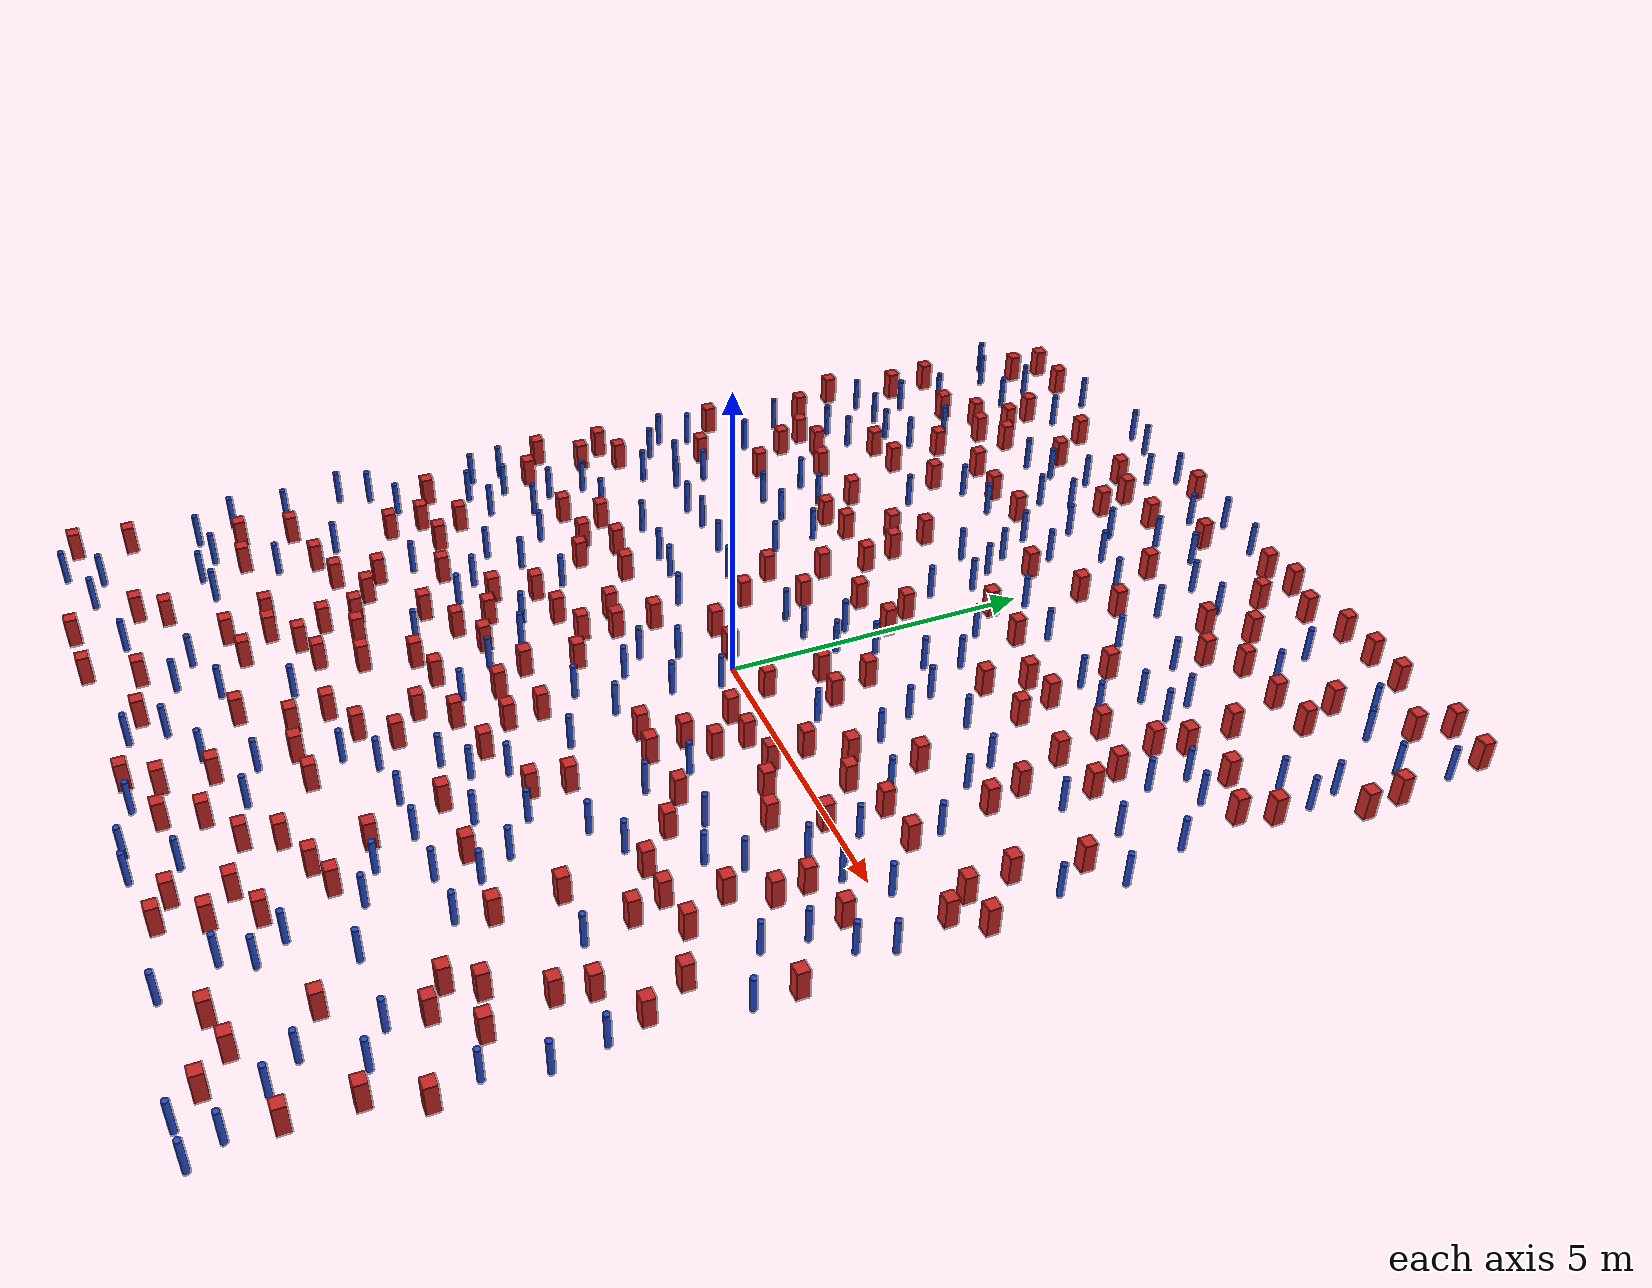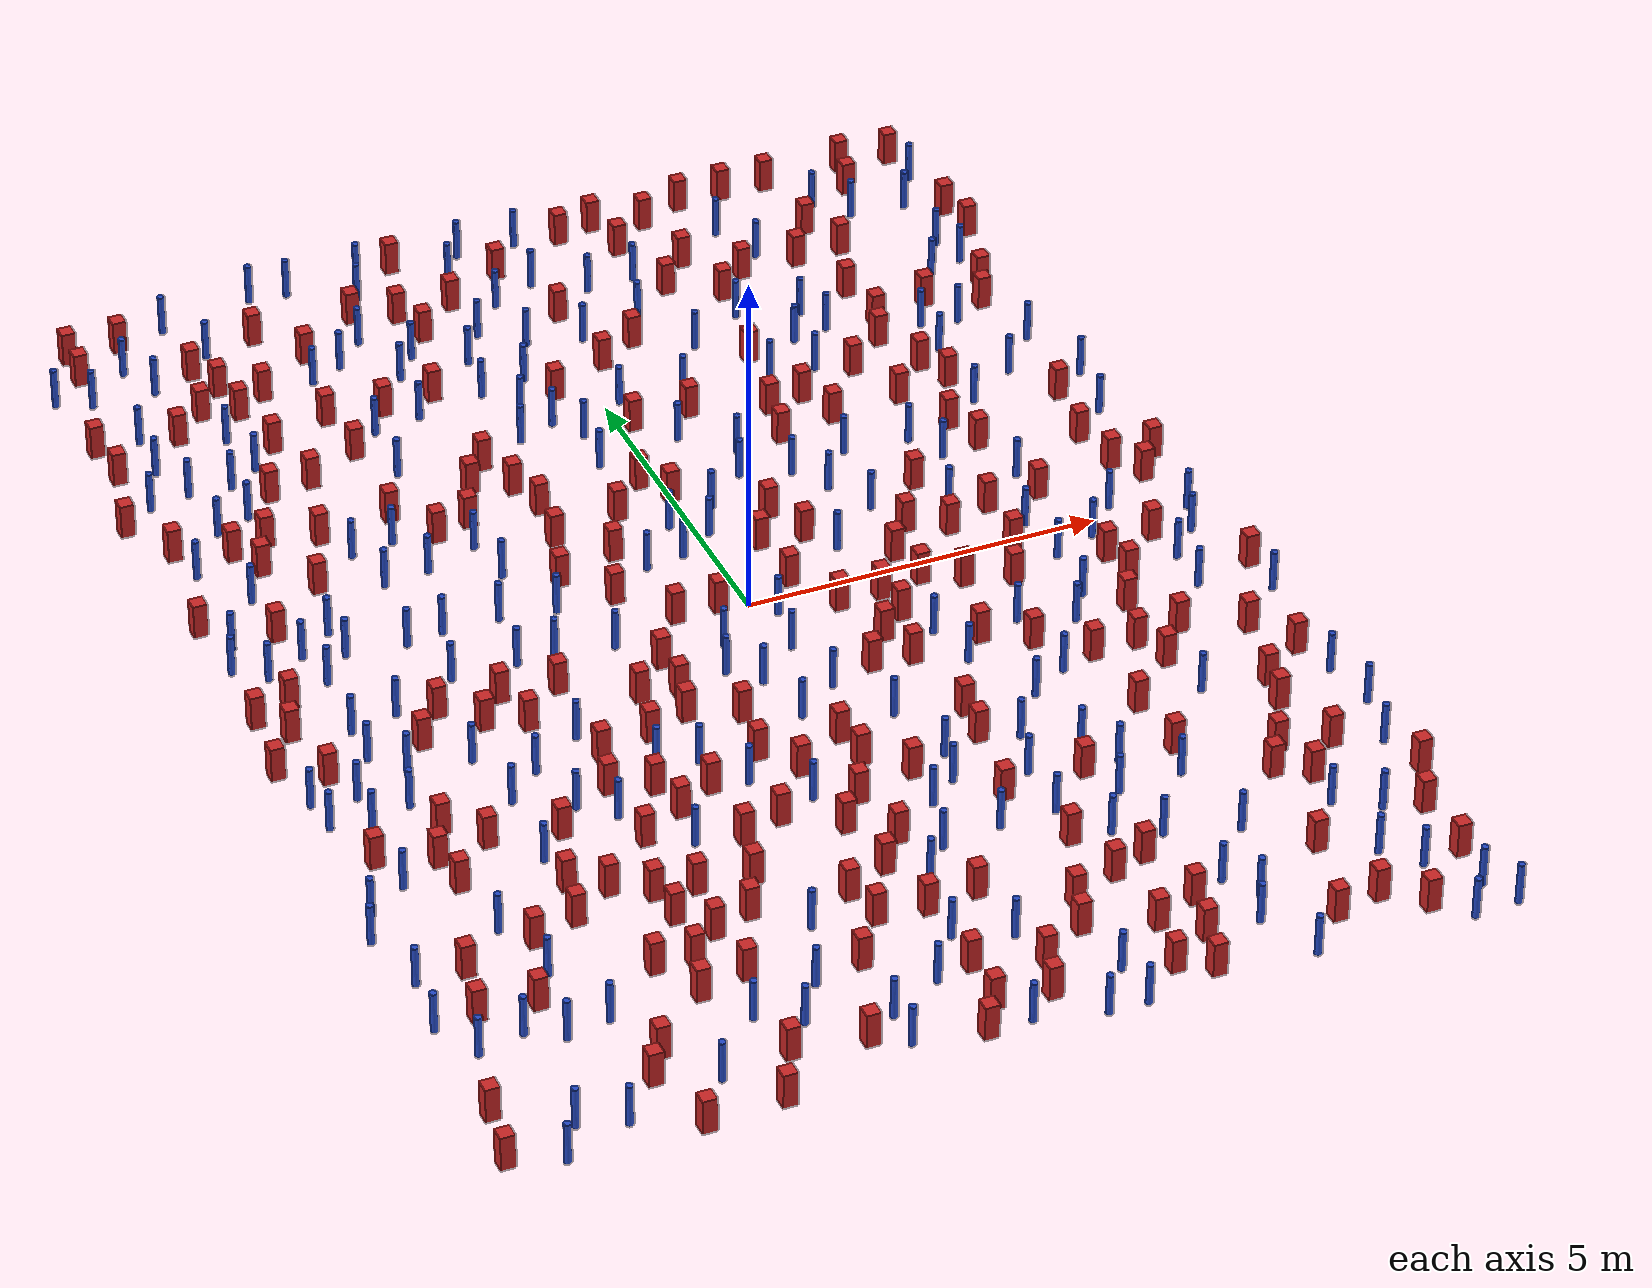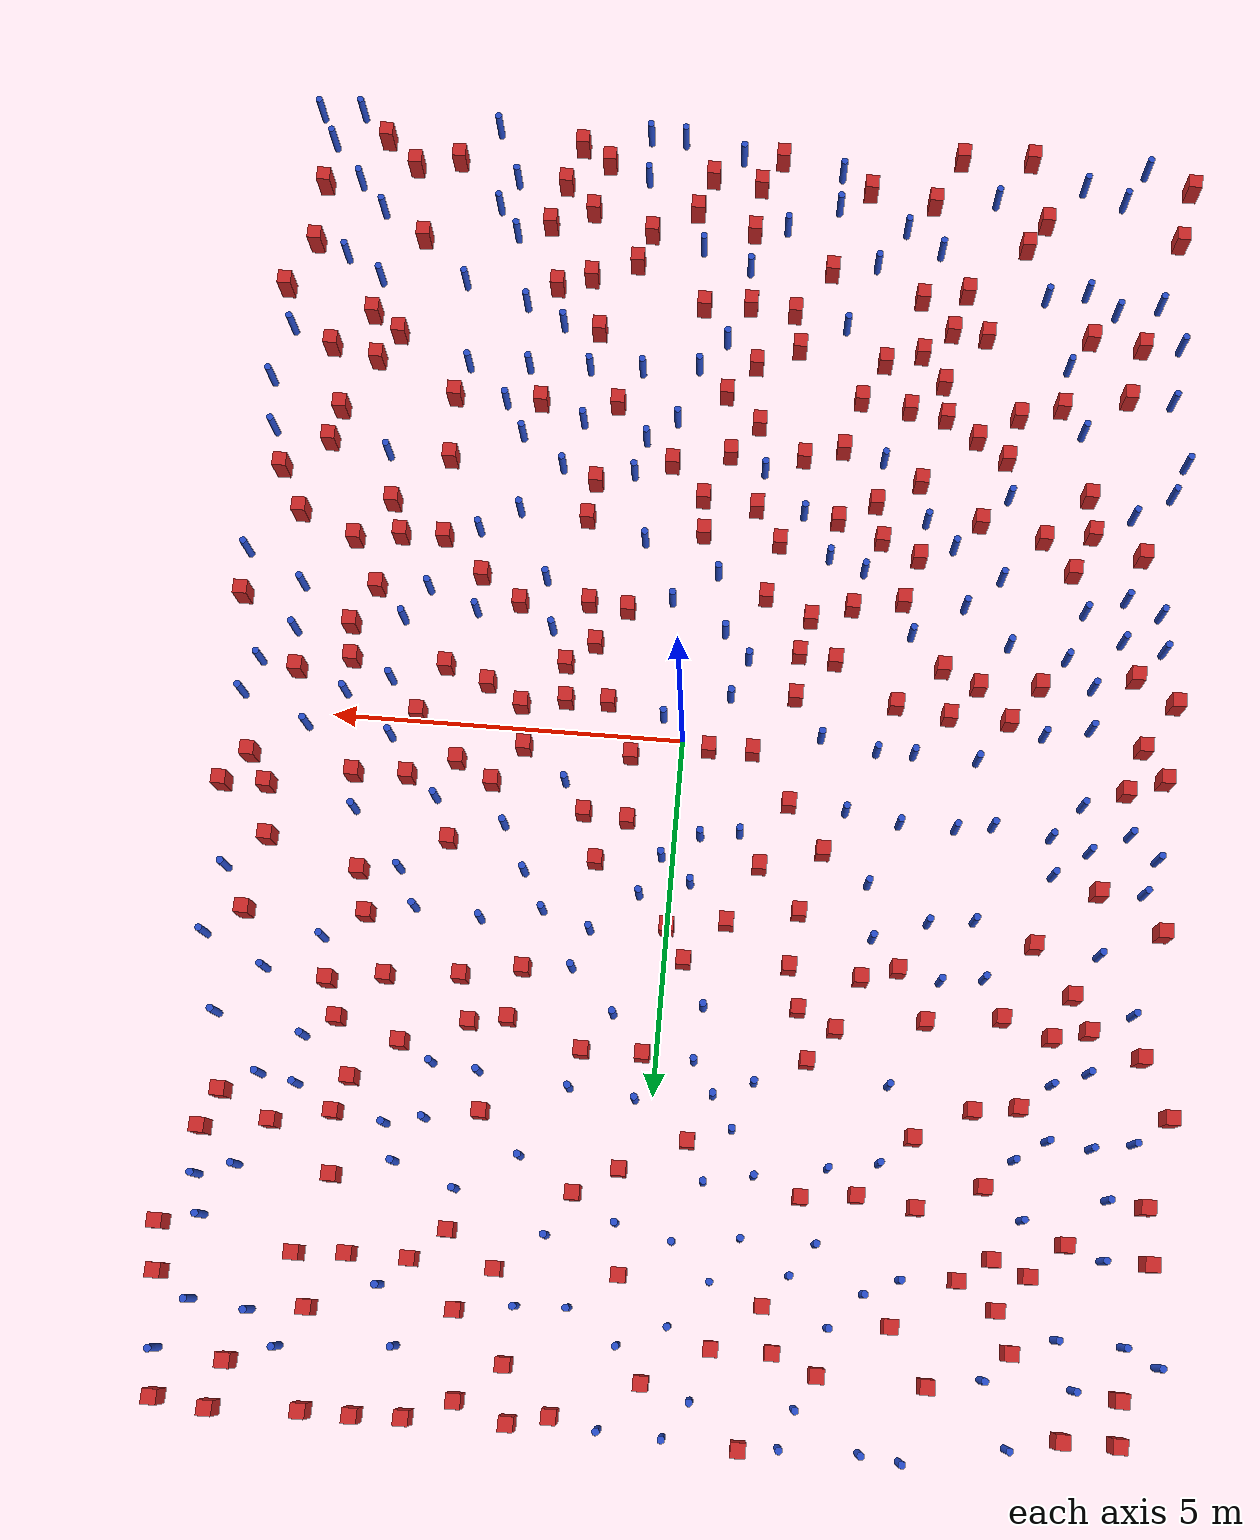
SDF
<sdf version="1.6">
  <model name="dense_84"><model name="pole_obstacle0">
  <static>true</static>
  <pose frame="">-6.29073102385 -9.41656100264 2.88873142074e-08 -9.9053668967e-09 4.60219948993e-07 -1.20965994957e-07</pose>
  <link name="link">
  <pose frame="">0 0 0.3 0 -0 0</pose>
    <inertial>
      <mass>1</mass>
      <inertia>
        <ixx>0.145833</ixx>
        <ixy>0</ixy>
        <ixz>0</ixz>
        <iyy>0.145833</iyy>
        <iyz>0</iyz>
        <izz>0.125</izz>
      </inertia>
    </inertial>
    <collision name="collision">
      <geometry>
        <cylinder>
          <radius>0.05</radius>
          <length>.6</length>
        </cylinder>
      </geometry>
      <max_contacts>10</max_contacts>
      <surface>
        <contact>
          <ode/>
        </contact>
        <bounce/>
        <friction>
          <torsional>
            <ode/>
          </torsional>
          <ode/>
        </friction>
      </surface>
    </collision>
    <visual name="visual">
      <geometry>
        <cylinder>
          <radius>0.05</radius>
          <length>.6</length>
        </cylinder>
      </geometry>
      <material>
        <script>
          <name>Gazebo/Blue</name>
          <uri>file://media/materials/scripts/gazebo.material</uri>
        </script>
      </material>
    </visual>
    <self_collide>0</self_collide>
    <kinematic>0</kinematic>
  </link>
</model>
<model name="pole_obstacle1">
  <static>true</static>
  <pose frame="">-3.26398219934 -0.0242368059715 2.88873142074e-08 -9.90536689502e-09 4.60219948997e-07 -1.20965994956e-07</pose>
  <link name="link">
  <pose frame="">0 0 0.3 0 -0 0</pose>
    <inertial>
      <mass>1</mass>
      <inertia>
        <ixx>0.145833</ixx>
        <ixy>0</ixy>
        <ixz>0</ixz>
        <iyy>0.145833</iyy>
        <iyz>0</iyz>
        <izz>0.125</izz>
      </inertia>
    </inertial>
    <collision name="collision">
      <geometry>
        <cylinder>
          <radius>0.05</radius>
          <length>.6</length>
        </cylinder>
      </geometry>
      <max_contacts>10</max_contacts>
      <surface>
        <contact>
          <ode/>
        </contact>
        <bounce/>
        <friction>
          <torsional>
            <ode/>
          </torsional>
          <ode/>
        </friction>
      </surface>
    </collision>
    <visual name="visual">
      <geometry>
        <cylinder>
          <radius>0.05</radius>
          <length>.6</length>
        </cylinder>
      </geometry>
      <material>
        <script>
          <name>Gazebo/Blue</name>
          <uri>file://media/materials/scripts/gazebo.material</uri>
        </script>
      </material>
    </visual>
    <self_collide>0</self_collide>
    <kinematic>0</kinematic>
  </link>
</model>
<model name="square_post_obstacle0">
  <static>true</static>
  <pose frame="">3.47742951445 4.54623904992 8.22691968438e-08 7.2212513382e-06 -7.54495500217e-07 2.29674213826e-05</pose>
  <link name="link">
    <pose frame="">0 0 0.25 0 -0 0</pose>
    <inertial>
      <mass>100</mass>
      <inertia>
        <ixx>0.166667</ixx>
        <ixy>0</ixy>
        <ixz>0</ixz>
        <iyy>0.166667</iyy>
        <iyz>0</iyz>
        <izz>0.166667</izz>
      </inertia>
    </inertial>
    <collision name="collision">
      <geometry>
        <box>
          <size>.2 .2 .5</size>
        </box>
      </geometry>
      <max_contacts>10</max_contacts>
      <surface>
        <contact>
          <ode/>
        </contact>
        <bounce/>
        <friction>
          <torsional>
            <ode/>
          </torsional>
          <ode/>
        </friction>
      </surface>
    </collision>
    <visual name="visual">
      <geometry>
        <box>
          <size>.2 .2 .5</size>
        </box>
      </geometry>
      <material>
        <script>
          <name>Gazebo/Red</name>
          <uri>file://media/materials/scripts/gazebo.material</uri>
        </script>
      </material>
    </visual>
    <self_collide>0</self_collide>
    <kinematic>0</kinematic>
  </link>
</model>
<model name="square_post_obstacle1">
  <static>true</static>
  <pose frame="">4.56344574119 0.853142851961 8.22691968438e-08 7.2212513382e-06 -7.54495500217e-07 2.29674213826e-05</pose>
  <link name="link">
    <pose frame="">0 0 0.25 0 -0 0</pose>
    <inertial>
      <mass>100</mass>
      <inertia>
        <ixx>0.166667</ixx>
        <ixy>0</ixy>
        <ixz>0</ixz>
        <iyy>0.166667</iyy>
        <iyz>0</iyz>
        <izz>0.166667</izz>
      </inertia>
    </inertial>
    <collision name="collision">
      <geometry>
        <box>
          <size>.2 .2 .5</size>
        </box>
      </geometry>
      <max_contacts>10</max_contacts>
      <surface>
        <contact>
          <ode/>
        </contact>
        <bounce/>
        <friction>
          <torsional>
            <ode/>
          </torsional>
          <ode/>
        </friction>
      </surface>
    </collision>
    <visual name="visual">
      <geometry>
        <box>
          <size>.2 .2 .5</size>
        </box>
      </geometry>
      <material>
        <script>
          <name>Gazebo/Red</name>
          <uri>file://media/materials/scripts/gazebo.material</uri>
        </script>
      </material>
    </visual>
    <self_collide>0</self_collide>
    <kinematic>0</kinematic>
  </link>
</model>
<model name="pole_obstacle2">
  <static>true</static>
  <pose frame="">-4.61047686809 8.33321980934 2.88873142074e-08 -9.9053668967e-09 4.60219948993e-07 -1.20965994957e-07</pose>
  <link name="link">
  <pose frame="">0 0 0.3 0 -0 0</pose>
    <inertial>
      <mass>1</mass>
      <inertia>
        <ixx>0.145833</ixx>
        <ixy>0</ixy>
        <ixz>0</ixz>
        <iyy>0.145833</iyy>
        <iyz>0</iyz>
        <izz>0.125</izz>
      </inertia>
    </inertial>
    <collision name="collision">
      <geometry>
        <cylinder>
          <radius>0.05</radius>
          <length>.6</length>
        </cylinder>
      </geometry>
      <max_contacts>10</max_contacts>
      <surface>
        <contact>
          <ode/>
        </contact>
        <bounce/>
        <friction>
          <torsional>
            <ode/>
          </torsional>
          <ode/>
        </friction>
      </surface>
    </collision>
    <visual name="visual">
      <geometry>
        <cylinder>
          <radius>0.05</radius>
          <length>.6</length>
        </cylinder>
      </geometry>
      <material>
        <script>
          <name>Gazebo/Blue</name>
          <uri>file://media/materials/scripts/gazebo.material</uri>
        </script>
      </material>
    </visual>
    <self_collide>0</self_collide>
    <kinematic>0</kinematic>
  </link>
</model>
<model name="pole_obstacle3">
  <static>true</static>
  <pose frame="">-6.16759911204 5.90546108467 2.88873142074e-08 -9.90536690842e-09 4.60219948965e-07 -1.20965994976e-07</pose>
  <link name="link">
  <pose frame="">0 0 0.3 0 -0 0</pose>
    <inertial>
      <mass>1</mass>
      <inertia>
        <ixx>0.145833</ixx>
        <ixy>0</ixy>
        <ixz>0</ixz>
        <iyy>0.145833</iyy>
        <iyz>0</iyz>
        <izz>0.125</izz>
      </inertia>
    </inertial>
    <collision name="collision">
      <geometry>
        <cylinder>
          <radius>0.05</radius>
          <length>.6</length>
        </cylinder>
      </geometry>
      <max_contacts>10</max_contacts>
      <surface>
        <contact>
          <ode/>
        </contact>
        <bounce/>
        <friction>
          <torsional>
            <ode/>
          </torsional>
          <ode/>
        </friction>
      </surface>
    </collision>
    <visual name="visual">
      <geometry>
        <cylinder>
          <radius>0.05</radius>
          <length>.6</length>
        </cylinder>
      </geometry>
      <material>
        <script>
          <name>Gazebo/Blue</name>
          <uri>file://media/materials/scripts/gazebo.material</uri>
        </script>
      </material>
    </visual>
    <self_collide>0</self_collide>
    <kinematic>0</kinematic>
  </link>
</model>
<model name="pole_obstacle4">
  <static>true</static>
  <pose frame="">-4.161526478 -0.00585685088212 2.88873142074e-08 -9.90536689125e-09 4.60219949006e-07 -1.20965994951e-07</pose>
  <link name="link">
  <pose frame="">0 0 0.3 0 -0 0</pose>
    <inertial>
      <mass>1</mass>
      <inertia>
        <ixx>0.145833</ixx>
        <ixy>0</ixy>
        <ixz>0</ixz>
        <iyy>0.145833</iyy>
        <iyz>0</iyz>
        <izz>0.125</izz>
      </inertia>
    </inertial>
    <collision name="collision">
      <geometry>
        <cylinder>
          <radius>0.05</radius>
          <length>.6</length>
        </cylinder>
      </geometry>
      <max_contacts>10</max_contacts>
      <surface>
        <contact>
          <ode/>
        </contact>
        <bounce/>
        <friction>
          <torsional>
            <ode/>
          </torsional>
          <ode/>
        </friction>
      </surface>
    </collision>
    <visual name="visual">
      <geometry>
        <cylinder>
          <radius>0.05</radius>
          <length>.6</length>
        </cylinder>
      </geometry>
      <material>
        <script>
          <name>Gazebo/Blue</name>
          <uri>file://media/materials/scripts/gazebo.material</uri>
        </script>
      </material>
    </visual>
    <self_collide>0</self_collide>
    <kinematic>0</kinematic>
  </link>
</model>
<model name="pole_obstacle5">
  <static>true</static>
  <pose frame="">-6.77612854679 -5.65401270305 2.88873142074e-08 -9.90536690842e-09 4.60219948965e-07 -1.20965994976e-07</pose>
  <link name="link">
  <pose frame="">0 0 0.3 0 -0 0</pose>
    <inertial>
      <mass>1</mass>
      <inertia>
        <ixx>0.145833</ixx>
        <ixy>0</ixy>
        <ixz>0</ixz>
        <iyy>0.145833</iyy>
        <iyz>0</iyz>
        <izz>0.125</izz>
      </inertia>
    </inertial>
    <collision name="collision">
      <geometry>
        <cylinder>
          <radius>0.05</radius>
          <length>.6</length>
        </cylinder>
      </geometry>
      <max_contacts>10</max_contacts>
      <surface>
        <contact>
          <ode/>
        </contact>
        <bounce/>
        <friction>
          <torsional>
            <ode/>
          </torsional>
          <ode/>
        </friction>
      </surface>
    </collision>
    <visual name="visual">
      <geometry>
        <cylinder>
          <radius>0.05</radius>
          <length>.6</length>
        </cylinder>
      </geometry>
      <material>
        <script>
          <name>Gazebo/Blue</name>
          <uri>file://media/materials/scripts/gazebo.material</uri>
        </script>
      </material>
    </visual>
    <self_collide>0</self_collide>
    <kinematic>0</kinematic>
  </link>
</model>
<model name="pole_obstacle6">
  <static>true</static>
  <pose frame="">1.02716749016 -3.94141374447 2.88873142074e-08 -9.905366898e-09 4.6021994899e-07 -1.20965994959e-07</pose>
  <link name="link">
  <pose frame="">0 0 0.3 0 -0 0</pose>
    <inertial>
      <mass>1</mass>
      <inertia>
        <ixx>0.145833</ixx>
        <ixy>0</ixy>
        <ixz>0</ixz>
        <iyy>0.145833</iyy>
        <iyz>0</iyz>
        <izz>0.125</izz>
      </inertia>
    </inertial>
    <collision name="collision">
      <geometry>
        <cylinder>
          <radius>0.05</radius>
          <length>.6</length>
        </cylinder>
      </geometry>
      <max_contacts>10</max_contacts>
      <surface>
        <contact>
          <ode/>
        </contact>
        <bounce/>
        <friction>
          <torsional>
            <ode/>
          </torsional>
          <ode/>
        </friction>
      </surface>
    </collision>
    <visual name="visual">
      <geometry>
        <cylinder>
          <radius>0.05</radius>
          <length>.6</length>
        </cylinder>
      </geometry>
      <material>
        <script>
          <name>Gazebo/Blue</name>
          <uri>file://media/materials/scripts/gazebo.material</uri>
        </script>
      </material>
    </visual>
    <self_collide>0</self_collide>
    <kinematic>0</kinematic>
  </link>
</model>
<model name="square_post_obstacle2">
  <static>true</static>
  <pose frame="">1.88020611518 7.4290270378 8.22691968438e-08 7.2212513382e-06 -7.54495500217e-07 2.29674213826e-05</pose>
  <link name="link">
    <pose frame="">0 0 0.25 0 -0 0</pose>
    <inertial>
      <mass>100</mass>
      <inertia>
        <ixx>0.166667</ixx>
        <ixy>0</ixy>
        <ixz>0</ixz>
        <iyy>0.166667</iyy>
        <iyz>0</iyz>
        <izz>0.166667</izz>
      </inertia>
    </inertial>
    <collision name="collision">
      <geometry>
        <box>
          <size>.2 .2 .5</size>
        </box>
      </geometry>
      <max_contacts>10</max_contacts>
      <surface>
        <contact>
          <ode/>
        </contact>
        <bounce/>
        <friction>
          <torsional>
            <ode/>
          </torsional>
          <ode/>
        </friction>
      </surface>
    </collision>
    <visual name="visual">
      <geometry>
        <box>
          <size>.2 .2 .5</size>
        </box>
      </geometry>
      <material>
        <script>
          <name>Gazebo/Red</name>
          <uri>file://media/materials/scripts/gazebo.material</uri>
        </script>
      </material>
    </visual>
    <self_collide>0</self_collide>
    <kinematic>0</kinematic>
  </link>
</model>
<model name="square_post_obstacle3">
  <static>true</static>
  <pose frame="">6.05488720477 0.67913591342 8.22691968438e-08 7.2212513382e-06 -7.54495500217e-07 2.29674213826e-05</pose>
  <link name="link">
    <pose frame="">0 0 0.25 0 -0 0</pose>
    <inertial>
      <mass>100</mass>
      <inertia>
        <ixx>0.166667</ixx>
        <ixy>0</ixy>
        <ixz>0</ixz>
        <iyy>0.166667</iyy>
        <iyz>0</iyz>
        <izz>0.166667</izz>
      </inertia>
    </inertial>
    <collision name="collision">
      <geometry>
        <box>
          <size>.2 .2 .5</size>
        </box>
      </geometry>
      <max_contacts>10</max_contacts>
      <surface>
        <contact>
          <ode/>
        </contact>
        <bounce/>
        <friction>
          <torsional>
            <ode/>
          </torsional>
          <ode/>
        </friction>
      </surface>
    </collision>
    <visual name="visual">
      <geometry>
        <box>
          <size>.2 .2 .5</size>
        </box>
      </geometry>
      <material>
        <script>
          <name>Gazebo/Red</name>
          <uri>file://media/materials/scripts/gazebo.material</uri>
        </script>
      </material>
    </visual>
    <self_collide>0</self_collide>
    <kinematic>0</kinematic>
  </link>
</model>
<model name="square_post_obstacle4">
  <static>true</static>
  <pose frame="">1.84041106598 -8.94122903766 8.22691968438e-08 7.2212513382e-06 -7.54495500217e-07 2.29674213826e-05</pose>
  <link name="link">
    <pose frame="">0 0 0.25 0 -0 0</pose>
    <inertial>
      <mass>100</mass>
      <inertia>
        <ixx>0.166667</ixx>
        <ixy>0</ixy>
        <ixz>0</ixz>
        <iyy>0.166667</iyy>
        <iyz>0</iyz>
        <izz>0.166667</izz>
      </inertia>
    </inertial>
    <collision name="collision">
      <geometry>
        <box>
          <size>.2 .2 .5</size>
        </box>
      </geometry>
      <max_contacts>10</max_contacts>
      <surface>
        <contact>
          <ode/>
        </contact>
        <bounce/>
        <friction>
          <torsional>
            <ode/>
          </torsional>
          <ode/>
        </friction>
      </surface>
    </collision>
    <visual name="visual">
      <geometry>
        <box>
          <size>.2 .2 .5</size>
        </box>
      </geometry>
      <material>
        <script>
          <name>Gazebo/Red</name>
          <uri>file://media/materials/scripts/gazebo.material</uri>
        </script>
      </material>
    </visual>
    <self_collide>0</self_collide>
    <kinematic>0</kinematic>
  </link>
</model>
<model name="pole_obstacle7">
  <static>true</static>
  <pose frame="">-4.8611476765 -7.20057971057 2.88873142074e-08 -9.90536690842e-09 4.60219948965e-07 -1.20965994976e-07</pose>
  <link name="link">
  <pose frame="">0 0 0.3 0 -0 0</pose>
    <inertial>
      <mass>1</mass>
      <inertia>
        <ixx>0.145833</ixx>
        <ixy>0</ixy>
        <ixz>0</ixz>
        <iyy>0.145833</iyy>
        <iyz>0</iyz>
        <izz>0.125</izz>
      </inertia>
    </inertial>
    <collision name="collision">
      <geometry>
        <cylinder>
          <radius>0.05</radius>
          <length>.6</length>
        </cylinder>
      </geometry>
      <max_contacts>10</max_contacts>
      <surface>
        <contact>
          <ode/>
        </contact>
        <bounce/>
        <friction>
          <torsional>
            <ode/>
          </torsional>
          <ode/>
        </friction>
      </surface>
    </collision>
    <visual name="visual">
      <geometry>
        <cylinder>
          <radius>0.05</radius>
          <length>.6</length>
        </cylinder>
      </geometry>
      <material>
        <script>
          <name>Gazebo/Blue</name>
          <uri>file://media/materials/scripts/gazebo.material</uri>
        </script>
      </material>
    </visual>
    <self_collide>0</self_collide>
    <kinematic>0</kinematic>
  </link>
</model>
<model name="pole_obstacle8">
  <static>true</static>
  <pose frame="">-4.42272245899 0.923110105509 2.88873142074e-08 -9.90536689837e-09 4.60219948989e-07 -1.2096599496e-07</pose>
  <link name="link">
  <pose frame="">0 0 0.3 0 -0 0</pose>
    <inertial>
      <mass>1</mass>
      <inertia>
        <ixx>0.145833</ixx>
        <ixy>0</ixy>
        <ixz>0</ixz>
        <iyy>0.145833</iyy>
        <iyz>0</iyz>
        <izz>0.125</izz>
      </inertia>
    </inertial>
    <collision name="collision">
      <geometry>
        <cylinder>
          <radius>0.05</radius>
          <length>.6</length>
        </cylinder>
      </geometry>
      <max_contacts>10</max_contacts>
      <surface>
        <contact>
          <ode/>
        </contact>
        <bounce/>
        <friction>
          <torsional>
            <ode/>
          </torsional>
          <ode/>
        </friction>
      </surface>
    </collision>
    <visual name="visual">
      <geometry>
        <cylinder>
          <radius>0.05</radius>
          <length>.6</length>
        </cylinder>
      </geometry>
      <material>
        <script>
          <name>Gazebo/Blue</name>
          <uri>file://media/materials/scripts/gazebo.material</uri>
        </script>
      </material>
    </visual>
    <self_collide>0</self_collide>
    <kinematic>0</kinematic>
  </link>
</model>
<model name="square_post_obstacle5">
  <static>true</static>
  <pose frame="">4.70011311741 -5.88994895485 8.22691968438e-08 7.2212513382e-06 -7.54495500217e-07 2.29674213826e-05</pose>
  <link name="link">
    <pose frame="">0 0 0.25 0 -0 0</pose>
    <inertial>
      <mass>100</mass>
      <inertia>
        <ixx>0.166667</ixx>
        <ixy>0</ixy>
        <ixz>0</ixz>
        <iyy>0.166667</iyy>
        <iyz>0</iyz>
        <izz>0.166667</izz>
      </inertia>
    </inertial>
    <collision name="collision">
      <geometry>
        <box>
          <size>.2 .2 .5</size>
        </box>
      </geometry>
      <max_contacts>10</max_contacts>
      <surface>
        <contact>
          <ode/>
        </contact>
        <bounce/>
        <friction>
          <torsional>
            <ode/>
          </torsional>
          <ode/>
        </friction>
      </surface>
    </collision>
    <visual name="visual">
      <geometry>
        <box>
          <size>.2 .2 .5</size>
        </box>
      </geometry>
      <material>
        <script>
          <name>Gazebo/Red</name>
          <uri>file://media/materials/scripts/gazebo.material</uri>
        </script>
      </material>
    </visual>
    <self_collide>0</self_collide>
    <kinematic>0</kinematic>
  </link>
</model>
<model name="square_post_obstacle6">
  <static>true</static>
  <pose frame="">-1.98005522862 -3.44571432488 8.22691968438e-08 7.2212513382e-06 -7.54495500217e-07 2.29674213826e-05</pose>
  <link name="link">
    <pose frame="">0 0 0.25 0 -0 0</pose>
    <inertial>
      <mass>100</mass>
      <inertia>
        <ixx>0.166667</ixx>
        <ixy>0</ixy>
        <ixz>0</ixz>
        <iyy>0.166667</iyy>
        <iyz>0</iyz>
        <izz>0.166667</izz>
      </inertia>
    </inertial>
    <collision name="collision">
      <geometry>
        <box>
          <size>.2 .2 .5</size>
        </box>
      </geometry>
      <max_contacts>10</max_contacts>
      <surface>
        <contact>
          <ode/>
        </contact>
        <bounce/>
        <friction>
          <torsional>
            <ode/>
          </torsional>
          <ode/>
        </friction>
      </surface>
    </collision>
    <visual name="visual">
      <geometry>
        <box>
          <size>.2 .2 .5</size>
        </box>
      </geometry>
      <material>
        <script>
          <name>Gazebo/Red</name>
          <uri>file://media/materials/scripts/gazebo.material</uri>
        </script>
      </material>
    </visual>
    <self_collide>0</self_collide>
    <kinematic>0</kinematic>
  </link>
</model>
<model name="square_post_obstacle7">
  <static>true</static>
  <pose frame="">-0.0057804838044 -3.64052137641 8.22691968438e-08 7.2212513382e-06 -7.54495500217e-07 2.29674213826e-05</pose>
  <link name="link">
    <pose frame="">0 0 0.25 0 -0 0</pose>
    <inertial>
      <mass>100</mass>
      <inertia>
        <ixx>0.166667</ixx>
        <ixy>0</ixy>
        <ixz>0</ixz>
        <iyy>0.166667</iyy>
        <iyz>0</iyz>
        <izz>0.166667</izz>
      </inertia>
    </inertial>
    <collision name="collision">
      <geometry>
        <box>
          <size>.2 .2 .5</size>
        </box>
      </geometry>
      <max_contacts>10</max_contacts>
      <surface>
        <contact>
          <ode/>
        </contact>
        <bounce/>
        <friction>
          <torsional>
            <ode/>
          </torsional>
          <ode/>
        </friction>
      </surface>
    </collision>
    <visual name="visual">
      <geometry>
        <box>
          <size>.2 .2 .5</size>
        </box>
      </geometry>
      <material>
        <script>
          <name>Gazebo/Red</name>
          <uri>file://media/materials/scripts/gazebo.material</uri>
        </script>
      </material>
    </visual>
    <self_collide>0</self_collide>
    <kinematic>0</kinematic>
  </link>
</model>
<model name="pole_obstacle9">
  <static>true</static>
  <pose frame="">2.28499519271 -6.22191880384 2.88873142074e-08 -9.90536689859e-09 4.60219948989e-07 -1.20965994961e-07</pose>
  <link name="link">
  <pose frame="">0 0 0.3 0 -0 0</pose>
    <inertial>
      <mass>1</mass>
      <inertia>
        <ixx>0.145833</ixx>
        <ixy>0</ixy>
        <ixz>0</ixz>
        <iyy>0.145833</iyy>
        <iyz>0</iyz>
        <izz>0.125</izz>
      </inertia>
    </inertial>
    <collision name="collision">
      <geometry>
        <cylinder>
          <radius>0.05</radius>
          <length>.6</length>
        </cylinder>
      </geometry>
      <max_contacts>10</max_contacts>
      <surface>
        <contact>
          <ode/>
        </contact>
        <bounce/>
        <friction>
          <torsional>
            <ode/>
          </torsional>
          <ode/>
        </friction>
      </surface>
    </collision>
    <visual name="visual">
      <geometry>
        <cylinder>
          <radius>0.05</radius>
          <length>.6</length>
        </cylinder>
      </geometry>
      <material>
        <script>
          <name>Gazebo/Blue</name>
          <uri>file://media/materials/scripts/gazebo.material</uri>
        </script>
      </material>
    </visual>
    <self_collide>0</self_collide>
    <kinematic>0</kinematic>
  </link>
</model>
<model name="pole_obstacle10">
  <static>true</static>
  <pose frame="">5.08234598472 -6.75202170743 2.88873142074e-08 -9.90536690842e-09 4.60219948965e-07 -1.20965994976e-07</pose>
  <link name="link">
  <pose frame="">0 0 0.3 0 -0 0</pose>
    <inertial>
      <mass>1</mass>
      <inertia>
        <ixx>0.145833</ixx>
        <ixy>0</ixy>
        <ixz>0</ixz>
        <iyy>0.145833</iyy>
        <iyz>0</iyz>
        <izz>0.125</izz>
      </inertia>
    </inertial>
    <collision name="collision">
      <geometry>
        <cylinder>
          <radius>0.05</radius>
          <length>.6</length>
        </cylinder>
      </geometry>
      <max_contacts>10</max_contacts>
      <surface>
        <contact>
          <ode/>
        </contact>
        <bounce/>
        <friction>
          <torsional>
            <ode/>
          </torsional>
          <ode/>
        </friction>
      </surface>
    </collision>
    <visual name="visual">
      <geometry>
        <cylinder>
          <radius>0.05</radius>
          <length>.6</length>
        </cylinder>
      </geometry>
      <material>
        <script>
          <name>Gazebo/Blue</name>
          <uri>file://media/materials/scripts/gazebo.material</uri>
        </script>
      </material>
    </visual>
    <self_collide>0</self_collide>
    <kinematic>0</kinematic>
  </link>
</model>
<model name="pole_obstacle11">
  <static>true</static>
  <pose frame="">0.41692032327 2.27141418955 2.88873142074e-08 -9.90536689663e-09 4.60219948993e-07 -1.20965994959e-07</pose>
  <link name="link">
  <pose frame="">0 0 0.3 0 -0 0</pose>
    <inertial>
      <mass>1</mass>
      <inertia>
        <ixx>0.145833</ixx>
        <ixy>0</ixy>
        <ixz>0</ixz>
        <iyy>0.145833</iyy>
        <iyz>0</iyz>
        <izz>0.125</izz>
      </inertia>
    </inertial>
    <collision name="collision">
      <geometry>
        <cylinder>
          <radius>0.05</radius>
          <length>.6</length>
        </cylinder>
      </geometry>
      <max_contacts>10</max_contacts>
      <surface>
        <contact>
          <ode/>
        </contact>
        <bounce/>
        <friction>
          <torsional>
            <ode/>
          </torsional>
          <ode/>
        </friction>
      </surface>
    </collision>
    <visual name="visual">
      <geometry>
        <cylinder>
          <radius>0.05</radius>
          <length>.6</length>
        </cylinder>
      </geometry>
      <material>
        <script>
          <name>Gazebo/Blue</name>
          <uri>file://media/materials/scripts/gazebo.material</uri>
        </script>
      </material>
    </visual>
    <self_collide>0</self_collide>
    <kinematic>0</kinematic>
  </link>
</model>
<model name="pole_obstacle12">
  <static>true</static>
  <pose frame="">-6.8986550622 7.99468464526 2.88873142074e-08 -9.90536689847e-09 4.60219948989e-07 -1.2096599496e-07</pose>
  <link name="link">
  <pose frame="">0 0 0.3 0 -0 0</pose>
    <inertial>
      <mass>1</mass>
      <inertia>
        <ixx>0.145833</ixx>
        <ixy>0</ixy>
        <ixz>0</ixz>
        <iyy>0.145833</iyy>
        <iyz>0</iyz>
        <izz>0.125</izz>
      </inertia>
    </inertial>
    <collision name="collision">
      <geometry>
        <cylinder>
          <radius>0.05</radius>
          <length>.6</length>
        </cylinder>
      </geometry>
      <max_contacts>10</max_contacts>
      <surface>
        <contact>
          <ode/>
        </contact>
        <bounce/>
        <friction>
          <torsional>
            <ode/>
          </torsional>
          <ode/>
        </friction>
      </surface>
    </collision>
    <visual name="visual">
      <geometry>
        <cylinder>
          <radius>0.05</radius>
          <length>.6</length>
        </cylinder>
      </geometry>
      <material>
        <script>
          <name>Gazebo/Blue</name>
          <uri>file://media/materials/scripts/gazebo.material</uri>
        </script>
      </material>
    </visual>
    <self_collide>0</self_collide>
    <kinematic>0</kinematic>
  </link>
</model>
<model name="square_post_obstacle8">
  <static>true</static>
  <pose frame="">-6.68188247831 5.96038204234 8.22691968438e-08 7.2212513382e-06 -7.54495500217e-07 2.29674213826e-05</pose>
  <link name="link">
    <pose frame="">0 0 0.25 0 -0 0</pose>
    <inertial>
      <mass>100</mass>
      <inertia>
        <ixx>0.166667</ixx>
        <ixy>0</ixy>
        <ixz>0</ixz>
        <iyy>0.166667</iyy>
        <iyz>0</iyz>
        <izz>0.166667</izz>
      </inertia>
    </inertial>
    <collision name="collision">
      <geometry>
        <box>
          <size>.2 .2 .5</size>
        </box>
      </geometry>
      <max_contacts>10</max_contacts>
      <surface>
        <contact>
          <ode/>
        </contact>
        <bounce/>
        <friction>
          <torsional>
            <ode/>
          </torsional>
          <ode/>
        </friction>
      </surface>
    </collision>
    <visual name="visual">
      <geometry>
        <box>
          <size>.2 .2 .5</size>
        </box>
      </geometry>
      <material>
        <script>
          <name>Gazebo/Red</name>
          <uri>file://media/materials/scripts/gazebo.material</uri>
        </script>
      </material>
    </visual>
    <self_collide>0</self_collide>
    <kinematic>0</kinematic>
  </link>
</model>
<model name="square_post_obstacle9">
  <static>true</static>
  <pose frame="">-6.7540369003 6.69056023257 8.22691968438e-08 7.22125133819e-06 -7.54495500217e-07 2.29674213826e-05</pose>
  <link name="link">
    <pose frame="">0 0 0.25 0 -0 0</pose>
    <inertial>
      <mass>100</mass>
      <inertia>
        <ixx>0.166667</ixx>
        <ixy>0</ixy>
        <ixz>0</ixz>
        <iyy>0.166667</iyy>
        <iyz>0</iyz>
        <izz>0.166667</izz>
      </inertia>
    </inertial>
    <collision name="collision">
      <geometry>
        <box>
          <size>.2 .2 .5</size>
        </box>
      </geometry>
      <max_contacts>10</max_contacts>
      <surface>
        <contact>
          <ode/>
        </contact>
        <bounce/>
        <friction>
          <torsional>
            <ode/>
          </torsional>
          <ode/>
        </friction>
      </surface>
    </collision>
    <visual name="visual">
      <geometry>
        <box>
          <size>.2 .2 .5</size>
        </box>
      </geometry>
      <material>
        <script>
          <name>Gazebo/Red</name>
          <uri>file://media/materials/scripts/gazebo.material</uri>
        </script>
      </material>
    </visual>
    <self_collide>0</self_collide>
    <kinematic>0</kinematic>
  </link>
</model>
<model name="pole_obstacle13">
  <static>true</static>
  <pose frame="">0.152913802134 1.71130107241 2.88873142074e-08 -9.90536689569e-09 4.60219948996e-07 -1.20965994956e-07</pose>
  <link name="link">
  <pose frame="">0 0 0.3 0 -0 0</pose>
    <inertial>
      <mass>1</mass>
      <inertia>
        <ixx>0.145833</ixx>
        <ixy>0</ixy>
        <ixz>0</ixz>
        <iyy>0.145833</iyy>
        <iyz>0</iyz>
        <izz>0.125</izz>
      </inertia>
    </inertial>
    <collision name="collision">
      <geometry>
        <cylinder>
          <radius>0.05</radius>
          <length>.6</length>
        </cylinder>
      </geometry>
      <max_contacts>10</max_contacts>
      <surface>
        <contact>
          <ode/>
        </contact>
        <bounce/>
        <friction>
          <torsional>
            <ode/>
          </torsional>
          <ode/>
        </friction>
      </surface>
    </collision>
    <visual name="visual">
      <geometry>
        <cylinder>
          <radius>0.05</radius>
          <length>.6</length>
        </cylinder>
      </geometry>
      <material>
        <script>
          <name>Gazebo/Blue</name>
          <uri>file://media/materials/scripts/gazebo.material</uri>
        </script>
      </material>
    </visual>
    <self_collide>0</self_collide>
    <kinematic>0</kinematic>
  </link>
</model>
<model name="square_post_obstacle10">
  <static>true</static>
  <pose frame="">4.29482874448 8.11141196569 8.22691968438e-08 7.22125133819e-06 -7.54495500217e-07 2.29674213826e-05</pose>
  <link name="link">
    <pose frame="">0 0 0.25 0 -0 0</pose>
    <inertial>
      <mass>100</mass>
      <inertia>
        <ixx>0.166667</ixx>
        <ixy>0</ixy>
        <ixz>0</ixz>
        <iyy>0.166667</iyy>
        <iyz>0</iyz>
        <izz>0.166667</izz>
      </inertia>
    </inertial>
    <collision name="collision">
      <geometry>
        <box>
          <size>.2 .2 .5</size>
        </box>
      </geometry>
      <max_contacts>10</max_contacts>
      <surface>
        <contact>
          <ode/>
        </contact>
        <bounce/>
        <friction>
          <torsional>
            <ode/>
          </torsional>
          <ode/>
        </friction>
      </surface>
    </collision>
    <visual name="visual">
      <geometry>
        <box>
          <size>.2 .2 .5</size>
        </box>
      </geometry>
      <material>
        <script>
          <name>Gazebo/Red</name>
          <uri>file://media/materials/scripts/gazebo.material</uri>
        </script>
      </material>
    </visual>
    <self_collide>0</self_collide>
    <kinematic>0</kinematic>
  </link>
</model>
<model name="square_post_obstacle11">
  <static>true</static>
  <pose frame="">3.01679938763 7.38728642145 8.22691968438e-08 7.2212513382e-06 -7.54495500217e-07 2.29674213826e-05</pose>
  <link name="link">
    <pose frame="">0 0 0.25 0 -0 0</pose>
    <inertial>
      <mass>100</mass>
      <inertia>
        <ixx>0.166667</ixx>
        <ixy>0</ixy>
        <ixz>0</ixz>
        <iyy>0.166667</iyy>
        <iyz>0</iyz>
        <izz>0.166667</izz>
      </inertia>
    </inertial>
    <collision name="collision">
      <geometry>
        <box>
          <size>.2 .2 .5</size>
        </box>
      </geometry>
      <max_contacts>10</max_contacts>
      <surface>
        <contact>
          <ode/>
        </contact>
        <bounce/>
        <friction>
          <torsional>
            <ode/>
          </torsional>
          <ode/>
        </friction>
      </surface>
    </collision>
    <visual name="visual">
      <geometry>
        <box>
          <size>.2 .2 .5</size>
        </box>
      </geometry>
      <material>
        <script>
          <name>Gazebo/Red</name>
          <uri>file://media/materials/scripts/gazebo.material</uri>
        </script>
      </material>
    </visual>
    <self_collide>0</self_collide>
    <kinematic>0</kinematic>
  </link>
</model>
<model name="pole_obstacle14">
  <static>true</static>
  <pose frame="">-4.4448475508 -3.98693693877 2.88873142074e-08 -9.90536690067e-09 4.60219948984e-07 -1.20965994963e-07</pose>
  <link name="link">
  <pose frame="">0 0 0.3 0 -0 0</pose>
    <inertial>
      <mass>1</mass>
      <inertia>
        <ixx>0.145833</ixx>
        <ixy>0</ixy>
        <ixz>0</ixz>
        <iyy>0.145833</iyy>
        <iyz>0</iyz>
        <izz>0.125</izz>
      </inertia>
    </inertial>
    <collision name="collision">
      <geometry>
        <cylinder>
          <radius>0.05</radius>
          <length>.6</length>
        </cylinder>
      </geometry>
      <max_contacts>10</max_contacts>
      <surface>
        <contact>
          <ode/>
        </contact>
        <bounce/>
        <friction>
          <torsional>
            <ode/>
          </torsional>
          <ode/>
        </friction>
      </surface>
    </collision>
    <visual name="visual">
      <geometry>
        <cylinder>
          <radius>0.05</radius>
          <length>.6</length>
        </cylinder>
      </geometry>
      <material>
        <script>
          <name>Gazebo/Blue</name>
          <uri>file://media/materials/scripts/gazebo.material</uri>
        </script>
      </material>
    </visual>
    <self_collide>0</self_collide>
    <kinematic>0</kinematic>
  </link>
</model>
<model name="pole_obstacle15">
  <static>true</static>
  <pose frame="">-5.55113076476 7.75056409933 2.88873142074e-08 -9.90536690842e-09 4.60219948965e-07 -1.20965994976e-07</pose>
  <link name="link">
  <pose frame="">0 0 0.3 0 -0 0</pose>
    <inertial>
      <mass>1</mass>
      <inertia>
        <ixx>0.145833</ixx>
        <ixy>0</ixy>
        <ixz>0</ixz>
        <iyy>0.145833</iyy>
        <iyz>0</iyz>
        <izz>0.125</izz>
      </inertia>
    </inertial>
    <collision name="collision">
      <geometry>
        <cylinder>
          <radius>0.05</radius>
          <length>.6</length>
        </cylinder>
      </geometry>
      <max_contacts>10</max_contacts>
      <surface>
        <contact>
          <ode/>
        </contact>
        <bounce/>
        <friction>
          <torsional>
            <ode/>
          </torsional>
          <ode/>
        </friction>
      </surface>
    </collision>
    <visual name="visual">
      <geometry>
        <cylinder>
          <radius>0.05</radius>
          <length>.6</length>
        </cylinder>
      </geometry>
      <material>
        <script>
          <name>Gazebo/Blue</name>
          <uri>file://media/materials/scripts/gazebo.material</uri>
        </script>
      </material>
    </visual>
    <self_collide>0</self_collide>
    <kinematic>0</kinematic>
  </link>
</model>
<model name="square_post_obstacle12">
  <static>true</static>
  <pose frame="">-0.271276717077 3.13880675814 8.22691968438e-08 7.2212513382e-06 -7.54495500217e-07 2.29674213826e-05</pose>
  <link name="link">
    <pose frame="">0 0 0.25 0 -0 0</pose>
    <inertial>
      <mass>100</mass>
      <inertia>
        <ixx>0.166667</ixx>
        <ixy>0</ixy>
        <ixz>0</ixz>
        <iyy>0.166667</iyy>
        <iyz>0</iyz>
        <izz>0.166667</izz>
      </inertia>
    </inertial>
    <collision name="collision">
      <geometry>
        <box>
          <size>.2 .2 .5</size>
        </box>
      </geometry>
      <max_contacts>10</max_contacts>
      <surface>
        <contact>
          <ode/>
        </contact>
        <bounce/>
        <friction>
          <torsional>
            <ode/>
          </torsional>
          <ode/>
        </friction>
      </surface>
    </collision>
    <visual name="visual">
      <geometry>
        <box>
          <size>.2 .2 .5</size>
        </box>
      </geometry>
      <material>
        <script>
          <name>Gazebo/Red</name>
          <uri>file://media/materials/scripts/gazebo.material</uri>
        </script>
      </material>
    </visual>
    <self_collide>0</self_collide>
    <kinematic>0</kinematic>
  </link>
</model>
<model name="pole_obstacle16">
  <static>true</static>
  <pose frame="">-0.505072555338 9.38024264387 2.88873142074e-08 -9.90536691171e-09 4.60219948957e-07 -1.20965994981e-07</pose>
  <link name="link">
  <pose frame="">0 0 0.3 0 -0 0</pose>
    <inertial>
      <mass>1</mass>
      <inertia>
        <ixx>0.145833</ixx>
        <ixy>0</ixy>
        <ixz>0</ixz>
        <iyy>0.145833</iyy>
        <iyz>0</iyz>
        <izz>0.125</izz>
      </inertia>
    </inertial>
    <collision name="collision">
      <geometry>
        <cylinder>
          <radius>0.05</radius>
          <length>.6</length>
        </cylinder>
      </geometry>
      <max_contacts>10</max_contacts>
      <surface>
        <contact>
          <ode/>
        </contact>
        <bounce/>
        <friction>
          <torsional>
            <ode/>
          </torsional>
          <ode/>
        </friction>
      </surface>
    </collision>
    <visual name="visual">
      <geometry>
        <cylinder>
          <radius>0.05</radius>
          <length>.6</length>
        </cylinder>
      </geometry>
      <material>
        <script>
          <name>Gazebo/Blue</name>
          <uri>file://media/materials/scripts/gazebo.material</uri>
        </script>
      </material>
    </visual>
    <self_collide>0</self_collide>
    <kinematic>0</kinematic>
  </link>
</model>
<model name="pole_obstacle17">
  <static>true</static>
  <pose frame="">5.84731982351 8.12942349117 2.88873142074e-08 -9.9053668967e-09 4.60219948993e-07 -1.20965994957e-07</pose>
  <link name="link">
  <pose frame="">0 0 0.3 0 -0 0</pose>
    <inertial>
      <mass>1</mass>
      <inertia>
        <ixx>0.145833</ixx>
        <ixy>0</ixy>
        <ixz>0</ixz>
        <iyy>0.145833</iyy>
        <iyz>0</iyz>
        <izz>0.125</izz>
      </inertia>
    </inertial>
    <collision name="collision">
      <geometry>
        <cylinder>
          <radius>0.05</radius>
          <length>.6</length>
        </cylinder>
      </geometry>
      <max_contacts>10</max_contacts>
      <surface>
        <contact>
          <ode/>
        </contact>
        <bounce/>
        <friction>
          <torsional>
            <ode/>
          </torsional>
          <ode/>
        </friction>
      </surface>
    </collision>
    <visual name="visual">
      <geometry>
        <cylinder>
          <radius>0.05</radius>
          <length>.6</length>
        </cylinder>
      </geometry>
      <material>
        <script>
          <name>Gazebo/Blue</name>
          <uri>file://media/materials/scripts/gazebo.material</uri>
        </script>
      </material>
    </visual>
    <self_collide>0</self_collide>
    <kinematic>0</kinematic>
  </link>
</model>
<model name="square_post_obstacle13">
  <static>true</static>
  <pose frame="">-0.348801083154 -4.35457787506 8.22691968438e-08 7.2212513382e-06 -7.54495500217e-07 2.29674213826e-05</pose>
  <link name="link">
    <pose frame="">0 0 0.25 0 -0 0</pose>
    <inertial>
      <mass>100</mass>
      <inertia>
        <ixx>0.166667</ixx>
        <ixy>0</ixy>
        <ixz>0</ixz>
        <iyy>0.166667</iyy>
        <iyz>0</iyz>
        <izz>0.166667</izz>
      </inertia>
    </inertial>
    <collision name="collision">
      <geometry>
        <box>
          <size>.2 .2 .5</size>
        </box>
      </geometry>
      <max_contacts>10</max_contacts>
      <surface>
        <contact>
          <ode/>
        </contact>
        <bounce/>
        <friction>
          <torsional>
            <ode/>
          </torsional>
          <ode/>
        </friction>
      </surface>
    </collision>
    <visual name="visual">
      <geometry>
        <box>
          <size>.2 .2 .5</size>
        </box>
      </geometry>
      <material>
        <script>
          <name>Gazebo/Red</name>
          <uri>file://media/materials/scripts/gazebo.material</uri>
        </script>
      </material>
    </visual>
    <self_collide>0</self_collide>
    <kinematic>0</kinematic>
  </link>
</model>
<model name="pole_obstacle18">
  <static>true</static>
  <pose frame="">2.1458265055 -2.21912154027 2.88873142074e-08 -9.90536690232e-09 4.6021994898e-07 -1.20965994968e-07</pose>
  <link name="link">
  <pose frame="">0 0 0.3 0 -0 0</pose>
    <inertial>
      <mass>1</mass>
      <inertia>
        <ixx>0.145833</ixx>
        <ixy>0</ixy>
        <ixz>0</ixz>
        <iyy>0.145833</iyy>
        <iyz>0</iyz>
        <izz>0.125</izz>
      </inertia>
    </inertial>
    <collision name="collision">
      <geometry>
        <cylinder>
          <radius>0.05</radius>
          <length>.6</length>
        </cylinder>
      </geometry>
      <max_contacts>10</max_contacts>
      <surface>
        <contact>
          <ode/>
        </contact>
        <bounce/>
        <friction>
          <torsional>
            <ode/>
          </torsional>
          <ode/>
        </friction>
      </surface>
    </collision>
    <visual name="visual">
      <geometry>
        <cylinder>
          <radius>0.05</radius>
          <length>.6</length>
        </cylinder>
      </geometry>
      <material>
        <script>
          <name>Gazebo/Blue</name>
          <uri>file://media/materials/scripts/gazebo.material</uri>
        </script>
      </material>
    </visual>
    <self_collide>0</self_collide>
    <kinematic>0</kinematic>
  </link>
</model>
<model name="square_post_obstacle14">
  <static>true</static>
  <pose frame="">4.54750543136 7.43234947664 8.22691968438e-08 7.2212513382e-06 -7.54495500217e-07 2.29674213826e-05</pose>
  <link name="link">
    <pose frame="">0 0 0.25 0 -0 0</pose>
    <inertial>
      <mass>100</mass>
      <inertia>
        <ixx>0.166667</ixx>
        <ixy>0</ixy>
        <ixz>0</ixz>
        <iyy>0.166667</iyy>
        <iyz>0</iyz>
        <izz>0.166667</izz>
      </inertia>
    </inertial>
    <collision name="collision">
      <geometry>
        <box>
          <size>.2 .2 .5</size>
        </box>
      </geometry>
      <max_contacts>10</max_contacts>
      <surface>
        <contact>
          <ode/>
        </contact>
        <bounce/>
        <friction>
          <torsional>
            <ode/>
          </torsional>
          <ode/>
        </friction>
      </surface>
    </collision>
    <visual name="visual">
      <geometry>
        <box>
          <size>.2 .2 .5</size>
        </box>
      </geometry>
      <material>
        <script>
          <name>Gazebo/Red</name>
          <uri>file://media/materials/scripts/gazebo.material</uri>
        </script>
      </material>
    </visual>
    <self_collide>0</self_collide>
    <kinematic>0</kinematic>
  </link>
</model>
<model name="pole_obstacle19">
  <static>true</static>
  <pose frame="">6.21827679734 8.78030619588 2.88873142074e-08 -9.9053668967e-09 4.60219948993e-07 -1.20965994957e-07</pose>
  <link name="link">
  <pose frame="">0 0 0.3 0 -0 0</pose>
    <inertial>
      <mass>1</mass>
      <inertia>
        <ixx>0.145833</ixx>
        <ixy>0</ixy>
        <ixz>0</ixz>
        <iyy>0.145833</iyy>
        <iyz>0</iyz>
        <izz>0.125</izz>
      </inertia>
    </inertial>
    <collision name="collision">
      <geometry>
        <cylinder>
          <radius>0.05</radius>
          <length>.6</length>
        </cylinder>
      </geometry>
      <max_contacts>10</max_contacts>
      <surface>
        <contact>
          <ode/>
        </contact>
        <bounce/>
        <friction>
          <torsional>
            <ode/>
          </torsional>
          <ode/>
        </friction>
      </surface>
    </collision>
    <visual name="visual">
      <geometry>
        <cylinder>
          <radius>0.05</radius>
          <length>.6</length>
        </cylinder>
      </geometry>
      <material>
        <script>
          <name>Gazebo/Blue</name>
          <uri>file://media/materials/scripts/gazebo.material</uri>
        </script>
      </material>
    </visual>
    <self_collide>0</self_collide>
    <kinematic>0</kinematic>
  </link>
</model>
<model name="square_post_obstacle15">
  <static>true</static>
  <pose frame="">6.16638495701 -3.64058600753 8.22691968438e-08 7.2212513382e-06 -7.54495500217e-07 2.29674213826e-05</pose>
  <link name="link">
    <pose frame="">0 0 0.25 0 -0 0</pose>
    <inertial>
      <mass>100</mass>
      <inertia>
        <ixx>0.166667</ixx>
        <ixy>0</ixy>
        <ixz>0</ixz>
        <iyy>0.166667</iyy>
        <iyz>0</iyz>
        <izz>0.166667</izz>
      </inertia>
    </inertial>
    <collision name="collision">
      <geometry>
        <box>
          <size>.2 .2 .5</size>
        </box>
      </geometry>
      <max_contacts>10</max_contacts>
      <surface>
        <contact>
          <ode/>
        </contact>
        <bounce/>
        <friction>
          <torsional>
            <ode/>
          </torsional>
          <ode/>
        </friction>
      </surface>
    </collision>
    <visual name="visual">
      <geometry>
        <box>
          <size>.2 .2 .5</size>
        </box>
      </geometry>
      <material>
        <script>
          <name>Gazebo/Red</name>
          <uri>file://media/materials/scripts/gazebo.material</uri>
        </script>
      </material>
    </visual>
    <self_collide>0</self_collide>
    <kinematic>0</kinematic>
  </link>
</model>
<model name="square_post_obstacle16">
  <static>true</static>
  <pose frame="">-5.66090826564 9.00581298364 8.22691968438e-08 7.22125133819e-06 -7.54495500217e-07 2.29674213826e-05</pose>
  <link name="link">
    <pose frame="">0 0 0.25 0 -0 0</pose>
    <inertial>
      <mass>100</mass>
      <inertia>
        <ixx>0.166667</ixx>
        <ixy>0</ixy>
        <ixz>0</ixz>
        <iyy>0.166667</iyy>
        <iyz>0</iyz>
        <izz>0.166667</izz>
      </inertia>
    </inertial>
    <collision name="collision">
      <geometry>
        <box>
          <size>.2 .2 .5</size>
        </box>
      </geometry>
      <max_contacts>10</max_contacts>
      <surface>
        <contact>
          <ode/>
        </contact>
        <bounce/>
        <friction>
          <torsional>
            <ode/>
          </torsional>
          <ode/>
        </friction>
      </surface>
    </collision>
    <visual name="visual">
      <geometry>
        <box>
          <size>.2 .2 .5</size>
        </box>
      </geometry>
      <material>
        <script>
          <name>Gazebo/Red</name>
          <uri>file://media/materials/scripts/gazebo.material</uri>
        </script>
      </material>
    </visual>
    <self_collide>0</self_collide>
    <kinematic>0</kinematic>
  </link>
</model>
<model name="square_post_obstacle17">
  <static>true</static>
  <pose frame="">-1.99308941431 -4.56130783351 8.22691968438e-08 7.2212513382e-06 -7.54495500217e-07 2.29674213826e-05</pose>
  <link name="link">
    <pose frame="">0 0 0.25 0 -0 0</pose>
    <inertial>
      <mass>100</mass>
      <inertia>
        <ixx>0.166667</ixx>
        <ixy>0</ixy>
        <ixz>0</ixz>
        <iyy>0.166667</iyy>
        <iyz>0</iyz>
        <izz>0.166667</izz>
      </inertia>
    </inertial>
    <collision name="collision">
      <geometry>
        <box>
          <size>.2 .2 .5</size>
        </box>
      </geometry>
      <max_contacts>10</max_contacts>
      <surface>
        <contact>
          <ode/>
        </contact>
        <bounce/>
        <friction>
          <torsional>
            <ode/>
          </torsional>
          <ode/>
        </friction>
      </surface>
    </collision>
    <visual name="visual">
      <geometry>
        <box>
          <size>.2 .2 .5</size>
        </box>
      </geometry>
      <material>
        <script>
          <name>Gazebo/Red</name>
          <uri>file://media/materials/scripts/gazebo.material</uri>
        </script>
      </material>
    </visual>
    <self_collide>0</self_collide>
    <kinematic>0</kinematic>
  </link>
</model>
<model name="pole_obstacle20">
  <static>true</static>
  <pose frame="">-0.825885710078 8.897537406 2.88873142074e-08 -9.90536690779e-09 4.60219948967e-07 -1.20965994975e-07</pose>
  <link name="link">
  <pose frame="">0 0 0.3 0 -0 0</pose>
    <inertial>
      <mass>1</mass>
      <inertia>
        <ixx>0.145833</ixx>
        <ixy>0</ixy>
        <ixz>0</ixz>
        <iyy>0.145833</iyy>
        <iyz>0</iyz>
        <izz>0.125</izz>
      </inertia>
    </inertial>
    <collision name="collision">
      <geometry>
        <cylinder>
          <radius>0.05</radius>
          <length>.6</length>
        </cylinder>
      </geometry>
      <max_contacts>10</max_contacts>
      <surface>
        <contact>
          <ode/>
        </contact>
        <bounce/>
        <friction>
          <torsional>
            <ode/>
          </torsional>
          <ode/>
        </friction>
      </surface>
    </collision>
    <visual name="visual">
      <geometry>
        <cylinder>
          <radius>0.05</radius>
          <length>.6</length>
        </cylinder>
      </geometry>
      <material>
        <script>
          <name>Gazebo/Blue</name>
          <uri>file://media/materials/scripts/gazebo.material</uri>
        </script>
      </material>
    </visual>
    <self_collide>0</self_collide>
    <kinematic>0</kinematic>
  </link>
</model>
<model name="pole_obstacle21">
  <static>true</static>
  <pose frame="">-0.311087586102 -2.49028913784 2.88873142074e-08 -9.90536689663e-09 4.60219948993e-07 -1.20965994959e-07</pose>
  <link name="link">
  <pose frame="">0 0 0.3 0 -0 0</pose>
    <inertial>
      <mass>1</mass>
      <inertia>
        <ixx>0.145833</ixx>
        <ixy>0</ixy>
        <ixz>0</ixz>
        <iyy>0.145833</iyy>
        <iyz>0</iyz>
        <izz>0.125</izz>
      </inertia>
    </inertial>
    <collision name="collision">
      <geometry>
        <cylinder>
          <radius>0.05</radius>
          <length>.6</length>
        </cylinder>
      </geometry>
      <max_contacts>10</max_contacts>
      <surface>
        <contact>
          <ode/>
        </contact>
        <bounce/>
        <friction>
          <torsional>
            <ode/>
          </torsional>
          <ode/>
        </friction>
      </surface>
    </collision>
    <visual name="visual">
      <geometry>
        <cylinder>
          <radius>0.05</radius>
          <length>.6</length>
        </cylinder>
      </geometry>
      <material>
        <script>
          <name>Gazebo/Blue</name>
          <uri>file://media/materials/scripts/gazebo.material</uri>
        </script>
      </material>
    </visual>
    <self_collide>0</self_collide>
    <kinematic>0</kinematic>
  </link>
</model>
<model name="pole_obstacle22">
  <static>true</static>
  <pose frame="">-5.3675292602 4.44108544787 2.88873142074e-08 -9.90536690842e-09 4.60219948965e-07 -1.20965994976e-07</pose>
  <link name="link">
  <pose frame="">0 0 0.3 0 -0 0</pose>
    <inertial>
      <mass>1</mass>
      <inertia>
        <ixx>0.145833</ixx>
        <ixy>0</ixy>
        <ixz>0</ixz>
        <iyy>0.145833</iyy>
        <iyz>0</iyz>
        <izz>0.125</izz>
      </inertia>
    </inertial>
    <collision name="collision">
      <geometry>
        <cylinder>
          <radius>0.05</radius>
          <length>.6</length>
        </cylinder>
      </geometry>
      <max_contacts>10</max_contacts>
      <surface>
        <contact>
          <ode/>
        </contact>
        <bounce/>
        <friction>
          <torsional>
            <ode/>
          </torsional>
          <ode/>
        </friction>
      </surface>
    </collision>
    <visual name="visual">
      <geometry>
        <cylinder>
          <radius>0.05</radius>
          <length>.6</length>
        </cylinder>
      </geometry>
      <material>
        <script>
          <name>Gazebo/Blue</name>
          <uri>file://media/materials/scripts/gazebo.material</uri>
        </script>
      </material>
    </visual>
    <self_collide>0</self_collide>
    <kinematic>0</kinematic>
  </link>
</model>
<model name="pole_obstacle23">
  <static>true</static>
  <pose frame="">3.81022921327 -6.79048008146 2.88873142074e-08 -9.90536689859e-09 4.60219948989e-07 -1.20965994961e-07</pose>
  <link name="link">
  <pose frame="">0 0 0.3 0 -0 0</pose>
    <inertial>
      <mass>1</mass>
      <inertia>
        <ixx>0.145833</ixx>
        <ixy>0</ixy>
        <ixz>0</ixz>
        <iyy>0.145833</iyy>
        <iyz>0</iyz>
        <izz>0.125</izz>
      </inertia>
    </inertial>
    <collision name="collision">
      <geometry>
        <cylinder>
          <radius>0.05</radius>
          <length>.6</length>
        </cylinder>
      </geometry>
      <max_contacts>10</max_contacts>
      <surface>
        <contact>
          <ode/>
        </contact>
        <bounce/>
        <friction>
          <torsional>
            <ode/>
          </torsional>
          <ode/>
        </friction>
      </surface>
    </collision>
    <visual name="visual">
      <geometry>
        <cylinder>
          <radius>0.05</radius>
          <length>.6</length>
        </cylinder>
      </geometry>
      <material>
        <script>
          <name>Gazebo/Blue</name>
          <uri>file://media/materials/scripts/gazebo.material</uri>
        </script>
      </material>
    </visual>
    <self_collide>0</self_collide>
    <kinematic>0</kinematic>
  </link>
</model>
<model name="square_post_obstacle18">
  <static>true</static>
  <pose frame="">2.48463160114 -1.83322544054 8.22691968438e-08 7.2212513382e-06 -7.54495500217e-07 2.29674213826e-05</pose>
  <link name="link">
    <pose frame="">0 0 0.25 0 -0 0</pose>
    <inertial>
      <mass>100</mass>
      <inertia>
        <ixx>0.166667</ixx>
        <ixy>0</ixy>
        <ixz>0</ixz>
        <iyy>0.166667</iyy>
        <iyz>0</iyz>
        <izz>0.166667</izz>
      </inertia>
    </inertial>
    <collision name="collision">
      <geometry>
        <box>
          <size>.2 .2 .5</size>
        </box>
      </geometry>
      <max_contacts>10</max_contacts>
      <surface>
        <contact>
          <ode/>
        </contact>
        <bounce/>
        <friction>
          <torsional>
            <ode/>
          </torsional>
          <ode/>
        </friction>
      </surface>
    </collision>
    <visual name="visual">
      <geometry>
        <box>
          <size>.2 .2 .5</size>
        </box>
      </geometry>
      <material>
        <script>
          <name>Gazebo/Red</name>
          <uri>file://media/materials/scripts/gazebo.material</uri>
        </script>
      </material>
    </visual>
    <self_collide>0</self_collide>
    <kinematic>0</kinematic>
  </link>
</model>
<model name="pole_obstacle24">
  <static>true</static>
  <pose frame="">1.59024964066 0.750436369844 2.88873142074e-08 -9.90536689692e-09 4.60219948993e-07 -1.20965994958e-07</pose>
  <link name="link">
  <pose frame="">0 0 0.3 0 -0 0</pose>
    <inertial>
      <mass>1</mass>
      <inertia>
        <ixx>0.145833</ixx>
        <ixy>0</ixy>
        <ixz>0</ixz>
        <iyy>0.145833</iyy>
        <iyz>0</iyz>
        <izz>0.125</izz>
      </inertia>
    </inertial>
    <collision name="collision">
      <geometry>
        <cylinder>
          <radius>0.05</radius>
          <length>.6</length>
        </cylinder>
      </geometry>
      <max_contacts>10</max_contacts>
      <surface>
        <contact>
          <ode/>
        </contact>
        <bounce/>
        <friction>
          <torsional>
            <ode/>
          </torsional>
          <ode/>
        </friction>
      </surface>
    </collision>
    <visual name="visual">
      <geometry>
        <cylinder>
          <radius>0.05</radius>
          <length>.6</length>
        </cylinder>
      </geometry>
      <material>
        <script>
          <name>Gazebo/Blue</name>
          <uri>file://media/materials/scripts/gazebo.material</uri>
        </script>
      </material>
    </visual>
    <self_collide>0</self_collide>
    <kinematic>0</kinematic>
  </link>
</model>
<model name="pole_obstacle25">
  <static>true</static>
  <pose frame="">1.84519494686 -4.69415140168 2.88873142074e-08 -9.90536689852e-09 4.60219948989e-07 -1.2096599496e-07</pose>
  <link name="link">
  <pose frame="">0 0 0.3 0 -0 0</pose>
    <inertial>
      <mass>1</mass>
      <inertia>
        <ixx>0.145833</ixx>
        <ixy>0</ixy>
        <ixz>0</ixz>
        <iyy>0.145833</iyy>
        <iyz>0</iyz>
        <izz>0.125</izz>
      </inertia>
    </inertial>
    <collision name="collision">
      <geometry>
        <cylinder>
          <radius>0.05</radius>
          <length>.6</length>
        </cylinder>
      </geometry>
      <max_contacts>10</max_contacts>
      <surface>
        <contact>
          <ode/>
        </contact>
        <bounce/>
        <friction>
          <torsional>
            <ode/>
          </torsional>
          <ode/>
        </friction>
      </surface>
    </collision>
    <visual name="visual">
      <geometry>
        <cylinder>
          <radius>0.05</radius>
          <length>.6</length>
        </cylinder>
      </geometry>
      <material>
        <script>
          <name>Gazebo/Blue</name>
          <uri>file://media/materials/scripts/gazebo.material</uri>
        </script>
      </material>
    </visual>
    <self_collide>0</self_collide>
    <kinematic>0</kinematic>
  </link>
</model>
<model name="pole_obstacle26">
  <static>true</static>
  <pose frame="">4.80718190392 5.22176191337 2.88873142074e-08 -9.90536690842e-09 4.60219948965e-07 -1.20965994976e-07</pose>
  <link name="link">
  <pose frame="">0 0 0.3 0 -0 0</pose>
    <inertial>
      <mass>1</mass>
      <inertia>
        <ixx>0.145833</ixx>
        <ixy>0</ixy>
        <ixz>0</ixz>
        <iyy>0.145833</iyy>
        <iyz>0</iyz>
        <izz>0.125</izz>
      </inertia>
    </inertial>
    <collision name="collision">
      <geometry>
        <cylinder>
          <radius>0.05</radius>
          <length>.6</length>
        </cylinder>
      </geometry>
      <max_contacts>10</max_contacts>
      <surface>
        <contact>
          <ode/>
        </contact>
        <bounce/>
        <friction>
          <torsional>
            <ode/>
          </torsional>
          <ode/>
        </friction>
      </surface>
    </collision>
    <visual name="visual">
      <geometry>
        <cylinder>
          <radius>0.05</radius>
          <length>.6</length>
        </cylinder>
      </geometry>
      <material>
        <script>
          <name>Gazebo/Blue</name>
          <uri>file://media/materials/scripts/gazebo.material</uri>
        </script>
      </material>
    </visual>
    <self_collide>0</self_collide>
    <kinematic>0</kinematic>
  </link>
</model>
<model name="pole_obstacle27">
  <static>true</static>
  <pose frame="">0.871722174101 7.84950195474 2.88873142074e-08 -9.90536689661e-09 4.60219948993e-07 -1.20965994957e-07</pose>
  <link name="link">
  <pose frame="">0 0 0.3 0 -0 0</pose>
    <inertial>
      <mass>1</mass>
      <inertia>
        <ixx>0.145833</ixx>
        <ixy>0</ixy>
        <ixz>0</ixz>
        <iyy>0.145833</iyy>
        <iyz>0</iyz>
        <izz>0.125</izz>
      </inertia>
    </inertial>
    <collision name="collision">
      <geometry>
        <cylinder>
          <radius>0.05</radius>
          <length>.6</length>
        </cylinder>
      </geometry>
      <max_contacts>10</max_contacts>
      <surface>
        <contact>
          <ode/>
        </contact>
        <bounce/>
        <friction>
          <torsional>
            <ode/>
          </torsional>
          <ode/>
        </friction>
      </surface>
    </collision>
    <visual name="visual">
      <geometry>
        <cylinder>
          <radius>0.05</radius>
          <length>.6</length>
        </cylinder>
      </geometry>
      <material>
        <script>
          <name>Gazebo/Blue</name>
          <uri>file://media/materials/scripts/gazebo.material</uri>
        </script>
      </material>
    </visual>
    <self_collide>0</self_collide>
    <kinematic>0</kinematic>
  </link>
</model>
<model name="pole_obstacle28">
  <static>true</static>
  <pose frame="">3.09201147734 8.510328675 2.88873142074e-08 -9.90536692318e-09 4.6021994893e-07 -1.20965994988e-07</pose>
  <link name="link">
  <pose frame="">0 0 0.3 0 -0 0</pose>
    <inertial>
      <mass>1</mass>
      <inertia>
        <ixx>0.145833</ixx>
        <ixy>0</ixy>
        <ixz>0</ixz>
        <iyy>0.145833</iyy>
        <iyz>0</iyz>
        <izz>0.125</izz>
      </inertia>
    </inertial>
    <collision name="collision">
      <geometry>
        <cylinder>
          <radius>0.05</radius>
          <length>.6</length>
        </cylinder>
      </geometry>
      <max_contacts>10</max_contacts>
      <surface>
        <contact>
          <ode/>
        </contact>
        <bounce/>
        <friction>
          <torsional>
            <ode/>
          </torsional>
          <ode/>
        </friction>
      </surface>
    </collision>
    <visual name="visual">
      <geometry>
        <cylinder>
          <radius>0.05</radius>
          <length>.6</length>
        </cylinder>
      </geometry>
      <material>
        <script>
          <name>Gazebo/Blue</name>
          <uri>file://media/materials/scripts/gazebo.material</uri>
        </script>
      </material>
    </visual>
    <self_collide>0</self_collide>
    <kinematic>0</kinematic>
  </link>
</model>
<model name="square_post_obstacle19">
  <static>true</static>
  <pose frame="">1.63069952829 8.62874242195 8.22691968438e-08 7.22125133819e-06 -7.54495500217e-07 2.29674213826e-05</pose>
  <link name="link">
    <pose frame="">0 0 0.25 0 -0 0</pose>
    <inertial>
      <mass>100</mass>
      <inertia>
        <ixx>0.166667</ixx>
        <ixy>0</ixy>
        <ixz>0</ixz>
        <iyy>0.166667</iyy>
        <iyz>0</iyz>
        <izz>0.166667</izz>
      </inertia>
    </inertial>
    <collision name="collision">
      <geometry>
        <box>
          <size>.2 .2 .5</size>
        </box>
      </geometry>
      <max_contacts>10</max_contacts>
      <surface>
        <contact>
          <ode/>
        </contact>
        <bounce/>
        <friction>
          <torsional>
            <ode/>
          </torsional>
          <ode/>
        </friction>
      </surface>
    </collision>
    <visual name="visual">
      <geometry>
        <box>
          <size>.2 .2 .5</size>
        </box>
      </geometry>
      <material>
        <script>
          <name>Gazebo/Red</name>
          <uri>file://media/materials/scripts/gazebo.material</uri>
        </script>
      </material>
    </visual>
    <self_collide>0</self_collide>
    <kinematic>0</kinematic>
  </link>
</model>
<model name="square_post_obstacle20">
  <static>true</static>
  <pose frame="">-3.62441373691 6.20708967607 8.22691968438e-08 7.2212513382e-06 -7.54495500217e-07 2.29674213826e-05</pose>
  <link name="link">
    <pose frame="">0 0 0.25 0 -0 0</pose>
    <inertial>
      <mass>100</mass>
      <inertia>
        <ixx>0.166667</ixx>
        <ixy>0</ixy>
        <ixz>0</ixz>
        <iyy>0.166667</iyy>
        <iyz>0</iyz>
        <izz>0.166667</izz>
      </inertia>
    </inertial>
    <collision name="collision">
      <geometry>
        <box>
          <size>.2 .2 .5</size>
        </box>
      </geometry>
      <max_contacts>10</max_contacts>
      <surface>
        <contact>
          <ode/>
        </contact>
        <bounce/>
        <friction>
          <torsional>
            <ode/>
          </torsional>
          <ode/>
        </friction>
      </surface>
    </collision>
    <visual name="visual">
      <geometry>
        <box>
          <size>.2 .2 .5</size>
        </box>
      </geometry>
      <material>
        <script>
          <name>Gazebo/Red</name>
          <uri>file://media/materials/scripts/gazebo.material</uri>
        </script>
      </material>
    </visual>
    <self_collide>0</self_collide>
    <kinematic>0</kinematic>
  </link>
</model>
<model name="pole_obstacle29">
  <static>true</static>
  <pose frame="">4.82160324597 -0.308632297816 2.88873142074e-08 -9.90536689981e-09 4.60219948986e-07 -1.20965994962e-07</pose>
  <link name="link">
  <pose frame="">0 0 0.3 0 -0 0</pose>
    <inertial>
      <mass>1</mass>
      <inertia>
        <ixx>0.145833</ixx>
        <ixy>0</ixy>
        <ixz>0</ixz>
        <iyy>0.145833</iyy>
        <iyz>0</iyz>
        <izz>0.125</izz>
      </inertia>
    </inertial>
    <collision name="collision">
      <geometry>
        <cylinder>
          <radius>0.05</radius>
          <length>.6</length>
        </cylinder>
      </geometry>
      <max_contacts>10</max_contacts>
      <surface>
        <contact>
          <ode/>
        </contact>
        <bounce/>
        <friction>
          <torsional>
            <ode/>
          </torsional>
          <ode/>
        </friction>
      </surface>
    </collision>
    <visual name="visual">
      <geometry>
        <cylinder>
          <radius>0.05</radius>
          <length>.6</length>
        </cylinder>
      </geometry>
      <material>
        <script>
          <name>Gazebo/Blue</name>
          <uri>file://media/materials/scripts/gazebo.material</uri>
        </script>
      </material>
    </visual>
    <self_collide>0</self_collide>
    <kinematic>0</kinematic>
  </link>
</model>
<model name="square_post_obstacle21">
  <static>true</static>
  <pose frame="">-0.484145209012 -8.73225161727 8.22691968438e-08 7.22125133819e-06 -7.54495500217e-07 2.29674213826e-05</pose>
  <link name="link">
    <pose frame="">0 0 0.25 0 -0 0</pose>
    <inertial>
      <mass>100</mass>
      <inertia>
        <ixx>0.166667</ixx>
        <ixy>0</ixy>
        <ixz>0</ixz>
        <iyy>0.166667</iyy>
        <iyz>0</iyz>
        <izz>0.166667</izz>
      </inertia>
    </inertial>
    <collision name="collision">
      <geometry>
        <box>
          <size>.2 .2 .5</size>
        </box>
      </geometry>
      <max_contacts>10</max_contacts>
      <surface>
        <contact>
          <ode/>
        </contact>
        <bounce/>
        <friction>
          <torsional>
            <ode/>
          </torsional>
          <ode/>
        </friction>
      </surface>
    </collision>
    <visual name="visual">
      <geometry>
        <box>
          <size>.2 .2 .5</size>
        </box>
      </geometry>
      <material>
        <script>
          <name>Gazebo/Red</name>
          <uri>file://media/materials/scripts/gazebo.material</uri>
        </script>
      </material>
    </visual>
    <self_collide>0</self_collide>
    <kinematic>0</kinematic>
  </link>
</model>
<model name="pole_obstacle30">
  <static>true</static>
  <pose frame="">-5.4791398422 -5.07729649423 2.88873142074e-08 -9.90536690842e-09 4.60219948965e-07 -1.20965994976e-07</pose>
  <link name="link">
  <pose frame="">0 0 0.3 0 -0 0</pose>
    <inertial>
      <mass>1</mass>
      <inertia>
        <ixx>0.145833</ixx>
        <ixy>0</ixy>
        <ixz>0</ixz>
        <iyy>0.145833</iyy>
        <iyz>0</iyz>
        <izz>0.125</izz>
      </inertia>
    </inertial>
    <collision name="collision">
      <geometry>
        <cylinder>
          <radius>0.05</radius>
          <length>.6</length>
        </cylinder>
      </geometry>
      <max_contacts>10</max_contacts>
      <surface>
        <contact>
          <ode/>
        </contact>
        <bounce/>
        <friction>
          <torsional>
            <ode/>
          </torsional>
          <ode/>
        </friction>
      </surface>
    </collision>
    <visual name="visual">
      <geometry>
        <cylinder>
          <radius>0.05</radius>
          <length>.6</length>
        </cylinder>
      </geometry>
      <material>
        <script>
          <name>Gazebo/Blue</name>
          <uri>file://media/materials/scripts/gazebo.material</uri>
        </script>
      </material>
    </visual>
    <self_collide>0</self_collide>
    <kinematic>0</kinematic>
  </link>
</model>
<model name="square_post_obstacle22">
  <static>true</static>
  <pose frame="">-6.40739394139 8.43929187216 8.22691968438e-08 7.22125133819e-06 -7.54495500217e-07 2.29674213826e-05</pose>
  <link name="link">
    <pose frame="">0 0 0.25 0 -0 0</pose>
    <inertial>
      <mass>100</mass>
      <inertia>
        <ixx>0.166667</ixx>
        <ixy>0</ixy>
        <ixz>0</ixz>
        <iyy>0.166667</iyy>
        <iyz>0</iyz>
        <izz>0.166667</izz>
      </inertia>
    </inertial>
    <collision name="collision">
      <geometry>
        <box>
          <size>.2 .2 .5</size>
        </box>
      </geometry>
      <max_contacts>10</max_contacts>
      <surface>
        <contact>
          <ode/>
        </contact>
        <bounce/>
        <friction>
          <torsional>
            <ode/>
          </torsional>
          <ode/>
        </friction>
      </surface>
    </collision>
    <visual name="visual">
      <geometry>
        <box>
          <size>.2 .2 .5</size>
        </box>
      </geometry>
      <material>
        <script>
          <name>Gazebo/Red</name>
          <uri>file://media/materials/scripts/gazebo.material</uri>
        </script>
      </material>
    </visual>
    <self_collide>0</self_collide>
    <kinematic>0</kinematic>
  </link>
</model>
<model name="square_post_obstacle23">
  <static>true</static>
  <pose frame="">-1.67722835875 7.62699790733 8.22691968438e-08 7.2212513382e-06 -7.54495500217e-07 2.29674213826e-05</pose>
  <link name="link">
    <pose frame="">0 0 0.25 0 -0 0</pose>
    <inertial>
      <mass>100</mass>
      <inertia>
        <ixx>0.166667</ixx>
        <ixy>0</ixy>
        <ixz>0</ixz>
        <iyy>0.166667</iyy>
        <iyz>0</iyz>
        <izz>0.166667</izz>
      </inertia>
    </inertial>
    <collision name="collision">
      <geometry>
        <box>
          <size>.2 .2 .5</size>
        </box>
      </geometry>
      <max_contacts>10</max_contacts>
      <surface>
        <contact>
          <ode/>
        </contact>
        <bounce/>
        <friction>
          <torsional>
            <ode/>
          </torsional>
          <ode/>
        </friction>
      </surface>
    </collision>
    <visual name="visual">
      <geometry>
        <box>
          <size>.2 .2 .5</size>
        </box>
      </geometry>
      <material>
        <script>
          <name>Gazebo/Red</name>
          <uri>file://media/materials/scripts/gazebo.material</uri>
        </script>
      </material>
    </visual>
    <self_collide>0</self_collide>
    <kinematic>0</kinematic>
  </link>
</model>
<model name="pole_obstacle31">
  <static>true</static>
  <pose frame="">-3.46925933112 7.15142475565 2.88873142074e-08 -9.90536689859e-09 4.60219948989e-07 -1.20965994961e-07</pose>
  <link name="link">
  <pose frame="">0 0 0.3 0 -0 0</pose>
    <inertial>
      <mass>1</mass>
      <inertia>
        <ixx>0.145833</ixx>
        <ixy>0</ixy>
        <ixz>0</ixz>
        <iyy>0.145833</iyy>
        <iyz>0</iyz>
        <izz>0.125</izz>
      </inertia>
    </inertial>
    <collision name="collision">
      <geometry>
        <cylinder>
          <radius>0.05</radius>
          <length>.6</length>
        </cylinder>
      </geometry>
      <max_contacts>10</max_contacts>
      <surface>
        <contact>
          <ode/>
        </contact>
        <bounce/>
        <friction>
          <torsional>
            <ode/>
          </torsional>
          <ode/>
        </friction>
      </surface>
    </collision>
    <visual name="visual">
      <geometry>
        <cylinder>
          <radius>0.05</radius>
          <length>.6</length>
        </cylinder>
      </geometry>
      <material>
        <script>
          <name>Gazebo/Blue</name>
          <uri>file://media/materials/scripts/gazebo.material</uri>
        </script>
      </material>
    </visual>
    <self_collide>0</self_collide>
    <kinematic>0</kinematic>
  </link>
</model>
<model name="square_post_obstacle24">
  <static>true</static>
  <pose frame="">4.31556763896 2.23022719634 8.22691968438e-08 7.2212513382e-06 -7.54495500217e-07 2.29674213826e-05</pose>
  <link name="link">
    <pose frame="">0 0 0.25 0 -0 0</pose>
    <inertial>
      <mass>100</mass>
      <inertia>
        <ixx>0.166667</ixx>
        <ixy>0</ixy>
        <ixz>0</ixz>
        <iyy>0.166667</iyy>
        <iyz>0</iyz>
        <izz>0.166667</izz>
      </inertia>
    </inertial>
    <collision name="collision">
      <geometry>
        <box>
          <size>.2 .2 .5</size>
        </box>
      </geometry>
      <max_contacts>10</max_contacts>
      <surface>
        <contact>
          <ode/>
        </contact>
        <bounce/>
        <friction>
          <torsional>
            <ode/>
          </torsional>
          <ode/>
        </friction>
      </surface>
    </collision>
    <visual name="visual">
      <geometry>
        <box>
          <size>.2 .2 .5</size>
        </box>
      </geometry>
      <material>
        <script>
          <name>Gazebo/Red</name>
          <uri>file://media/materials/scripts/gazebo.material</uri>
        </script>
      </material>
    </visual>
    <self_collide>0</self_collide>
    <kinematic>0</kinematic>
  </link>
</model>
<model name="square_post_obstacle25">
  <static>true</static>
  <pose frame="">1.64201008194 -3.1992250627 8.22691968438e-08 7.2212513382e-06 -7.54495500217e-07 2.29674213826e-05</pose>
  <link name="link">
    <pose frame="">0 0 0.25 0 -0 0</pose>
    <inertial>
      <mass>100</mass>
      <inertia>
        <ixx>0.166667</ixx>
        <ixy>0</ixy>
        <ixz>0</ixz>
        <iyy>0.166667</iyy>
        <iyz>0</iyz>
        <izz>0.166667</izz>
      </inertia>
    </inertial>
    <collision name="collision">
      <geometry>
        <box>
          <size>.2 .2 .5</size>
        </box>
      </geometry>
      <max_contacts>10</max_contacts>
      <surface>
        <contact>
          <ode/>
        </contact>
        <bounce/>
        <friction>
          <torsional>
            <ode/>
          </torsional>
          <ode/>
        </friction>
      </surface>
    </collision>
    <visual name="visual">
      <geometry>
        <box>
          <size>.2 .2 .5</size>
        </box>
      </geometry>
      <material>
        <script>
          <name>Gazebo/Red</name>
          <uri>file://media/materials/scripts/gazebo.material</uri>
        </script>
      </material>
    </visual>
    <self_collide>0</self_collide>
    <kinematic>0</kinematic>
  </link>
</model>
<model name="square_post_obstacle26">
  <static>true</static>
  <pose frame="">-1.15954725785 -3.03305720448 8.22691968438e-08 7.2212513382e-06 -7.54495500217e-07 2.29674213826e-05</pose>
  <link name="link">
    <pose frame="">0 0 0.25 0 -0 0</pose>
    <inertial>
      <mass>100</mass>
      <inertia>
        <ixx>0.166667</ixx>
        <ixy>0</ixy>
        <ixz>0</ixz>
        <iyy>0.166667</iyy>
        <iyz>0</iyz>
        <izz>0.166667</izz>
      </inertia>
    </inertial>
    <collision name="collision">
      <geometry>
        <box>
          <size>.2 .2 .5</size>
        </box>
      </geometry>
      <max_contacts>10</max_contacts>
      <surface>
        <contact>
          <ode/>
        </contact>
        <bounce/>
        <friction>
          <torsional>
            <ode/>
          </torsional>
          <ode/>
        </friction>
      </surface>
    </collision>
    <visual name="visual">
      <geometry>
        <box>
          <size>.2 .2 .5</size>
        </box>
      </geometry>
      <material>
        <script>
          <name>Gazebo/Red</name>
          <uri>file://media/materials/scripts/gazebo.material</uri>
        </script>
      </material>
    </visual>
    <self_collide>0</self_collide>
    <kinematic>0</kinematic>
  </link>
</model>
<model name="pole_obstacle32">
  <static>true</static>
  <pose frame="">-6.72400458149 1.230508557 2.88873142074e-08 -9.90536689445e-09 4.60219948999e-07 -1.20965994956e-07</pose>
  <link name="link">
  <pose frame="">0 0 0.3 0 -0 0</pose>
    <inertial>
      <mass>1</mass>
      <inertia>
        <ixx>0.145833</ixx>
        <ixy>0</ixy>
        <ixz>0</ixz>
        <iyy>0.145833</iyy>
        <iyz>0</iyz>
        <izz>0.125</izz>
      </inertia>
    </inertial>
    <collision name="collision">
      <geometry>
        <cylinder>
          <radius>0.05</radius>
          <length>.6</length>
        </cylinder>
      </geometry>
      <max_contacts>10</max_contacts>
      <surface>
        <contact>
          <ode/>
        </contact>
        <bounce/>
        <friction>
          <torsional>
            <ode/>
          </torsional>
          <ode/>
        </friction>
      </surface>
    </collision>
    <visual name="visual">
      <geometry>
        <cylinder>
          <radius>0.05</radius>
          <length>.6</length>
        </cylinder>
      </geometry>
      <material>
        <script>
          <name>Gazebo/Blue</name>
          <uri>file://media/materials/scripts/gazebo.material</uri>
        </script>
      </material>
    </visual>
    <self_collide>0</self_collide>
    <kinematic>0</kinematic>
  </link>
</model>
<model name="square_post_obstacle27">
  <static>true</static>
  <pose frame="">-4.74917922006 7.44215000752 8.22691968438e-08 7.2212513382e-06 -7.54495500217e-07 2.29674213826e-05</pose>
  <link name="link">
    <pose frame="">0 0 0.25 0 -0 0</pose>
    <inertial>
      <mass>100</mass>
      <inertia>
        <ixx>0.166667</ixx>
        <ixy>0</ixy>
        <ixz>0</ixz>
        <iyy>0.166667</iyy>
        <iyz>0</iyz>
        <izz>0.166667</izz>
      </inertia>
    </inertial>
    <collision name="collision">
      <geometry>
        <box>
          <size>.2 .2 .5</size>
        </box>
      </geometry>
      <max_contacts>10</max_contacts>
      <surface>
        <contact>
          <ode/>
        </contact>
        <bounce/>
        <friction>
          <torsional>
            <ode/>
          </torsional>
          <ode/>
        </friction>
      </surface>
    </collision>
    <visual name="visual">
      <geometry>
        <box>
          <size>.2 .2 .5</size>
        </box>
      </geometry>
      <material>
        <script>
          <name>Gazebo/Red</name>
          <uri>file://media/materials/scripts/gazebo.material</uri>
        </script>
      </material>
    </visual>
    <self_collide>0</self_collide>
    <kinematic>0</kinematic>
  </link>
</model>
<model name="square_post_obstacle28">
  <static>true</static>
  <pose frame="">-1.04694827906 8.21849046534 8.22691968438e-08 7.22125133819e-06 -7.54495500217e-07 2.29674213826e-05</pose>
  <link name="link">
    <pose frame="">0 0 0.25 0 -0 0</pose>
    <inertial>
      <mass>100</mass>
      <inertia>
        <ixx>0.166667</ixx>
        <ixy>0</ixy>
        <ixz>0</ixz>
        <iyy>0.166667</iyy>
        <iyz>0</iyz>
        <izz>0.166667</izz>
      </inertia>
    </inertial>
    <collision name="collision">
      <geometry>
        <box>
          <size>.2 .2 .5</size>
        </box>
      </geometry>
      <max_contacts>10</max_contacts>
      <surface>
        <contact>
          <ode/>
        </contact>
        <bounce/>
        <friction>
          <torsional>
            <ode/>
          </torsional>
          <ode/>
        </friction>
      </surface>
    </collision>
    <visual name="visual">
      <geometry>
        <box>
          <size>.2 .2 .5</size>
        </box>
      </geometry>
      <material>
        <script>
          <name>Gazebo/Red</name>
          <uri>file://media/materials/scripts/gazebo.material</uri>
        </script>
      </material>
    </visual>
    <self_collide>0</self_collide>
    <kinematic>0</kinematic>
  </link>
</model>
<model name="pole_obstacle33">
  <static>true</static>
  <pose frame="">3.03195359062 5.54195179076 2.88873142074e-08 -9.90536689859e-09 4.60219948989e-07 -1.20965994961e-07</pose>
  <link name="link">
  <pose frame="">0 0 0.3 0 -0 0</pose>
    <inertial>
      <mass>1</mass>
      <inertia>
        <ixx>0.145833</ixx>
        <ixy>0</ixy>
        <ixz>0</ixz>
        <iyy>0.145833</iyy>
        <iyz>0</iyz>
        <izz>0.125</izz>
      </inertia>
    </inertial>
    <collision name="collision">
      <geometry>
        <cylinder>
          <radius>0.05</radius>
          <length>.6</length>
        </cylinder>
      </geometry>
      <max_contacts>10</max_contacts>
      <surface>
        <contact>
          <ode/>
        </contact>
        <bounce/>
        <friction>
          <torsional>
            <ode/>
          </torsional>
          <ode/>
        </friction>
      </surface>
    </collision>
    <visual name="visual">
      <geometry>
        <cylinder>
          <radius>0.05</radius>
          <length>.6</length>
        </cylinder>
      </geometry>
      <material>
        <script>
          <name>Gazebo/Blue</name>
          <uri>file://media/materials/scripts/gazebo.material</uri>
        </script>
      </material>
    </visual>
    <self_collide>0</self_collide>
    <kinematic>0</kinematic>
  </link>
</model>
<model name="pole_obstacle34">
  <static>true</static>
  <pose frame="">3.38530118847 7.7525392408 2.88873142074e-08 -9.90536689859e-09 4.60219948989e-07 -1.20965994961e-07</pose>
  <link name="link">
  <pose frame="">0 0 0.3 0 -0 0</pose>
    <inertial>
      <mass>1</mass>
      <inertia>
        <ixx>0.145833</ixx>
        <ixy>0</ixy>
        <ixz>0</ixz>
        <iyy>0.145833</iyy>
        <iyz>0</iyz>
        <izz>0.125</izz>
      </inertia>
    </inertial>
    <collision name="collision">
      <geometry>
        <cylinder>
          <radius>0.05</radius>
          <length>.6</length>
        </cylinder>
      </geometry>
      <max_contacts>10</max_contacts>
      <surface>
        <contact>
          <ode/>
        </contact>
        <bounce/>
        <friction>
          <torsional>
            <ode/>
          </torsional>
          <ode/>
        </friction>
      </surface>
    </collision>
    <visual name="visual">
      <geometry>
        <cylinder>
          <radius>0.05</radius>
          <length>.6</length>
        </cylinder>
      </geometry>
      <material>
        <script>
          <name>Gazebo/Blue</name>
          <uri>file://media/materials/scripts/gazebo.material</uri>
        </script>
      </material>
    </visual>
    <self_collide>0</self_collide>
    <kinematic>0</kinematic>
  </link>
</model>
<model name="square_post_obstacle29">
  <static>true</static>
  <pose frame="">2.04416554064 4.11146892054 8.22691968438e-08 7.22125133819e-06 -7.54495500217e-07 2.29674213826e-05</pose>
  <link name="link">
    <pose frame="">0 0 0.25 0 -0 0</pose>
    <inertial>
      <mass>100</mass>
      <inertia>
        <ixx>0.166667</ixx>
        <ixy>0</ixy>
        <ixz>0</ixz>
        <iyy>0.166667</iyy>
        <iyz>0</iyz>
        <izz>0.166667</izz>
      </inertia>
    </inertial>
    <collision name="collision">
      <geometry>
        <box>
          <size>.2 .2 .5</size>
        </box>
      </geometry>
      <max_contacts>10</max_contacts>
      <surface>
        <contact>
          <ode/>
        </contact>
        <bounce/>
        <friction>
          <torsional>
            <ode/>
          </torsional>
          <ode/>
        </friction>
      </surface>
    </collision>
    <visual name="visual">
      <geometry>
        <box>
          <size>.2 .2 .5</size>
        </box>
      </geometry>
      <material>
        <script>
          <name>Gazebo/Red</name>
          <uri>file://media/materials/scripts/gazebo.material</uri>
        </script>
      </material>
    </visual>
    <self_collide>0</self_collide>
    <kinematic>0</kinematic>
  </link>
</model>
<model name="pole_obstacle35">
  <static>true</static>
  <pose frame="">1.83019358297 -5.55293788739 2.88873142074e-08 -9.90536689852e-09 4.60219948989e-07 -1.2096599496e-07</pose>
  <link name="link">
  <pose frame="">0 0 0.3 0 -0 0</pose>
    <inertial>
      <mass>1</mass>
      <inertia>
        <ixx>0.145833</ixx>
        <ixy>0</ixy>
        <ixz>0</ixz>
        <iyy>0.145833</iyy>
        <iyz>0</iyz>
        <izz>0.125</izz>
      </inertia>
    </inertial>
    <collision name="collision">
      <geometry>
        <cylinder>
          <radius>0.05</radius>
          <length>.6</length>
        </cylinder>
      </geometry>
      <max_contacts>10</max_contacts>
      <surface>
        <contact>
          <ode/>
        </contact>
        <bounce/>
        <friction>
          <torsional>
            <ode/>
          </torsional>
          <ode/>
        </friction>
      </surface>
    </collision>
    <visual name="visual">
      <geometry>
        <cylinder>
          <radius>0.05</radius>
          <length>.6</length>
        </cylinder>
      </geometry>
      <material>
        <script>
          <name>Gazebo/Blue</name>
          <uri>file://media/materials/scripts/gazebo.material</uri>
        </script>
      </material>
    </visual>
    <self_collide>0</self_collide>
    <kinematic>0</kinematic>
  </link>
</model>
<model name="square_post_obstacle30">
  <static>true</static>
  <pose frame="">4.76592177865 -8.65943498125 8.22691968438e-08 7.2212513382e-06 -7.54495500217e-07 2.29674213826e-05</pose>
  <link name="link">
    <pose frame="">0 0 0.25 0 -0 0</pose>
    <inertial>
      <mass>100</mass>
      <inertia>
        <ixx>0.166667</ixx>
        <ixy>0</ixy>
        <ixz>0</ixz>
        <iyy>0.166667</iyy>
        <iyz>0</iyz>
        <izz>0.166667</izz>
      </inertia>
    </inertial>
    <collision name="collision">
      <geometry>
        <box>
          <size>.2 .2 .5</size>
        </box>
      </geometry>
      <max_contacts>10</max_contacts>
      <surface>
        <contact>
          <ode/>
        </contact>
        <bounce/>
        <friction>
          <torsional>
            <ode/>
          </torsional>
          <ode/>
        </friction>
      </surface>
    </collision>
    <visual name="visual">
      <geometry>
        <box>
          <size>.2 .2 .5</size>
        </box>
      </geometry>
      <material>
        <script>
          <name>Gazebo/Red</name>
          <uri>file://media/materials/scripts/gazebo.material</uri>
        </script>
      </material>
    </visual>
    <self_collide>0</self_collide>
    <kinematic>0</kinematic>
  </link>
</model>
<model name="pole_obstacle36">
  <static>true</static>
  <pose frame="">3.55911671787 5.6524916783 2.88873142074e-08 -9.90536689859e-09 4.60219948989e-07 -1.20965994961e-07</pose>
  <link name="link">
  <pose frame="">0 0 0.3 0 -0 0</pose>
    <inertial>
      <mass>1</mass>
      <inertia>
        <ixx>0.145833</ixx>
        <ixy>0</ixy>
        <ixz>0</ixz>
        <iyy>0.145833</iyy>
        <iyz>0</iyz>
        <izz>0.125</izz>
      </inertia>
    </inertial>
    <collision name="collision">
      <geometry>
        <cylinder>
          <radius>0.05</radius>
          <length>.6</length>
        </cylinder>
      </geometry>
      <max_contacts>10</max_contacts>
      <surface>
        <contact>
          <ode/>
        </contact>
        <bounce/>
        <friction>
          <torsional>
            <ode/>
          </torsional>
          <ode/>
        </friction>
      </surface>
    </collision>
    <visual name="visual">
      <geometry>
        <cylinder>
          <radius>0.05</radius>
          <length>.6</length>
        </cylinder>
      </geometry>
      <material>
        <script>
          <name>Gazebo/Blue</name>
          <uri>file://media/materials/scripts/gazebo.material</uri>
        </script>
      </material>
    </visual>
    <self_collide>0</self_collide>
    <kinematic>0</kinematic>
  </link>
</model>
<model name="pole_obstacle37">
  <static>true</static>
  <pose frame="">0.897569217199 -4.48015806461 2.88873142074e-08 -9.90536689661e-09 4.60219948993e-07 -1.20965994957e-07</pose>
  <link name="link">
  <pose frame="">0 0 0.3 0 -0 0</pose>
    <inertial>
      <mass>1</mass>
      <inertia>
        <ixx>0.145833</ixx>
        <ixy>0</ixy>
        <ixz>0</ixz>
        <iyy>0.145833</iyy>
        <iyz>0</iyz>
        <izz>0.125</izz>
      </inertia>
    </inertial>
    <collision name="collision">
      <geometry>
        <cylinder>
          <radius>0.05</radius>
          <length>.6</length>
        </cylinder>
      </geometry>
      <max_contacts>10</max_contacts>
      <surface>
        <contact>
          <ode/>
        </contact>
        <bounce/>
        <friction>
          <torsional>
            <ode/>
          </torsional>
          <ode/>
        </friction>
      </surface>
    </collision>
    <visual name="visual">
      <geometry>
        <cylinder>
          <radius>0.05</radius>
          <length>.6</length>
        </cylinder>
      </geometry>
      <material>
        <script>
          <name>Gazebo/Blue</name>
          <uri>file://media/materials/scripts/gazebo.material</uri>
        </script>
      </material>
    </visual>
    <self_collide>0</self_collide>
    <kinematic>0</kinematic>
  </link>
</model>
<model name="pole_obstacle38">
  <static>true</static>
  <pose frame="">0.345372411378 6.71294330075 2.88873142074e-08 -9.90536689683e-09 4.60219948993e-07 -1.20965994957e-07</pose>
  <link name="link">
  <pose frame="">0 0 0.3 0 -0 0</pose>
    <inertial>
      <mass>1</mass>
      <inertia>
        <ixx>0.145833</ixx>
        <ixy>0</ixy>
        <ixz>0</ixz>
        <iyy>0.145833</iyy>
        <iyz>0</iyz>
        <izz>0.125</izz>
      </inertia>
    </inertial>
    <collision name="collision">
      <geometry>
        <cylinder>
          <radius>0.05</radius>
          <length>.6</length>
        </cylinder>
      </geometry>
      <max_contacts>10</max_contacts>
      <surface>
        <contact>
          <ode/>
        </contact>
        <bounce/>
        <friction>
          <torsional>
            <ode/>
          </torsional>
          <ode/>
        </friction>
      </surface>
    </collision>
    <visual name="visual">
      <geometry>
        <cylinder>
          <radius>0.05</radius>
          <length>.6</length>
        </cylinder>
      </geometry>
      <material>
        <script>
          <name>Gazebo/Blue</name>
          <uri>file://media/materials/scripts/gazebo.material</uri>
        </script>
      </material>
    </visual>
    <self_collide>0</self_collide>
    <kinematic>0</kinematic>
  </link>
</model>
<model name="pole_obstacle39">
  <static>true</static>
  <pose frame="">-2.01759208878 9.39129024135 2.88873142074e-08 -9.9053669068e-09 4.60219948969e-07 -1.20965994974e-07</pose>
  <link name="link">
  <pose frame="">0 0 0.3 0 -0 0</pose>
    <inertial>
      <mass>1</mass>
      <inertia>
        <ixx>0.145833</ixx>
        <ixy>0</ixy>
        <ixz>0</ixz>
        <iyy>0.145833</iyy>
        <iyz>0</iyz>
        <izz>0.125</izz>
      </inertia>
    </inertial>
    <collision name="collision">
      <geometry>
        <cylinder>
          <radius>0.05</radius>
          <length>.6</length>
        </cylinder>
      </geometry>
      <max_contacts>10</max_contacts>
      <surface>
        <contact>
          <ode/>
        </contact>
        <bounce/>
        <friction>
          <torsional>
            <ode/>
          </torsional>
          <ode/>
        </friction>
      </surface>
    </collision>
    <visual name="visual">
      <geometry>
        <cylinder>
          <radius>0.05</radius>
          <length>.6</length>
        </cylinder>
      </geometry>
      <material>
        <script>
          <name>Gazebo/Blue</name>
          <uri>file://media/materials/scripts/gazebo.material</uri>
        </script>
      </material>
    </visual>
    <self_collide>0</self_collide>
    <kinematic>0</kinematic>
  </link>
</model>
<model name="pole_obstacle40">
  <static>true</static>
  <pose frame="">0.338555735397 9.34684785285 2.88873142074e-08 -9.90536691079e-09 4.6021994896e-07 -1.2096599498e-07</pose>
  <link name="link">
  <pose frame="">0 0 0.3 0 -0 0</pose>
    <inertial>
      <mass>1</mass>
      <inertia>
        <ixx>0.145833</ixx>
        <ixy>0</ixy>
        <ixz>0</ixz>
        <iyy>0.145833</iyy>
        <iyz>0</iyz>
        <izz>0.125</izz>
      </inertia>
    </inertial>
    <collision name="collision">
      <geometry>
        <cylinder>
          <radius>0.05</radius>
          <length>.6</length>
        </cylinder>
      </geometry>
      <max_contacts>10</max_contacts>
      <surface>
        <contact>
          <ode/>
        </contact>
        <bounce/>
        <friction>
          <torsional>
            <ode/>
          </torsional>
          <ode/>
        </friction>
      </surface>
    </collision>
    <visual name="visual">
      <geometry>
        <cylinder>
          <radius>0.05</radius>
          <length>.6</length>
        </cylinder>
      </geometry>
      <material>
        <script>
          <name>Gazebo/Blue</name>
          <uri>file://media/materials/scripts/gazebo.material</uri>
        </script>
      </material>
    </visual>
    <self_collide>0</self_collide>
    <kinematic>0</kinematic>
  </link>
</model>
<model name="pole_obstacle41">
  <static>true</static>
  <pose frame="">0.782622849794 -2.91229569489 2.88873142074e-08 -9.90536689636e-09 4.60219948994e-07 -1.20965994958e-07</pose>
  <link name="link">
  <pose frame="">0 0 0.3 0 -0 0</pose>
    <inertial>
      <mass>1</mass>
      <inertia>
        <ixx>0.145833</ixx>
        <ixy>0</ixy>
        <ixz>0</ixz>
        <iyy>0.145833</iyy>
        <iyz>0</iyz>
        <izz>0.125</izz>
      </inertia>
    </inertial>
    <collision name="collision">
      <geometry>
        <cylinder>
          <radius>0.05</radius>
          <length>.6</length>
        </cylinder>
      </geometry>
      <max_contacts>10</max_contacts>
      <surface>
        <contact>
          <ode/>
        </contact>
        <bounce/>
        <friction>
          <torsional>
            <ode/>
          </torsional>
          <ode/>
        </friction>
      </surface>
    </collision>
    <visual name="visual">
      <geometry>
        <cylinder>
          <radius>0.05</radius>
          <length>.6</length>
        </cylinder>
      </geometry>
      <material>
        <script>
          <name>Gazebo/Blue</name>
          <uri>file://media/materials/scripts/gazebo.material</uri>
        </script>
      </material>
    </visual>
    <self_collide>0</self_collide>
    <kinematic>0</kinematic>
  </link>
</model>
<model name="pole_obstacle42">
  <static>true</static>
  <pose frame="">0.153689035778 -1.06275869575 2.88873142074e-08 -9.90536689569e-09 4.60219948996e-07 -1.20965994956e-07</pose>
  <link name="link">
  <pose frame="">0 0 0.3 0 -0 0</pose>
    <inertial>
      <mass>1</mass>
      <inertia>
        <ixx>0.145833</ixx>
        <ixy>0</ixy>
        <ixz>0</ixz>
        <iyy>0.145833</iyy>
        <iyz>0</iyz>
        <izz>0.125</izz>
      </inertia>
    </inertial>
    <collision name="collision">
      <geometry>
        <cylinder>
          <radius>0.05</radius>
          <length>.6</length>
        </cylinder>
      </geometry>
      <max_contacts>10</max_contacts>
      <surface>
        <contact>
          <ode/>
        </contact>
        <bounce/>
        <friction>
          <torsional>
            <ode/>
          </torsional>
          <ode/>
        </friction>
      </surface>
    </collision>
    <visual name="visual">
      <geometry>
        <cylinder>
          <radius>0.05</radius>
          <length>.6</length>
        </cylinder>
      </geometry>
      <material>
        <script>
          <name>Gazebo/Blue</name>
          <uri>file://media/materials/scripts/gazebo.material</uri>
        </script>
      </material>
    </visual>
    <self_collide>0</self_collide>
    <kinematic>0</kinematic>
  </link>
</model>
<model name="square_post_obstacle31">
  <static>true</static>
  <pose frame="">-5.34990355791 3.80533150657 8.22691968438e-08 7.2212513382e-06 -7.54495500217e-07 2.29674213826e-05</pose>
  <link name="link">
    <pose frame="">0 0 0.25 0 -0 0</pose>
    <inertial>
      <mass>100</mass>
      <inertia>
        <ixx>0.166667</ixx>
        <ixy>0</ixy>
        <ixz>0</ixz>
        <iyy>0.166667</iyy>
        <iyz>0</iyz>
        <izz>0.166667</izz>
      </inertia>
    </inertial>
    <collision name="collision">
      <geometry>
        <box>
          <size>.2 .2 .5</size>
        </box>
      </geometry>
      <max_contacts>10</max_contacts>
      <surface>
        <contact>
          <ode/>
        </contact>
        <bounce/>
        <friction>
          <torsional>
            <ode/>
          </torsional>
          <ode/>
        </friction>
      </surface>
    </collision>
    <visual name="visual">
      <geometry>
        <box>
          <size>.2 .2 .5</size>
        </box>
      </geometry>
      <material>
        <script>
          <name>Gazebo/Red</name>
          <uri>file://media/materials/scripts/gazebo.material</uri>
        </script>
      </material>
    </visual>
    <self_collide>0</self_collide>
    <kinematic>0</kinematic>
  </link>
</model>
<model name="square_post_obstacle32">
  <static>true</static>
  <pose frame="">5.26134293332 8.86019405828 8.22691968438e-08 7.22125133819e-06 -7.54495500217e-07 2.29674213826e-05</pose>
  <link name="link">
    <pose frame="">0 0 0.25 0 -0 0</pose>
    <inertial>
      <mass>100</mass>
      <inertia>
        <ixx>0.166667</ixx>
        <ixy>0</ixy>
        <ixz>0</ixz>
        <iyy>0.166667</iyy>
        <iyz>0</iyz>
        <izz>0.166667</izz>
      </inertia>
    </inertial>
    <collision name="collision">
      <geometry>
        <box>
          <size>.2 .2 .5</size>
        </box>
      </geometry>
      <max_contacts>10</max_contacts>
      <surface>
        <contact>
          <ode/>
        </contact>
        <bounce/>
        <friction>
          <torsional>
            <ode/>
          </torsional>
          <ode/>
        </friction>
      </surface>
    </collision>
    <visual name="visual">
      <geometry>
        <box>
          <size>.2 .2 .5</size>
        </box>
      </geometry>
      <material>
        <script>
          <name>Gazebo/Red</name>
          <uri>file://media/materials/scripts/gazebo.material</uri>
        </script>
      </material>
    </visual>
    <self_collide>0</self_collide>
    <kinematic>0</kinematic>
  </link>
</model>
<model name="square_post_obstacle33">
  <static>true</static>
  <pose frame="">2.63471819083 -7.84402448298 8.22691968438e-08 7.2212513382e-06 -7.54495500217e-07 2.29674213826e-05</pose>
  <link name="link">
    <pose frame="">0 0 0.25 0 -0 0</pose>
    <inertial>
      <mass>100</mass>
      <inertia>
        <ixx>0.166667</ixx>
        <ixy>0</ixy>
        <ixz>0</ixz>
        <iyy>0.166667</iyy>
        <iyz>0</iyz>
        <izz>0.166667</izz>
      </inertia>
    </inertial>
    <collision name="collision">
      <geometry>
        <box>
          <size>.2 .2 .5</size>
        </box>
      </geometry>
      <max_contacts>10</max_contacts>
      <surface>
        <contact>
          <ode/>
        </contact>
        <bounce/>
        <friction>
          <torsional>
            <ode/>
          </torsional>
          <ode/>
        </friction>
      </surface>
    </collision>
    <visual name="visual">
      <geometry>
        <box>
          <size>.2 .2 .5</size>
        </box>
      </geometry>
      <material>
        <script>
          <name>Gazebo/Red</name>
          <uri>file://media/materials/scripts/gazebo.material</uri>
        </script>
      </material>
    </visual>
    <self_collide>0</self_collide>
    <kinematic>0</kinematic>
  </link>
</model>
<model name="square_post_obstacle34">
  <static>true</static>
  <pose frame="">2.21258162779 0.286867539895 8.22691968438e-08 7.2212513382e-06 -7.54495500217e-07 2.29674213826e-05</pose>
  <link name="link">
    <pose frame="">0 0 0.25 0 -0 0</pose>
    <inertial>
      <mass>100</mass>
      <inertia>
        <ixx>0.166667</ixx>
        <ixy>0</ixy>
        <ixz>0</ixz>
        <iyy>0.166667</iyy>
        <iyz>0</iyz>
        <izz>0.166667</izz>
      </inertia>
    </inertial>
    <collision name="collision">
      <geometry>
        <box>
          <size>.2 .2 .5</size>
        </box>
      </geometry>
      <max_contacts>10</max_contacts>
      <surface>
        <contact>
          <ode/>
        </contact>
        <bounce/>
        <friction>
          <torsional>
            <ode/>
          </torsional>
          <ode/>
        </friction>
      </surface>
    </collision>
    <visual name="visual">
      <geometry>
        <box>
          <size>.2 .2 .5</size>
        </box>
      </geometry>
      <material>
        <script>
          <name>Gazebo/Red</name>
          <uri>file://media/materials/scripts/gazebo.material</uri>
        </script>
      </material>
    </visual>
    <self_collide>0</self_collide>
    <kinematic>0</kinematic>
  </link>
</model>
<model name="pole_obstacle43">
  <static>true</static>
  <pose frame="">5.31301693984 0.208781446296 2.88873142074e-08 -9.90536689438e-09 4.60219948999e-07 -1.20965994956e-07</pose>
  <link name="link">
  <pose frame="">0 0 0.3 0 -0 0</pose>
    <inertial>
      <mass>1</mass>
      <inertia>
        <ixx>0.145833</ixx>
        <ixy>0</ixy>
        <ixz>0</ixz>
        <iyy>0.145833</iyy>
        <iyz>0</iyz>
        <izz>0.125</izz>
      </inertia>
    </inertial>
    <collision name="collision">
      <geometry>
        <cylinder>
          <radius>0.05</radius>
          <length>.6</length>
        </cylinder>
      </geometry>
      <max_contacts>10</max_contacts>
      <surface>
        <contact>
          <ode/>
        </contact>
        <bounce/>
        <friction>
          <torsional>
            <ode/>
          </torsional>
          <ode/>
        </friction>
      </surface>
    </collision>
    <visual name="visual">
      <geometry>
        <cylinder>
          <radius>0.05</radius>
          <length>.6</length>
        </cylinder>
      </geometry>
      <material>
        <script>
          <name>Gazebo/Blue</name>
          <uri>file://media/materials/scripts/gazebo.material</uri>
        </script>
      </material>
    </visual>
    <self_collide>0</self_collide>
    <kinematic>0</kinematic>
  </link>
</model>
<model name="pole_obstacle44">
  <static>true</static>
  <pose frame="">-0.524122467253 4.49635875768 2.88873142074e-08 -9.90536689526e-09 4.60219948997e-07 -1.20965994955e-07</pose>
  <link name="link">
  <pose frame="">0 0 0.3 0 -0 0</pose>
    <inertial>
      <mass>1</mass>
      <inertia>
        <ixx>0.145833</ixx>
        <ixy>0</ixy>
        <ixz>0</ixz>
        <iyy>0.145833</iyy>
        <iyz>0</iyz>
        <izz>0.125</izz>
      </inertia>
    </inertial>
    <collision name="collision">
      <geometry>
        <cylinder>
          <radius>0.05</radius>
          <length>.6</length>
        </cylinder>
      </geometry>
      <max_contacts>10</max_contacts>
      <surface>
        <contact>
          <ode/>
        </contact>
        <bounce/>
        <friction>
          <torsional>
            <ode/>
          </torsional>
          <ode/>
        </friction>
      </surface>
    </collision>
    <visual name="visual">
      <geometry>
        <cylinder>
          <radius>0.05</radius>
          <length>.6</length>
        </cylinder>
      </geometry>
      <material>
        <script>
          <name>Gazebo/Blue</name>
          <uri>file://media/materials/scripts/gazebo.material</uri>
        </script>
      </material>
    </visual>
    <self_collide>0</self_collide>
    <kinematic>0</kinematic>
  </link>
</model>
<model name="pole_obstacle45">
  <static>true</static>
  <pose frame="">-1.32857079894 6.78585005766 2.88873142074e-08 -9.90536689852e-09 4.60219948989e-07 -1.2096599496e-07</pose>
  <link name="link">
  <pose frame="">0 0 0.3 0 -0 0</pose>
    <inertial>
      <mass>1</mass>
      <inertia>
        <ixx>0.145833</ixx>
        <ixy>0</ixy>
        <ixz>0</ixz>
        <iyy>0.145833</iyy>
        <iyz>0</iyz>
        <izz>0.125</izz>
      </inertia>
    </inertial>
    <collision name="collision">
      <geometry>
        <cylinder>
          <radius>0.05</radius>
          <length>.6</length>
        </cylinder>
      </geometry>
      <max_contacts>10</max_contacts>
      <surface>
        <contact>
          <ode/>
        </contact>
        <bounce/>
        <friction>
          <torsional>
            <ode/>
          </torsional>
          <ode/>
        </friction>
      </surface>
    </collision>
    <visual name="visual">
      <geometry>
        <cylinder>
          <radius>0.05</radius>
          <length>.6</length>
        </cylinder>
      </geometry>
      <material>
        <script>
          <name>Gazebo/Blue</name>
          <uri>file://media/materials/scripts/gazebo.material</uri>
        </script>
      </material>
    </visual>
    <self_collide>0</self_collide>
    <kinematic>0</kinematic>
  </link>
</model>
<model name="square_post_obstacle35">
  <static>true</static>
  <pose frame="">3.43985547992 -0.816045588412 8.22691968438e-08 7.2212513382e-06 -7.54495500217e-07 2.29674213826e-05</pose>
  <link name="link">
    <pose frame="">0 0 0.25 0 -0 0</pose>
    <inertial>
      <mass>100</mass>
      <inertia>
        <ixx>0.166667</ixx>
        <ixy>0</ixy>
        <ixz>0</ixz>
        <iyy>0.166667</iyy>
        <iyz>0</iyz>
        <izz>0.166667</izz>
      </inertia>
    </inertial>
    <collision name="collision">
      <geometry>
        <box>
          <size>.2 .2 .5</size>
        </box>
      </geometry>
      <max_contacts>10</max_contacts>
      <surface>
        <contact>
          <ode/>
        </contact>
        <bounce/>
        <friction>
          <torsional>
            <ode/>
          </torsional>
          <ode/>
        </friction>
      </surface>
    </collision>
    <visual name="visual">
      <geometry>
        <box>
          <size>.2 .2 .5</size>
        </box>
      </geometry>
      <material>
        <script>
          <name>Gazebo/Red</name>
          <uri>file://media/materials/scripts/gazebo.material</uri>
        </script>
      </material>
    </visual>
    <self_collide>0</self_collide>
    <kinematic>0</kinematic>
  </link>
</model>
<model name="pole_obstacle46">
  <static>true</static>
  <pose frame="">-1.89506586583 -2.86767510947 2.88873142074e-08 -9.90536689791e-09 4.6021994899e-07 -1.20965994959e-07</pose>
  <link name="link">
  <pose frame="">0 0 0.3 0 -0 0</pose>
    <inertial>
      <mass>1</mass>
      <inertia>
        <ixx>0.145833</ixx>
        <ixy>0</ixy>
        <ixz>0</ixz>
        <iyy>0.145833</iyy>
        <iyz>0</iyz>
        <izz>0.125</izz>
      </inertia>
    </inertial>
    <collision name="collision">
      <geometry>
        <cylinder>
          <radius>0.05</radius>
          <length>.6</length>
        </cylinder>
      </geometry>
      <max_contacts>10</max_contacts>
      <surface>
        <contact>
          <ode/>
        </contact>
        <bounce/>
        <friction>
          <torsional>
            <ode/>
          </torsional>
          <ode/>
        </friction>
      </surface>
    </collision>
    <visual name="visual">
      <geometry>
        <cylinder>
          <radius>0.05</radius>
          <length>.6</length>
        </cylinder>
      </geometry>
      <material>
        <script>
          <name>Gazebo/Blue</name>
          <uri>file://media/materials/scripts/gazebo.material</uri>
        </script>
      </material>
    </visual>
    <self_collide>0</self_collide>
    <kinematic>0</kinematic>
  </link>
</model>
<model name="pole_obstacle47">
  <static>true</static>
  <pose frame="">-5.73893120837 -0.576416664402 2.88873142074e-08 -9.90536689837e-09 4.60219948989e-07 -1.2096599496e-07</pose>
  <link name="link">
  <pose frame="">0 0 0.3 0 -0 0</pose>
    <inertial>
      <mass>1</mass>
      <inertia>
        <ixx>0.145833</ixx>
        <ixy>0</ixy>
        <ixz>0</ixz>
        <iyy>0.145833</iyy>
        <iyz>0</iyz>
        <izz>0.125</izz>
      </inertia>
    </inertial>
    <collision name="collision">
      <geometry>
        <cylinder>
          <radius>0.05</radius>
          <length>.6</length>
        </cylinder>
      </geometry>
      <max_contacts>10</max_contacts>
      <surface>
        <contact>
          <ode/>
        </contact>
        <bounce/>
        <friction>
          <torsional>
            <ode/>
          </torsional>
          <ode/>
        </friction>
      </surface>
    </collision>
    <visual name="visual">
      <geometry>
        <cylinder>
          <radius>0.05</radius>
          <length>.6</length>
        </cylinder>
      </geometry>
      <material>
        <script>
          <name>Gazebo/Blue</name>
          <uri>file://media/materials/scripts/gazebo.material</uri>
        </script>
      </material>
    </visual>
    <self_collide>0</self_collide>
    <kinematic>0</kinematic>
  </link>
</model>
<model name="square_post_obstacle36">
  <static>true</static>
  <pose frame="">-6.3511220476 -1.39198458628 8.22691968438e-08 7.2212513382e-06 -7.54495500217e-07 2.29674213826e-05</pose>
  <link name="link">
    <pose frame="">0 0 0.25 0 -0 0</pose>
    <inertial>
      <mass>100</mass>
      <inertia>
        <ixx>0.166667</ixx>
        <ixy>0</ixy>
        <ixz>0</ixz>
        <iyy>0.166667</iyy>
        <iyz>0</iyz>
        <izz>0.166667</izz>
      </inertia>
    </inertial>
    <collision name="collision">
      <geometry>
        <box>
          <size>.2 .2 .5</size>
        </box>
      </geometry>
      <max_contacts>10</max_contacts>
      <surface>
        <contact>
          <ode/>
        </contact>
        <bounce/>
        <friction>
          <torsional>
            <ode/>
          </torsional>
          <ode/>
        </friction>
      </surface>
    </collision>
    <visual name="visual">
      <geometry>
        <box>
          <size>.2 .2 .5</size>
        </box>
      </geometry>
      <material>
        <script>
          <name>Gazebo/Red</name>
          <uri>file://media/materials/scripts/gazebo.material</uri>
        </script>
      </material>
    </visual>
    <self_collide>0</self_collide>
    <kinematic>0</kinematic>
  </link>
</model>
<model name="square_post_obstacle37">
  <static>true</static>
  <pose frame="">-2.4490061269 8.44310439441 8.22691968438e-08 7.22125133819e-06 -7.54495500217e-07 2.29674213826e-05</pose>
  <link name="link">
    <pose frame="">0 0 0.25 0 -0 0</pose>
    <inertial>
      <mass>100</mass>
      <inertia>
        <ixx>0.166667</ixx>
        <ixy>0</ixy>
        <ixz>0</ixz>
        <iyy>0.166667</iyy>
        <iyz>0</iyz>
        <izz>0.166667</izz>
      </inertia>
    </inertial>
    <collision name="collision">
      <geometry>
        <box>
          <size>.2 .2 .5</size>
        </box>
      </geometry>
      <max_contacts>10</max_contacts>
      <surface>
        <contact>
          <ode/>
        </contact>
        <bounce/>
        <friction>
          <torsional>
            <ode/>
          </torsional>
          <ode/>
        </friction>
      </surface>
    </collision>
    <visual name="visual">
      <geometry>
        <box>
          <size>.2 .2 .5</size>
        </box>
      </geometry>
      <material>
        <script>
          <name>Gazebo/Red</name>
          <uri>file://media/materials/scripts/gazebo.material</uri>
        </script>
      </material>
    </visual>
    <self_collide>0</self_collide>
    <kinematic>0</kinematic>
  </link>
</model>
<model name="pole_obstacle48">
  <static>true</static>
  <pose frame="">2.72795726994 -5.50694056634 2.88873142074e-08 -9.90536689859e-09 4.60219948989e-07 -1.20965994961e-07</pose>
  <link name="link">
  <pose frame="">0 0 0.3 0 -0 0</pose>
    <inertial>
      <mass>1</mass>
      <inertia>
        <ixx>0.145833</ixx>
        <ixy>0</ixy>
        <ixz>0</ixz>
        <iyy>0.145833</iyy>
        <iyz>0</iyz>
        <izz>0.125</izz>
      </inertia>
    </inertial>
    <collision name="collision">
      <geometry>
        <cylinder>
          <radius>0.05</radius>
          <length>.6</length>
        </cylinder>
      </geometry>
      <max_contacts>10</max_contacts>
      <surface>
        <contact>
          <ode/>
        </contact>
        <bounce/>
        <friction>
          <torsional>
            <ode/>
          </torsional>
          <ode/>
        </friction>
      </surface>
    </collision>
    <visual name="visual">
      <geometry>
        <cylinder>
          <radius>0.05</radius>
          <length>.6</length>
        </cylinder>
      </geometry>
      <material>
        <script>
          <name>Gazebo/Blue</name>
          <uri>file://media/materials/scripts/gazebo.material</uri>
        </script>
      </material>
    </visual>
    <self_collide>0</self_collide>
    <kinematic>0</kinematic>
  </link>
</model>
<model name="square_post_obstacle38">
  <static>true</static>
  <pose frame="">4.37278872621 4.28910100385 8.22691968438e-08 7.2212513382e-06 -7.54495500217e-07 2.29674213826e-05</pose>
  <link name="link">
    <pose frame="">0 0 0.25 0 -0 0</pose>
    <inertial>
      <mass>100</mass>
      <inertia>
        <ixx>0.166667</ixx>
        <ixy>0</ixy>
        <ixz>0</ixz>
        <iyy>0.166667</iyy>
        <iyz>0</iyz>
        <izz>0.166667</izz>
      </inertia>
    </inertial>
    <collision name="collision">
      <geometry>
        <box>
          <size>.2 .2 .5</size>
        </box>
      </geometry>
      <max_contacts>10</max_contacts>
      <surface>
        <contact>
          <ode/>
        </contact>
        <bounce/>
        <friction>
          <torsional>
            <ode/>
          </torsional>
          <ode/>
        </friction>
      </surface>
    </collision>
    <visual name="visual">
      <geometry>
        <box>
          <size>.2 .2 .5</size>
        </box>
      </geometry>
      <material>
        <script>
          <name>Gazebo/Red</name>
          <uri>file://media/materials/scripts/gazebo.material</uri>
        </script>
      </material>
    </visual>
    <self_collide>0</self_collide>
    <kinematic>0</kinematic>
  </link>
</model>
<model name="square_post_obstacle39">
  <static>true</static>
  <pose frame="">3.72615181949 -3.97784280916 8.22691968438e-08 7.2212513382e-06 -7.54495500217e-07 2.29674213826e-05</pose>
  <link name="link">
    <pose frame="">0 0 0.25 0 -0 0</pose>
    <inertial>
      <mass>100</mass>
      <inertia>
        <ixx>0.166667</ixx>
        <ixy>0</ixy>
        <ixz>0</ixz>
        <iyy>0.166667</iyy>
        <iyz>0</iyz>
        <izz>0.166667</izz>
      </inertia>
    </inertial>
    <collision name="collision">
      <geometry>
        <box>
          <size>.2 .2 .5</size>
        </box>
      </geometry>
      <max_contacts>10</max_contacts>
      <surface>
        <contact>
          <ode/>
        </contact>
        <bounce/>
        <friction>
          <torsional>
            <ode/>
          </torsional>
          <ode/>
        </friction>
      </surface>
    </collision>
    <visual name="visual">
      <geometry>
        <box>
          <size>.2 .2 .5</size>
        </box>
      </geometry>
      <material>
        <script>
          <name>Gazebo/Red</name>
          <uri>file://media/materials/scripts/gazebo.material</uri>
        </script>
      </material>
    </visual>
    <self_collide>0</self_collide>
    <kinematic>0</kinematic>
  </link>
</model>
<model name="pole_obstacle49">
  <static>true</static>
  <pose frame="">0.291614957395 -0.297635269655 2.88873142074e-08 -9.90536689987e-09 4.60219948986e-07 -1.20965994962e-07</pose>
  <link name="link">
  <pose frame="">0 0 0.3 0 -0 0</pose>
    <inertial>
      <mass>1</mass>
      <inertia>
        <ixx>0.145833</ixx>
        <ixy>0</ixy>
        <ixz>0</ixz>
        <iyy>0.145833</iyy>
        <iyz>0</iyz>
        <izz>0.125</izz>
      </inertia>
    </inertial>
    <collision name="collision">
      <geometry>
        <cylinder>
          <radius>0.05</radius>
          <length>.6</length>
        </cylinder>
      </geometry>
      <max_contacts>10</max_contacts>
      <surface>
        <contact>
          <ode/>
        </contact>
        <bounce/>
        <friction>
          <torsional>
            <ode/>
          </torsional>
          <ode/>
        </friction>
      </surface>
    </collision>
    <visual name="visual">
      <geometry>
        <cylinder>
          <radius>0.05</radius>
          <length>.6</length>
        </cylinder>
      </geometry>
      <material>
        <script>
          <name>Gazebo/Blue</name>
          <uri>file://media/materials/scripts/gazebo.material</uri>
        </script>
      </material>
    </visual>
    <self_collide>0</self_collide>
    <kinematic>0</kinematic>
  </link>
</model>
<model name="pole_obstacle50">
  <static>true</static>
  <pose frame="">-5.46237026579 -7.31988556952 2.88873142074e-08 -9.90536690842e-09 4.60219948965e-07 -1.20965994976e-07</pose>
  <link name="link">
  <pose frame="">0 0 0.3 0 -0 0</pose>
    <inertial>
      <mass>1</mass>
      <inertia>
        <ixx>0.145833</ixx>
        <ixy>0</ixy>
        <ixz>0</ixz>
        <iyy>0.145833</iyy>
        <iyz>0</iyz>
        <izz>0.125</izz>
      </inertia>
    </inertial>
    <collision name="collision">
      <geometry>
        <cylinder>
          <radius>0.05</radius>
          <length>.6</length>
        </cylinder>
      </geometry>
      <max_contacts>10</max_contacts>
      <surface>
        <contact>
          <ode/>
        </contact>
        <bounce/>
        <friction>
          <torsional>
            <ode/>
          </torsional>
          <ode/>
        </friction>
      </surface>
    </collision>
    <visual name="visual">
      <geometry>
        <cylinder>
          <radius>0.05</radius>
          <length>.6</length>
        </cylinder>
      </geometry>
      <material>
        <script>
          <name>Gazebo/Blue</name>
          <uri>file://media/materials/scripts/gazebo.material</uri>
        </script>
      </material>
    </visual>
    <self_collide>0</self_collide>
    <kinematic>0</kinematic>
  </link>
</model>
<model name="pole_obstacle51">
  <static>true</static>
  <pose frame="">-2.9995978725 7.37171358002 2.88873142074e-08 -9.90536689859e-09 4.60219948989e-07 -1.20965994961e-07</pose>
  <link name="link">
  <pose frame="">0 0 0.3 0 -0 0</pose>
    <inertial>
      <mass>1</mass>
      <inertia>
        <ixx>0.145833</ixx>
        <ixy>0</ixy>
        <ixz>0</ixz>
        <iyy>0.145833</iyy>
        <iyz>0</iyz>
        <izz>0.125</izz>
      </inertia>
    </inertial>
    <collision name="collision">
      <geometry>
        <cylinder>
          <radius>0.05</radius>
          <length>.6</length>
        </cylinder>
      </geometry>
      <max_contacts>10</max_contacts>
      <surface>
        <contact>
          <ode/>
        </contact>
        <bounce/>
        <friction>
          <torsional>
            <ode/>
          </torsional>
          <ode/>
        </friction>
      </surface>
    </collision>
    <visual name="visual">
      <geometry>
        <cylinder>
          <radius>0.05</radius>
          <length>.6</length>
        </cylinder>
      </geometry>
      <material>
        <script>
          <name>Gazebo/Blue</name>
          <uri>file://media/materials/scripts/gazebo.material</uri>
        </script>
      </material>
    </visual>
    <self_collide>0</self_collide>
    <kinematic>0</kinematic>
  </link>
</model>
<model name="pole_obstacle52">
  <static>true</static>
  <pose frame="">-0.159036289525 -6.13808711103 2.88873142074e-08 -9.90536689816e-09 4.6021994899e-07 -1.20965994961e-07</pose>
  <link name="link">
  <pose frame="">0 0 0.3 0 -0 0</pose>
    <inertial>
      <mass>1</mass>
      <inertia>
        <ixx>0.145833</ixx>
        <ixy>0</ixy>
        <ixz>0</ixz>
        <iyy>0.145833</iyy>
        <iyz>0</iyz>
        <izz>0.125</izz>
      </inertia>
    </inertial>
    <collision name="collision">
      <geometry>
        <cylinder>
          <radius>0.05</radius>
          <length>.6</length>
        </cylinder>
      </geometry>
      <max_contacts>10</max_contacts>
      <surface>
        <contact>
          <ode/>
        </contact>
        <bounce/>
        <friction>
          <torsional>
            <ode/>
          </torsional>
          <ode/>
        </friction>
      </surface>
    </collision>
    <visual name="visual">
      <geometry>
        <cylinder>
          <radius>0.05</radius>
          <length>.6</length>
        </cylinder>
      </geometry>
      <material>
        <script>
          <name>Gazebo/Blue</name>
          <uri>file://media/materials/scripts/gazebo.material</uri>
        </script>
      </material>
    </visual>
    <self_collide>0</self_collide>
    <kinematic>0</kinematic>
  </link>
</model>
<model name="pole_obstacle53">
  <static>true</static>
  <pose frame="">5.62609743832 -1.8604816719 2.88873142074e-08 -9.90536689445e-09 4.60219948999e-07 -1.20965994956e-07</pose>
  <link name="link">
  <pose frame="">0 0 0.3 0 -0 0</pose>
    <inertial>
      <mass>1</mass>
      <inertia>
        <ixx>0.145833</ixx>
        <ixy>0</ixy>
        <ixz>0</ixz>
        <iyy>0.145833</iyy>
        <iyz>0</iyz>
        <izz>0.125</izz>
      </inertia>
    </inertial>
    <collision name="collision">
      <geometry>
        <cylinder>
          <radius>0.05</radius>
          <length>.6</length>
        </cylinder>
      </geometry>
      <max_contacts>10</max_contacts>
      <surface>
        <contact>
          <ode/>
        </contact>
        <bounce/>
        <friction>
          <torsional>
            <ode/>
          </torsional>
          <ode/>
        </friction>
      </surface>
    </collision>
    <visual name="visual">
      <geometry>
        <cylinder>
          <radius>0.05</radius>
          <length>.6</length>
        </cylinder>
      </geometry>
      <material>
        <script>
          <name>Gazebo/Blue</name>
          <uri>file://media/materials/scripts/gazebo.material</uri>
        </script>
      </material>
    </visual>
    <self_collide>0</self_collide>
    <kinematic>0</kinematic>
  </link>
</model>
<model name="square_post_obstacle40">
  <static>true</static>
  <pose frame="">-3.14593004203 -4.12067574648 8.22691968438e-08 7.2212513382e-06 -7.54495500217e-07 2.29674213826e-05</pose>
  <link name="link">
    <pose frame="">0 0 0.25 0 -0 0</pose>
    <inertial>
      <mass>100</mass>
      <inertia>
        <ixx>0.166667</ixx>
        <ixy>0</ixy>
        <ixz>0</ixz>
        <iyy>0.166667</iyy>
        <iyz>0</iyz>
        <izz>0.166667</izz>
      </inertia>
    </inertial>
    <collision name="collision">
      <geometry>
        <box>
          <size>.2 .2 .5</size>
        </box>
      </geometry>
      <max_contacts>10</max_contacts>
      <surface>
        <contact>
          <ode/>
        </contact>
        <bounce/>
        <friction>
          <torsional>
            <ode/>
          </torsional>
          <ode/>
        </friction>
      </surface>
    </collision>
    <visual name="visual">
      <geometry>
        <box>
          <size>.2 .2 .5</size>
        </box>
      </geometry>
      <material>
        <script>
          <name>Gazebo/Red</name>
          <uri>file://media/materials/scripts/gazebo.material</uri>
        </script>
      </material>
    </visual>
    <self_collide>0</self_collide>
    <kinematic>0</kinematic>
  </link>
</model>
<model name="pole_obstacle54">
  <static>true</static>
  <pose frame="">5.65227359529 -1.18035621923 2.88873142074e-08 -9.90536689445e-09 4.60219948999e-07 -1.20965994956e-07</pose>
  <link name="link">
  <pose frame="">0 0 0.3 0 -0 0</pose>
    <inertial>
      <mass>1</mass>
      <inertia>
        <ixx>0.145833</ixx>
        <ixy>0</ixy>
        <ixz>0</ixz>
        <iyy>0.145833</iyy>
        <iyz>0</iyz>
        <izz>0.125</izz>
      </inertia>
    </inertial>
    <collision name="collision">
      <geometry>
        <cylinder>
          <radius>0.05</radius>
          <length>.6</length>
        </cylinder>
      </geometry>
      <max_contacts>10</max_contacts>
      <surface>
        <contact>
          <ode/>
        </contact>
        <bounce/>
        <friction>
          <torsional>
            <ode/>
          </torsional>
          <ode/>
        </friction>
      </surface>
    </collision>
    <visual name="visual">
      <geometry>
        <cylinder>
          <radius>0.05</radius>
          <length>.6</length>
        </cylinder>
      </geometry>
      <material>
        <script>
          <name>Gazebo/Blue</name>
          <uri>file://media/materials/scripts/gazebo.material</uri>
        </script>
      </material>
    </visual>
    <self_collide>0</self_collide>
    <kinematic>0</kinematic>
  </link>
</model>
<model name="square_post_obstacle41">
  <static>true</static>
  <pose frame="">-1.68557168259 -1.92287466019 8.22691968438e-08 7.2212513382e-06 -7.54495500217e-07 2.29674213826e-05</pose>
  <link name="link">
    <pose frame="">0 0 0.25 0 -0 0</pose>
    <inertial>
      <mass>100</mass>
      <inertia>
        <ixx>0.166667</ixx>
        <ixy>0</ixy>
        <ixz>0</ixz>
        <iyy>0.166667</iyy>
        <iyz>0</iyz>
        <izz>0.166667</izz>
      </inertia>
    </inertial>
    <collision name="collision">
      <geometry>
        <box>
          <size>.2 .2 .5</size>
        </box>
      </geometry>
      <max_contacts>10</max_contacts>
      <surface>
        <contact>
          <ode/>
        </contact>
        <bounce/>
        <friction>
          <torsional>
            <ode/>
          </torsional>
          <ode/>
        </friction>
      </surface>
    </collision>
    <visual name="visual">
      <geometry>
        <box>
          <size>.2 .2 .5</size>
        </box>
      </geometry>
      <material>
        <script>
          <name>Gazebo/Red</name>
          <uri>file://media/materials/scripts/gazebo.material</uri>
        </script>
      </material>
    </visual>
    <self_collide>0</self_collide>
    <kinematic>0</kinematic>
  </link>
</model>
<model name="pole_obstacle55">
  <static>true</static>
  <pose frame="">-2.32916126313 6.77885882836 2.88873142074e-08 -9.90536689859e-09 4.60219948989e-07 -1.20965994961e-07</pose>
  <link name="link">
  <pose frame="">0 0 0.3 0 -0 0</pose>
    <inertial>
      <mass>1</mass>
      <inertia>
        <ixx>0.145833</ixx>
        <ixy>0</ixy>
        <ixz>0</ixz>
        <iyy>0.145833</iyy>
        <iyz>0</iyz>
        <izz>0.125</izz>
      </inertia>
    </inertial>
    <collision name="collision">
      <geometry>
        <cylinder>
          <radius>0.05</radius>
          <length>.6</length>
        </cylinder>
      </geometry>
      <max_contacts>10</max_contacts>
      <surface>
        <contact>
          <ode/>
        </contact>
        <bounce/>
        <friction>
          <torsional>
            <ode/>
          </torsional>
          <ode/>
        </friction>
      </surface>
    </collision>
    <visual name="visual">
      <geometry>
        <cylinder>
          <radius>0.05</radius>
          <length>.6</length>
        </cylinder>
      </geometry>
      <material>
        <script>
          <name>Gazebo/Blue</name>
          <uri>file://media/materials/scripts/gazebo.material</uri>
        </script>
      </material>
    </visual>
    <self_collide>0</self_collide>
    <kinematic>0</kinematic>
  </link>
</model>
<model name="square_post_obstacle42">
  <static>true</static>
  <pose frame="">2.46304388663 -8.53074294228 8.22691968438e-08 7.22125133819e-06 -7.54495500217e-07 2.29674213826e-05</pose>
  <link name="link">
    <pose frame="">0 0 0.25 0 -0 0</pose>
    <inertial>
      <mass>100</mass>
      <inertia>
        <ixx>0.166667</ixx>
        <ixy>0</ixy>
        <ixz>0</ixz>
        <iyy>0.166667</iyy>
        <iyz>0</iyz>
        <izz>0.166667</izz>
      </inertia>
    </inertial>
    <collision name="collision">
      <geometry>
        <box>
          <size>.2 .2 .5</size>
        </box>
      </geometry>
      <max_contacts>10</max_contacts>
      <surface>
        <contact>
          <ode/>
        </contact>
        <bounce/>
        <friction>
          <torsional>
            <ode/>
          </torsional>
          <ode/>
        </friction>
      </surface>
    </collision>
    <visual name="visual">
      <geometry>
        <box>
          <size>.2 .2 .5</size>
        </box>
      </geometry>
      <material>
        <script>
          <name>Gazebo/Red</name>
          <uri>file://media/materials/scripts/gazebo.material</uri>
        </script>
      </material>
    </visual>
    <self_collide>0</self_collide>
    <kinematic>0</kinematic>
  </link>
</model>
<model name="square_post_obstacle43">
  <static>true</static>
  <pose frame="">4.18162429365 6.3829640397 8.22691968438e-08 7.2212513382e-06 -7.54495500217e-07 2.29674213826e-05</pose>
  <link name="link">
    <pose frame="">0 0 0.25 0 -0 0</pose>
    <inertial>
      <mass>100</mass>
      <inertia>
        <ixx>0.166667</ixx>
        <ixy>0</ixy>
        <ixz>0</ixz>
        <iyy>0.166667</iyy>
        <iyz>0</iyz>
        <izz>0.166667</izz>
      </inertia>
    </inertial>
    <collision name="collision">
      <geometry>
        <box>
          <size>.2 .2 .5</size>
        </box>
      </geometry>
      <max_contacts>10</max_contacts>
      <surface>
        <contact>
          <ode/>
        </contact>
        <bounce/>
        <friction>
          <torsional>
            <ode/>
          </torsional>
          <ode/>
        </friction>
      </surface>
    </collision>
    <visual name="visual">
      <geometry>
        <box>
          <size>.2 .2 .5</size>
        </box>
      </geometry>
      <material>
        <script>
          <name>Gazebo/Red</name>
          <uri>file://media/materials/scripts/gazebo.material</uri>
        </script>
      </material>
    </visual>
    <self_collide>0</self_collide>
    <kinematic>0</kinematic>
  </link>
</model>
<model name="pole_obstacle56">
  <static>true</static>
  <pose frame="">-3.17685898146 4.62035457238 2.88873142074e-08 -9.90536692062e-09 4.60219948937e-07 -1.20965994985e-07</pose>
  <link name="link">
  <pose frame="">0 0 0.3 0 -0 0</pose>
    <inertial>
      <mass>1</mass>
      <inertia>
        <ixx>0.145833</ixx>
        <ixy>0</ixy>
        <ixz>0</ixz>
        <iyy>0.145833</iyy>
        <iyz>0</iyz>
        <izz>0.125</izz>
      </inertia>
    </inertial>
    <collision name="collision">
      <geometry>
        <cylinder>
          <radius>0.05</radius>
          <length>.6</length>
        </cylinder>
      </geometry>
      <max_contacts>10</max_contacts>
      <surface>
        <contact>
          <ode/>
        </contact>
        <bounce/>
        <friction>
          <torsional>
            <ode/>
          </torsional>
          <ode/>
        </friction>
      </surface>
    </collision>
    <visual name="visual">
      <geometry>
        <cylinder>
          <radius>0.05</radius>
          <length>.6</length>
        </cylinder>
      </geometry>
      <material>
        <script>
          <name>Gazebo/Blue</name>
          <uri>file://media/materials/scripts/gazebo.material</uri>
        </script>
      </material>
    </visual>
    <self_collide>0</self_collide>
    <kinematic>0</kinematic>
  </link>
</model>
<model name="pole_obstacle57">
  <static>true</static>
  <pose frame="">-5.23125611805 -6.09782086094 2.88873142074e-08 -9.90536690842e-09 4.60219948965e-07 -1.20965994976e-07</pose>
  <link name="link">
  <pose frame="">0 0 0.3 0 -0 0</pose>
    <inertial>
      <mass>1</mass>
      <inertia>
        <ixx>0.145833</ixx>
        <ixy>0</ixy>
        <ixz>0</ixz>
        <iyy>0.145833</iyy>
        <iyz>0</iyz>
        <izz>0.125</izz>
      </inertia>
    </inertial>
    <collision name="collision">
      <geometry>
        <cylinder>
          <radius>0.05</radius>
          <length>.6</length>
        </cylinder>
      </geometry>
      <max_contacts>10</max_contacts>
      <surface>
        <contact>
          <ode/>
        </contact>
        <bounce/>
        <friction>
          <torsional>
            <ode/>
          </torsional>
          <ode/>
        </friction>
      </surface>
    </collision>
    <visual name="visual">
      <geometry>
        <cylinder>
          <radius>0.05</radius>
          <length>.6</length>
        </cylinder>
      </geometry>
      <material>
        <script>
          <name>Gazebo/Blue</name>
          <uri>file://media/materials/scripts/gazebo.material</uri>
        </script>
      </material>
    </visual>
    <self_collide>0</self_collide>
    <kinematic>0</kinematic>
  </link>
</model>
<model name="pole_obstacle58">
  <static>true</static>
  <pose frame="">6.05254121358 -8.94738554839 2.88873142074e-08 -9.9053668967e-09 4.60219948993e-07 -1.20965994957e-07</pose>
  <link name="link">
  <pose frame="">0 0 0.3 0 -0 0</pose>
    <inertial>
      <mass>1</mass>
      <inertia>
        <ixx>0.145833</ixx>
        <ixy>0</ixy>
        <ixz>0</ixz>
        <iyy>0.145833</iyy>
        <iyz>0</iyz>
        <izz>0.125</izz>
      </inertia>
    </inertial>
    <collision name="collision">
      <geometry>
        <cylinder>
          <radius>0.05</radius>
          <length>.6</length>
        </cylinder>
      </geometry>
      <max_contacts>10</max_contacts>
      <surface>
        <contact>
          <ode/>
        </contact>
        <bounce/>
        <friction>
          <torsional>
            <ode/>
          </torsional>
          <ode/>
        </friction>
      </surface>
    </collision>
    <visual name="visual">
      <geometry>
        <cylinder>
          <radius>0.05</radius>
          <length>.6</length>
        </cylinder>
      </geometry>
      <material>
        <script>
          <name>Gazebo/Blue</name>
          <uri>file://media/materials/scripts/gazebo.material</uri>
        </script>
      </material>
    </visual>
    <self_collide>0</self_collide>
    <kinematic>0</kinematic>
  </link>
</model>
<model name="square_post_obstacle44">
  <static>true</static>
  <pose frame="">-2.97443066913 -0.732602560235 8.22691968438e-08 7.2212513382e-06 -7.54495500217e-07 2.29674213826e-05</pose>
  <link name="link">
    <pose frame="">0 0 0.25 0 -0 0</pose>
    <inertial>
      <mass>100</mass>
      <inertia>
        <ixx>0.166667</ixx>
        <ixy>0</ixy>
        <ixz>0</ixz>
        <iyy>0.166667</iyy>
        <iyz>0</iyz>
        <izz>0.166667</izz>
      </inertia>
    </inertial>
    <collision name="collision">
      <geometry>
        <box>
          <size>.2 .2 .5</size>
        </box>
      </geometry>
      <max_contacts>10</max_contacts>
      <surface>
        <contact>
          <ode/>
        </contact>
        <bounce/>
        <friction>
          <torsional>
            <ode/>
          </torsional>
          <ode/>
        </friction>
      </surface>
    </collision>
    <visual name="visual">
      <geometry>
        <box>
          <size>.2 .2 .5</size>
        </box>
      </geometry>
      <material>
        <script>
          <name>Gazebo/Red</name>
          <uri>file://media/materials/scripts/gazebo.material</uri>
        </script>
      </material>
    </visual>
    <self_collide>0</self_collide>
    <kinematic>0</kinematic>
  </link>
</model>
<model name="pole_obstacle59">
  <static>true</static>
  <pose frame="">-0.418445965042 -7.34145498809 2.88873142074e-08 -9.90536689683e-09 4.60219948993e-07 -1.20965994957e-07</pose>
  <link name="link">
  <pose frame="">0 0 0.3 0 -0 0</pose>
    <inertial>
      <mass>1</mass>
      <inertia>
        <ixx>0.145833</ixx>
        <ixy>0</ixy>
        <ixz>0</ixz>
        <iyy>0.145833</iyy>
        <iyz>0</iyz>
        <izz>0.125</izz>
      </inertia>
    </inertial>
    <collision name="collision">
      <geometry>
        <cylinder>
          <radius>0.05</radius>
          <length>.6</length>
        </cylinder>
      </geometry>
      <max_contacts>10</max_contacts>
      <surface>
        <contact>
          <ode/>
        </contact>
        <bounce/>
        <friction>
          <torsional>
            <ode/>
          </torsional>
          <ode/>
        </friction>
      </surface>
    </collision>
    <visual name="visual">
      <geometry>
        <cylinder>
          <radius>0.05</radius>
          <length>.6</length>
        </cylinder>
      </geometry>
      <material>
        <script>
          <name>Gazebo/Blue</name>
          <uri>file://media/materials/scripts/gazebo.material</uri>
        </script>
      </material>
    </visual>
    <self_collide>0</self_collide>
    <kinematic>0</kinematic>
  </link>
</model>
<model name="square_post_obstacle45">
  <static>true</static>
  <pose frame="">4.48881305456 -3.23550049354 8.22691968438e-08 7.2212513382e-06 -7.54495500217e-07 2.29674213826e-05</pose>
  <link name="link">
    <pose frame="">0 0 0.25 0 -0 0</pose>
    <inertial>
      <mass>100</mass>
      <inertia>
        <ixx>0.166667</ixx>
        <ixy>0</ixy>
        <ixz>0</ixz>
        <iyy>0.166667</iyy>
        <iyz>0</iyz>
        <izz>0.166667</izz>
      </inertia>
    </inertial>
    <collision name="collision">
      <geometry>
        <box>
          <size>.2 .2 .5</size>
        </box>
      </geometry>
      <max_contacts>10</max_contacts>
      <surface>
        <contact>
          <ode/>
        </contact>
        <bounce/>
        <friction>
          <torsional>
            <ode/>
          </torsional>
          <ode/>
        </friction>
      </surface>
    </collision>
    <visual name="visual">
      <geometry>
        <box>
          <size>.2 .2 .5</size>
        </box>
      </geometry>
      <material>
        <script>
          <name>Gazebo/Red</name>
          <uri>file://media/materials/scripts/gazebo.material</uri>
        </script>
      </material>
    </visual>
    <self_collide>0</self_collide>
    <kinematic>0</kinematic>
  </link>
</model>
<model name="pole_obstacle60">
  <static>true</static>
  <pose frame="">-0.426104892559 6.89767492997 2.88873142074e-08 -9.90536689683e-09 4.60219948993e-07 -1.20965994957e-07</pose>
  <link name="link">
  <pose frame="">0 0 0.3 0 -0 0</pose>
    <inertial>
      <mass>1</mass>
      <inertia>
        <ixx>0.145833</ixx>
        <ixy>0</ixy>
        <ixz>0</ixz>
        <iyy>0.145833</iyy>
        <iyz>0</iyz>
        <izz>0.125</izz>
      </inertia>
    </inertial>
    <collision name="collision">
      <geometry>
        <cylinder>
          <radius>0.05</radius>
          <length>.6</length>
        </cylinder>
      </geometry>
      <max_contacts>10</max_contacts>
      <surface>
        <contact>
          <ode/>
        </contact>
        <bounce/>
        <friction>
          <torsional>
            <ode/>
          </torsional>
          <ode/>
        </friction>
      </surface>
    </collision>
    <visual name="visual">
      <geometry>
        <cylinder>
          <radius>0.05</radius>
          <length>.6</length>
        </cylinder>
      </geometry>
      <material>
        <script>
          <name>Gazebo/Blue</name>
          <uri>file://media/materials/scripts/gazebo.material</uri>
        </script>
      </material>
    </visual>
    <self_collide>0</self_collide>
    <kinematic>0</kinematic>
  </link>
</model>
<model name="square_post_obstacle46">
  <static>true</static>
  <pose frame="">1.57374405064 -3.7740169962 8.22691968438e-08 7.2212513382e-06 -7.54495500217e-07 2.29674213826e-05</pose>
  <link name="link">
    <pose frame="">0 0 0.25 0 -0 0</pose>
    <inertial>
      <mass>100</mass>
      <inertia>
        <ixx>0.166667</ixx>
        <ixy>0</ixy>
        <ixz>0</ixz>
        <iyy>0.166667</iyy>
        <iyz>0</iyz>
        <izz>0.166667</izz>
      </inertia>
    </inertial>
    <collision name="collision">
      <geometry>
        <box>
          <size>.2 .2 .5</size>
        </box>
      </geometry>
      <max_contacts>10</max_contacts>
      <surface>
        <contact>
          <ode/>
        </contact>
        <bounce/>
        <friction>
          <torsional>
            <ode/>
          </torsional>
          <ode/>
        </friction>
      </surface>
    </collision>
    <visual name="visual">
      <geometry>
        <box>
          <size>.2 .2 .5</size>
        </box>
      </geometry>
      <material>
        <script>
          <name>Gazebo/Red</name>
          <uri>file://media/materials/scripts/gazebo.material</uri>
        </script>
      </material>
    </visual>
    <self_collide>0</self_collide>
    <kinematic>0</kinematic>
  </link>
</model>
<model name="pole_obstacle61">
  <static>true</static>
  <pose frame="">-5.59857716989 -2.30964717044 2.88873142074e-08 -9.90536690245e-09 4.6021994898e-07 -1.20965994966e-07</pose>
  <link name="link">
  <pose frame="">0 0 0.3 0 -0 0</pose>
    <inertial>
      <mass>1</mass>
      <inertia>
        <ixx>0.145833</ixx>
        <ixy>0</ixy>
        <ixz>0</ixz>
        <iyy>0.145833</iyy>
        <iyz>0</iyz>
        <izz>0.125</izz>
      </inertia>
    </inertial>
    <collision name="collision">
      <geometry>
        <cylinder>
          <radius>0.05</radius>
          <length>.6</length>
        </cylinder>
      </geometry>
      <max_contacts>10</max_contacts>
      <surface>
        <contact>
          <ode/>
        </contact>
        <bounce/>
        <friction>
          <torsional>
            <ode/>
          </torsional>
          <ode/>
        </friction>
      </surface>
    </collision>
    <visual name="visual">
      <geometry>
        <cylinder>
          <radius>0.05</radius>
          <length>.6</length>
        </cylinder>
      </geometry>
      <material>
        <script>
          <name>Gazebo/Blue</name>
          <uri>file://media/materials/scripts/gazebo.material</uri>
        </script>
      </material>
    </visual>
    <self_collide>0</self_collide>
    <kinematic>0</kinematic>
  </link>
</model>
<model name="square_post_obstacle47">
  <static>true</static>
  <pose frame="">-4.51282511651 5.86225947715 8.22691968438e-08 7.2212513382e-06 -7.54495500217e-07 2.29674213826e-05</pose>
  <link name="link">
    <pose frame="">0 0 0.25 0 -0 0</pose>
    <inertial>
      <mass>100</mass>
      <inertia>
        <ixx>0.166667</ixx>
        <ixy>0</ixy>
        <ixz>0</ixz>
        <iyy>0.166667</iyy>
        <iyz>0</iyz>
        <izz>0.166667</izz>
      </inertia>
    </inertial>
    <collision name="collision">
      <geometry>
        <box>
          <size>.2 .2 .5</size>
        </box>
      </geometry>
      <max_contacts>10</max_contacts>
      <surface>
        <contact>
          <ode/>
        </contact>
        <bounce/>
        <friction>
          <torsional>
            <ode/>
          </torsional>
          <ode/>
        </friction>
      </surface>
    </collision>
    <visual name="visual">
      <geometry>
        <box>
          <size>.2 .2 .5</size>
        </box>
      </geometry>
      <material>
        <script>
          <name>Gazebo/Red</name>
          <uri>file://media/materials/scripts/gazebo.material</uri>
        </script>
      </material>
    </visual>
    <self_collide>0</self_collide>
    <kinematic>0</kinematic>
  </link>
</model>
<model name="pole_obstacle62">
  <static>true</static>
  <pose frame="">-3.90356683705 1.0001730065 2.88873142074e-08 -9.90536691025e-09 4.60219948961e-07 -1.2096599498e-07</pose>
  <link name="link">
  <pose frame="">0 0 0.3 0 -0 0</pose>
    <inertial>
      <mass>1</mass>
      <inertia>
        <ixx>0.145833</ixx>
        <ixy>0</ixy>
        <ixz>0</ixz>
        <iyy>0.145833</iyy>
        <iyz>0</iyz>
        <izz>0.125</izz>
      </inertia>
    </inertial>
    <collision name="collision">
      <geometry>
        <cylinder>
          <radius>0.05</radius>
          <length>.6</length>
        </cylinder>
      </geometry>
      <max_contacts>10</max_contacts>
      <surface>
        <contact>
          <ode/>
        </contact>
        <bounce/>
        <friction>
          <torsional>
            <ode/>
          </torsional>
          <ode/>
        </friction>
      </surface>
    </collision>
    <visual name="visual">
      <geometry>
        <cylinder>
          <radius>0.05</radius>
          <length>.6</length>
        </cylinder>
      </geometry>
      <material>
        <script>
          <name>Gazebo/Blue</name>
          <uri>file://media/materials/scripts/gazebo.material</uri>
        </script>
      </material>
    </visual>
    <self_collide>0</self_collide>
    <kinematic>0</kinematic>
  </link>
</model>
<model name="square_post_obstacle48">
  <static>true</static>
  <pose frame="">-0.99838406911 0.103101860127 8.22691968438e-08 7.2212513382e-06 -7.54495500217e-07 2.29674213826e-05</pose>
  <link name="link">
    <pose frame="">0 0 0.25 0 -0 0</pose>
    <inertial>
      <mass>100</mass>
      <inertia>
        <ixx>0.166667</ixx>
        <ixy>0</ixy>
        <ixz>0</ixz>
        <iyy>0.166667</iyy>
        <iyz>0</iyz>
        <izz>0.166667</izz>
      </inertia>
    </inertial>
    <collision name="collision">
      <geometry>
        <box>
          <size>.2 .2 .5</size>
        </box>
      </geometry>
      <max_contacts>10</max_contacts>
      <surface>
        <contact>
          <ode/>
        </contact>
        <bounce/>
        <friction>
          <torsional>
            <ode/>
          </torsional>
          <ode/>
        </friction>
      </surface>
    </collision>
    <visual name="visual">
      <geometry>
        <box>
          <size>.2 .2 .5</size>
        </box>
      </geometry>
      <material>
        <script>
          <name>Gazebo/Red</name>
          <uri>file://media/materials/scripts/gazebo.material</uri>
        </script>
      </material>
    </visual>
    <self_collide>0</self_collide>
    <kinematic>0</kinematic>
  </link>
</model>
<model name="square_post_obstacle49">
  <static>true</static>
  <pose frame="">-3.06312127579 -6.16454046251 8.22691968438e-08 7.2212513382e-06 -7.54495500217e-07 2.29674213826e-05</pose>
  <link name="link">
    <pose frame="">0 0 0.25 0 -0 0</pose>
    <inertial>
      <mass>100</mass>
      <inertia>
        <ixx>0.166667</ixx>
        <ixy>0</ixy>
        <ixz>0</ixz>
        <iyy>0.166667</iyy>
        <iyz>0</iyz>
        <izz>0.166667</izz>
      </inertia>
    </inertial>
    <collision name="collision">
      <geometry>
        <box>
          <size>.2 .2 .5</size>
        </box>
      </geometry>
      <max_contacts>10</max_contacts>
      <surface>
        <contact>
          <ode/>
        </contact>
        <bounce/>
        <friction>
          <torsional>
            <ode/>
          </torsional>
          <ode/>
        </friction>
      </surface>
    </collision>
    <visual name="visual">
      <geometry>
        <box>
          <size>.2 .2 .5</size>
        </box>
      </geometry>
      <material>
        <script>
          <name>Gazebo/Red</name>
          <uri>file://media/materials/scripts/gazebo.material</uri>
        </script>
      </material>
    </visual>
    <self_collide>0</self_collide>
    <kinematic>0</kinematic>
  </link>
</model>
<model name="pole_obstacle63">
  <static>true</static>
  <pose frame="">-5.86101761593 4.24448428332 2.88873142074e-08 -9.90536690842e-09 4.60219948965e-07 -1.20965994976e-07</pose>
  <link name="link">
  <pose frame="">0 0 0.3 0 -0 0</pose>
    <inertial>
      <mass>1</mass>
      <inertia>
        <ixx>0.145833</ixx>
        <ixy>0</ixy>
        <ixz>0</ixz>
        <iyy>0.145833</iyy>
        <iyz>0</iyz>
        <izz>0.125</izz>
      </inertia>
    </inertial>
    <collision name="collision">
      <geometry>
        <cylinder>
          <radius>0.05</radius>
          <length>.6</length>
        </cylinder>
      </geometry>
      <max_contacts>10</max_contacts>
      <surface>
        <contact>
          <ode/>
        </contact>
        <bounce/>
        <friction>
          <torsional>
            <ode/>
          </torsional>
          <ode/>
        </friction>
      </surface>
    </collision>
    <visual name="visual">
      <geometry>
        <cylinder>
          <radius>0.05</radius>
          <length>.6</length>
        </cylinder>
      </geometry>
      <material>
        <script>
          <name>Gazebo/Blue</name>
          <uri>file://media/materials/scripts/gazebo.material</uri>
        </script>
      </material>
    </visual>
    <self_collide>0</self_collide>
    <kinematic>0</kinematic>
  </link>
</model>
<model name="pole_obstacle64">
  <static>true</static>
  <pose frame="">0.218682896509 -5.67972015425 2.88873142074e-08 -9.90536689491e-09 4.60219948997e-07 -1.20965994955e-07</pose>
  <link name="link">
  <pose frame="">0 0 0.3 0 -0 0</pose>
    <inertial>
      <mass>1</mass>
      <inertia>
        <ixx>0.145833</ixx>
        <ixy>0</ixy>
        <ixz>0</ixz>
        <iyy>0.145833</iyy>
        <iyz>0</iyz>
        <izz>0.125</izz>
      </inertia>
    </inertial>
    <collision name="collision">
      <geometry>
        <cylinder>
          <radius>0.05</radius>
          <length>.6</length>
        </cylinder>
      </geometry>
      <max_contacts>10</max_contacts>
      <surface>
        <contact>
          <ode/>
        </contact>
        <bounce/>
        <friction>
          <torsional>
            <ode/>
          </torsional>
          <ode/>
        </friction>
      </surface>
    </collision>
    <visual name="visual">
      <geometry>
        <cylinder>
          <radius>0.05</radius>
          <length>.6</length>
        </cylinder>
      </geometry>
      <material>
        <script>
          <name>Gazebo/Blue</name>
          <uri>file://media/materials/scripts/gazebo.material</uri>
        </script>
      </material>
    </visual>
    <self_collide>0</self_collide>
    <kinematic>0</kinematic>
  </link>
</model>
<model name="pole_obstacle65">
  <static>true</static>
  <pose frame="">1.25671319583 6.9429597633 2.88873142074e-08 -9.90536689852e-09 4.60219948989e-07 -1.2096599496e-07</pose>
  <link name="link">
  <pose frame="">0 0 0.3 0 -0 0</pose>
    <inertial>
      <mass>1</mass>
      <inertia>
        <ixx>0.145833</ixx>
        <ixy>0</ixy>
        <ixz>0</ixz>
        <iyy>0.145833</iyy>
        <iyz>0</iyz>
        <izz>0.125</izz>
      </inertia>
    </inertial>
    <collision name="collision">
      <geometry>
        <cylinder>
          <radius>0.05</radius>
          <length>.6</length>
        </cylinder>
      </geometry>
      <max_contacts>10</max_contacts>
      <surface>
        <contact>
          <ode/>
        </contact>
        <bounce/>
        <friction>
          <torsional>
            <ode/>
          </torsional>
          <ode/>
        </friction>
      </surface>
    </collision>
    <visual name="visual">
      <geometry>
        <cylinder>
          <radius>0.05</radius>
          <length>.6</length>
        </cylinder>
      </geometry>
      <material>
        <script>
          <name>Gazebo/Blue</name>
          <uri>file://media/materials/scripts/gazebo.material</uri>
        </script>
      </material>
    </visual>
    <self_collide>0</self_collide>
    <kinematic>0</kinematic>
  </link>
</model>
<model name="pole_obstacle66">
  <static>true</static>
  <pose frame="">-1.95175322804 -0.171279541014 2.88873142074e-08 -9.90536689886e-09 4.60219948988e-07 -1.20965994961e-07</pose>
  <link name="link">
  <pose frame="">0 0 0.3 0 -0 0</pose>
    <inertial>
      <mass>1</mass>
      <inertia>
        <ixx>0.145833</ixx>
        <ixy>0</ixy>
        <ixz>0</ixz>
        <iyy>0.145833</iyy>
        <iyz>0</iyz>
        <izz>0.125</izz>
      </inertia>
    </inertial>
    <collision name="collision">
      <geometry>
        <cylinder>
          <radius>0.05</radius>
          <length>.6</length>
        </cylinder>
      </geometry>
      <max_contacts>10</max_contacts>
      <surface>
        <contact>
          <ode/>
        </contact>
        <bounce/>
        <friction>
          <torsional>
            <ode/>
          </torsional>
          <ode/>
        </friction>
      </surface>
    </collision>
    <visual name="visual">
      <geometry>
        <cylinder>
          <radius>0.05</radius>
          <length>.6</length>
        </cylinder>
      </geometry>
      <material>
        <script>
          <name>Gazebo/Blue</name>
          <uri>file://media/materials/scripts/gazebo.material</uri>
        </script>
      </material>
    </visual>
    <self_collide>0</self_collide>
    <kinematic>0</kinematic>
  </link>
</model>
<model name="square_post_obstacle50">
  <static>true</static>
  <pose frame="">0.704228342096 0.293658723226 8.22691968438e-08 7.22125133819e-06 -7.54495500217e-07 2.29674213826e-05</pose>
  <link name="link">
    <pose frame="">0 0 0.25 0 -0 0</pose>
    <inertial>
      <mass>100</mass>
      <inertia>
        <ixx>0.166667</ixx>
        <ixy>0</ixy>
        <ixz>0</ixz>
        <iyy>0.166667</iyy>
        <iyz>0</iyz>
        <izz>0.166667</izz>
      </inertia>
    </inertial>
    <collision name="collision">
      <geometry>
        <box>
          <size>.2 .2 .5</size>
        </box>
      </geometry>
      <max_contacts>10</max_contacts>
      <surface>
        <contact>
          <ode/>
        </contact>
        <bounce/>
        <friction>
          <torsional>
            <ode/>
          </torsional>
          <ode/>
        </friction>
      </surface>
    </collision>
    <visual name="visual">
      <geometry>
        <box>
          <size>.2 .2 .5</size>
        </box>
      </geometry>
      <material>
        <script>
          <name>Gazebo/Red</name>
          <uri>file://media/materials/scripts/gazebo.material</uri>
        </script>
      </material>
    </visual>
    <self_collide>0</self_collide>
    <kinematic>0</kinematic>
  </link>
</model>
<model name="pole_obstacle67">
  <static>true</static>
  <pose frame="">-5.36191729496 -1.58728852013 2.88873142074e-08 -9.90536689445e-09 4.60219948999e-07 -1.20965994956e-07</pose>
  <link name="link">
  <pose frame="">0 0 0.3 0 -0 0</pose>
    <inertial>
      <mass>1</mass>
      <inertia>
        <ixx>0.145833</ixx>
        <ixy>0</ixy>
        <ixz>0</ixz>
        <iyy>0.145833</iyy>
        <iyz>0</iyz>
        <izz>0.125</izz>
      </inertia>
    </inertial>
    <collision name="collision">
      <geometry>
        <cylinder>
          <radius>0.05</radius>
          <length>.6</length>
        </cylinder>
      </geometry>
      <max_contacts>10</max_contacts>
      <surface>
        <contact>
          <ode/>
        </contact>
        <bounce/>
        <friction>
          <torsional>
            <ode/>
          </torsional>
          <ode/>
        </friction>
      </surface>
    </collision>
    <visual name="visual">
      <geometry>
        <cylinder>
          <radius>0.05</radius>
          <length>.6</length>
        </cylinder>
      </geometry>
      <material>
        <script>
          <name>Gazebo/Blue</name>
          <uri>file://media/materials/scripts/gazebo.material</uri>
        </script>
      </material>
    </visual>
    <self_collide>0</self_collide>
    <kinematic>0</kinematic>
  </link>
</model>
<model name="pole_obstacle68">
  <static>true</static>
  <pose frame="">1.7041043052 5.93925075666 2.88873142074e-08 -9.90536689852e-09 4.60219948989e-07 -1.2096599496e-07</pose>
  <link name="link">
  <pose frame="">0 0 0.3 0 -0 0</pose>
    <inertial>
      <mass>1</mass>
      <inertia>
        <ixx>0.145833</ixx>
        <ixy>0</ixy>
        <ixz>0</ixz>
        <iyy>0.145833</iyy>
        <iyz>0</iyz>
        <izz>0.125</izz>
      </inertia>
    </inertial>
    <collision name="collision">
      <geometry>
        <cylinder>
          <radius>0.05</radius>
          <length>.6</length>
        </cylinder>
      </geometry>
      <max_contacts>10</max_contacts>
      <surface>
        <contact>
          <ode/>
        </contact>
        <bounce/>
        <friction>
          <torsional>
            <ode/>
          </torsional>
          <ode/>
        </friction>
      </surface>
    </collision>
    <visual name="visual">
      <geometry>
        <cylinder>
          <radius>0.05</radius>
          <length>.6</length>
        </cylinder>
      </geometry>
      <material>
        <script>
          <name>Gazebo/Blue</name>
          <uri>file://media/materials/scripts/gazebo.material</uri>
        </script>
      </material>
    </visual>
    <self_collide>0</self_collide>
    <kinematic>0</kinematic>
  </link>
</model>
<model name="square_post_obstacle51">
  <static>true</static>
  <pose frame="">3.80689490585 0.824405874443 8.22691968438e-08 7.2212513382e-06 -7.54495500217e-07 2.29674213826e-05</pose>
  <link name="link">
    <pose frame="">0 0 0.25 0 -0 0</pose>
    <inertial>
      <mass>100</mass>
      <inertia>
        <ixx>0.166667</ixx>
        <ixy>0</ixy>
        <ixz>0</ixz>
        <iyy>0.166667</iyy>
        <iyz>0</iyz>
        <izz>0.166667</izz>
      </inertia>
    </inertial>
    <collision name="collision">
      <geometry>
        <box>
          <size>.2 .2 .5</size>
        </box>
      </geometry>
      <max_contacts>10</max_contacts>
      <surface>
        <contact>
          <ode/>
        </contact>
        <bounce/>
        <friction>
          <torsional>
            <ode/>
          </torsional>
          <ode/>
        </friction>
      </surface>
    </collision>
    <visual name="visual">
      <geometry>
        <box>
          <size>.2 .2 .5</size>
        </box>
      </geometry>
      <material>
        <script>
          <name>Gazebo/Red</name>
          <uri>file://media/materials/scripts/gazebo.material</uri>
        </script>
      </material>
    </visual>
    <self_collide>0</self_collide>
    <kinematic>0</kinematic>
  </link>
</model>
<model name="square_post_obstacle52">
  <static>true</static>
  <pose frame="">-6.97136929879 4.76526996203 8.22691968438e-08 7.22125133819e-06 -7.54495500217e-07 2.29674213826e-05</pose>
  <link name="link">
    <pose frame="">0 0 0.25 0 -0 0</pose>
    <inertial>
      <mass>100</mass>
      <inertia>
        <ixx>0.166667</ixx>
        <ixy>0</ixy>
        <ixz>0</ixz>
        <iyy>0.166667</iyy>
        <iyz>0</iyz>
        <izz>0.166667</izz>
      </inertia>
    </inertial>
    <collision name="collision">
      <geometry>
        <box>
          <size>.2 .2 .5</size>
        </box>
      </geometry>
      <max_contacts>10</max_contacts>
      <surface>
        <contact>
          <ode/>
        </contact>
        <bounce/>
        <friction>
          <torsional>
            <ode/>
          </torsional>
          <ode/>
        </friction>
      </surface>
    </collision>
    <visual name="visual">
      <geometry>
        <box>
          <size>.2 .2 .5</size>
        </box>
      </geometry>
      <material>
        <script>
          <name>Gazebo/Red</name>
          <uri>file://media/materials/scripts/gazebo.material</uri>
        </script>
      </material>
    </visual>
    <self_collide>0</self_collide>
    <kinematic>0</kinematic>
  </link>
</model>
<model name="square_post_obstacle53">
  <static>true</static>
  <pose frame="">-5.67620406764 -3.5190477656 8.22691968438e-08 7.2212513382e-06 -7.54495500217e-07 2.29674213826e-05</pose>
  <link name="link">
    <pose frame="">0 0 0.25 0 -0 0</pose>
    <inertial>
      <mass>100</mass>
      <inertia>
        <ixx>0.166667</ixx>
        <ixy>0</ixy>
        <ixz>0</ixz>
        <iyy>0.166667</iyy>
        <iyz>0</iyz>
        <izz>0.166667</izz>
      </inertia>
    </inertial>
    <collision name="collision">
      <geometry>
        <box>
          <size>.2 .2 .5</size>
        </box>
      </geometry>
      <max_contacts>10</max_contacts>
      <surface>
        <contact>
          <ode/>
        </contact>
        <bounce/>
        <friction>
          <torsional>
            <ode/>
          </torsional>
          <ode/>
        </friction>
      </surface>
    </collision>
    <visual name="visual">
      <geometry>
        <box>
          <size>.2 .2 .5</size>
        </box>
      </geometry>
      <material>
        <script>
          <name>Gazebo/Red</name>
          <uri>file://media/materials/scripts/gazebo.material</uri>
        </script>
      </material>
    </visual>
    <self_collide>0</self_collide>
    <kinematic>0</kinematic>
  </link>
</model>
<model name="square_post_obstacle54">
  <static>true</static>
  <pose frame="">-2.99628972614 -2.28152391783 8.22691968438e-08 7.2212513382e-06 -7.54495500217e-07 2.29674213826e-05</pose>
  <link name="link">
    <pose frame="">0 0 0.25 0 -0 0</pose>
    <inertial>
      <mass>100</mass>
      <inertia>
        <ixx>0.166667</ixx>
        <ixy>0</ixy>
        <ixz>0</ixz>
        <iyy>0.166667</iyy>
        <iyz>0</iyz>
        <izz>0.166667</izz>
      </inertia>
    </inertial>
    <collision name="collision">
      <geometry>
        <box>
          <size>.2 .2 .5</size>
        </box>
      </geometry>
      <max_contacts>10</max_contacts>
      <surface>
        <contact>
          <ode/>
        </contact>
        <bounce/>
        <friction>
          <torsional>
            <ode/>
          </torsional>
          <ode/>
        </friction>
      </surface>
    </collision>
    <visual name="visual">
      <geometry>
        <box>
          <size>.2 .2 .5</size>
        </box>
      </geometry>
      <material>
        <script>
          <name>Gazebo/Red</name>
          <uri>file://media/materials/scripts/gazebo.material</uri>
        </script>
      </material>
    </visual>
    <self_collide>0</self_collide>
    <kinematic>0</kinematic>
  </link>
</model>
<model name="square_post_obstacle55">
  <static>true</static>
  <pose frame="">-1.64114782729 -7.40068069484 8.22691968438e-08 7.2212513382e-06 -7.54495500217e-07 2.29674213826e-05</pose>
  <link name="link">
    <pose frame="">0 0 0.25 0 -0 0</pose>
    <inertial>
      <mass>100</mass>
      <inertia>
        <ixx>0.166667</ixx>
        <ixy>0</ixy>
        <ixz>0</ixz>
        <iyy>0.166667</iyy>
        <iyz>0</iyz>
        <izz>0.166667</izz>
      </inertia>
    </inertial>
    <collision name="collision">
      <geometry>
        <box>
          <size>.2 .2 .5</size>
        </box>
      </geometry>
      <max_contacts>10</max_contacts>
      <surface>
        <contact>
          <ode/>
        </contact>
        <bounce/>
        <friction>
          <torsional>
            <ode/>
          </torsional>
          <ode/>
        </friction>
      </surface>
    </collision>
    <visual name="visual">
      <geometry>
        <box>
          <size>.2 .2 .5</size>
        </box>
      </geometry>
      <material>
        <script>
          <name>Gazebo/Red</name>
          <uri>file://media/materials/scripts/gazebo.material</uri>
        </script>
      </material>
    </visual>
    <self_collide>0</self_collide>
    <kinematic>0</kinematic>
  </link>
</model>
<model name="square_post_obstacle56">
  <static>true</static>
  <pose frame="">-3.21470726831 3.0300304294 8.22691968438e-08 7.2212513382e-06 -7.54495500217e-07 2.29674213826e-05</pose>
  <link name="link">
    <pose frame="">0 0 0.25 0 -0 0</pose>
    <inertial>
      <mass>100</mass>
      <inertia>
        <ixx>0.166667</ixx>
        <ixy>0</ixy>
        <ixz>0</ixz>
        <iyy>0.166667</iyy>
        <iyz>0</iyz>
        <izz>0.166667</izz>
      </inertia>
    </inertial>
    <collision name="collision">
      <geometry>
        <box>
          <size>.2 .2 .5</size>
        </box>
      </geometry>
      <max_contacts>10</max_contacts>
      <surface>
        <contact>
          <ode/>
        </contact>
        <bounce/>
        <friction>
          <torsional>
            <ode/>
          </torsional>
          <ode/>
        </friction>
      </surface>
    </collision>
    <visual name="visual">
      <geometry>
        <box>
          <size>.2 .2 .5</size>
        </box>
      </geometry>
      <material>
        <script>
          <name>Gazebo/Red</name>
          <uri>file://media/materials/scripts/gazebo.material</uri>
        </script>
      </material>
    </visual>
    <self_collide>0</self_collide>
    <kinematic>0</kinematic>
  </link>
</model>
<model name="square_post_obstacle57">
  <static>true</static>
  <pose frame="">-5.00217469725 -1.16910594535 8.22691968438e-08 7.2212513382e-06 -7.54495500217e-07 2.29674213826e-05</pose>
  <link name="link">
    <pose frame="">0 0 0.25 0 -0 0</pose>
    <inertial>
      <mass>100</mass>
      <inertia>
        <ixx>0.166667</ixx>
        <ixy>0</ixy>
        <ixz>0</ixz>
        <iyy>0.166667</iyy>
        <iyz>0</iyz>
        <izz>0.166667</izz>
      </inertia>
    </inertial>
    <collision name="collision">
      <geometry>
        <box>
          <size>.2 .2 .5</size>
        </box>
      </geometry>
      <max_contacts>10</max_contacts>
      <surface>
        <contact>
          <ode/>
        </contact>
        <bounce/>
        <friction>
          <torsional>
            <ode/>
          </torsional>
          <ode/>
        </friction>
      </surface>
    </collision>
    <visual name="visual">
      <geometry>
        <box>
          <size>.2 .2 .5</size>
        </box>
      </geometry>
      <material>
        <script>
          <name>Gazebo/Red</name>
          <uri>file://media/materials/scripts/gazebo.material</uri>
        </script>
      </material>
    </visual>
    <self_collide>0</self_collide>
    <kinematic>0</kinematic>
  </link>
</model>
<model name="square_post_obstacle58">
  <static>true</static>
  <pose frame="">3.13265907672 0.556025576063 8.22691968438e-08 7.2212513382e-06 -7.54495500217e-07 2.29674213826e-05</pose>
  <link name="link">
    <pose frame="">0 0 0.25 0 -0 0</pose>
    <inertial>
      <mass>100</mass>
      <inertia>
        <ixx>0.166667</ixx>
        <ixy>0</ixy>
        <ixz>0</ixz>
        <iyy>0.166667</iyy>
        <iyz>0</iyz>
        <izz>0.166667</izz>
      </inertia>
    </inertial>
    <collision name="collision">
      <geometry>
        <box>
          <size>.2 .2 .5</size>
        </box>
      </geometry>
      <max_contacts>10</max_contacts>
      <surface>
        <contact>
          <ode/>
        </contact>
        <bounce/>
        <friction>
          <torsional>
            <ode/>
          </torsional>
          <ode/>
        </friction>
      </surface>
    </collision>
    <visual name="visual">
      <geometry>
        <box>
          <size>.2 .2 .5</size>
        </box>
      </geometry>
      <material>
        <script>
          <name>Gazebo/Red</name>
          <uri>file://media/materials/scripts/gazebo.material</uri>
        </script>
      </material>
    </visual>
    <self_collide>0</self_collide>
    <kinematic>0</kinematic>
  </link>
</model>
<model name="pole_obstacle69">
  <static>true</static>
  <pose frame="">6.29346309663 -5.85694596729 2.88873142074e-08 -9.90536690842e-09 4.60219948965e-07 -1.20965994976e-07</pose>
  <link name="link">
  <pose frame="">0 0 0.3 0 -0 0</pose>
    <inertial>
      <mass>1</mass>
      <inertia>
        <ixx>0.145833</ixx>
        <ixy>0</ixy>
        <ixz>0</ixz>
        <iyy>0.145833</iyy>
        <iyz>0</iyz>
        <izz>0.125</izz>
      </inertia>
    </inertial>
    <collision name="collision">
      <geometry>
        <cylinder>
          <radius>0.05</radius>
          <length>.6</length>
        </cylinder>
      </geometry>
      <max_contacts>10</max_contacts>
      <surface>
        <contact>
          <ode/>
        </contact>
        <bounce/>
        <friction>
          <torsional>
            <ode/>
          </torsional>
          <ode/>
        </friction>
      </surface>
    </collision>
    <visual name="visual">
      <geometry>
        <cylinder>
          <radius>0.05</radius>
          <length>.6</length>
        </cylinder>
      </geometry>
      <material>
        <script>
          <name>Gazebo/Blue</name>
          <uri>file://media/materials/scripts/gazebo.material</uri>
        </script>
      </material>
    </visual>
    <self_collide>0</self_collide>
    <kinematic>0</kinematic>
  </link>
</model>
<model name="pole_obstacle70">
  <static>true</static>
  <pose frame="">6.30194003677 -9.43050835284 2.88873142074e-08 -9.9053668967e-09 4.60219948993e-07 -1.20965994957e-07</pose>
  <link name="link">
  <pose frame="">0 0 0.3 0 -0 0</pose>
    <inertial>
      <mass>1</mass>
      <inertia>
        <ixx>0.145833</ixx>
        <ixy>0</ixy>
        <ixz>0</ixz>
        <iyy>0.145833</iyy>
        <iyz>0</iyz>
        <izz>0.125</izz>
      </inertia>
    </inertial>
    <collision name="collision">
      <geometry>
        <cylinder>
          <radius>0.05</radius>
          <length>.6</length>
        </cylinder>
      </geometry>
      <max_contacts>10</max_contacts>
      <surface>
        <contact>
          <ode/>
        </contact>
        <bounce/>
        <friction>
          <torsional>
            <ode/>
          </torsional>
          <ode/>
        </friction>
      </surface>
    </collision>
    <visual name="visual">
      <geometry>
        <cylinder>
          <radius>0.05</radius>
          <length>.6</length>
        </cylinder>
      </geometry>
      <material>
        <script>
          <name>Gazebo/Blue</name>
          <uri>file://media/materials/scripts/gazebo.material</uri>
        </script>
      </material>
    </visual>
    <self_collide>0</self_collide>
    <kinematic>0</kinematic>
  </link>
</model>
<model name="square_post_obstacle59">
  <static>true</static>
  <pose frame="">-2.40510457549 3.91541568477 8.22691968438e-08 7.2212513382e-06 -7.54495500217e-07 2.29674213826e-05</pose>
  <link name="link">
    <pose frame="">0 0 0.25 0 -0 0</pose>
    <inertial>
      <mass>100</mass>
      <inertia>
        <ixx>0.166667</ixx>
        <ixy>0</ixy>
        <ixz>0</ixz>
        <iyy>0.166667</iyy>
        <iyz>0</iyz>
        <izz>0.166667</izz>
      </inertia>
    </inertial>
    <collision name="collision">
      <geometry>
        <box>
          <size>.2 .2 .5</size>
        </box>
      </geometry>
      <max_contacts>10</max_contacts>
      <surface>
        <contact>
          <ode/>
        </contact>
        <bounce/>
        <friction>
          <torsional>
            <ode/>
          </torsional>
          <ode/>
        </friction>
      </surface>
    </collision>
    <visual name="visual">
      <geometry>
        <box>
          <size>.2 .2 .5</size>
        </box>
      </geometry>
      <material>
        <script>
          <name>Gazebo/Red</name>
          <uri>file://media/materials/scripts/gazebo.material</uri>
        </script>
      </material>
    </visual>
    <self_collide>0</self_collide>
    <kinematic>0</kinematic>
  </link>
</model>
<model name="square_post_obstacle60">
  <static>true</static>
  <pose frame="">5.64865577283 1.85091283785 8.22691968438e-08 7.2212513382e-06 -7.54495500217e-07 2.29674213826e-05</pose>
  <link name="link">
    <pose frame="">0 0 0.25 0 -0 0</pose>
    <inertial>
      <mass>100</mass>
      <inertia>
        <ixx>0.166667</ixx>
        <ixy>0</ixy>
        <ixz>0</ixz>
        <iyy>0.166667</iyy>
        <iyz>0</iyz>
        <izz>0.166667</izz>
      </inertia>
    </inertial>
    <collision name="collision">
      <geometry>
        <box>
          <size>.2 .2 .5</size>
        </box>
      </geometry>
      <max_contacts>10</max_contacts>
      <surface>
        <contact>
          <ode/>
        </contact>
        <bounce/>
        <friction>
          <torsional>
            <ode/>
          </torsional>
          <ode/>
        </friction>
      </surface>
    </collision>
    <visual name="visual">
      <geometry>
        <box>
          <size>.2 .2 .5</size>
        </box>
      </geometry>
      <material>
        <script>
          <name>Gazebo/Red</name>
          <uri>file://media/materials/scripts/gazebo.material</uri>
        </script>
      </material>
    </visual>
    <self_collide>0</self_collide>
    <kinematic>0</kinematic>
  </link>
</model>
<model name="square_post_obstacle61">
  <static>true</static>
  <pose frame="">1.51091823263 9.35410405178 8.22691968438e-08 7.22125133819e-06 -7.54495500217e-07 2.29674213826e-05</pose>
  <link name="link">
    <pose frame="">0 0 0.25 0 -0 0</pose>
    <inertial>
      <mass>100</mass>
      <inertia>
        <ixx>0.166667</ixx>
        <ixy>0</ixy>
        <ixz>0</ixz>
        <iyy>0.166667</iyy>
        <iyz>0</iyz>
        <izz>0.166667</izz>
      </inertia>
    </inertial>
    <collision name="collision">
      <geometry>
        <box>
          <size>.2 .2 .5</size>
        </box>
      </geometry>
      <max_contacts>10</max_contacts>
      <surface>
        <contact>
          <ode/>
        </contact>
        <bounce/>
        <friction>
          <torsional>
            <ode/>
          </torsional>
          <ode/>
        </friction>
      </surface>
    </collision>
    <visual name="visual">
      <geometry>
        <box>
          <size>.2 .2 .5</size>
        </box>
      </geometry>
      <material>
        <script>
          <name>Gazebo/Red</name>
          <uri>file://media/materials/scripts/gazebo.material</uri>
        </script>
      </material>
    </visual>
    <self_collide>0</self_collide>
    <kinematic>0</kinematic>
  </link>
</model>
<model name="pole_obstacle71">
  <static>true</static>
  <pose frame="">-0.360008039916 1.37427951775 2.88873142074e-08 -9.90536689905e-09 4.60219948988e-07 -1.2096599496e-07</pose>
  <link name="link">
  <pose frame="">0 0 0.3 0 -0 0</pose>
    <inertial>
      <mass>1</mass>
      <inertia>
        <ixx>0.145833</ixx>
        <ixy>0</ixy>
        <ixz>0</ixz>
        <iyy>0.145833</iyy>
        <iyz>0</iyz>
        <izz>0.125</izz>
      </inertia>
    </inertial>
    <collision name="collision">
      <geometry>
        <cylinder>
          <radius>0.05</radius>
          <length>.6</length>
        </cylinder>
      </geometry>
      <max_contacts>10</max_contacts>
      <surface>
        <contact>
          <ode/>
        </contact>
        <bounce/>
        <friction>
          <torsional>
            <ode/>
          </torsional>
          <ode/>
        </friction>
      </surface>
    </collision>
    <visual name="visual">
      <geometry>
        <cylinder>
          <radius>0.05</radius>
          <length>.6</length>
        </cylinder>
      </geometry>
      <material>
        <script>
          <name>Gazebo/Blue</name>
          <uri>file://media/materials/scripts/gazebo.material</uri>
        </script>
      </material>
    </visual>
    <self_collide>0</self_collide>
    <kinematic>0</kinematic>
  </link>
</model>
<model name="pole_obstacle72">
  <static>true</static>
  <pose frame="">6.28156783449 -0.192312432924 2.88873142074e-08 -9.90536689378e-09 4.60219949e-07 -1.20965994955e-07</pose>
  <link name="link">
  <pose frame="">0 0 0.3 0 -0 0</pose>
    <inertial>
      <mass>1</mass>
      <inertia>
        <ixx>0.145833</ixx>
        <ixy>0</ixy>
        <ixz>0</ixz>
        <iyy>0.145833</iyy>
        <iyz>0</iyz>
        <izz>0.125</izz>
      </inertia>
    </inertial>
    <collision name="collision">
      <geometry>
        <cylinder>
          <radius>0.05</radius>
          <length>.6</length>
        </cylinder>
      </geometry>
      <max_contacts>10</max_contacts>
      <surface>
        <contact>
          <ode/>
        </contact>
        <bounce/>
        <friction>
          <torsional>
            <ode/>
          </torsional>
          <ode/>
        </friction>
      </surface>
    </collision>
    <visual name="visual">
      <geometry>
        <cylinder>
          <radius>0.05</radius>
          <length>.6</length>
        </cylinder>
      </geometry>
      <material>
        <script>
          <name>Gazebo/Blue</name>
          <uri>file://media/materials/scripts/gazebo.material</uri>
        </script>
      </material>
    </visual>
    <self_collide>0</self_collide>
    <kinematic>0</kinematic>
  </link>
</model>
<model name="square_post_obstacle62">
  <static>true</static>
  <pose frame="">-4.53002099947 -5.26884477887 8.22691968438e-08 7.2212513382e-06 -7.54495500217e-07 2.29674213826e-05</pose>
  <link name="link">
    <pose frame="">0 0 0.25 0 -0 0</pose>
    <inertial>
      <mass>100</mass>
      <inertia>
        <ixx>0.166667</ixx>
        <ixy>0</ixy>
        <ixz>0</ixz>
        <iyy>0.166667</iyy>
        <iyz>0</iyz>
        <izz>0.166667</izz>
      </inertia>
    </inertial>
    <collision name="collision">
      <geometry>
        <box>
          <size>.2 .2 .5</size>
        </box>
      </geometry>
      <max_contacts>10</max_contacts>
      <surface>
        <contact>
          <ode/>
        </contact>
        <bounce/>
        <friction>
          <torsional>
            <ode/>
          </torsional>
          <ode/>
        </friction>
      </surface>
    </collision>
    <visual name="visual">
      <geometry>
        <box>
          <size>.2 .2 .5</size>
        </box>
      </geometry>
      <material>
        <script>
          <name>Gazebo/Red</name>
          <uri>file://media/materials/scripts/gazebo.material</uri>
        </script>
      </material>
    </visual>
    <self_collide>0</self_collide>
    <kinematic>0</kinematic>
  </link>
</model>
<model name="square_post_obstacle63">
  <static>true</static>
  <pose frame="">-6.48683885195 -0.360123715587 8.22691968438e-08 7.2212513382e-06 -7.54495500217e-07 2.29674213826e-05</pose>
  <link name="link">
    <pose frame="">0 0 0.25 0 -0 0</pose>
    <inertial>
      <mass>100</mass>
      <inertia>
        <ixx>0.166667</ixx>
        <ixy>0</ixy>
        <ixz>0</ixz>
        <iyy>0.166667</iyy>
        <iyz>0</iyz>
        <izz>0.166667</izz>
      </inertia>
    </inertial>
    <collision name="collision">
      <geometry>
        <box>
          <size>.2 .2 .5</size>
        </box>
      </geometry>
      <max_contacts>10</max_contacts>
      <surface>
        <contact>
          <ode/>
        </contact>
        <bounce/>
        <friction>
          <torsional>
            <ode/>
          </torsional>
          <ode/>
        </friction>
      </surface>
    </collision>
    <visual name="visual">
      <geometry>
        <box>
          <size>.2 .2 .5</size>
        </box>
      </geometry>
      <material>
        <script>
          <name>Gazebo/Red</name>
          <uri>file://media/materials/scripts/gazebo.material</uri>
        </script>
      </material>
    </visual>
    <self_collide>0</self_collide>
    <kinematic>0</kinematic>
  </link>
</model>
<model name="pole_obstacle73">
  <static>true</static>
  <pose frame="">-6.54842938975 1.72323444984 2.88873142074e-08 -9.90536689445e-09 4.60219948999e-07 -1.20965994956e-07</pose>
  <link name="link">
  <pose frame="">0 0 0.3 0 -0 0</pose>
    <inertial>
      <mass>1</mass>
      <inertia>
        <ixx>0.145833</ixx>
        <ixy>0</ixy>
        <ixz>0</ixz>
        <iyy>0.145833</iyy>
        <iyz>0</iyz>
        <izz>0.125</izz>
      </inertia>
    </inertial>
    <collision name="collision">
      <geometry>
        <cylinder>
          <radius>0.05</radius>
          <length>.6</length>
        </cylinder>
      </geometry>
      <max_contacts>10</max_contacts>
      <surface>
        <contact>
          <ode/>
        </contact>
        <bounce/>
        <friction>
          <torsional>
            <ode/>
          </torsional>
          <ode/>
        </friction>
      </surface>
    </collision>
    <visual name="visual">
      <geometry>
        <cylinder>
          <radius>0.05</radius>
          <length>.6</length>
        </cylinder>
      </geometry>
      <material>
        <script>
          <name>Gazebo/Blue</name>
          <uri>file://media/materials/scripts/gazebo.material</uri>
        </script>
      </material>
    </visual>
    <self_collide>0</self_collide>
    <kinematic>0</kinematic>
  </link>
</model>
<model name="pole_obstacle74">
  <static>true</static>
  <pose frame="">-0.480131920809 -1.62166939091 2.88873142074e-08 -9.90536689939e-09 4.60219948987e-07 -1.20965994963e-07</pose>
  <link name="link">
  <pose frame="">0 0 0.3 0 -0 0</pose>
    <inertial>
      <mass>1</mass>
      <inertia>
        <ixx>0.145833</ixx>
        <ixy>0</ixy>
        <ixz>0</ixz>
        <iyy>0.145833</iyy>
        <iyz>0</iyz>
        <izz>0.125</izz>
      </inertia>
    </inertial>
    <collision name="collision">
      <geometry>
        <cylinder>
          <radius>0.05</radius>
          <length>.6</length>
        </cylinder>
      </geometry>
      <max_contacts>10</max_contacts>
      <surface>
        <contact>
          <ode/>
        </contact>
        <bounce/>
        <friction>
          <torsional>
            <ode/>
          </torsional>
          <ode/>
        </friction>
      </surface>
    </collision>
    <visual name="visual">
      <geometry>
        <cylinder>
          <radius>0.05</radius>
          <length>.6</length>
        </cylinder>
      </geometry>
      <material>
        <script>
          <name>Gazebo/Blue</name>
          <uri>file://media/materials/scripts/gazebo.material</uri>
        </script>
      </material>
    </visual>
    <self_collide>0</self_collide>
    <kinematic>0</kinematic>
  </link>
</model>
<model name="square_post_obstacle64">
  <static>true</static>
  <pose frame="">1.27280979858 -7.30804106862 8.22691968438e-08 7.2212513382e-06 -7.54495500217e-07 2.29674213826e-05</pose>
  <link name="link">
    <pose frame="">0 0 0.25 0 -0 0</pose>
    <inertial>
      <mass>100</mass>
      <inertia>
        <ixx>0.166667</ixx>
        <ixy>0</ixy>
        <ixz>0</ixz>
        <iyy>0.166667</iyy>
        <iyz>0</iyz>
        <izz>0.166667</izz>
      </inertia>
    </inertial>
    <collision name="collision">
      <geometry>
        <box>
          <size>.2 .2 .5</size>
        </box>
      </geometry>
      <max_contacts>10</max_contacts>
      <surface>
        <contact>
          <ode/>
        </contact>
        <bounce/>
        <friction>
          <torsional>
            <ode/>
          </torsional>
          <ode/>
        </friction>
      </surface>
    </collision>
    <visual name="visual">
      <geometry>
        <box>
          <size>.2 .2 .5</size>
        </box>
      </geometry>
      <material>
        <script>
          <name>Gazebo/Red</name>
          <uri>file://media/materials/scripts/gazebo.material</uri>
        </script>
      </material>
    </visual>
    <self_collide>0</self_collide>
    <kinematic>0</kinematic>
  </link>
</model>
<model name="pole_obstacle75">
  <static>true</static>
  <pose frame="">4.6287977201 8.63436981729 2.88873142074e-08 -9.9053668967e-09 4.60219948993e-07 -1.20965994957e-07</pose>
  <link name="link">
  <pose frame="">0 0 0.3 0 -0 0</pose>
    <inertial>
      <mass>1</mass>
      <inertia>
        <ixx>0.145833</ixx>
        <ixy>0</ixy>
        <ixz>0</ixz>
        <iyy>0.145833</iyy>
        <iyz>0</iyz>
        <izz>0.125</izz>
      </inertia>
    </inertial>
    <collision name="collision">
      <geometry>
        <cylinder>
          <radius>0.05</radius>
          <length>.6</length>
        </cylinder>
      </geometry>
      <max_contacts>10</max_contacts>
      <surface>
        <contact>
          <ode/>
        </contact>
        <bounce/>
        <friction>
          <torsional>
            <ode/>
          </torsional>
          <ode/>
        </friction>
      </surface>
    </collision>
    <visual name="visual">
      <geometry>
        <cylinder>
          <radius>0.05</radius>
          <length>.6</length>
        </cylinder>
      </geometry>
      <material>
        <script>
          <name>Gazebo/Blue</name>
          <uri>file://media/materials/scripts/gazebo.material</uri>
        </script>
      </material>
    </visual>
    <self_collide>0</self_collide>
    <kinematic>0</kinematic>
  </link>
</model>
<model name="pole_obstacle76">
  <static>true</static>
  <pose frame="">1.24704807675 3.35923513077 2.88873142074e-08 -9.90536689791e-09 4.6021994899e-07 -1.20965994959e-07</pose>
  <link name="link">
  <pose frame="">0 0 0.3 0 -0 0</pose>
    <inertial>
      <mass>1</mass>
      <inertia>
        <ixx>0.145833</ixx>
        <ixy>0</ixy>
        <ixz>0</ixz>
        <iyy>0.145833</iyy>
        <iyz>0</iyz>
        <izz>0.125</izz>
      </inertia>
    </inertial>
    <collision name="collision">
      <geometry>
        <cylinder>
          <radius>0.05</radius>
          <length>.6</length>
        </cylinder>
      </geometry>
      <max_contacts>10</max_contacts>
      <surface>
        <contact>
          <ode/>
        </contact>
        <bounce/>
        <friction>
          <torsional>
            <ode/>
          </torsional>
          <ode/>
        </friction>
      </surface>
    </collision>
    <visual name="visual">
      <geometry>
        <cylinder>
          <radius>0.05</radius>
          <length>.6</length>
        </cylinder>
      </geometry>
      <material>
        <script>
          <name>Gazebo/Blue</name>
          <uri>file://media/materials/scripts/gazebo.material</uri>
        </script>
      </material>
    </visual>
    <self_collide>0</self_collide>
    <kinematic>0</kinematic>
  </link>
</model>
<model name="square_post_obstacle65">
  <static>true</static>
  <pose frame="">-6.80130274015 0.0760531097651 8.22691968438e-08 7.22125133819e-06 -7.54495500217e-07 2.29674213826e-05</pose>
  <link name="link">
    <pose frame="">0 0 0.25 0 -0 0</pose>
    <inertial>
      <mass>100</mass>
      <inertia>
        <ixx>0.166667</ixx>
        <ixy>0</ixy>
        <ixz>0</ixz>
        <iyy>0.166667</iyy>
        <iyz>0</iyz>
        <izz>0.166667</izz>
      </inertia>
    </inertial>
    <collision name="collision">
      <geometry>
        <box>
          <size>.2 .2 .5</size>
        </box>
      </geometry>
      <max_contacts>10</max_contacts>
      <surface>
        <contact>
          <ode/>
        </contact>
        <bounce/>
        <friction>
          <torsional>
            <ode/>
          </torsional>
          <ode/>
        </friction>
      </surface>
    </collision>
    <visual name="visual">
      <geometry>
        <box>
          <size>.2 .2 .5</size>
        </box>
      </geometry>
      <material>
        <script>
          <name>Gazebo/Red</name>
          <uri>file://media/materials/scripts/gazebo.material</uri>
        </script>
      </material>
    </visual>
    <self_collide>0</self_collide>
    <kinematic>0</kinematic>
  </link>
</model>
<model name="pole_obstacle77">
  <static>true</static>
  <pose frame="">-5.03957593601 6.25631579111 2.88873142074e-08 -9.90536690842e-09 4.60219948965e-07 -1.20965994976e-07</pose>
  <link name="link">
  <pose frame="">0 0 0.3 0 -0 0</pose>
    <inertial>
      <mass>1</mass>
      <inertia>
        <ixx>0.145833</ixx>
        <ixy>0</ixy>
        <ixz>0</ixz>
        <iyy>0.145833</iyy>
        <iyz>0</iyz>
        <izz>0.125</izz>
      </inertia>
    </inertial>
    <collision name="collision">
      <geometry>
        <cylinder>
          <radius>0.05</radius>
          <length>.6</length>
        </cylinder>
      </geometry>
      <max_contacts>10</max_contacts>
      <surface>
        <contact>
          <ode/>
        </contact>
        <bounce/>
        <friction>
          <torsional>
            <ode/>
          </torsional>
          <ode/>
        </friction>
      </surface>
    </collision>
    <visual name="visual">
      <geometry>
        <cylinder>
          <radius>0.05</radius>
          <length>.6</length>
        </cylinder>
      </geometry>
      <material>
        <script>
          <name>Gazebo/Blue</name>
          <uri>file://media/materials/scripts/gazebo.material</uri>
        </script>
      </material>
    </visual>
    <self_collide>0</self_collide>
    <kinematic>0</kinematic>
  </link>
</model>
<model name="square_post_obstacle66">
  <static>true</static>
  <pose frame="">-2.6349883089 -3.18778059441 8.22691968438e-08 7.2212513382e-06 -7.54495500217e-07 2.29674213826e-05</pose>
  <link name="link">
    <pose frame="">0 0 0.25 0 -0 0</pose>
    <inertial>
      <mass>100</mass>
      <inertia>
        <ixx>0.166667</ixx>
        <ixy>0</ixy>
        <ixz>0</ixz>
        <iyy>0.166667</iyy>
        <iyz>0</iyz>
        <izz>0.166667</izz>
      </inertia>
    </inertial>
    <collision name="collision">
      <geometry>
        <box>
          <size>.2 .2 .5</size>
        </box>
      </geometry>
      <max_contacts>10</max_contacts>
      <surface>
        <contact>
          <ode/>
        </contact>
        <bounce/>
        <friction>
          <torsional>
            <ode/>
          </torsional>
          <ode/>
        </friction>
      </surface>
    </collision>
    <visual name="visual">
      <geometry>
        <box>
          <size>.2 .2 .5</size>
        </box>
      </geometry>
      <material>
        <script>
          <name>Gazebo/Red</name>
          <uri>file://media/materials/scripts/gazebo.material</uri>
        </script>
      </material>
    </visual>
    <self_collide>0</self_collide>
    <kinematic>0</kinematic>
  </link>
</model>
<model name="pole_obstacle78">
  <static>true</static>
  <pose frame="">-0.779376938567 6.09048975539 2.88873142074e-08 -9.90536689661e-09 4.60219948993e-07 -1.20965994957e-07</pose>
  <link name="link">
  <pose frame="">0 0 0.3 0 -0 0</pose>
    <inertial>
      <mass>1</mass>
      <inertia>
        <ixx>0.145833</ixx>
        <ixy>0</ixy>
        <ixz>0</ixz>
        <iyy>0.145833</iyy>
        <iyz>0</iyz>
        <izz>0.125</izz>
      </inertia>
    </inertial>
    <collision name="collision">
      <geometry>
        <cylinder>
          <radius>0.05</radius>
          <length>.6</length>
        </cylinder>
      </geometry>
      <max_contacts>10</max_contacts>
      <surface>
        <contact>
          <ode/>
        </contact>
        <bounce/>
        <friction>
          <torsional>
            <ode/>
          </torsional>
          <ode/>
        </friction>
      </surface>
    </collision>
    <visual name="visual">
      <geometry>
        <cylinder>
          <radius>0.05</radius>
          <length>.6</length>
        </cylinder>
      </geometry>
      <material>
        <script>
          <name>Gazebo/Blue</name>
          <uri>file://media/materials/scripts/gazebo.material</uri>
        </script>
      </material>
    </visual>
    <self_collide>0</self_collide>
    <kinematic>0</kinematic>
  </link>
</model>
<model name="pole_obstacle79">
  <static>true</static>
  <pose frame="">1.22673794174 -8.71818432931 2.88873142074e-08 -9.90536690474e-09 4.60219948974e-07 -1.2096599497e-07</pose>
  <link name="link">
  <pose frame="">0 0 0.3 0 -0 0</pose>
    <inertial>
      <mass>1</mass>
      <inertia>
        <ixx>0.145833</ixx>
        <ixy>0</ixy>
        <ixz>0</ixz>
        <iyy>0.145833</iyy>
        <iyz>0</iyz>
        <izz>0.125</izz>
      </inertia>
    </inertial>
    <collision name="collision">
      <geometry>
        <cylinder>
          <radius>0.05</radius>
          <length>.6</length>
        </cylinder>
      </geometry>
      <max_contacts>10</max_contacts>
      <surface>
        <contact>
          <ode/>
        </contact>
        <bounce/>
        <friction>
          <torsional>
            <ode/>
          </torsional>
          <ode/>
        </friction>
      </surface>
    </collision>
    <visual name="visual">
      <geometry>
        <cylinder>
          <radius>0.05</radius>
          <length>.6</length>
        </cylinder>
      </geometry>
      <material>
        <script>
          <name>Gazebo/Blue</name>
          <uri>file://media/materials/scripts/gazebo.material</uri>
        </script>
      </material>
    </visual>
    <self_collide>0</self_collide>
    <kinematic>0</kinematic>
  </link>
</model>
<model name="square_post_obstacle67">
  <static>true</static>
  <pose frame="">-0.622892252882 -5.79786922547 8.22691968438e-08 7.2212513382e-06 -7.54495500217e-07 2.29674213826e-05</pose>
  <link name="link">
    <pose frame="">0 0 0.25 0 -0 0</pose>
    <inertial>
      <mass>100</mass>
      <inertia>
        <ixx>0.166667</ixx>
        <ixy>0</ixy>
        <ixz>0</ixz>
        <iyy>0.166667</iyy>
        <iyz>0</iyz>
        <izz>0.166667</izz>
      </inertia>
    </inertial>
    <collision name="collision">
      <geometry>
        <box>
          <size>.2 .2 .5</size>
        </box>
      </geometry>
      <max_contacts>10</max_contacts>
      <surface>
        <contact>
          <ode/>
        </contact>
        <bounce/>
        <friction>
          <torsional>
            <ode/>
          </torsional>
          <ode/>
        </friction>
      </surface>
    </collision>
    <visual name="visual">
      <geometry>
        <box>
          <size>.2 .2 .5</size>
        </box>
      </geometry>
      <material>
        <script>
          <name>Gazebo/Red</name>
          <uri>file://media/materials/scripts/gazebo.material</uri>
        </script>
      </material>
    </visual>
    <self_collide>0</self_collide>
    <kinematic>0</kinematic>
  </link>
</model>
<model name="square_post_obstacle68">
  <static>true</static>
  <pose frame="">-2.51993758661 -5.97998340091 8.22691968438e-08 7.2212513382e-06 -7.54495500217e-07 2.29674213826e-05</pose>
  <link name="link">
    <pose frame="">0 0 0.25 0 -0 0</pose>
    <inertial>
      <mass>100</mass>
      <inertia>
        <ixx>0.166667</ixx>
        <ixy>0</ixy>
        <ixz>0</ixz>
        <iyy>0.166667</iyy>
        <iyz>0</iyz>
        <izz>0.166667</izz>
      </inertia>
    </inertial>
    <collision name="collision">
      <geometry>
        <box>
          <size>.2 .2 .5</size>
        </box>
      </geometry>
      <max_contacts>10</max_contacts>
      <surface>
        <contact>
          <ode/>
        </contact>
        <bounce/>
        <friction>
          <torsional>
            <ode/>
          </torsional>
          <ode/>
        </friction>
      </surface>
    </collision>
    <visual name="visual">
      <geometry>
        <box>
          <size>.2 .2 .5</size>
        </box>
      </geometry>
      <material>
        <script>
          <name>Gazebo/Red</name>
          <uri>file://media/materials/scripts/gazebo.material</uri>
        </script>
      </material>
    </visual>
    <self_collide>0</self_collide>
    <kinematic>0</kinematic>
  </link>
</model>
<model name="pole_obstacle80">
  <static>true</static>
  <pose frame="">-2.00517174281 7.21202672843 2.88873142074e-08 -9.90536689575e-09 4.60219948995e-07 -1.20965994956e-07</pose>
  <link name="link">
  <pose frame="">0 0 0.3 0 -0 0</pose>
    <inertial>
      <mass>1</mass>
      <inertia>
        <ixx>0.145833</ixx>
        <ixy>0</ixy>
        <ixz>0</ixz>
        <iyy>0.145833</iyy>
        <iyz>0</iyz>
        <izz>0.125</izz>
      </inertia>
    </inertial>
    <collision name="collision">
      <geometry>
        <cylinder>
          <radius>0.05</radius>
          <length>.6</length>
        </cylinder>
      </geometry>
      <max_contacts>10</max_contacts>
      <surface>
        <contact>
          <ode/>
        </contact>
        <bounce/>
        <friction>
          <torsional>
            <ode/>
          </torsional>
          <ode/>
        </friction>
      </surface>
    </collision>
    <visual name="visual">
      <geometry>
        <cylinder>
          <radius>0.05</radius>
          <length>.6</length>
        </cylinder>
      </geometry>
      <material>
        <script>
          <name>Gazebo/Blue</name>
          <uri>file://media/materials/scripts/gazebo.material</uri>
        </script>
      </material>
    </visual>
    <self_collide>0</self_collide>
    <kinematic>0</kinematic>
  </link>
</model>
<model name="square_post_obstacle69">
  <static>true</static>
  <pose frame="">-1.49828881373 9.43699931908 8.22691968438e-08 7.22125133819e-06 -7.54495500217e-07 2.29674213826e-05</pose>
  <link name="link">
    <pose frame="">0 0 0.25 0 -0 0</pose>
    <inertial>
      <mass>100</mass>
      <inertia>
        <ixx>0.166667</ixx>
        <ixy>0</ixy>
        <ixz>0</ixz>
        <iyy>0.166667</iyy>
        <iyz>0</iyz>
        <izz>0.166667</izz>
      </inertia>
    </inertial>
    <collision name="collision">
      <geometry>
        <box>
          <size>.2 .2 .5</size>
        </box>
      </geometry>
      <max_contacts>10</max_contacts>
      <surface>
        <contact>
          <ode/>
        </contact>
        <bounce/>
        <friction>
          <torsional>
            <ode/>
          </torsional>
          <ode/>
        </friction>
      </surface>
    </collision>
    <visual name="visual">
      <geometry>
        <box>
          <size>.2 .2 .5</size>
        </box>
      </geometry>
      <material>
        <script>
          <name>Gazebo/Red</name>
          <uri>file://media/materials/scripts/gazebo.material</uri>
        </script>
      </material>
    </visual>
    <self_collide>0</self_collide>
    <kinematic>0</kinematic>
  </link>
</model>
<model name="pole_obstacle81">
  <static>true</static>
  <pose frame="">-1.69824594226 -9.0235837593 2.88873142074e-08 -9.90536690474e-09 4.60219948974e-07 -1.2096599497e-07</pose>
  <link name="link">
  <pose frame="">0 0 0.3 0 -0 0</pose>
    <inertial>
      <mass>1</mass>
      <inertia>
        <ixx>0.145833</ixx>
        <ixy>0</ixy>
        <ixz>0</ixz>
        <iyy>0.145833</iyy>
        <iyz>0</iyz>
        <izz>0.125</izz>
      </inertia>
    </inertial>
    <collision name="collision">
      <geometry>
        <cylinder>
          <radius>0.05</radius>
          <length>.6</length>
        </cylinder>
      </geometry>
      <max_contacts>10</max_contacts>
      <surface>
        <contact>
          <ode/>
        </contact>
        <bounce/>
        <friction>
          <torsional>
            <ode/>
          </torsional>
          <ode/>
        </friction>
      </surface>
    </collision>
    <visual name="visual">
      <geometry>
        <cylinder>
          <radius>0.05</radius>
          <length>.6</length>
        </cylinder>
      </geometry>
      <material>
        <script>
          <name>Gazebo/Blue</name>
          <uri>file://media/materials/scripts/gazebo.material</uri>
        </script>
      </material>
    </visual>
    <self_collide>0</self_collide>
    <kinematic>0</kinematic>
  </link>
</model>
<model name="square_post_obstacle70">
  <static>true</static>
  <pose frame="">1.0900174427 -0.460430602931 8.22691968438e-08 7.2212513382e-06 -7.54495500217e-07 2.29674213826e-05</pose>
  <link name="link">
    <pose frame="">0 0 0.25 0 -0 0</pose>
    <inertial>
      <mass>100</mass>
      <inertia>
        <ixx>0.166667</ixx>
        <ixy>0</ixy>
        <ixz>0</ixz>
        <iyy>0.166667</iyy>
        <iyz>0</iyz>
        <izz>0.166667</izz>
      </inertia>
    </inertial>
    <collision name="collision">
      <geometry>
        <box>
          <size>.2 .2 .5</size>
        </box>
      </geometry>
      <max_contacts>10</max_contacts>
      <surface>
        <contact>
          <ode/>
        </contact>
        <bounce/>
        <friction>
          <torsional>
            <ode/>
          </torsional>
          <ode/>
        </friction>
      </surface>
    </collision>
    <visual name="visual">
      <geometry>
        <box>
          <size>.2 .2 .5</size>
        </box>
      </geometry>
      <material>
        <script>
          <name>Gazebo/Red</name>
          <uri>file://media/materials/scripts/gazebo.material</uri>
        </script>
      </material>
    </visual>
    <self_collide>0</self_collide>
    <kinematic>0</kinematic>
  </link>
</model>
<model name="pole_obstacle82">
  <static>true</static>
  <pose frame="">6.17669661662 2.3231408978 2.88873142074e-08 -9.90536690245e-09 4.6021994898e-07 -1.20965994966e-07</pose>
  <link name="link">
  <pose frame="">0 0 0.3 0 -0 0</pose>
    <inertial>
      <mass>1</mass>
      <inertia>
        <ixx>0.145833</ixx>
        <ixy>0</ixy>
        <ixz>0</ixz>
        <iyy>0.145833</iyy>
        <iyz>0</iyz>
        <izz>0.125</izz>
      </inertia>
    </inertial>
    <collision name="collision">
      <geometry>
        <cylinder>
          <radius>0.05</radius>
          <length>.6</length>
        </cylinder>
      </geometry>
      <max_contacts>10</max_contacts>
      <surface>
        <contact>
          <ode/>
        </contact>
        <bounce/>
        <friction>
          <torsional>
            <ode/>
          </torsional>
          <ode/>
        </friction>
      </surface>
    </collision>
    <visual name="visual">
      <geometry>
        <cylinder>
          <radius>0.05</radius>
          <length>.6</length>
        </cylinder>
      </geometry>
      <material>
        <script>
          <name>Gazebo/Blue</name>
          <uri>file://media/materials/scripts/gazebo.material</uri>
        </script>
      </material>
    </visual>
    <self_collide>0</self_collide>
    <kinematic>0</kinematic>
  </link>
</model>
<model name="square_post_obstacle71">
  <static>true</static>
  <pose frame="">-6.31438875868 -6.52037185563 8.22691968438e-08 7.2212513382e-06 -7.54495500217e-07 2.29674213826e-05</pose>
  <link name="link">
    <pose frame="">0 0 0.25 0 -0 0</pose>
    <inertial>
      <mass>100</mass>
      <inertia>
        <ixx>0.166667</ixx>
        <ixy>0</ixy>
        <ixz>0</ixz>
        <iyy>0.166667</iyy>
        <iyz>0</iyz>
        <izz>0.166667</izz>
      </inertia>
    </inertial>
    <collision name="collision">
      <geometry>
        <box>
          <size>.2 .2 .5</size>
        </box>
      </geometry>
      <max_contacts>10</max_contacts>
      <surface>
        <contact>
          <ode/>
        </contact>
        <bounce/>
        <friction>
          <torsional>
            <ode/>
          </torsional>
          <ode/>
        </friction>
      </surface>
    </collision>
    <visual name="visual">
      <geometry>
        <box>
          <size>.2 .2 .5</size>
        </box>
      </geometry>
      <material>
        <script>
          <name>Gazebo/Red</name>
          <uri>file://media/materials/scripts/gazebo.material</uri>
        </script>
      </material>
    </visual>
    <self_collide>0</self_collide>
    <kinematic>0</kinematic>
  </link>
</model>
<model name="square_post_obstacle72">
  <static>true</static>
  <pose frame="">5.08679049711 5.73420712113 8.22691968438e-08 7.2212513382e-06 -7.54495500217e-07 2.29674213826e-05</pose>
  <link name="link">
    <pose frame="">0 0 0.25 0 -0 0</pose>
    <inertial>
      <mass>100</mass>
      <inertia>
        <ixx>0.166667</ixx>
        <ixy>0</ixy>
        <ixz>0</ixz>
        <iyy>0.166667</iyy>
        <iyz>0</iyz>
        <izz>0.166667</izz>
      </inertia>
    </inertial>
    <collision name="collision">
      <geometry>
        <box>
          <size>.2 .2 .5</size>
        </box>
      </geometry>
      <max_contacts>10</max_contacts>
      <surface>
        <contact>
          <ode/>
        </contact>
        <bounce/>
        <friction>
          <torsional>
            <ode/>
          </torsional>
          <ode/>
        </friction>
      </surface>
    </collision>
    <visual name="visual">
      <geometry>
        <box>
          <size>.2 .2 .5</size>
        </box>
      </geometry>
      <material>
        <script>
          <name>Gazebo/Red</name>
          <uri>file://media/materials/scripts/gazebo.material</uri>
        </script>
      </material>
    </visual>
    <self_collide>0</self_collide>
    <kinematic>0</kinematic>
  </link>
</model>
<model name="pole_obstacle83">
  <static>true</static>
  <pose frame="">-1.68898242239 -8.4609062374 2.88873142074e-08 -9.90536690474e-09 4.60219948974e-07 -1.2096599497e-07</pose>
  <link name="link">
  <pose frame="">0 0 0.3 0 -0 0</pose>
    <inertial>
      <mass>1</mass>
      <inertia>
        <ixx>0.145833</ixx>
        <ixy>0</ixy>
        <ixz>0</ixz>
        <iyy>0.145833</iyy>
        <iyz>0</iyz>
        <izz>0.125</izz>
      </inertia>
    </inertial>
    <collision name="collision">
      <geometry>
        <cylinder>
          <radius>0.05</radius>
          <length>.6</length>
        </cylinder>
      </geometry>
      <max_contacts>10</max_contacts>
      <surface>
        <contact>
          <ode/>
        </contact>
        <bounce/>
        <friction>
          <torsional>
            <ode/>
          </torsional>
          <ode/>
        </friction>
      </surface>
    </collision>
    <visual name="visual">
      <geometry>
        <cylinder>
          <radius>0.05</radius>
          <length>.6</length>
        </cylinder>
      </geometry>
      <material>
        <script>
          <name>Gazebo/Blue</name>
          <uri>file://media/materials/scripts/gazebo.material</uri>
        </script>
      </material>
    </visual>
    <self_collide>0</self_collide>
    <kinematic>0</kinematic>
  </link>
</model>
<model name="pole_obstacle84">
  <static>true</static>
  <pose frame="">-5.28284834255 1.56042263338 2.88873142074e-08 -9.90536689445e-09 4.60219948999e-07 -1.20965994956e-07</pose>
  <link name="link">
  <pose frame="">0 0 0.3 0 -0 0</pose>
    <inertial>
      <mass>1</mass>
      <inertia>
        <ixx>0.145833</ixx>
        <ixy>0</ixy>
        <ixz>0</ixz>
        <iyy>0.145833</iyy>
        <iyz>0</iyz>
        <izz>0.125</izz>
      </inertia>
    </inertial>
    <collision name="collision">
      <geometry>
        <cylinder>
          <radius>0.05</radius>
          <length>.6</length>
        </cylinder>
      </geometry>
      <max_contacts>10</max_contacts>
      <surface>
        <contact>
          <ode/>
        </contact>
        <bounce/>
        <friction>
          <torsional>
            <ode/>
          </torsional>
          <ode/>
        </friction>
      </surface>
    </collision>
    <visual name="visual">
      <geometry>
        <cylinder>
          <radius>0.05</radius>
          <length>.6</length>
        </cylinder>
      </geometry>
      <material>
        <script>
          <name>Gazebo/Blue</name>
          <uri>file://media/materials/scripts/gazebo.material</uri>
        </script>
      </material>
    </visual>
    <self_collide>0</self_collide>
    <kinematic>0</kinematic>
  </link>
</model>
<model name="pole_obstacle85">
  <static>true</static>
  <pose frame="">3.37837329261 6.14405832895 2.88873142074e-08 -9.90536689859e-09 4.60219948989e-07 -1.20965994961e-07</pose>
  <link name="link">
  <pose frame="">0 0 0.3 0 -0 0</pose>
    <inertial>
      <mass>1</mass>
      <inertia>
        <ixx>0.145833</ixx>
        <ixy>0</ixy>
        <ixz>0</ixz>
        <iyy>0.145833</iyy>
        <iyz>0</iyz>
        <izz>0.125</izz>
      </inertia>
    </inertial>
    <collision name="collision">
      <geometry>
        <cylinder>
          <radius>0.05</radius>
          <length>.6</length>
        </cylinder>
      </geometry>
      <max_contacts>10</max_contacts>
      <surface>
        <contact>
          <ode/>
        </contact>
        <bounce/>
        <friction>
          <torsional>
            <ode/>
          </torsional>
          <ode/>
        </friction>
      </surface>
    </collision>
    <visual name="visual">
      <geometry>
        <cylinder>
          <radius>0.05</radius>
          <length>.6</length>
        </cylinder>
      </geometry>
      <material>
        <script>
          <name>Gazebo/Blue</name>
          <uri>file://media/materials/scripts/gazebo.material</uri>
        </script>
      </material>
    </visual>
    <self_collide>0</self_collide>
    <kinematic>0</kinematic>
  </link>
</model>
<model name="square_post_obstacle73">
  <static>true</static>
  <pose frame="">-5.61420373291 3.20952604746 8.22691968438e-08 7.2212513382e-06 -7.54495500217e-07 2.29674213826e-05</pose>
  <link name="link">
    <pose frame="">0 0 0.25 0 -0 0</pose>
    <inertial>
      <mass>100</mass>
      <inertia>
        <ixx>0.166667</ixx>
        <ixy>0</ixy>
        <ixz>0</ixz>
        <iyy>0.166667</iyy>
        <iyz>0</iyz>
        <izz>0.166667</izz>
      </inertia>
    </inertial>
    <collision name="collision">
      <geometry>
        <box>
          <size>.2 .2 .5</size>
        </box>
      </geometry>
      <max_contacts>10</max_contacts>
      <surface>
        <contact>
          <ode/>
        </contact>
        <bounce/>
        <friction>
          <torsional>
            <ode/>
          </torsional>
          <ode/>
        </friction>
      </surface>
    </collision>
    <visual name="visual">
      <geometry>
        <box>
          <size>.2 .2 .5</size>
        </box>
      </geometry>
      <material>
        <script>
          <name>Gazebo/Red</name>
          <uri>file://media/materials/scripts/gazebo.material</uri>
        </script>
      </material>
    </visual>
    <self_collide>0</self_collide>
    <kinematic>0</kinematic>
  </link>
</model>
<model name="pole_obstacle86">
  <static>true</static>
  <pose frame="">-3.14069144494 -1.78746303223 2.88873142074e-08 -9.90536691123e-09 4.60219948959e-07 -1.20965994982e-07</pose>
  <link name="link">
  <pose frame="">0 0 0.3 0 -0 0</pose>
    <inertial>
      <mass>1</mass>
      <inertia>
        <ixx>0.145833</ixx>
        <ixy>0</ixy>
        <ixz>0</ixz>
        <iyy>0.145833</iyy>
        <iyz>0</iyz>
        <izz>0.125</izz>
      </inertia>
    </inertial>
    <collision name="collision">
      <geometry>
        <cylinder>
          <radius>0.05</radius>
          <length>.6</length>
        </cylinder>
      </geometry>
      <max_contacts>10</max_contacts>
      <surface>
        <contact>
          <ode/>
        </contact>
        <bounce/>
        <friction>
          <torsional>
            <ode/>
          </torsional>
          <ode/>
        </friction>
      </surface>
    </collision>
    <visual name="visual">
      <geometry>
        <cylinder>
          <radius>0.05</radius>
          <length>.6</length>
        </cylinder>
      </geometry>
      <material>
        <script>
          <name>Gazebo/Blue</name>
          <uri>file://media/materials/scripts/gazebo.material</uri>
        </script>
      </material>
    </visual>
    <self_collide>0</self_collide>
    <kinematic>0</kinematic>
  </link>
</model>
<model name="square_post_obstacle74">
  <static>true</static>
  <pose frame="">-0.382443119235 0.111224873277 8.22691968438e-08 7.2212513382e-06 -7.54495500217e-07 2.29674213826e-05</pose>
  <link name="link">
    <pose frame="">0 0 0.25 0 -0 0</pose>
    <inertial>
      <mass>100</mass>
      <inertia>
        <ixx>0.166667</ixx>
        <ixy>0</ixy>
        <ixz>0</ixz>
        <iyy>0.166667</iyy>
        <iyz>0</iyz>
        <izz>0.166667</izz>
      </inertia>
    </inertial>
    <collision name="collision">
      <geometry>
        <box>
          <size>.2 .2 .5</size>
        </box>
      </geometry>
      <max_contacts>10</max_contacts>
      <surface>
        <contact>
          <ode/>
        </contact>
        <bounce/>
        <friction>
          <torsional>
            <ode/>
          </torsional>
          <ode/>
        </friction>
      </surface>
    </collision>
    <visual name="visual">
      <geometry>
        <box>
          <size>.2 .2 .5</size>
        </box>
      </geometry>
      <material>
        <script>
          <name>Gazebo/Red</name>
          <uri>file://media/materials/scripts/gazebo.material</uri>
        </script>
      </material>
    </visual>
    <self_collide>0</self_collide>
    <kinematic>0</kinematic>
  </link>
</model>
<model name="pole_obstacle87">
  <static>true</static>
  <pose frame="">4.79421285368 4.56980662866 2.88873142074e-08 -9.90536690842e-09 4.60219948965e-07 -1.20965994976e-07</pose>
  <link name="link">
  <pose frame="">0 0 0.3 0 -0 0</pose>
    <inertial>
      <mass>1</mass>
      <inertia>
        <ixx>0.145833</ixx>
        <ixy>0</ixy>
        <ixz>0</ixz>
        <iyy>0.145833</iyy>
        <iyz>0</iyz>
        <izz>0.125</izz>
      </inertia>
    </inertial>
    <collision name="collision">
      <geometry>
        <cylinder>
          <radius>0.05</radius>
          <length>.6</length>
        </cylinder>
      </geometry>
      <max_contacts>10</max_contacts>
      <surface>
        <contact>
          <ode/>
        </contact>
        <bounce/>
        <friction>
          <torsional>
            <ode/>
          </torsional>
          <ode/>
        </friction>
      </surface>
    </collision>
    <visual name="visual">
      <geometry>
        <cylinder>
          <radius>0.05</radius>
          <length>.6</length>
        </cylinder>
      </geometry>
      <material>
        <script>
          <name>Gazebo/Blue</name>
          <uri>file://media/materials/scripts/gazebo.material</uri>
        </script>
      </material>
    </visual>
    <self_collide>0</self_collide>
    <kinematic>0</kinematic>
  </link>
</model>
<model name="pole_obstacle88">
  <static>true</static>
  <pose frame="">-3.79971493647 3.15258115513 2.88873142074e-08 -9.90536690232e-09 4.6021994898e-07 -1.20965994968e-07</pose>
  <link name="link">
  <pose frame="">0 0 0.3 0 -0 0</pose>
    <inertial>
      <mass>1</mass>
      <inertia>
        <ixx>0.145833</ixx>
        <ixy>0</ixy>
        <ixz>0</ixz>
        <iyy>0.145833</iyy>
        <iyz>0</iyz>
        <izz>0.125</izz>
      </inertia>
    </inertial>
    <collision name="collision">
      <geometry>
        <cylinder>
          <radius>0.05</radius>
          <length>.6</length>
        </cylinder>
      </geometry>
      <max_contacts>10</max_contacts>
      <surface>
        <contact>
          <ode/>
        </contact>
        <bounce/>
        <friction>
          <torsional>
            <ode/>
          </torsional>
          <ode/>
        </friction>
      </surface>
    </collision>
    <visual name="visual">
      <geometry>
        <cylinder>
          <radius>0.05</radius>
          <length>.6</length>
        </cylinder>
      </geometry>
      <material>
        <script>
          <name>Gazebo/Blue</name>
          <uri>file://media/materials/scripts/gazebo.material</uri>
        </script>
      </material>
    </visual>
    <self_collide>0</self_collide>
    <kinematic>0</kinematic>
  </link>
</model>
<model name="square_post_obstacle75">
  <static>true</static>
  <pose frame="">4.78665982903 -0.819396794018 8.22691968438e-08 7.2212513382e-06 -7.54495500217e-07 2.29674213826e-05</pose>
  <link name="link">
    <pose frame="">0 0 0.25 0 -0 0</pose>
    <inertial>
      <mass>100</mass>
      <inertia>
        <ixx>0.166667</ixx>
        <ixy>0</ixy>
        <ixz>0</ixz>
        <iyy>0.166667</iyy>
        <iyz>0</iyz>
        <izz>0.166667</izz>
      </inertia>
    </inertial>
    <collision name="collision">
      <geometry>
        <box>
          <size>.2 .2 .5</size>
        </box>
      </geometry>
      <max_contacts>10</max_contacts>
      <surface>
        <contact>
          <ode/>
        </contact>
        <bounce/>
        <friction>
          <torsional>
            <ode/>
          </torsional>
          <ode/>
        </friction>
      </surface>
    </collision>
    <visual name="visual">
      <geometry>
        <box>
          <size>.2 .2 .5</size>
        </box>
      </geometry>
      <material>
        <script>
          <name>Gazebo/Red</name>
          <uri>file://media/materials/scripts/gazebo.material</uri>
        </script>
      </material>
    </visual>
    <self_collide>0</self_collide>
    <kinematic>0</kinematic>
  </link>
</model>
<model name="square_post_obstacle76">
  <static>true</static>
  <pose frame="">-2.08411877581 6.18728832296 8.22691968438e-08 7.22125133819e-06 -7.54495500217e-07 2.29674213826e-05</pose>
  <link name="link">
    <pose frame="">0 0 0.25 0 -0 0</pose>
    <inertial>
      <mass>100</mass>
      <inertia>
        <ixx>0.166667</ixx>
        <ixy>0</ixy>
        <ixz>0</ixz>
        <iyy>0.166667</iyy>
        <iyz>0</iyz>
        <izz>0.166667</izz>
      </inertia>
    </inertial>
    <collision name="collision">
      <geometry>
        <box>
          <size>.2 .2 .5</size>
        </box>
      </geometry>
      <max_contacts>10</max_contacts>
      <surface>
        <contact>
          <ode/>
        </contact>
        <bounce/>
        <friction>
          <torsional>
            <ode/>
          </torsional>
          <ode/>
        </friction>
      </surface>
    </collision>
    <visual name="visual">
      <geometry>
        <box>
          <size>.2 .2 .5</size>
        </box>
      </geometry>
      <material>
        <script>
          <name>Gazebo/Red</name>
          <uri>file://media/materials/scripts/gazebo.material</uri>
        </script>
      </material>
    </visual>
    <self_collide>0</self_collide>
    <kinematic>0</kinematic>
  </link>
</model>
<model name="square_post_obstacle77">
  <static>true</static>
  <pose frame="">-0.220350787871 -5.29303689626 8.22691968438e-08 7.22125133819e-06 -7.54495500217e-07 2.29674213826e-05</pose>
  <link name="link">
    <pose frame="">0 0 0.25 0 -0 0</pose>
    <inertial>
      <mass>100</mass>
      <inertia>
        <ixx>0.166667</ixx>
        <ixy>0</ixy>
        <ixz>0</ixz>
        <iyy>0.166667</iyy>
        <iyz>0</iyz>
        <izz>0.166667</izz>
      </inertia>
    </inertial>
    <collision name="collision">
      <geometry>
        <box>
          <size>.2 .2 .5</size>
        </box>
      </geometry>
      <max_contacts>10</max_contacts>
      <surface>
        <contact>
          <ode/>
        </contact>
        <bounce/>
        <friction>
          <torsional>
            <ode/>
          </torsional>
          <ode/>
        </friction>
      </surface>
    </collision>
    <visual name="visual">
      <geometry>
        <box>
          <size>.2 .2 .5</size>
        </box>
      </geometry>
      <material>
        <script>
          <name>Gazebo/Red</name>
          <uri>file://media/materials/scripts/gazebo.material</uri>
        </script>
      </material>
    </visual>
    <self_collide>0</self_collide>
    <kinematic>0</kinematic>
  </link>
</model>
<model name="square_post_obstacle78">
  <static>true</static>
  <pose frame="">5.51664707683 -4.11467315129 8.22691968438e-08 7.2212513382e-06 -7.54495500217e-07 2.29674213826e-05</pose>
  <link name="link">
    <pose frame="">0 0 0.25 0 -0 0</pose>
    <inertial>
      <mass>100</mass>
      <inertia>
        <ixx>0.166667</ixx>
        <ixy>0</ixy>
        <ixz>0</ixz>
        <iyy>0.166667</iyy>
        <iyz>0</iyz>
        <izz>0.166667</izz>
      </inertia>
    </inertial>
    <collision name="collision">
      <geometry>
        <box>
          <size>.2 .2 .5</size>
        </box>
      </geometry>
      <max_contacts>10</max_contacts>
      <surface>
        <contact>
          <ode/>
        </contact>
        <bounce/>
        <friction>
          <torsional>
            <ode/>
          </torsional>
          <ode/>
        </friction>
      </surface>
    </collision>
    <visual name="visual">
      <geometry>
        <box>
          <size>.2 .2 .5</size>
        </box>
      </geometry>
      <material>
        <script>
          <name>Gazebo/Red</name>
          <uri>file://media/materials/scripts/gazebo.material</uri>
        </script>
      </material>
    </visual>
    <self_collide>0</self_collide>
    <kinematic>0</kinematic>
  </link>
</model>
<model name="pole_obstacle89">
  <static>true</static>
  <pose frame="">-6.14993353974 -1.90498738156 2.88873142074e-08 -9.90536689445e-09 4.60219948999e-07 -1.20965994956e-07</pose>
  <link name="link">
  <pose frame="">0 0 0.3 0 -0 0</pose>
    <inertial>
      <mass>1</mass>
      <inertia>
        <ixx>0.145833</ixx>
        <ixy>0</ixy>
        <ixz>0</ixz>
        <iyy>0.145833</iyy>
        <iyz>0</iyz>
        <izz>0.125</izz>
      </inertia>
    </inertial>
    <collision name="collision">
      <geometry>
        <cylinder>
          <radius>0.05</radius>
          <length>.6</length>
        </cylinder>
      </geometry>
      <max_contacts>10</max_contacts>
      <surface>
        <contact>
          <ode/>
        </contact>
        <bounce/>
        <friction>
          <torsional>
            <ode/>
          </torsional>
          <ode/>
        </friction>
      </surface>
    </collision>
    <visual name="visual">
      <geometry>
        <cylinder>
          <radius>0.05</radius>
          <length>.6</length>
        </cylinder>
      </geometry>
      <material>
        <script>
          <name>Gazebo/Blue</name>
          <uri>file://media/materials/scripts/gazebo.material</uri>
        </script>
      </material>
    </visual>
    <self_collide>0</self_collide>
    <kinematic>0</kinematic>
  </link>
</model>
<model name="square_post_obstacle79">
  <static>true</static>
  <pose frame="">6.39883494618 7.17023289886 8.22691968438e-08 7.2212513382e-06 -7.54495500217e-07 2.29674213826e-05</pose>
  <link name="link">
    <pose frame="">0 0 0.25 0 -0 0</pose>
    <inertial>
      <mass>100</mass>
      <inertia>
        <ixx>0.166667</ixx>
        <ixy>0</ixy>
        <ixz>0</ixz>
        <iyy>0.166667</iyy>
        <iyz>0</iyz>
        <izz>0.166667</izz>
      </inertia>
    </inertial>
    <collision name="collision">
      <geometry>
        <box>
          <size>.2 .2 .5</size>
        </box>
      </geometry>
      <max_contacts>10</max_contacts>
      <surface>
        <contact>
          <ode/>
        </contact>
        <bounce/>
        <friction>
          <torsional>
            <ode/>
          </torsional>
          <ode/>
        </friction>
      </surface>
    </collision>
    <visual name="visual">
      <geometry>
        <box>
          <size>.2 .2 .5</size>
        </box>
      </geometry>
      <material>
        <script>
          <name>Gazebo/Red</name>
          <uri>file://media/materials/scripts/gazebo.material</uri>
        </script>
      </material>
    </visual>
    <self_collide>0</self_collide>
    <kinematic>0</kinematic>
  </link>
</model>
<model name="square_post_obstacle80">
  <static>true</static>
  <pose frame="">6.32582281031 7.80456345543 8.22691968438e-08 7.2212513382e-06 -7.54495500217e-07 2.29674213826e-05</pose>
  <link name="link">
    <pose frame="">0 0 0.25 0 -0 0</pose>
    <inertial>
      <mass>100</mass>
      <inertia>
        <ixx>0.166667</ixx>
        <ixy>0</ixy>
        <ixz>0</ixz>
        <iyy>0.166667</iyy>
        <iyz>0</iyz>
        <izz>0.166667</izz>
      </inertia>
    </inertial>
    <collision name="collision">
      <geometry>
        <box>
          <size>.2 .2 .5</size>
        </box>
      </geometry>
      <max_contacts>10</max_contacts>
      <surface>
        <contact>
          <ode/>
        </contact>
        <bounce/>
        <friction>
          <torsional>
            <ode/>
          </torsional>
          <ode/>
        </friction>
      </surface>
    </collision>
    <visual name="visual">
      <geometry>
        <box>
          <size>.2 .2 .5</size>
        </box>
      </geometry>
      <material>
        <script>
          <name>Gazebo/Red</name>
          <uri>file://media/materials/scripts/gazebo.material</uri>
        </script>
      </material>
    </visual>
    <self_collide>0</self_collide>
    <kinematic>0</kinematic>
  </link>
</model>
<model name="square_post_obstacle81">
  <static>true</static>
  <pose frame="">-0.735373230694 -4.84732503694 8.22691968438e-08 7.2212513382e-06 -7.54495500217e-07 2.29674213826e-05</pose>
  <link name="link">
    <pose frame="">0 0 0.25 0 -0 0</pose>
    <inertial>
      <mass>100</mass>
      <inertia>
        <ixx>0.166667</ixx>
        <ixy>0</ixy>
        <ixz>0</ixz>
        <iyy>0.166667</iyy>
        <iyz>0</iyz>
        <izz>0.166667</izz>
      </inertia>
    </inertial>
    <collision name="collision">
      <geometry>
        <box>
          <size>.2 .2 .5</size>
        </box>
      </geometry>
      <max_contacts>10</max_contacts>
      <surface>
        <contact>
          <ode/>
        </contact>
        <bounce/>
        <friction>
          <torsional>
            <ode/>
          </torsional>
          <ode/>
        </friction>
      </surface>
    </collision>
    <visual name="visual">
      <geometry>
        <box>
          <size>.2 .2 .5</size>
        </box>
      </geometry>
      <material>
        <script>
          <name>Gazebo/Red</name>
          <uri>file://media/materials/scripts/gazebo.material</uri>
        </script>
      </material>
    </visual>
    <self_collide>0</self_collide>
    <kinematic>0</kinematic>
  </link>
</model>
<model name="pole_obstacle90">
  <static>true</static>
  <pose frame="">-2.83902625776 2.62868540604 2.88873142074e-08 -9.90536690232e-09 4.6021994898e-07 -1.20965994968e-07</pose>
  <link name="link">
  <pose frame="">0 0 0.3 0 -0 0</pose>
    <inertial>
      <mass>1</mass>
      <inertia>
        <ixx>0.145833</ixx>
        <ixy>0</ixy>
        <ixz>0</ixz>
        <iyy>0.145833</iyy>
        <iyz>0</iyz>
        <izz>0.125</izz>
      </inertia>
    </inertial>
    <collision name="collision">
      <geometry>
        <cylinder>
          <radius>0.05</radius>
          <length>.6</length>
        </cylinder>
      </geometry>
      <max_contacts>10</max_contacts>
      <surface>
        <contact>
          <ode/>
        </contact>
        <bounce/>
        <friction>
          <torsional>
            <ode/>
          </torsional>
          <ode/>
        </friction>
      </surface>
    </collision>
    <visual name="visual">
      <geometry>
        <cylinder>
          <radius>0.05</radius>
          <length>.6</length>
        </cylinder>
      </geometry>
      <material>
        <script>
          <name>Gazebo/Blue</name>
          <uri>file://media/materials/scripts/gazebo.material</uri>
        </script>
      </material>
    </visual>
    <self_collide>0</self_collide>
    <kinematic>0</kinematic>
  </link>
</model>
<model name="square_post_obstacle82">
  <static>true</static>
  <pose frame="">-6.40765103732 -3.22711742763 8.22691968438e-08 7.2212513382e-06 -7.54495500217e-07 2.29674213826e-05</pose>
  <link name="link">
    <pose frame="">0 0 0.25 0 -0 0</pose>
    <inertial>
      <mass>100</mass>
      <inertia>
        <ixx>0.166667</ixx>
        <ixy>0</ixy>
        <ixz>0</ixz>
        <iyy>0.166667</iyy>
        <iyz>0</iyz>
        <izz>0.166667</izz>
      </inertia>
    </inertial>
    <collision name="collision">
      <geometry>
        <box>
          <size>.2 .2 .5</size>
        </box>
      </geometry>
      <max_contacts>10</max_contacts>
      <surface>
        <contact>
          <ode/>
        </contact>
        <bounce/>
        <friction>
          <torsional>
            <ode/>
          </torsional>
          <ode/>
        </friction>
      </surface>
    </collision>
    <visual name="visual">
      <geometry>
        <box>
          <size>.2 .2 .5</size>
        </box>
      </geometry>
      <material>
        <script>
          <name>Gazebo/Red</name>
          <uri>file://media/materials/scripts/gazebo.material</uri>
        </script>
      </material>
    </visual>
    <self_collide>0</self_collide>
    <kinematic>0</kinematic>
  </link>
</model>
<model name="square_post_obstacle83">
  <static>true</static>
  <pose frame="">2.01007070176 -8.11932654621 8.22691968438e-08 7.22125133819e-06 -7.54495500217e-07 2.29674213826e-05</pose>
  <link name="link">
    <pose frame="">0 0 0.25 0 -0 0</pose>
    <inertial>
      <mass>100</mass>
      <inertia>
        <ixx>0.166667</ixx>
        <ixy>0</ixy>
        <ixz>0</ixz>
        <iyy>0.166667</iyy>
        <iyz>0</iyz>
        <izz>0.166667</izz>
      </inertia>
    </inertial>
    <collision name="collision">
      <geometry>
        <box>
          <size>.2 .2 .5</size>
        </box>
      </geometry>
      <max_contacts>10</max_contacts>
      <surface>
        <contact>
          <ode/>
        </contact>
        <bounce/>
        <friction>
          <torsional>
            <ode/>
          </torsional>
          <ode/>
        </friction>
      </surface>
    </collision>
    <visual name="visual">
      <geometry>
        <box>
          <size>.2 .2 .5</size>
        </box>
      </geometry>
      <material>
        <script>
          <name>Gazebo/Red</name>
          <uri>file://media/materials/scripts/gazebo.material</uri>
        </script>
      </material>
    </visual>
    <self_collide>0</self_collide>
    <kinematic>0</kinematic>
  </link>
</model>
<model name="square_post_obstacle84">
  <static>true</static>
  <pose frame="">2.49554782191 -4.96716931104 8.22691968438e-08 7.22125133819e-06 -7.54495500217e-07 2.29674213826e-05</pose>
  <link name="link">
    <pose frame="">0 0 0.25 0 -0 0</pose>
    <inertial>
      <mass>100</mass>
      <inertia>
        <ixx>0.166667</ixx>
        <ixy>0</ixy>
        <ixz>0</ixz>
        <iyy>0.166667</iyy>
        <iyz>0</iyz>
        <izz>0.166667</izz>
      </inertia>
    </inertial>
    <collision name="collision">
      <geometry>
        <box>
          <size>.2 .2 .5</size>
        </box>
      </geometry>
      <max_contacts>10</max_contacts>
      <surface>
        <contact>
          <ode/>
        </contact>
        <bounce/>
        <friction>
          <torsional>
            <ode/>
          </torsional>
          <ode/>
        </friction>
      </surface>
    </collision>
    <visual name="visual">
      <geometry>
        <box>
          <size>.2 .2 .5</size>
        </box>
      </geometry>
      <material>
        <script>
          <name>Gazebo/Red</name>
          <uri>file://media/materials/scripts/gazebo.material</uri>
        </script>
      </material>
    </visual>
    <self_collide>0</self_collide>
    <kinematic>0</kinematic>
  </link>
</model>
<model name="pole_obstacle91">
  <static>true</static>
  <pose frame="">-6.55088212023 -7.19299175818 2.88873142074e-08 -9.90536690842e-09 4.60219948965e-07 -1.20965994976e-07</pose>
  <link name="link">
  <pose frame="">0 0 0.3 0 -0 0</pose>
    <inertial>
      <mass>1</mass>
      <inertia>
        <ixx>0.145833</ixx>
        <ixy>0</ixy>
        <ixz>0</ixz>
        <iyy>0.145833</iyy>
        <iyz>0</iyz>
        <izz>0.125</izz>
      </inertia>
    </inertial>
    <collision name="collision">
      <geometry>
        <cylinder>
          <radius>0.05</radius>
          <length>.6</length>
        </cylinder>
      </geometry>
      <max_contacts>10</max_contacts>
      <surface>
        <contact>
          <ode/>
        </contact>
        <bounce/>
        <friction>
          <torsional>
            <ode/>
          </torsional>
          <ode/>
        </friction>
      </surface>
    </collision>
    <visual name="visual">
      <geometry>
        <cylinder>
          <radius>0.05</radius>
          <length>.6</length>
        </cylinder>
      </geometry>
      <material>
        <script>
          <name>Gazebo/Blue</name>
          <uri>file://media/materials/scripts/gazebo.material</uri>
        </script>
      </material>
    </visual>
    <self_collide>0</self_collide>
    <kinematic>0</kinematic>
  </link>
</model>
<model name="square_post_obstacle85">
  <static>true</static>
  <pose frame="">-3.46423180402 -5.17242783229 8.22691968438e-08 7.2212513382e-06 -7.54495500217e-07 2.29674213826e-05</pose>
  <link name="link">
    <pose frame="">0 0 0.25 0 -0 0</pose>
    <inertial>
      <mass>100</mass>
      <inertia>
        <ixx>0.166667</ixx>
        <ixy>0</ixy>
        <ixz>0</ixz>
        <iyy>0.166667</iyy>
        <iyz>0</iyz>
        <izz>0.166667</izz>
      </inertia>
    </inertial>
    <collision name="collision">
      <geometry>
        <box>
          <size>.2 .2 .5</size>
        </box>
      </geometry>
      <max_contacts>10</max_contacts>
      <surface>
        <contact>
          <ode/>
        </contact>
        <bounce/>
        <friction>
          <torsional>
            <ode/>
          </torsional>
          <ode/>
        </friction>
      </surface>
    </collision>
    <visual name="visual">
      <geometry>
        <box>
          <size>.2 .2 .5</size>
        </box>
      </geometry>
      <material>
        <script>
          <name>Gazebo/Red</name>
          <uri>file://media/materials/scripts/gazebo.material</uri>
        </script>
      </material>
    </visual>
    <self_collide>0</self_collide>
    <kinematic>0</kinematic>
  </link>
</model>
<model name="pole_obstacle92">
  <static>true</static>
  <pose frame="">-1.9193842892 -6.5033477845 2.88873142074e-08 -9.90536689852e-09 4.60219948989e-07 -1.2096599496e-07</pose>
  <link name="link">
  <pose frame="">0 0 0.3 0 -0 0</pose>
    <inertial>
      <mass>1</mass>
      <inertia>
        <ixx>0.145833</ixx>
        <ixy>0</ixy>
        <ixz>0</ixz>
        <iyy>0.145833</iyy>
        <iyz>0</iyz>
        <izz>0.125</izz>
      </inertia>
    </inertial>
    <collision name="collision">
      <geometry>
        <cylinder>
          <radius>0.05</radius>
          <length>.6</length>
        </cylinder>
      </geometry>
      <max_contacts>10</max_contacts>
      <surface>
        <contact>
          <ode/>
        </contact>
        <bounce/>
        <friction>
          <torsional>
            <ode/>
          </torsional>
          <ode/>
        </friction>
      </surface>
    </collision>
    <visual name="visual">
      <geometry>
        <cylinder>
          <radius>0.05</radius>
          <length>.6</length>
        </cylinder>
      </geometry>
      <material>
        <script>
          <name>Gazebo/Blue</name>
          <uri>file://media/materials/scripts/gazebo.material</uri>
        </script>
      </material>
    </visual>
    <self_collide>0</self_collide>
    <kinematic>0</kinematic>
  </link>
</model>
<model name="pole_obstacle93">
  <static>true</static>
  <pose frame="">-0.907639694757 1.29783912838 2.88873142074e-08 -9.90536689855e-09 4.60219948989e-07 -1.20965994962e-07</pose>
  <link name="link">
  <pose frame="">0 0 0.3 0 -0 0</pose>
    <inertial>
      <mass>1</mass>
      <inertia>
        <ixx>0.145833</ixx>
        <ixy>0</ixy>
        <ixz>0</ixz>
        <iyy>0.145833</iyy>
        <iyz>0</iyz>
        <izz>0.125</izz>
      </inertia>
    </inertial>
    <collision name="collision">
      <geometry>
        <cylinder>
          <radius>0.05</radius>
          <length>.6</length>
        </cylinder>
      </geometry>
      <max_contacts>10</max_contacts>
      <surface>
        <contact>
          <ode/>
        </contact>
        <bounce/>
        <friction>
          <torsional>
            <ode/>
          </torsional>
          <ode/>
        </friction>
      </surface>
    </collision>
    <visual name="visual">
      <geometry>
        <cylinder>
          <radius>0.05</radius>
          <length>.6</length>
        </cylinder>
      </geometry>
      <material>
        <script>
          <name>Gazebo/Blue</name>
          <uri>file://media/materials/scripts/gazebo.material</uri>
        </script>
      </material>
    </visual>
    <self_collide>0</self_collide>
    <kinematic>0</kinematic>
  </link>
</model>
<model name="square_post_obstacle86">
  <static>true</static>
  <pose frame="">-0.817158664544 2.55997999105 8.22691968438e-08 7.2212513382e-06 -7.54495500217e-07 2.29674213826e-05</pose>
  <link name="link">
    <pose frame="">0 0 0.25 0 -0 0</pose>
    <inertial>
      <mass>100</mass>
      <inertia>
        <ixx>0.166667</ixx>
        <ixy>0</ixy>
        <ixz>0</ixz>
        <iyy>0.166667</iyy>
        <iyz>0</iyz>
        <izz>0.166667</izz>
      </inertia>
    </inertial>
    <collision name="collision">
      <geometry>
        <box>
          <size>.2 .2 .5</size>
        </box>
      </geometry>
      <max_contacts>10</max_contacts>
      <surface>
        <contact>
          <ode/>
        </contact>
        <bounce/>
        <friction>
          <torsional>
            <ode/>
          </torsional>
          <ode/>
        </friction>
      </surface>
    </collision>
    <visual name="visual">
      <geometry>
        <box>
          <size>.2 .2 .5</size>
        </box>
      </geometry>
      <material>
        <script>
          <name>Gazebo/Red</name>
          <uri>file://media/materials/scripts/gazebo.material</uri>
        </script>
      </material>
    </visual>
    <self_collide>0</self_collide>
    <kinematic>0</kinematic>
  </link>
</model>
<model name="pole_obstacle94">
  <static>true</static>
  <pose frame="">-5.77137858882 1.19435002336 2.88873142074e-08 -9.90536689445e-09 4.60219948999e-07 -1.20965994956e-07</pose>
  <link name="link">
  <pose frame="">0 0 0.3 0 -0 0</pose>
    <inertial>
      <mass>1</mass>
      <inertia>
        <ixx>0.145833</ixx>
        <ixy>0</ixy>
        <ixz>0</ixz>
        <iyy>0.145833</iyy>
        <iyz>0</iyz>
        <izz>0.125</izz>
      </inertia>
    </inertial>
    <collision name="collision">
      <geometry>
        <cylinder>
          <radius>0.05</radius>
          <length>.6</length>
        </cylinder>
      </geometry>
      <max_contacts>10</max_contacts>
      <surface>
        <contact>
          <ode/>
        </contact>
        <bounce/>
        <friction>
          <torsional>
            <ode/>
          </torsional>
          <ode/>
        </friction>
      </surface>
    </collision>
    <visual name="visual">
      <geometry>
        <cylinder>
          <radius>0.05</radius>
          <length>.6</length>
        </cylinder>
      </geometry>
      <material>
        <script>
          <name>Gazebo/Blue</name>
          <uri>file://media/materials/scripts/gazebo.material</uri>
        </script>
      </material>
    </visual>
    <self_collide>0</self_collide>
    <kinematic>0</kinematic>
  </link>
</model>
<model name="square_post_obstacle87">
  <static>true</static>
  <pose frame="">1.74319357645 -0.977572570384 8.22691968438e-08 7.2212513382e-06 -7.54495500217e-07 2.29674213826e-05</pose>
  <link name="link">
    <pose frame="">0 0 0.25 0 -0 0</pose>
    <inertial>
      <mass>100</mass>
      <inertia>
        <ixx>0.166667</ixx>
        <ixy>0</ixy>
        <ixz>0</ixz>
        <iyy>0.166667</iyy>
        <iyz>0</iyz>
        <izz>0.166667</izz>
      </inertia>
    </inertial>
    <collision name="collision">
      <geometry>
        <box>
          <size>.2 .2 .5</size>
        </box>
      </geometry>
      <max_contacts>10</max_contacts>
      <surface>
        <contact>
          <ode/>
        </contact>
        <bounce/>
        <friction>
          <torsional>
            <ode/>
          </torsional>
          <ode/>
        </friction>
      </surface>
    </collision>
    <visual name="visual">
      <geometry>
        <box>
          <size>.2 .2 .5</size>
        </box>
      </geometry>
      <material>
        <script>
          <name>Gazebo/Red</name>
          <uri>file://media/materials/scripts/gazebo.material</uri>
        </script>
      </material>
    </visual>
    <self_collide>0</self_collide>
    <kinematic>0</kinematic>
  </link>
</model>
<model name="pole_obstacle95">
  <static>true</static>
  <pose frame="">-1.35789563958 4.72056294256 2.88873142074e-08 -9.90536689852e-09 4.60219948989e-07 -1.2096599496e-07</pose>
  <link name="link">
  <pose frame="">0 0 0.3 0 -0 0</pose>
    <inertial>
      <mass>1</mass>
      <inertia>
        <ixx>0.145833</ixx>
        <ixy>0</ixy>
        <ixz>0</ixz>
        <iyy>0.145833</iyy>
        <iyz>0</iyz>
        <izz>0.125</izz>
      </inertia>
    </inertial>
    <collision name="collision">
      <geometry>
        <cylinder>
          <radius>0.05</radius>
          <length>.6</length>
        </cylinder>
      </geometry>
      <max_contacts>10</max_contacts>
      <surface>
        <contact>
          <ode/>
        </contact>
        <bounce/>
        <friction>
          <torsional>
            <ode/>
          </torsional>
          <ode/>
        </friction>
      </surface>
    </collision>
    <visual name="visual">
      <geometry>
        <cylinder>
          <radius>0.05</radius>
          <length>.6</length>
        </cylinder>
      </geometry>
      <material>
        <script>
          <name>Gazebo/Blue</name>
          <uri>file://media/materials/scripts/gazebo.material</uri>
        </script>
      </material>
    </visual>
    <self_collide>0</self_collide>
    <kinematic>0</kinematic>
  </link>
</model>
<model name="square_post_obstacle88">
  <static>true</static>
  <pose frame="">-2.27032743322 -2.14332173881 8.22691968438e-08 7.2212513382e-06 -7.54495500217e-07 2.29674213826e-05</pose>
  <link name="link">
    <pose frame="">0 0 0.25 0 -0 0</pose>
    <inertial>
      <mass>100</mass>
      <inertia>
        <ixx>0.166667</ixx>
        <ixy>0</ixy>
        <ixz>0</ixz>
        <iyy>0.166667</iyy>
        <iyz>0</iyz>
        <izz>0.166667</izz>
      </inertia>
    </inertial>
    <collision name="collision">
      <geometry>
        <box>
          <size>.2 .2 .5</size>
        </box>
      </geometry>
      <max_contacts>10</max_contacts>
      <surface>
        <contact>
          <ode/>
        </contact>
        <bounce/>
        <friction>
          <torsional>
            <ode/>
          </torsional>
          <ode/>
        </friction>
      </surface>
    </collision>
    <visual name="visual">
      <geometry>
        <box>
          <size>.2 .2 .5</size>
        </box>
      </geometry>
      <material>
        <script>
          <name>Gazebo/Red</name>
          <uri>file://media/materials/scripts/gazebo.material</uri>
        </script>
      </material>
    </visual>
    <self_collide>0</self_collide>
    <kinematic>0</kinematic>
  </link>
</model>
<model name="pole_obstacle96">
  <static>true</static>
  <pose frame="">-0.593797554638 3.75416547322 2.88873142074e-08 -9.90536689636e-09 4.60219948994e-07 -1.20965994958e-07</pose>
  <link name="link">
  <pose frame="">0 0 0.3 0 -0 0</pose>
    <inertial>
      <mass>1</mass>
      <inertia>
        <ixx>0.145833</ixx>
        <ixy>0</ixy>
        <ixz>0</ixz>
        <iyy>0.145833</iyy>
        <iyz>0</iyz>
        <izz>0.125</izz>
      </inertia>
    </inertial>
    <collision name="collision">
      <geometry>
        <cylinder>
          <radius>0.05</radius>
          <length>.6</length>
        </cylinder>
      </geometry>
      <max_contacts>10</max_contacts>
      <surface>
        <contact>
          <ode/>
        </contact>
        <bounce/>
        <friction>
          <torsional>
            <ode/>
          </torsional>
          <ode/>
        </friction>
      </surface>
    </collision>
    <visual name="visual">
      <geometry>
        <cylinder>
          <radius>0.05</radius>
          <length>.6</length>
        </cylinder>
      </geometry>
      <material>
        <script>
          <name>Gazebo/Blue</name>
          <uri>file://media/materials/scripts/gazebo.material</uri>
        </script>
      </material>
    </visual>
    <self_collide>0</self_collide>
    <kinematic>0</kinematic>
  </link>
</model>
<model name="pole_obstacle97">
  <static>true</static>
  <pose frame="">-4.22671641016 2.283513169 2.88873142074e-08 -9.90536690245e-09 4.6021994898e-07 -1.20965994966e-07</pose>
  <link name="link">
  <pose frame="">0 0 0.3 0 -0 0</pose>
    <inertial>
      <mass>1</mass>
      <inertia>
        <ixx>0.145833</ixx>
        <ixy>0</ixy>
        <ixz>0</ixz>
        <iyy>0.145833</iyy>
        <iyz>0</iyz>
        <izz>0.125</izz>
      </inertia>
    </inertial>
    <collision name="collision">
      <geometry>
        <cylinder>
          <radius>0.05</radius>
          <length>.6</length>
        </cylinder>
      </geometry>
      <max_contacts>10</max_contacts>
      <surface>
        <contact>
          <ode/>
        </contact>
        <bounce/>
        <friction>
          <torsional>
            <ode/>
          </torsional>
          <ode/>
        </friction>
      </surface>
    </collision>
    <visual name="visual">
      <geometry>
        <cylinder>
          <radius>0.05</radius>
          <length>.6</length>
        </cylinder>
      </geometry>
      <material>
        <script>
          <name>Gazebo/Blue</name>
          <uri>file://media/materials/scripts/gazebo.material</uri>
        </script>
      </material>
    </visual>
    <self_collide>0</self_collide>
    <kinematic>0</kinematic>
  </link>
</model>
<model name="square_post_obstacle89">
  <static>true</static>
  <pose frame="">6.01735890398 5.88994774195 8.22691968438e-08 7.2212513382e-06 -7.54495500217e-07 2.29674213826e-05</pose>
  <link name="link">
    <pose frame="">0 0 0.25 0 -0 0</pose>
    <inertial>
      <mass>100</mass>
      <inertia>
        <ixx>0.166667</ixx>
        <ixy>0</ixy>
        <ixz>0</ixz>
        <iyy>0.166667</iyy>
        <iyz>0</iyz>
        <izz>0.166667</izz>
      </inertia>
    </inertial>
    <collision name="collision">
      <geometry>
        <box>
          <size>.2 .2 .5</size>
        </box>
      </geometry>
      <max_contacts>10</max_contacts>
      <surface>
        <contact>
          <ode/>
        </contact>
        <bounce/>
        <friction>
          <torsional>
            <ode/>
          </torsional>
          <ode/>
        </friction>
      </surface>
    </collision>
    <visual name="visual">
      <geometry>
        <box>
          <size>.2 .2 .5</size>
        </box>
      </geometry>
      <material>
        <script>
          <name>Gazebo/Red</name>
          <uri>file://media/materials/scripts/gazebo.material</uri>
        </script>
      </material>
    </visual>
    <self_collide>0</self_collide>
    <kinematic>0</kinematic>
  </link>
</model>
<model name="pole_obstacle98">
  <static>true</static>
  <pose frame="">-5.33621778216 5.19457930177 2.88873142074e-08 -9.90536690842e-09 4.60219948965e-07 -1.20965994976e-07</pose>
  <link name="link">
  <pose frame="">0 0 0.3 0 -0 0</pose>
    <inertial>
      <mass>1</mass>
      <inertia>
        <ixx>0.145833</ixx>
        <ixy>0</ixy>
        <ixz>0</ixz>
        <iyy>0.145833</iyy>
        <iyz>0</iyz>
        <izz>0.125</izz>
      </inertia>
    </inertial>
    <collision name="collision">
      <geometry>
        <cylinder>
          <radius>0.05</radius>
          <length>.6</length>
        </cylinder>
      </geometry>
      <max_contacts>10</max_contacts>
      <surface>
        <contact>
          <ode/>
        </contact>
        <bounce/>
        <friction>
          <torsional>
            <ode/>
          </torsional>
          <ode/>
        </friction>
      </surface>
    </collision>
    <visual name="visual">
      <geometry>
        <cylinder>
          <radius>0.05</radius>
          <length>.6</length>
        </cylinder>
      </geometry>
      <material>
        <script>
          <name>Gazebo/Blue</name>
          <uri>file://media/materials/scripts/gazebo.material</uri>
        </script>
      </material>
    </visual>
    <self_collide>0</self_collide>
    <kinematic>0</kinematic>
  </link>
</model>
<model name="pole_obstacle99">
  <static>true</static>
  <pose frame="">3.56519978934 -9.36902619376 2.88873142074e-08 -9.90536692318e-09 4.6021994893e-07 -1.20965994988e-07</pose>
  <link name="link">
  <pose frame="">0 0 0.3 0 -0 0</pose>
    <inertial>
      <mass>1</mass>
      <inertia>
        <ixx>0.145833</ixx>
        <ixy>0</ixy>
        <ixz>0</ixz>
        <iyy>0.145833</iyy>
        <iyz>0</iyz>
        <izz>0.125</izz>
      </inertia>
    </inertial>
    <collision name="collision">
      <geometry>
        <cylinder>
          <radius>0.05</radius>
          <length>.6</length>
        </cylinder>
      </geometry>
      <max_contacts>10</max_contacts>
      <surface>
        <contact>
          <ode/>
        </contact>
        <bounce/>
        <friction>
          <torsional>
            <ode/>
          </torsional>
          <ode/>
        </friction>
      </surface>
    </collision>
    <visual name="visual">
      <geometry>
        <cylinder>
          <radius>0.05</radius>
          <length>.6</length>
        </cylinder>
      </geometry>
      <material>
        <script>
          <name>Gazebo/Blue</name>
          <uri>file://media/materials/scripts/gazebo.material</uri>
        </script>
      </material>
    </visual>
    <self_collide>0</self_collide>
    <kinematic>0</kinematic>
  </link>
</model>
<model name="square_post_obstacle90">
  <static>true</static>
  <pose frame="">0.968969788933 9.22281343465 8.22691968438e-08 7.22125133819e-06 -7.54495500217e-07 2.29674213826e-05</pose>
  <link name="link">
    <pose frame="">0 0 0.25 0 -0 0</pose>
    <inertial>
      <mass>100</mass>
      <inertia>
        <ixx>0.166667</ixx>
        <ixy>0</ixy>
        <ixz>0</ixz>
        <iyy>0.166667</iyy>
        <iyz>0</iyz>
        <izz>0.166667</izz>
      </inertia>
    </inertial>
    <collision name="collision">
      <geometry>
        <box>
          <size>.2 .2 .5</size>
        </box>
      </geometry>
      <max_contacts>10</max_contacts>
      <surface>
        <contact>
          <ode/>
        </contact>
        <bounce/>
        <friction>
          <torsional>
            <ode/>
          </torsional>
          <ode/>
        </friction>
      </surface>
    </collision>
    <visual name="visual">
      <geometry>
        <box>
          <size>.2 .2 .5</size>
        </box>
      </geometry>
      <material>
        <script>
          <name>Gazebo/Red</name>
          <uri>file://media/materials/scripts/gazebo.material</uri>
        </script>
      </material>
    </visual>
    <self_collide>0</self_collide>
    <kinematic>0</kinematic>
  </link>
</model>
<model name="square_post_obstacle91">
  <static>true</static>
  <pose frame="">-2.07872042974 1.46454317605 8.22691968438e-08 7.2212513382e-06 -7.54495500217e-07 2.29674213826e-05</pose>
  <link name="link">
    <pose frame="">0 0 0.25 0 -0 0</pose>
    <inertial>
      <mass>100</mass>
      <inertia>
        <ixx>0.166667</ixx>
        <ixy>0</ixy>
        <ixz>0</ixz>
        <iyy>0.166667</iyy>
        <iyz>0</iyz>
        <izz>0.166667</izz>
      </inertia>
    </inertial>
    <collision name="collision">
      <geometry>
        <box>
          <size>.2 .2 .5</size>
        </box>
      </geometry>
      <max_contacts>10</max_contacts>
      <surface>
        <contact>
          <ode/>
        </contact>
        <bounce/>
        <friction>
          <torsional>
            <ode/>
          </torsional>
          <ode/>
        </friction>
      </surface>
    </collision>
    <visual name="visual">
      <geometry>
        <box>
          <size>.2 .2 .5</size>
        </box>
      </geometry>
      <material>
        <script>
          <name>Gazebo/Red</name>
          <uri>file://media/materials/scripts/gazebo.material</uri>
        </script>
      </material>
    </visual>
    <self_collide>0</self_collide>
    <kinematic>0</kinematic>
  </link>
</model>
<model name="pole_obstacle100">
  <static>true</static>
  <pose frame="">6.49144829495 -2.31730553002 2.88873142074e-08 -9.90536690245e-09 4.6021994898e-07 -1.20965994966e-07</pose>
  <link name="link">
  <pose frame="">0 0 0.3 0 -0 0</pose>
    <inertial>
      <mass>1</mass>
      <inertia>
        <ixx>0.145833</ixx>
        <ixy>0</ixy>
        <ixz>0</ixz>
        <iyy>0.145833</iyy>
        <iyz>0</iyz>
        <izz>0.125</izz>
      </inertia>
    </inertial>
    <collision name="collision">
      <geometry>
        <cylinder>
          <radius>0.05</radius>
          <length>.6</length>
        </cylinder>
      </geometry>
      <max_contacts>10</max_contacts>
      <surface>
        <contact>
          <ode/>
        </contact>
        <bounce/>
        <friction>
          <torsional>
            <ode/>
          </torsional>
          <ode/>
        </friction>
      </surface>
    </collision>
    <visual name="visual">
      <geometry>
        <cylinder>
          <radius>0.05</radius>
          <length>.6</length>
        </cylinder>
      </geometry>
      <material>
        <script>
          <name>Gazebo/Blue</name>
          <uri>file://media/materials/scripts/gazebo.material</uri>
        </script>
      </material>
    </visual>
    <self_collide>0</self_collide>
    <kinematic>0</kinematic>
  </link>
</model>
<model name="square_post_obstacle92">
  <static>true</static>
  <pose frame="">4.30711983269 -2.73348006286 8.22691968438e-08 7.2212513382e-06 -7.54495500217e-07 2.29674213826e-05</pose>
  <link name="link">
    <pose frame="">0 0 0.25 0 -0 0</pose>
    <inertial>
      <mass>100</mass>
      <inertia>
        <ixx>0.166667</ixx>
        <ixy>0</ixy>
        <ixz>0</ixz>
        <iyy>0.166667</iyy>
        <iyz>0</iyz>
        <izz>0.166667</izz>
      </inertia>
    </inertial>
    <collision name="collision">
      <geometry>
        <box>
          <size>.2 .2 .5</size>
        </box>
      </geometry>
      <max_contacts>10</max_contacts>
      <surface>
        <contact>
          <ode/>
        </contact>
        <bounce/>
        <friction>
          <torsional>
            <ode/>
          </torsional>
          <ode/>
        </friction>
      </surface>
    </collision>
    <visual name="visual">
      <geometry>
        <box>
          <size>.2 .2 .5</size>
        </box>
      </geometry>
      <material>
        <script>
          <name>Gazebo/Red</name>
          <uri>file://media/materials/scripts/gazebo.material</uri>
        </script>
      </material>
    </visual>
    <self_collide>0</self_collide>
    <kinematic>0</kinematic>
  </link>
</model>
<model name="pole_obstacle101">
  <static>true</static>
  <pose frame="">4.63980084065 -3.97178573688 2.88873142074e-08 -9.90536690067e-09 4.60219948984e-07 -1.20965994963e-07</pose>
  <link name="link">
  <pose frame="">0 0 0.3 0 -0 0</pose>
    <inertial>
      <mass>1</mass>
      <inertia>
        <ixx>0.145833</ixx>
        <ixy>0</ixy>
        <ixz>0</ixz>
        <iyy>0.145833</iyy>
        <iyz>0</iyz>
        <izz>0.125</izz>
      </inertia>
    </inertial>
    <collision name="collision">
      <geometry>
        <cylinder>
          <radius>0.05</radius>
          <length>.6</length>
        </cylinder>
      </geometry>
      <max_contacts>10</max_contacts>
      <surface>
        <contact>
          <ode/>
        </contact>
        <bounce/>
        <friction>
          <torsional>
            <ode/>
          </torsional>
          <ode/>
        </friction>
      </surface>
    </collision>
    <visual name="visual">
      <geometry>
        <cylinder>
          <radius>0.05</radius>
          <length>.6</length>
        </cylinder>
      </geometry>
      <material>
        <script>
          <name>Gazebo/Blue</name>
          <uri>file://media/materials/scripts/gazebo.material</uri>
        </script>
      </material>
    </visual>
    <self_collide>0</self_collide>
    <kinematic>0</kinematic>
  </link>
</model>
<model name="square_post_obstacle93">
  <static>true</static>
  <pose frame="">-1.13325996723 -6.67975821291 8.22691968438e-08 7.2212513382e-06 -7.54495500217e-07 2.29674213826e-05</pose>
  <link name="link">
    <pose frame="">0 0 0.25 0 -0 0</pose>
    <inertial>
      <mass>100</mass>
      <inertia>
        <ixx>0.166667</ixx>
        <ixy>0</ixy>
        <ixz>0</ixz>
        <iyy>0.166667</iyy>
        <iyz>0</iyz>
        <izz>0.166667</izz>
      </inertia>
    </inertial>
    <collision name="collision">
      <geometry>
        <box>
          <size>.2 .2 .5</size>
        </box>
      </geometry>
      <max_contacts>10</max_contacts>
      <surface>
        <contact>
          <ode/>
        </contact>
        <bounce/>
        <friction>
          <torsional>
            <ode/>
          </torsional>
          <ode/>
        </friction>
      </surface>
    </collision>
    <visual name="visual">
      <geometry>
        <box>
          <size>.2 .2 .5</size>
        </box>
      </geometry>
      <material>
        <script>
          <name>Gazebo/Red</name>
          <uri>file://media/materials/scripts/gazebo.material</uri>
        </script>
      </material>
    </visual>
    <self_collide>0</self_collide>
    <kinematic>0</kinematic>
  </link>
</model>
<model name="square_post_obstacle94">
  <static>true</static>
  <pose frame="">0.670614310528 1.22350993806 8.22691968438e-08 7.2212513382e-06 -7.54495500217e-07 2.29674213826e-05</pose>
  <link name="link">
    <pose frame="">0 0 0.25 0 -0 0</pose>
    <inertial>
      <mass>100</mass>
      <inertia>
        <ixx>0.166667</ixx>
        <ixy>0</ixy>
        <ixz>0</ixz>
        <iyy>0.166667</iyy>
        <iyz>0</iyz>
        <izz>0.166667</izz>
      </inertia>
    </inertial>
    <collision name="collision">
      <geometry>
        <box>
          <size>.2 .2 .5</size>
        </box>
      </geometry>
      <max_contacts>10</max_contacts>
      <surface>
        <contact>
          <ode/>
        </contact>
        <bounce/>
        <friction>
          <torsional>
            <ode/>
          </torsional>
          <ode/>
        </friction>
      </surface>
    </collision>
    <visual name="visual">
      <geometry>
        <box>
          <size>.2 .2 .5</size>
        </box>
      </geometry>
      <material>
        <script>
          <name>Gazebo/Red</name>
          <uri>file://media/materials/scripts/gazebo.material</uri>
        </script>
      </material>
    </visual>
    <self_collide>0</self_collide>
    <kinematic>0</kinematic>
  </link>
</model>
<model name="square_post_obstacle95">
  <static>true</static>
  <pose frame="">-5.06497270215 2.55241721964 8.22691968438e-08 7.2212513382e-06 -7.54495500217e-07 2.29674213826e-05</pose>
  <link name="link">
    <pose frame="">0 0 0.25 0 -0 0</pose>
    <inertial>
      <mass>100</mass>
      <inertia>
        <ixx>0.166667</ixx>
        <ixy>0</ixy>
        <ixz>0</ixz>
        <iyy>0.166667</iyy>
        <iyz>0</iyz>
        <izz>0.166667</izz>
      </inertia>
    </inertial>
    <collision name="collision">
      <geometry>
        <box>
          <size>.2 .2 .5</size>
        </box>
      </geometry>
      <max_contacts>10</max_contacts>
      <surface>
        <contact>
          <ode/>
        </contact>
        <bounce/>
        <friction>
          <torsional>
            <ode/>
          </torsional>
          <ode/>
        </friction>
      </surface>
    </collision>
    <visual name="visual">
      <geometry>
        <box>
          <size>.2 .2 .5</size>
        </box>
      </geometry>
      <material>
        <script>
          <name>Gazebo/Red</name>
          <uri>file://media/materials/scripts/gazebo.material</uri>
        </script>
      </material>
    </visual>
    <self_collide>0</self_collide>
    <kinematic>0</kinematic>
  </link>
</model>
<model name="square_post_obstacle96">
  <static>true</static>
  <pose frame="">-6.57789299036 3.98438122718 8.22691968438e-08 7.22125133819e-06 -7.54495500217e-07 2.29674213826e-05</pose>
  <link name="link">
    <pose frame="">0 0 0.25 0 -0 0</pose>
    <inertial>
      <mass>100</mass>
      <inertia>
        <ixx>0.166667</ixx>
        <ixy>0</ixy>
        <ixz>0</ixz>
        <iyy>0.166667</iyy>
        <iyz>0</iyz>
        <izz>0.166667</izz>
      </inertia>
    </inertial>
    <collision name="collision">
      <geometry>
        <box>
          <size>.2 .2 .5</size>
        </box>
      </geometry>
      <max_contacts>10</max_contacts>
      <surface>
        <contact>
          <ode/>
        </contact>
        <bounce/>
        <friction>
          <torsional>
            <ode/>
          </torsional>
          <ode/>
        </friction>
      </surface>
    </collision>
    <visual name="visual">
      <geometry>
        <box>
          <size>.2 .2 .5</size>
        </box>
      </geometry>
      <material>
        <script>
          <name>Gazebo/Red</name>
          <uri>file://media/materials/scripts/gazebo.material</uri>
        </script>
      </material>
    </visual>
    <self_collide>0</self_collide>
    <kinematic>0</kinematic>
  </link>
</model>
<model name="square_post_obstacle97">
  <static>true</static>
  <pose frame="">-1.72133723766 3.10440335146 8.22691968438e-08 7.2212513382e-06 -7.54495500217e-07 2.29674213826e-05</pose>
  <link name="link">
    <pose frame="">0 0 0.25 0 -0 0</pose>
    <inertial>
      <mass>100</mass>
      <inertia>
        <ixx>0.166667</ixx>
        <ixy>0</ixy>
        <ixz>0</ixz>
        <iyy>0.166667</iyy>
        <iyz>0</iyz>
        <izz>0.166667</izz>
      </inertia>
    </inertial>
    <collision name="collision">
      <geometry>
        <box>
          <size>.2 .2 .5</size>
        </box>
      </geometry>
      <max_contacts>10</max_contacts>
      <surface>
        <contact>
          <ode/>
        </contact>
        <bounce/>
        <friction>
          <torsional>
            <ode/>
          </torsional>
          <ode/>
        </friction>
      </surface>
    </collision>
    <visual name="visual">
      <geometry>
        <box>
          <size>.2 .2 .5</size>
        </box>
      </geometry>
      <material>
        <script>
          <name>Gazebo/Red</name>
          <uri>file://media/materials/scripts/gazebo.material</uri>
        </script>
      </material>
    </visual>
    <self_collide>0</self_collide>
    <kinematic>0</kinematic>
  </link>
</model>
<model name="pole_obstacle102">
  <static>true</static>
  <pose frame="">0.226496929471 5.07071774801 2.88873142074e-08 -9.90536689491e-09 4.60219948997e-07 -1.20965994955e-07</pose>
  <link name="link">
  <pose frame="">0 0 0.3 0 -0 0</pose>
    <inertial>
      <mass>1</mass>
      <inertia>
        <ixx>0.145833</ixx>
        <ixy>0</ixy>
        <ixz>0</ixz>
        <iyy>0.145833</iyy>
        <iyz>0</iyz>
        <izz>0.125</izz>
      </inertia>
    </inertial>
    <collision name="collision">
      <geometry>
        <cylinder>
          <radius>0.05</radius>
          <length>.6</length>
        </cylinder>
      </geometry>
      <max_contacts>10</max_contacts>
      <surface>
        <contact>
          <ode/>
        </contact>
        <bounce/>
        <friction>
          <torsional>
            <ode/>
          </torsional>
          <ode/>
        </friction>
      </surface>
    </collision>
    <visual name="visual">
      <geometry>
        <cylinder>
          <radius>0.05</radius>
          <length>.6</length>
        </cylinder>
      </geometry>
      <material>
        <script>
          <name>Gazebo/Blue</name>
          <uri>file://media/materials/scripts/gazebo.material</uri>
        </script>
      </material>
    </visual>
    <self_collide>0</self_collide>
    <kinematic>0</kinematic>
  </link>
</model>
<model name="pole_obstacle103">
  <static>true</static>
  <pose frame="">-5.36653281335 -9.06848927768 2.88873142074e-08 -9.9053668967e-09 4.60219948993e-07 -1.20965994957e-07</pose>
  <link name="link">
  <pose frame="">0 0 0.3 0 -0 0</pose>
    <inertial>
      <mass>1</mass>
      <inertia>
        <ixx>0.145833</ixx>
        <ixy>0</ixy>
        <ixz>0</ixz>
        <iyy>0.145833</iyy>
        <iyz>0</iyz>
        <izz>0.125</izz>
      </inertia>
    </inertial>
    <collision name="collision">
      <geometry>
        <cylinder>
          <radius>0.05</radius>
          <length>.6</length>
        </cylinder>
      </geometry>
      <max_contacts>10</max_contacts>
      <surface>
        <contact>
          <ode/>
        </contact>
        <bounce/>
        <friction>
          <torsional>
            <ode/>
          </torsional>
          <ode/>
        </friction>
      </surface>
    </collision>
    <visual name="visual">
      <geometry>
        <cylinder>
          <radius>0.05</radius>
          <length>.6</length>
        </cylinder>
      </geometry>
      <material>
        <script>
          <name>Gazebo/Blue</name>
          <uri>file://media/materials/scripts/gazebo.material</uri>
        </script>
      </material>
    </visual>
    <self_collide>0</self_collide>
    <kinematic>0</kinematic>
  </link>
</model>
<model name="square_post_obstacle98">
  <static>true</static>
  <pose frame="">-1.80490444066 2.34174392922 8.22691968438e-08 7.2212513382e-06 -7.54495500217e-07 2.29674213826e-05</pose>
  <link name="link">
    <pose frame="">0 0 0.25 0 -0 0</pose>
    <inertial>
      <mass>100</mass>
      <inertia>
        <ixx>0.166667</ixx>
        <ixy>0</ixy>
        <ixz>0</ixz>
        <iyy>0.166667</iyy>
        <iyz>0</iyz>
        <izz>0.166667</izz>
      </inertia>
    </inertial>
    <collision name="collision">
      <geometry>
        <box>
          <size>.2 .2 .5</size>
        </box>
      </geometry>
      <max_contacts>10</max_contacts>
      <surface>
        <contact>
          <ode/>
        </contact>
        <bounce/>
        <friction>
          <torsional>
            <ode/>
          </torsional>
          <ode/>
        </friction>
      </surface>
    </collision>
    <visual name="visual">
      <geometry>
        <box>
          <size>.2 .2 .5</size>
        </box>
      </geometry>
      <material>
        <script>
          <name>Gazebo/Red</name>
          <uri>file://media/materials/scripts/gazebo.material</uri>
        </script>
      </material>
    </visual>
    <self_collide>0</self_collide>
    <kinematic>0</kinematic>
  </link>
</model>
<model name="square_post_obstacle99">
  <static>true</static>
  <pose frame="">-2.92409832738 -5.26188851214 8.22691968438e-08 7.22125133819e-06 -7.54495500217e-07 2.29674213826e-05</pose>
  <link name="link">
    <pose frame="">0 0 0.25 0 -0 0</pose>
    <inertial>
      <mass>100</mass>
      <inertia>
        <ixx>0.166667</ixx>
        <ixy>0</ixy>
        <ixz>0</ixz>
        <iyy>0.166667</iyy>
        <iyz>0</iyz>
        <izz>0.166667</izz>
      </inertia>
    </inertial>
    <collision name="collision">
      <geometry>
        <box>
          <size>.2 .2 .5</size>
        </box>
      </geometry>
      <max_contacts>10</max_contacts>
      <surface>
        <contact>
          <ode/>
        </contact>
        <bounce/>
        <friction>
          <torsional>
            <ode/>
          </torsional>
          <ode/>
        </friction>
      </surface>
    </collision>
    <visual name="visual">
      <geometry>
        <box>
          <size>.2 .2 .5</size>
        </box>
      </geometry>
      <material>
        <script>
          <name>Gazebo/Red</name>
          <uri>file://media/materials/scripts/gazebo.material</uri>
        </script>
      </material>
    </visual>
    <self_collide>0</self_collide>
    <kinematic>0</kinematic>
  </link>
</model>
<model name="pole_obstacle104">
  <static>true</static>
  <pose frame="">-6.32948363601 0.912327118657 2.88873142074e-08 -9.90536689837e-09 4.60219948989e-07 -1.2096599496e-07</pose>
  <link name="link">
  <pose frame="">0 0 0.3 0 -0 0</pose>
    <inertial>
      <mass>1</mass>
      <inertia>
        <ixx>0.145833</ixx>
        <ixy>0</ixy>
        <ixz>0</ixz>
        <iyy>0.145833</iyy>
        <iyz>0</iyz>
        <izz>0.125</izz>
      </inertia>
    </inertial>
    <collision name="collision">
      <geometry>
        <cylinder>
          <radius>0.05</radius>
          <length>.6</length>
        </cylinder>
      </geometry>
      <max_contacts>10</max_contacts>
      <surface>
        <contact>
          <ode/>
        </contact>
        <bounce/>
        <friction>
          <torsional>
            <ode/>
          </torsional>
          <ode/>
        </friction>
      </surface>
    </collision>
    <visual name="visual">
      <geometry>
        <cylinder>
          <radius>0.05</radius>
          <length>.6</length>
        </cylinder>
      </geometry>
      <material>
        <script>
          <name>Gazebo/Blue</name>
          <uri>file://media/materials/scripts/gazebo.material</uri>
        </script>
      </material>
    </visual>
    <self_collide>0</self_collide>
    <kinematic>0</kinematic>
  </link>
</model>
<model name="pole_obstacle105">
  <static>true</static>
  <pose frame="">4.109856473 0.279371529335 2.88873142074e-08 -9.90536689883e-09 4.60219948988e-07 -1.20965994961e-07</pose>
  <link name="link">
  <pose frame="">0 0 0.3 0 -0 0</pose>
    <inertial>
      <mass>1</mass>
      <inertia>
        <ixx>0.145833</ixx>
        <ixy>0</ixy>
        <ixz>0</ixz>
        <iyy>0.145833</iyy>
        <iyz>0</iyz>
        <izz>0.125</izz>
      </inertia>
    </inertial>
    <collision name="collision">
      <geometry>
        <cylinder>
          <radius>0.05</radius>
          <length>.6</length>
        </cylinder>
      </geometry>
      <max_contacts>10</max_contacts>
      <surface>
        <contact>
          <ode/>
        </contact>
        <bounce/>
        <friction>
          <torsional>
            <ode/>
          </torsional>
          <ode/>
        </friction>
      </surface>
    </collision>
    <visual name="visual">
      <geometry>
        <cylinder>
          <radius>0.05</radius>
          <length>.6</length>
        </cylinder>
      </geometry>
      <material>
        <script>
          <name>Gazebo/Blue</name>
          <uri>file://media/materials/scripts/gazebo.material</uri>
        </script>
      </material>
    </visual>
    <self_collide>0</self_collide>
    <kinematic>0</kinematic>
  </link>
</model>
<model name="square_post_obstacle100">
  <static>true</static>
  <pose frame="">6.47187357395 -6.51758600525 8.22691968438e-08 7.22125133819e-06 -7.54495500217e-07 2.29674213826e-05</pose>
  <link name="link">
    <pose frame="">0 0 0.25 0 -0 0</pose>
    <inertial>
      <mass>100</mass>
      <inertia>
        <ixx>0.166667</ixx>
        <ixy>0</ixy>
        <ixz>0</ixz>
        <iyy>0.166667</iyy>
        <iyz>0</iyz>
        <izz>0.166667</izz>
      </inertia>
    </inertial>
    <collision name="collision">
      <geometry>
        <box>
          <size>.2 .2 .5</size>
        </box>
      </geometry>
      <max_contacts>10</max_contacts>
      <surface>
        <contact>
          <ode/>
        </contact>
        <bounce/>
        <friction>
          <torsional>
            <ode/>
          </torsional>
          <ode/>
        </friction>
      </surface>
    </collision>
    <visual name="visual">
      <geometry>
        <box>
          <size>.2 .2 .5</size>
        </box>
      </geometry>
      <material>
        <script>
          <name>Gazebo/Red</name>
          <uri>file://media/materials/scripts/gazebo.material</uri>
        </script>
      </material>
    </visual>
    <self_collide>0</self_collide>
    <kinematic>0</kinematic>
  </link>
</model>
<model name="pole_obstacle106">
  <static>true</static>
  <pose frame="">-6.43738177591 7.77346182976 2.88873142074e-08 -9.90536690842e-09 4.60219948965e-07 -1.20965994976e-07</pose>
  <link name="link">
  <pose frame="">0 0 0.3 0 -0 0</pose>
    <inertial>
      <mass>1</mass>
      <inertia>
        <ixx>0.145833</ixx>
        <ixy>0</ixy>
        <ixz>0</ixz>
        <iyy>0.145833</iyy>
        <iyz>0</iyz>
        <izz>0.125</izz>
      </inertia>
    </inertial>
    <collision name="collision">
      <geometry>
        <cylinder>
          <radius>0.05</radius>
          <length>.6</length>
        </cylinder>
      </geometry>
      <max_contacts>10</max_contacts>
      <surface>
        <contact>
          <ode/>
        </contact>
        <bounce/>
        <friction>
          <torsional>
            <ode/>
          </torsional>
          <ode/>
        </friction>
      </surface>
    </collision>
    <visual name="visual">
      <geometry>
        <cylinder>
          <radius>0.05</radius>
          <length>.6</length>
        </cylinder>
      </geometry>
      <material>
        <script>
          <name>Gazebo/Blue</name>
          <uri>file://media/materials/scripts/gazebo.material</uri>
        </script>
      </material>
    </visual>
    <self_collide>0</self_collide>
    <kinematic>0</kinematic>
  </link>
</model>
<model name="square_post_obstacle101">
  <static>true</static>
  <pose frame="">-3.54421731048 5.2884571698 8.22691968438e-08 7.2212513382e-06 -7.54495500217e-07 2.29674213826e-05</pose>
  <link name="link">
    <pose frame="">0 0 0.25 0 -0 0</pose>
    <inertial>
      <mass>100</mass>
      <inertia>
        <ixx>0.166667</ixx>
        <ixy>0</ixy>
        <ixz>0</ixz>
        <iyy>0.166667</iyy>
        <iyz>0</iyz>
        <izz>0.166667</izz>
      </inertia>
    </inertial>
    <collision name="collision">
      <geometry>
        <box>
          <size>.2 .2 .5</size>
        </box>
      </geometry>
      <max_contacts>10</max_contacts>
      <surface>
        <contact>
          <ode/>
        </contact>
        <bounce/>
        <friction>
          <torsional>
            <ode/>
          </torsional>
          <ode/>
        </friction>
      </surface>
    </collision>
    <visual name="visual">
      <geometry>
        <box>
          <size>.2 .2 .5</size>
        </box>
      </geometry>
      <material>
        <script>
          <name>Gazebo/Red</name>
          <uri>file://media/materials/scripts/gazebo.material</uri>
        </script>
      </material>
    </visual>
    <self_collide>0</self_collide>
    <kinematic>0</kinematic>
  </link>
</model>
<model name="square_post_obstacle102">
  <static>true</static>
  <pose frame="">-4.97035339366 -3.39088842522 8.22691968438e-08 7.2212513382e-06 -7.54495500217e-07 2.29674213826e-05</pose>
  <link name="link">
    <pose frame="">0 0 0.25 0 -0 0</pose>
    <inertial>
      <mass>100</mass>
      <inertia>
        <ixx>0.166667</ixx>
        <ixy>0</ixy>
        <ixz>0</ixz>
        <iyy>0.166667</iyy>
        <iyz>0</iyz>
        <izz>0.166667</izz>
      </inertia>
    </inertial>
    <collision name="collision">
      <geometry>
        <box>
          <size>.2 .2 .5</size>
        </box>
      </geometry>
      <max_contacts>10</max_contacts>
      <surface>
        <contact>
          <ode/>
        </contact>
        <bounce/>
        <friction>
          <torsional>
            <ode/>
          </torsional>
          <ode/>
        </friction>
      </surface>
    </collision>
    <visual name="visual">
      <geometry>
        <box>
          <size>.2 .2 .5</size>
        </box>
      </geometry>
      <material>
        <script>
          <name>Gazebo/Red</name>
          <uri>file://media/materials/scripts/gazebo.material</uri>
        </script>
      </material>
    </visual>
    <self_collide>0</self_collide>
    <kinematic>0</kinematic>
  </link>
</model>
<model name="pole_obstacle107">
  <static>true</static>
  <pose frame="">2.37489595555 4.86440754764 2.88873142074e-08 -9.90536689859e-09 4.60219948989e-07 -1.20965994961e-07</pose>
  <link name="link">
  <pose frame="">0 0 0.3 0 -0 0</pose>
    <inertial>
      <mass>1</mass>
      <inertia>
        <ixx>0.145833</ixx>
        <ixy>0</ixy>
        <ixz>0</ixz>
        <iyy>0.145833</iyy>
        <iyz>0</iyz>
        <izz>0.125</izz>
      </inertia>
    </inertial>
    <collision name="collision">
      <geometry>
        <cylinder>
          <radius>0.05</radius>
          <length>.6</length>
        </cylinder>
      </geometry>
      <max_contacts>10</max_contacts>
      <surface>
        <contact>
          <ode/>
        </contact>
        <bounce/>
        <friction>
          <torsional>
            <ode/>
          </torsional>
          <ode/>
        </friction>
      </surface>
    </collision>
    <visual name="visual">
      <geometry>
        <cylinder>
          <radius>0.05</radius>
          <length>.6</length>
        </cylinder>
      </geometry>
      <material>
        <script>
          <name>Gazebo/Blue</name>
          <uri>file://media/materials/scripts/gazebo.material</uri>
        </script>
      </material>
    </visual>
    <self_collide>0</self_collide>
    <kinematic>0</kinematic>
  </link>
</model>
<model name="pole_obstacle108">
  <static>true</static>
  <pose frame="">-6.18416984317 -2.54159938217 2.88873142074e-08 -9.90536690245e-09 4.6021994898e-07 -1.20965994966e-07</pose>
  <link name="link">
  <pose frame="">0 0 0.3 0 -0 0</pose>
    <inertial>
      <mass>1</mass>
      <inertia>
        <ixx>0.145833</ixx>
        <ixy>0</ixy>
        <ixz>0</ixz>
        <iyy>0.145833</iyy>
        <iyz>0</iyz>
        <izz>0.125</izz>
      </inertia>
    </inertial>
    <collision name="collision">
      <geometry>
        <cylinder>
          <radius>0.05</radius>
          <length>.6</length>
        </cylinder>
      </geometry>
      <max_contacts>10</max_contacts>
      <surface>
        <contact>
          <ode/>
        </contact>
        <bounce/>
        <friction>
          <torsional>
            <ode/>
          </torsional>
          <ode/>
        </friction>
      </surface>
    </collision>
    <visual name="visual">
      <geometry>
        <cylinder>
          <radius>0.05</radius>
          <length>.6</length>
        </cylinder>
      </geometry>
      <material>
        <script>
          <name>Gazebo/Blue</name>
          <uri>file://media/materials/scripts/gazebo.material</uri>
        </script>
      </material>
    </visual>
    <self_collide>0</self_collide>
    <kinematic>0</kinematic>
  </link>
</model>
<model name="pole_obstacle109">
  <static>true</static>
  <pose frame="">-2.4267305476 5.78269095757 2.88873142074e-08 -9.90536689859e-09 4.60219948989e-07 -1.20965994961e-07</pose>
  <link name="link">
  <pose frame="">0 0 0.3 0 -0 0</pose>
    <inertial>
      <mass>1</mass>
      <inertia>
        <ixx>0.145833</ixx>
        <ixy>0</ixy>
        <ixz>0</ixz>
        <iyy>0.145833</iyy>
        <iyz>0</iyz>
        <izz>0.125</izz>
      </inertia>
    </inertial>
    <collision name="collision">
      <geometry>
        <cylinder>
          <radius>0.05</radius>
          <length>.6</length>
        </cylinder>
      </geometry>
      <max_contacts>10</max_contacts>
      <surface>
        <contact>
          <ode/>
        </contact>
        <bounce/>
        <friction>
          <torsional>
            <ode/>
          </torsional>
          <ode/>
        </friction>
      </surface>
    </collision>
    <visual name="visual">
      <geometry>
        <cylinder>
          <radius>0.05</radius>
          <length>.6</length>
        </cylinder>
      </geometry>
      <material>
        <script>
          <name>Gazebo/Blue</name>
          <uri>file://media/materials/scripts/gazebo.material</uri>
        </script>
      </material>
    </visual>
    <self_collide>0</self_collide>
    <kinematic>0</kinematic>
  </link>
</model>
<model name="pole_obstacle110">
  <static>true</static>
  <pose frame="">2.08003524711 -3.96462523113 2.88873142074e-08 -9.90536690455e-09 4.60219948975e-07 -1.20965994972e-07</pose>
  <link name="link">
  <pose frame="">0 0 0.3 0 -0 0</pose>
    <inertial>
      <mass>1</mass>
      <inertia>
        <ixx>0.145833</ixx>
        <ixy>0</ixy>
        <ixz>0</ixz>
        <iyy>0.145833</iyy>
        <iyz>0</iyz>
        <izz>0.125</izz>
      </inertia>
    </inertial>
    <collision name="collision">
      <geometry>
        <cylinder>
          <radius>0.05</radius>
          <length>.6</length>
        </cylinder>
      </geometry>
      <max_contacts>10</max_contacts>
      <surface>
        <contact>
          <ode/>
        </contact>
        <bounce/>
        <friction>
          <torsional>
            <ode/>
          </torsional>
          <ode/>
        </friction>
      </surface>
    </collision>
    <visual name="visual">
      <geometry>
        <cylinder>
          <radius>0.05</radius>
          <length>.6</length>
        </cylinder>
      </geometry>
      <material>
        <script>
          <name>Gazebo/Blue</name>
          <uri>file://media/materials/scripts/gazebo.material</uri>
        </script>
      </material>
    </visual>
    <self_collide>0</self_collide>
    <kinematic>0</kinematic>
  </link>
</model>
<model name="square_post_obstacle103">
  <static>true</static>
  <pose frame="">0.252870038256 -8.82488550057 8.22691968438e-08 7.22125133819e-06 -7.54495500217e-07 2.29674213826e-05</pose>
  <link name="link">
    <pose frame="">0 0 0.25 0 -0 0</pose>
    <inertial>
      <mass>100</mass>
      <inertia>
        <ixx>0.166667</ixx>
        <ixy>0</ixy>
        <ixz>0</ixz>
        <iyy>0.166667</iyy>
        <iyz>0</iyz>
        <izz>0.166667</izz>
      </inertia>
    </inertial>
    <collision name="collision">
      <geometry>
        <box>
          <size>.2 .2 .5</size>
        </box>
      </geometry>
      <max_contacts>10</max_contacts>
      <surface>
        <contact>
          <ode/>
        </contact>
        <bounce/>
        <friction>
          <torsional>
            <ode/>
          </torsional>
          <ode/>
        </friction>
      </surface>
    </collision>
    <visual name="visual">
      <geometry>
        <box>
          <size>.2 .2 .5</size>
        </box>
      </geometry>
      <material>
        <script>
          <name>Gazebo/Red</name>
          <uri>file://media/materials/scripts/gazebo.material</uri>
        </script>
      </material>
    </visual>
    <self_collide>0</self_collide>
    <kinematic>0</kinematic>
  </link>
</model>
<model name="square_post_obstacle104">
  <static>true</static>
  <pose frame="">-0.790682622858 -3.55242572535 8.22691968438e-08 7.2212513382e-06 -7.54495500217e-07 2.29674213826e-05</pose>
  <link name="link">
    <pose frame="">0 0 0.25 0 -0 0</pose>
    <inertial>
      <mass>100</mass>
      <inertia>
        <ixx>0.166667</ixx>
        <ixy>0</ixy>
        <ixz>0</ixz>
        <iyy>0.166667</iyy>
        <iyz>0</iyz>
        <izz>0.166667</izz>
      </inertia>
    </inertial>
    <collision name="collision">
      <geometry>
        <box>
          <size>.2 .2 .5</size>
        </box>
      </geometry>
      <max_contacts>10</max_contacts>
      <surface>
        <contact>
          <ode/>
        </contact>
        <bounce/>
        <friction>
          <torsional>
            <ode/>
          </torsional>
          <ode/>
        </friction>
      </surface>
    </collision>
    <visual name="visual">
      <geometry>
        <box>
          <size>.2 .2 .5</size>
        </box>
      </geometry>
      <material>
        <script>
          <name>Gazebo/Red</name>
          <uri>file://media/materials/scripts/gazebo.material</uri>
        </script>
      </material>
    </visual>
    <self_collide>0</self_collide>
    <kinematic>0</kinematic>
  </link>
</model>
<model name="square_post_obstacle105">
  <static>true</static>
  <pose frame="">2.75124358407 3.57715138471 8.22691968438e-08 7.2212513382e-06 -7.54495500217e-07 2.29674213826e-05</pose>
  <link name="link">
    <pose frame="">0 0 0.25 0 -0 0</pose>
    <inertial>
      <mass>100</mass>
      <inertia>
        <ixx>0.166667</ixx>
        <ixy>0</ixy>
        <ixz>0</ixz>
        <iyy>0.166667</iyy>
        <iyz>0</iyz>
        <izz>0.166667</izz>
      </inertia>
    </inertial>
    <collision name="collision">
      <geometry>
        <box>
          <size>.2 .2 .5</size>
        </box>
      </geometry>
      <max_contacts>10</max_contacts>
      <surface>
        <contact>
          <ode/>
        </contact>
        <bounce/>
        <friction>
          <torsional>
            <ode/>
          </torsional>
          <ode/>
        </friction>
      </surface>
    </collision>
    <visual name="visual">
      <geometry>
        <box>
          <size>.2 .2 .5</size>
        </box>
      </geometry>
      <material>
        <script>
          <name>Gazebo/Red</name>
          <uri>file://media/materials/scripts/gazebo.material</uri>
        </script>
      </material>
    </visual>
    <self_collide>0</self_collide>
    <kinematic>0</kinematic>
  </link>
</model>
<model name="pole_obstacle111">
  <static>true</static>
  <pose frame="">-4.0502593957 -8.75332816212 2.88873142074e-08 -9.9053668967e-09 4.60219948993e-07 -1.20965994957e-07</pose>
  <link name="link">
  <pose frame="">0 0 0.3 0 -0 0</pose>
    <inertial>
      <mass>1</mass>
      <inertia>
        <ixx>0.145833</ixx>
        <ixy>0</ixy>
        <ixz>0</ixz>
        <iyy>0.145833</iyy>
        <iyz>0</iyz>
        <izz>0.125</izz>
      </inertia>
    </inertial>
    <collision name="collision">
      <geometry>
        <cylinder>
          <radius>0.05</radius>
          <length>.6</length>
        </cylinder>
      </geometry>
      <max_contacts>10</max_contacts>
      <surface>
        <contact>
          <ode/>
        </contact>
        <bounce/>
        <friction>
          <torsional>
            <ode/>
          </torsional>
          <ode/>
        </friction>
      </surface>
    </collision>
    <visual name="visual">
      <geometry>
        <cylinder>
          <radius>0.05</radius>
          <length>.6</length>
        </cylinder>
      </geometry>
      <material>
        <script>
          <name>Gazebo/Blue</name>
          <uri>file://media/materials/scripts/gazebo.material</uri>
        </script>
      </material>
    </visual>
    <self_collide>0</self_collide>
    <kinematic>0</kinematic>
  </link>
</model>
<model name="square_post_obstacle106">
  <static>true</static>
  <pose frame="">2.28705705804 5.39459746559 8.22691968438e-08 7.2212513382e-06 -7.54495500217e-07 2.29674213826e-05</pose>
  <link name="link">
    <pose frame="">0 0 0.25 0 -0 0</pose>
    <inertial>
      <mass>100</mass>
      <inertia>
        <ixx>0.166667</ixx>
        <ixy>0</ixy>
        <ixz>0</ixz>
        <iyy>0.166667</iyy>
        <iyz>0</iyz>
        <izz>0.166667</izz>
      </inertia>
    </inertial>
    <collision name="collision">
      <geometry>
        <box>
          <size>.2 .2 .5</size>
        </box>
      </geometry>
      <max_contacts>10</max_contacts>
      <surface>
        <contact>
          <ode/>
        </contact>
        <bounce/>
        <friction>
          <torsional>
            <ode/>
          </torsional>
          <ode/>
        </friction>
      </surface>
    </collision>
    <visual name="visual">
      <geometry>
        <box>
          <size>.2 .2 .5</size>
        </box>
      </geometry>
      <material>
        <script>
          <name>Gazebo/Red</name>
          <uri>file://media/materials/scripts/gazebo.material</uri>
        </script>
      </material>
    </visual>
    <self_collide>0</self_collide>
    <kinematic>0</kinematic>
  </link>
</model>
<model name="square_post_obstacle107">
  <static>true</static>
  <pose frame="">4.96552659988 -2.62943548125 8.22691968438e-08 7.2212513382e-06 -7.54495500217e-07 2.29674213826e-05</pose>
  <link name="link">
    <pose frame="">0 0 0.25 0 -0 0</pose>
    <inertial>
      <mass>100</mass>
      <inertia>
        <ixx>0.166667</ixx>
        <ixy>0</ixy>
        <ixz>0</ixz>
        <iyy>0.166667</iyy>
        <iyz>0</iyz>
        <izz>0.166667</izz>
      </inertia>
    </inertial>
    <collision name="collision">
      <geometry>
        <box>
          <size>.2 .2 .5</size>
        </box>
      </geometry>
      <max_contacts>10</max_contacts>
      <surface>
        <contact>
          <ode/>
        </contact>
        <bounce/>
        <friction>
          <torsional>
            <ode/>
          </torsional>
          <ode/>
        </friction>
      </surface>
    </collision>
    <visual name="visual">
      <geometry>
        <box>
          <size>.2 .2 .5</size>
        </box>
      </geometry>
      <material>
        <script>
          <name>Gazebo/Red</name>
          <uri>file://media/materials/scripts/gazebo.material</uri>
        </script>
      </material>
    </visual>
    <self_collide>0</self_collide>
    <kinematic>0</kinematic>
  </link>
</model>
<model name="square_post_obstacle108">
  <static>true</static>
  <pose frame="">5.80158513676 -2.97636246414 8.22691968438e-08 7.2212513382e-06 -7.54495500217e-07 2.29674213826e-05</pose>
  <link name="link">
    <pose frame="">0 0 0.25 0 -0 0</pose>
    <inertial>
      <mass>100</mass>
      <inertia>
        <ixx>0.166667</ixx>
        <ixy>0</ixy>
        <ixz>0</ixz>
        <iyy>0.166667</iyy>
        <iyz>0</iyz>
        <izz>0.166667</izz>
      </inertia>
    </inertial>
    <collision name="collision">
      <geometry>
        <box>
          <size>.2 .2 .5</size>
        </box>
      </geometry>
      <max_contacts>10</max_contacts>
      <surface>
        <contact>
          <ode/>
        </contact>
        <bounce/>
        <friction>
          <torsional>
            <ode/>
          </torsional>
          <ode/>
        </friction>
      </surface>
    </collision>
    <visual name="visual">
      <geometry>
        <box>
          <size>.2 .2 .5</size>
        </box>
      </geometry>
      <material>
        <script>
          <name>Gazebo/Red</name>
          <uri>file://media/materials/scripts/gazebo.material</uri>
        </script>
      </material>
    </visual>
    <self_collide>0</self_collide>
    <kinematic>0</kinematic>
  </link>
</model>
<model name="pole_obstacle112">
  <static>true</static>
  <pose frame="">5.44602784341 3.68789140573 2.88873142074e-08 -9.90536690245e-09 4.6021994898e-07 -1.20965994966e-07</pose>
  <link name="link">
  <pose frame="">0 0 0.3 0 -0 0</pose>
    <inertial>
      <mass>1</mass>
      <inertia>
        <ixx>0.145833</ixx>
        <ixy>0</ixy>
        <ixz>0</ixz>
        <iyy>0.145833</iyy>
        <iyz>0</iyz>
        <izz>0.125</izz>
      </inertia>
    </inertial>
    <collision name="collision">
      <geometry>
        <cylinder>
          <radius>0.05</radius>
          <length>.6</length>
        </cylinder>
      </geometry>
      <max_contacts>10</max_contacts>
      <surface>
        <contact>
          <ode/>
        </contact>
        <bounce/>
        <friction>
          <torsional>
            <ode/>
          </torsional>
          <ode/>
        </friction>
      </surface>
    </collision>
    <visual name="visual">
      <geometry>
        <cylinder>
          <radius>0.05</radius>
          <length>.6</length>
        </cylinder>
      </geometry>
      <material>
        <script>
          <name>Gazebo/Blue</name>
          <uri>file://media/materials/scripts/gazebo.material</uri>
        </script>
      </material>
    </visual>
    <self_collide>0</self_collide>
    <kinematic>0</kinematic>
  </link>
</model>
<model name="square_post_obstacle109">
  <static>true</static>
  <pose frame="">0.939954980789 -1.85777702899 8.22691968438e-08 7.2212513382e-06 -7.54495500217e-07 2.29674213826e-05</pose>
  <link name="link">
    <pose frame="">0 0 0.25 0 -0 0</pose>
    <inertial>
      <mass>100</mass>
      <inertia>
        <ixx>0.166667</ixx>
        <ixy>0</ixy>
        <ixz>0</ixz>
        <iyy>0.166667</iyy>
        <iyz>0</iyz>
        <izz>0.166667</izz>
      </inertia>
    </inertial>
    <collision name="collision">
      <geometry>
        <box>
          <size>.2 .2 .5</size>
        </box>
      </geometry>
      <max_contacts>10</max_contacts>
      <surface>
        <contact>
          <ode/>
        </contact>
        <bounce/>
        <friction>
          <torsional>
            <ode/>
          </torsional>
          <ode/>
        </friction>
      </surface>
    </collision>
    <visual name="visual">
      <geometry>
        <box>
          <size>.2 .2 .5</size>
        </box>
      </geometry>
      <material>
        <script>
          <name>Gazebo/Red</name>
          <uri>file://media/materials/scripts/gazebo.material</uri>
        </script>
      </material>
    </visual>
    <self_collide>0</self_collide>
    <kinematic>0</kinematic>
  </link>
</model>
<model name="square_post_obstacle110">
  <static>true</static>
  <pose frame="">-1.42398678665 -4.38272446544 8.22691968438e-08 7.2212513382e-06 -7.54495500217e-07 2.29674213826e-05</pose>
  <link name="link">
    <pose frame="">0 0 0.25 0 -0 0</pose>
    <inertial>
      <mass>100</mass>
      <inertia>
        <ixx>0.166667</ixx>
        <ixy>0</ixy>
        <ixz>0</ixz>
        <iyy>0.166667</iyy>
        <iyz>0</iyz>
        <izz>0.166667</izz>
      </inertia>
    </inertial>
    <collision name="collision">
      <geometry>
        <box>
          <size>.2 .2 .5</size>
        </box>
      </geometry>
      <max_contacts>10</max_contacts>
      <surface>
        <contact>
          <ode/>
        </contact>
        <bounce/>
        <friction>
          <torsional>
            <ode/>
          </torsional>
          <ode/>
        </friction>
      </surface>
    </collision>
    <visual name="visual">
      <geometry>
        <box>
          <size>.2 .2 .5</size>
        </box>
      </geometry>
      <material>
        <script>
          <name>Gazebo/Red</name>
          <uri>file://media/materials/scripts/gazebo.material</uri>
        </script>
      </material>
    </visual>
    <self_collide>0</self_collide>
    <kinematic>0</kinematic>
  </link>
</model>
<model name="pole_obstacle113">
  <static>true</static>
  <pose frame="">-0.179792335642 -9.18770063555 2.88873142074e-08 -9.90536690875e-09 4.60219948965e-07 -1.20965994978e-07</pose>
  <link name="link">
  <pose frame="">0 0 0.3 0 -0 0</pose>
    <inertial>
      <mass>1</mass>
      <inertia>
        <ixx>0.145833</ixx>
        <ixy>0</ixy>
        <ixz>0</ixz>
        <iyy>0.145833</iyy>
        <iyz>0</iyz>
        <izz>0.125</izz>
      </inertia>
    </inertial>
    <collision name="collision">
      <geometry>
        <cylinder>
          <radius>0.05</radius>
          <length>.6</length>
        </cylinder>
      </geometry>
      <max_contacts>10</max_contacts>
      <surface>
        <contact>
          <ode/>
        </contact>
        <bounce/>
        <friction>
          <torsional>
            <ode/>
          </torsional>
          <ode/>
        </friction>
      </surface>
    </collision>
    <visual name="visual">
      <geometry>
        <cylinder>
          <radius>0.05</radius>
          <length>.6</length>
        </cylinder>
      </geometry>
      <material>
        <script>
          <name>Gazebo/Blue</name>
          <uri>file://media/materials/scripts/gazebo.material</uri>
        </script>
      </material>
    </visual>
    <self_collide>0</self_collide>
    <kinematic>0</kinematic>
  </link>
</model>
<model name="pole_obstacle114">
  <static>true</static>
  <pose frame="">3.18426060975 -2.89208213167 2.88873142074e-08 -9.90536690232e-09 4.6021994898e-07 -1.20965994968e-07</pose>
  <link name="link">
  <pose frame="">0 0 0.3 0 -0 0</pose>
    <inertial>
      <mass>1</mass>
      <inertia>
        <ixx>0.145833</ixx>
        <ixy>0</ixy>
        <ixz>0</ixz>
        <iyy>0.145833</iyy>
        <iyz>0</iyz>
        <izz>0.125</izz>
      </inertia>
    </inertial>
    <collision name="collision">
      <geometry>
        <cylinder>
          <radius>0.05</radius>
          <length>.6</length>
        </cylinder>
      </geometry>
      <max_contacts>10</max_contacts>
      <surface>
        <contact>
          <ode/>
        </contact>
        <bounce/>
        <friction>
          <torsional>
            <ode/>
          </torsional>
          <ode/>
        </friction>
      </surface>
    </collision>
    <visual name="visual">
      <geometry>
        <cylinder>
          <radius>0.05</radius>
          <length>.6</length>
        </cylinder>
      </geometry>
      <material>
        <script>
          <name>Gazebo/Blue</name>
          <uri>file://media/materials/scripts/gazebo.material</uri>
        </script>
      </material>
    </visual>
    <self_collide>0</self_collide>
    <kinematic>0</kinematic>
  </link>
</model>
<model name="square_post_obstacle111">
  <static>true</static>
  <pose frame="">0.48721109979 -4.14212991658 8.22691968438e-08 7.2212513382e-06 -7.54495500217e-07 2.29674213826e-05</pose>
  <link name="link">
    <pose frame="">0 0 0.25 0 -0 0</pose>
    <inertial>
      <mass>100</mass>
      <inertia>
        <ixx>0.166667</ixx>
        <ixy>0</ixy>
        <ixz>0</ixz>
        <iyy>0.166667</iyy>
        <iyz>0</iyz>
        <izz>0.166667</izz>
      </inertia>
    </inertial>
    <collision name="collision">
      <geometry>
        <box>
          <size>.2 .2 .5</size>
        </box>
      </geometry>
      <max_contacts>10</max_contacts>
      <surface>
        <contact>
          <ode/>
        </contact>
        <bounce/>
        <friction>
          <torsional>
            <ode/>
          </torsional>
          <ode/>
        </friction>
      </surface>
    </collision>
    <visual name="visual">
      <geometry>
        <box>
          <size>.2 .2 .5</size>
        </box>
      </geometry>
      <material>
        <script>
          <name>Gazebo/Red</name>
          <uri>file://media/materials/scripts/gazebo.material</uri>
        </script>
      </material>
    </visual>
    <self_collide>0</self_collide>
    <kinematic>0</kinematic>
  </link>
</model>
<model name="pole_obstacle115">
  <static>true</static>
  <pose frame="">2.56790089869 2.77761145715 2.88873142074e-08 -9.90536690232e-09 4.6021994898e-07 -1.20965994968e-07</pose>
  <link name="link">
  <pose frame="">0 0 0.3 0 -0 0</pose>
    <inertial>
      <mass>1</mass>
      <inertia>
        <ixx>0.145833</ixx>
        <ixy>0</ixy>
        <ixz>0</ixz>
        <iyy>0.145833</iyy>
        <iyz>0</iyz>
        <izz>0.125</izz>
      </inertia>
    </inertial>
    <collision name="collision">
      <geometry>
        <cylinder>
          <radius>0.05</radius>
          <length>.6</length>
        </cylinder>
      </geometry>
      <max_contacts>10</max_contacts>
      <surface>
        <contact>
          <ode/>
        </contact>
        <bounce/>
        <friction>
          <torsional>
            <ode/>
          </torsional>
          <ode/>
        </friction>
      </surface>
    </collision>
    <visual name="visual">
      <geometry>
        <cylinder>
          <radius>0.05</radius>
          <length>.6</length>
        </cylinder>
      </geometry>
      <material>
        <script>
          <name>Gazebo/Blue</name>
          <uri>file://media/materials/scripts/gazebo.material</uri>
        </script>
      </material>
    </visual>
    <self_collide>0</self_collide>
    <kinematic>0</kinematic>
  </link>
</model>
<model name="square_post_obstacle112">
  <static>true</static>
  <pose frame="">1.35096492796 -1.30918589639 8.22691968438e-08 7.2212513382e-06 -7.54495500217e-07 2.29674213826e-05</pose>
  <link name="link">
    <pose frame="">0 0 0.25 0 -0 0</pose>
    <inertial>
      <mass>100</mass>
      <inertia>
        <ixx>0.166667</ixx>
        <ixy>0</ixy>
        <ixz>0</ixz>
        <iyy>0.166667</iyy>
        <iyz>0</iyz>
        <izz>0.166667</izz>
      </inertia>
    </inertial>
    <collision name="collision">
      <geometry>
        <box>
          <size>.2 .2 .5</size>
        </box>
      </geometry>
      <max_contacts>10</max_contacts>
      <surface>
        <contact>
          <ode/>
        </contact>
        <bounce/>
        <friction>
          <torsional>
            <ode/>
          </torsional>
          <ode/>
        </friction>
      </surface>
    </collision>
    <visual name="visual">
      <geometry>
        <box>
          <size>.2 .2 .5</size>
        </box>
      </geometry>
      <material>
        <script>
          <name>Gazebo/Red</name>
          <uri>file://media/materials/scripts/gazebo.material</uri>
        </script>
      </material>
    </visual>
    <self_collide>0</self_collide>
    <kinematic>0</kinematic>
  </link>
</model>
<model name="square_post_obstacle113">
  <static>true</static>
  <pose frame="">5.82807037629 2.90422178358 8.22691968438e-08 7.2212513382e-06 -7.54495500217e-07 2.29674213826e-05</pose>
  <link name="link">
    <pose frame="">0 0 0.25 0 -0 0</pose>
    <inertial>
      <mass>100</mass>
      <inertia>
        <ixx>0.166667</ixx>
        <ixy>0</ixy>
        <ixz>0</ixz>
        <iyy>0.166667</iyy>
        <iyz>0</iyz>
        <izz>0.166667</izz>
      </inertia>
    </inertial>
    <collision name="collision">
      <geometry>
        <box>
          <size>.2 .2 .5</size>
        </box>
      </geometry>
      <max_contacts>10</max_contacts>
      <surface>
        <contact>
          <ode/>
        </contact>
        <bounce/>
        <friction>
          <torsional>
            <ode/>
          </torsional>
          <ode/>
        </friction>
      </surface>
    </collision>
    <visual name="visual">
      <geometry>
        <box>
          <size>.2 .2 .5</size>
        </box>
      </geometry>
      <material>
        <script>
          <name>Gazebo/Red</name>
          <uri>file://media/materials/scripts/gazebo.material</uri>
        </script>
      </material>
    </visual>
    <self_collide>0</self_collide>
    <kinematic>0</kinematic>
  </link>
</model>
<model name="square_post_obstacle114">
  <static>true</static>
  <pose frame="">6.1076257782 -8.25750673547 8.22691968438e-08 7.2212513382e-06 -7.54495500217e-07 2.29674213826e-05</pose>
  <link name="link">
    <pose frame="">0 0 0.25 0 -0 0</pose>
    <inertial>
      <mass>100</mass>
      <inertia>
        <ixx>0.166667</ixx>
        <ixy>0</ixy>
        <ixz>0</ixz>
        <iyy>0.166667</iyy>
        <iyz>0</iyz>
        <izz>0.166667</izz>
      </inertia>
    </inertial>
    <collision name="collision">
      <geometry>
        <box>
          <size>.2 .2 .5</size>
        </box>
      </geometry>
      <max_contacts>10</max_contacts>
      <surface>
        <contact>
          <ode/>
        </contact>
        <bounce/>
        <friction>
          <torsional>
            <ode/>
          </torsional>
          <ode/>
        </friction>
      </surface>
    </collision>
    <visual name="visual">
      <geometry>
        <box>
          <size>.2 .2 .5</size>
        </box>
      </geometry>
      <material>
        <script>
          <name>Gazebo/Red</name>
          <uri>file://media/materials/scripts/gazebo.material</uri>
        </script>
      </material>
    </visual>
    <self_collide>0</self_collide>
    <kinematic>0</kinematic>
  </link>
</model>
<model name="square_post_obstacle115">
  <static>true</static>
  <pose frame="">2.61249766033 0.830351981302 8.22691968438e-08 7.2212513382e-06 -7.54495500217e-07 2.29674213826e-05</pose>
  <link name="link">
    <pose frame="">0 0 0.25 0 -0 0</pose>
    <inertial>
      <mass>100</mass>
      <inertia>
        <ixx>0.166667</ixx>
        <ixy>0</ixy>
        <ixz>0</ixz>
        <iyy>0.166667</iyy>
        <iyz>0</iyz>
        <izz>0.166667</izz>
      </inertia>
    </inertial>
    <collision name="collision">
      <geometry>
        <box>
          <size>.2 .2 .5</size>
        </box>
      </geometry>
      <max_contacts>10</max_contacts>
      <surface>
        <contact>
          <ode/>
        </contact>
        <bounce/>
        <friction>
          <torsional>
            <ode/>
          </torsional>
          <ode/>
        </friction>
      </surface>
    </collision>
    <visual name="visual">
      <geometry>
        <box>
          <size>.2 .2 .5</size>
        </box>
      </geometry>
      <material>
        <script>
          <name>Gazebo/Red</name>
          <uri>file://media/materials/scripts/gazebo.material</uri>
        </script>
      </material>
    </visual>
    <self_collide>0</self_collide>
    <kinematic>0</kinematic>
  </link>
</model>
<model name="pole_obstacle116">
  <static>true</static>
  <pose frame="">-5.80159872964 8.36854777862 2.88873142074e-08 -9.9053668967e-09 4.60219948993e-07 -1.20965994957e-07</pose>
  <link name="link">
  <pose frame="">0 0 0.3 0 -0 0</pose>
    <inertial>
      <mass>1</mass>
      <inertia>
        <ixx>0.145833</ixx>
        <ixy>0</ixy>
        <ixz>0</ixz>
        <iyy>0.145833</iyy>
        <iyz>0</iyz>
        <izz>0.125</izz>
      </inertia>
    </inertial>
    <collision name="collision">
      <geometry>
        <cylinder>
          <radius>0.05</radius>
          <length>.6</length>
        </cylinder>
      </geometry>
      <max_contacts>10</max_contacts>
      <surface>
        <contact>
          <ode/>
        </contact>
        <bounce/>
        <friction>
          <torsional>
            <ode/>
          </torsional>
          <ode/>
        </friction>
      </surface>
    </collision>
    <visual name="visual">
      <geometry>
        <cylinder>
          <radius>0.05</radius>
          <length>.6</length>
        </cylinder>
      </geometry>
      <material>
        <script>
          <name>Gazebo/Blue</name>
          <uri>file://media/materials/scripts/gazebo.material</uri>
        </script>
      </material>
    </visual>
    <self_collide>0</self_collide>
    <kinematic>0</kinematic>
  </link>
</model>
<model name="pole_obstacle117">
  <static>true</static>
  <pose frame="">4.12829411631 -1.47044738075 2.88873142074e-08 -9.90536689445e-09 4.60219948999e-07 -1.20965994956e-07</pose>
  <link name="link">
  <pose frame="">0 0 0.3 0 -0 0</pose>
    <inertial>
      <mass>1</mass>
      <inertia>
        <ixx>0.145833</ixx>
        <ixy>0</ixy>
        <ixz>0</ixz>
        <iyy>0.145833</iyy>
        <iyz>0</iyz>
        <izz>0.125</izz>
      </inertia>
    </inertial>
    <collision name="collision">
      <geometry>
        <cylinder>
          <radius>0.05</radius>
          <length>.6</length>
        </cylinder>
      </geometry>
      <max_contacts>10</max_contacts>
      <surface>
        <contact>
          <ode/>
        </contact>
        <bounce/>
        <friction>
          <torsional>
            <ode/>
          </torsional>
          <ode/>
        </friction>
      </surface>
    </collision>
    <visual name="visual">
      <geometry>
        <cylinder>
          <radius>0.05</radius>
          <length>.6</length>
        </cylinder>
      </geometry>
      <material>
        <script>
          <name>Gazebo/Blue</name>
          <uri>file://media/materials/scripts/gazebo.material</uri>
        </script>
      </material>
    </visual>
    <self_collide>0</self_collide>
    <kinematic>0</kinematic>
  </link>
</model>
<model name="square_post_obstacle116">
  <static>true</static>
  <pose frame="">-3.01341885197 -7.05202890822 8.22691968438e-08 7.2212513382e-06 -7.54495500217e-07 2.29674213826e-05</pose>
  <link name="link">
    <pose frame="">0 0 0.25 0 -0 0</pose>
    <inertial>
      <mass>100</mass>
      <inertia>
        <ixx>0.166667</ixx>
        <ixy>0</ixy>
        <ixz>0</ixz>
        <iyy>0.166667</iyy>
        <iyz>0</iyz>
        <izz>0.166667</izz>
      </inertia>
    </inertial>
    <collision name="collision">
      <geometry>
        <box>
          <size>.2 .2 .5</size>
        </box>
      </geometry>
      <max_contacts>10</max_contacts>
      <surface>
        <contact>
          <ode/>
        </contact>
        <bounce/>
        <friction>
          <torsional>
            <ode/>
          </torsional>
          <ode/>
        </friction>
      </surface>
    </collision>
    <visual name="visual">
      <geometry>
        <box>
          <size>.2 .2 .5</size>
        </box>
      </geometry>
      <material>
        <script>
          <name>Gazebo/Red</name>
          <uri>file://media/materials/scripts/gazebo.material</uri>
        </script>
      </material>
    </visual>
    <self_collide>0</self_collide>
    <kinematic>0</kinematic>
  </link>
</model>
<model name="square_post_obstacle117">
  <static>true</static>
  <pose frame="">-4.66564887285 6.79314774167 8.22691968438e-08 7.22125133819e-06 -7.54495500217e-07 2.29674213826e-05</pose>
  <link name="link">
    <pose frame="">0 0 0.25 0 -0 0</pose>
    <inertial>
      <mass>100</mass>
      <inertia>
        <ixx>0.166667</ixx>
        <ixy>0</ixy>
        <ixz>0</ixz>
        <iyy>0.166667</iyy>
        <iyz>0</iyz>
        <izz>0.166667</izz>
      </inertia>
    </inertial>
    <collision name="collision">
      <geometry>
        <box>
          <size>.2 .2 .5</size>
        </box>
      </geometry>
      <max_contacts>10</max_contacts>
      <surface>
        <contact>
          <ode/>
        </contact>
        <bounce/>
        <friction>
          <torsional>
            <ode/>
          </torsional>
          <ode/>
        </friction>
      </surface>
    </collision>
    <visual name="visual">
      <geometry>
        <box>
          <size>.2 .2 .5</size>
        </box>
      </geometry>
      <material>
        <script>
          <name>Gazebo/Red</name>
          <uri>file://media/materials/scripts/gazebo.material</uri>
        </script>
      </material>
    </visual>
    <self_collide>0</self_collide>
    <kinematic>0</kinematic>
  </link>
</model>
<model name="square_post_obstacle118">
  <static>true</static>
  <pose frame="">-3.18135193442 -2.96170553627 8.22691968438e-08 7.2212513382e-06 -7.54495500217e-07 2.29674213826e-05</pose>
  <link name="link">
    <pose frame="">0 0 0.25 0 -0 0</pose>
    <inertial>
      <mass>100</mass>
      <inertia>
        <ixx>0.166667</ixx>
        <ixy>0</ixy>
        <ixz>0</ixz>
        <iyy>0.166667</iyy>
        <iyz>0</iyz>
        <izz>0.166667</izz>
      </inertia>
    </inertial>
    <collision name="collision">
      <geometry>
        <box>
          <size>.2 .2 .5</size>
        </box>
      </geometry>
      <max_contacts>10</max_contacts>
      <surface>
        <contact>
          <ode/>
        </contact>
        <bounce/>
        <friction>
          <torsional>
            <ode/>
          </torsional>
          <ode/>
        </friction>
      </surface>
    </collision>
    <visual name="visual">
      <geometry>
        <box>
          <size>.2 .2 .5</size>
        </box>
      </geometry>
      <material>
        <script>
          <name>Gazebo/Red</name>
          <uri>file://media/materials/scripts/gazebo.material</uri>
        </script>
      </material>
    </visual>
    <self_collide>0</self_collide>
    <kinematic>0</kinematic>
  </link>
</model>
<model name="pole_obstacle118">
  <static>true</static>
  <pose frame="">1.05395910849 2.81342862565 2.88873142074e-08 -9.90536689791e-09 4.6021994899e-07 -1.20965994959e-07</pose>
  <link name="link">
  <pose frame="">0 0 0.3 0 -0 0</pose>
    <inertial>
      <mass>1</mass>
      <inertia>
        <ixx>0.145833</ixx>
        <ixy>0</ixy>
        <ixz>0</ixz>
        <iyy>0.145833</iyy>
        <iyz>0</iyz>
        <izz>0.125</izz>
      </inertia>
    </inertial>
    <collision name="collision">
      <geometry>
        <cylinder>
          <radius>0.05</radius>
          <length>.6</length>
        </cylinder>
      </geometry>
      <max_contacts>10</max_contacts>
      <surface>
        <contact>
          <ode/>
        </contact>
        <bounce/>
        <friction>
          <torsional>
            <ode/>
          </torsional>
          <ode/>
        </friction>
      </surface>
    </collision>
    <visual name="visual">
      <geometry>
        <cylinder>
          <radius>0.05</radius>
          <length>.6</length>
        </cylinder>
      </geometry>
      <material>
        <script>
          <name>Gazebo/Blue</name>
          <uri>file://media/materials/scripts/gazebo.material</uri>
        </script>
      </material>
    </visual>
    <self_collide>0</self_collide>
    <kinematic>0</kinematic>
  </link>
</model>
<model name="square_post_obstacle119">
  <static>true</static>
  <pose frame="">-0.468756562765 -6.74823517555 8.22691968438e-08 7.22125133819e-06 -7.54495500217e-07 2.29674213826e-05</pose>
  <link name="link">
    <pose frame="">0 0 0.25 0 -0 0</pose>
    <inertial>
      <mass>100</mass>
      <inertia>
        <ixx>0.166667</ixx>
        <ixy>0</ixy>
        <ixz>0</ixz>
        <iyy>0.166667</iyy>
        <iyz>0</iyz>
        <izz>0.166667</izz>
      </inertia>
    </inertial>
    <collision name="collision">
      <geometry>
        <box>
          <size>.2 .2 .5</size>
        </box>
      </geometry>
      <max_contacts>10</max_contacts>
      <surface>
        <contact>
          <ode/>
        </contact>
        <bounce/>
        <friction>
          <torsional>
            <ode/>
          </torsional>
          <ode/>
        </friction>
      </surface>
    </collision>
    <visual name="visual">
      <geometry>
        <box>
          <size>.2 .2 .5</size>
        </box>
      </geometry>
      <material>
        <script>
          <name>Gazebo/Red</name>
          <uri>file://media/materials/scripts/gazebo.material</uri>
        </script>
      </material>
    </visual>
    <self_collide>0</self_collide>
    <kinematic>0</kinematic>
  </link>
</model>
<model name="square_post_obstacle120">
  <static>true</static>
  <pose frame="">4.20551393075 9.40559191897 8.22691968438e-08 7.22125133819e-06 -7.54495500217e-07 2.29674213826e-05</pose>
  <link name="link">
    <pose frame="">0 0 0.25 0 -0 0</pose>
    <inertial>
      <mass>100</mass>
      <inertia>
        <ixx>0.166667</ixx>
        <ixy>0</ixy>
        <ixz>0</ixz>
        <iyy>0.166667</iyy>
        <iyz>0</iyz>
        <izz>0.166667</izz>
      </inertia>
    </inertial>
    <collision name="collision">
      <geometry>
        <box>
          <size>.2 .2 .5</size>
        </box>
      </geometry>
      <max_contacts>10</max_contacts>
      <surface>
        <contact>
          <ode/>
        </contact>
        <bounce/>
        <friction>
          <torsional>
            <ode/>
          </torsional>
          <ode/>
        </friction>
      </surface>
    </collision>
    <visual name="visual">
      <geometry>
        <box>
          <size>.2 .2 .5</size>
        </box>
      </geometry>
      <material>
        <script>
          <name>Gazebo/Red</name>
          <uri>file://media/materials/scripts/gazebo.material</uri>
        </script>
      </material>
    </visual>
    <self_collide>0</self_collide>
    <kinematic>0</kinematic>
  </link>
</model>
<model name="pole_obstacle119">
  <static>true</static>
  <pose frame="">2.37701578899 1.43370433643 2.88873142074e-08 -9.90536689395e-09 4.60219949e-07 -1.20965994953e-07</pose>
  <link name="link">
  <pose frame="">0 0 0.3 0 -0 0</pose>
    <inertial>
      <mass>1</mass>
      <inertia>
        <ixx>0.145833</ixx>
        <ixy>0</ixy>
        <ixz>0</ixz>
        <iyy>0.145833</iyy>
        <iyz>0</iyz>
        <izz>0.125</izz>
      </inertia>
    </inertial>
    <collision name="collision">
      <geometry>
        <cylinder>
          <radius>0.05</radius>
          <length>.6</length>
        </cylinder>
      </geometry>
      <max_contacts>10</max_contacts>
      <surface>
        <contact>
          <ode/>
        </contact>
        <bounce/>
        <friction>
          <torsional>
            <ode/>
          </torsional>
          <ode/>
        </friction>
      </surface>
    </collision>
    <visual name="visual">
      <geometry>
        <cylinder>
          <radius>0.05</radius>
          <length>.6</length>
        </cylinder>
      </geometry>
      <material>
        <script>
          <name>Gazebo/Blue</name>
          <uri>file://media/materials/scripts/gazebo.material</uri>
        </script>
      </material>
    </visual>
    <self_collide>0</self_collide>
    <kinematic>0</kinematic>
  </link>
</model>
<model name="pole_obstacle120">
  <static>true</static>
  <pose frame="">3.20280637633 -8.53207375318 2.88873142074e-08 -9.90536692318e-09 4.6021994893e-07 -1.20965994988e-07</pose>
  <link name="link">
  <pose frame="">0 0 0.3 0 -0 0</pose>
    <inertial>
      <mass>1</mass>
      <inertia>
        <ixx>0.145833</ixx>
        <ixy>0</ixy>
        <ixz>0</ixz>
        <iyy>0.145833</iyy>
        <iyz>0</iyz>
        <izz>0.125</izz>
      </inertia>
    </inertial>
    <collision name="collision">
      <geometry>
        <cylinder>
          <radius>0.05</radius>
          <length>.6</length>
        </cylinder>
      </geometry>
      <max_contacts>10</max_contacts>
      <surface>
        <contact>
          <ode/>
        </contact>
        <bounce/>
        <friction>
          <torsional>
            <ode/>
          </torsional>
          <ode/>
        </friction>
      </surface>
    </collision>
    <visual name="visual">
      <geometry>
        <cylinder>
          <radius>0.05</radius>
          <length>.6</length>
        </cylinder>
      </geometry>
      <material>
        <script>
          <name>Gazebo/Blue</name>
          <uri>file://media/materials/scripts/gazebo.material</uri>
        </script>
      </material>
    </visual>
    <self_collide>0</self_collide>
    <kinematic>0</kinematic>
  </link>
</model>
<model name="pole_obstacle121">
  <static>true</static>
  <pose frame="">-2.40788756158 -2.69553018691 2.88873142074e-08 -9.90536690232e-09 4.6021994898e-07 -1.20965994968e-07</pose>
  <link name="link">
  <pose frame="">0 0 0.3 0 -0 0</pose>
    <inertial>
      <mass>1</mass>
      <inertia>
        <ixx>0.145833</ixx>
        <ixy>0</ixy>
        <ixz>0</ixz>
        <iyy>0.145833</iyy>
        <iyz>0</iyz>
        <izz>0.125</izz>
      </inertia>
    </inertial>
    <collision name="collision">
      <geometry>
        <cylinder>
          <radius>0.05</radius>
          <length>.6</length>
        </cylinder>
      </geometry>
      <max_contacts>10</max_contacts>
      <surface>
        <contact>
          <ode/>
        </contact>
        <bounce/>
        <friction>
          <torsional>
            <ode/>
          </torsional>
          <ode/>
        </friction>
      </surface>
    </collision>
    <visual name="visual">
      <geometry>
        <cylinder>
          <radius>0.05</radius>
          <length>.6</length>
        </cylinder>
      </geometry>
      <material>
        <script>
          <name>Gazebo/Blue</name>
          <uri>file://media/materials/scripts/gazebo.material</uri>
        </script>
      </material>
    </visual>
    <self_collide>0</self_collide>
    <kinematic>0</kinematic>
  </link>
</model>
<model name="square_post_obstacle121">
  <static>true</static>
  <pose frame="">-3.11852874004 -8.64205245316 8.22691968438e-08 7.22125133819e-06 -7.54495500217e-07 2.29674213826e-05</pose>
  <link name="link">
    <pose frame="">0 0 0.25 0 -0 0</pose>
    <inertial>
      <mass>100</mass>
      <inertia>
        <ixx>0.166667</ixx>
        <ixy>0</ixy>
        <ixz>0</ixz>
        <iyy>0.166667</iyy>
        <iyz>0</iyz>
        <izz>0.166667</izz>
      </inertia>
    </inertial>
    <collision name="collision">
      <geometry>
        <box>
          <size>.2 .2 .5</size>
        </box>
      </geometry>
      <max_contacts>10</max_contacts>
      <surface>
        <contact>
          <ode/>
        </contact>
        <bounce/>
        <friction>
          <torsional>
            <ode/>
          </torsional>
          <ode/>
        </friction>
      </surface>
    </collision>
    <visual name="visual">
      <geometry>
        <box>
          <size>.2 .2 .5</size>
        </box>
      </geometry>
      <material>
        <script>
          <name>Gazebo/Red</name>
          <uri>file://media/materials/scripts/gazebo.material</uri>
        </script>
      </material>
    </visual>
    <self_collide>0</self_collide>
    <kinematic>0</kinematic>
  </link>
</model>
<model name="pole_obstacle122">
  <static>true</static>
  <pose frame="">-2.35922055424 0.868410605438 2.88873142074e-08 -9.90536689285e-09 4.60219949002e-07 -1.20965994953e-07</pose>
  <link name="link">
  <pose frame="">0 0 0.3 0 -0 0</pose>
    <inertial>
      <mass>1</mass>
      <inertia>
        <ixx>0.145833</ixx>
        <ixy>0</ixy>
        <ixz>0</ixz>
        <iyy>0.145833</iyy>
        <iyz>0</iyz>
        <izz>0.125</izz>
      </inertia>
    </inertial>
    <collision name="collision">
      <geometry>
        <cylinder>
          <radius>0.05</radius>
          <length>.6</length>
        </cylinder>
      </geometry>
      <max_contacts>10</max_contacts>
      <surface>
        <contact>
          <ode/>
        </contact>
        <bounce/>
        <friction>
          <torsional>
            <ode/>
          </torsional>
          <ode/>
        </friction>
      </surface>
    </collision>
    <visual name="visual">
      <geometry>
        <cylinder>
          <radius>0.05</radius>
          <length>.6</length>
        </cylinder>
      </geometry>
      <material>
        <script>
          <name>Gazebo/Blue</name>
          <uri>file://media/materials/scripts/gazebo.material</uri>
        </script>
      </material>
    </visual>
    <self_collide>0</self_collide>
    <kinematic>0</kinematic>
  </link>
</model>
<model name="pole_obstacle123">
  <static>true</static>
  <pose frame="">-3.88117501699 -2.26515753673 2.88873142074e-08 -9.90536690232e-09 4.6021994898e-07 -1.20965994968e-07</pose>
  <link name="link">
  <pose frame="">0 0 0.3 0 -0 0</pose>
    <inertial>
      <mass>1</mass>
      <inertia>
        <ixx>0.145833</ixx>
        <ixy>0</ixy>
        <ixz>0</ixz>
        <iyy>0.145833</iyy>
        <iyz>0</iyz>
        <izz>0.125</izz>
      </inertia>
    </inertial>
    <collision name="collision">
      <geometry>
        <cylinder>
          <radius>0.05</radius>
          <length>.6</length>
        </cylinder>
      </geometry>
      <max_contacts>10</max_contacts>
      <surface>
        <contact>
          <ode/>
        </contact>
        <bounce/>
        <friction>
          <torsional>
            <ode/>
          </torsional>
          <ode/>
        </friction>
      </surface>
    </collision>
    <visual name="visual">
      <geometry>
        <cylinder>
          <radius>0.05</radius>
          <length>.6</length>
        </cylinder>
      </geometry>
      <material>
        <script>
          <name>Gazebo/Blue</name>
          <uri>file://media/materials/scripts/gazebo.material</uri>
        </script>
      </material>
    </visual>
    <self_collide>0</self_collide>
    <kinematic>0</kinematic>
  </link>
</model>
<model name="pole_obstacle124">
  <static>true</static>
  <pose frame="">-3.2590227834 -7.83962579985 2.88873142074e-08 -9.90536692062e-09 4.60219948937e-07 -1.20965994985e-07</pose>
  <link name="link">
  <pose frame="">0 0 0.3 0 -0 0</pose>
    <inertial>
      <mass>1</mass>
      <inertia>
        <ixx>0.145833</ixx>
        <ixy>0</ixy>
        <ixz>0</ixz>
        <iyy>0.145833</iyy>
        <iyz>0</iyz>
        <izz>0.125</izz>
      </inertia>
    </inertial>
    <collision name="collision">
      <geometry>
        <cylinder>
          <radius>0.05</radius>
          <length>.6</length>
        </cylinder>
      </geometry>
      <max_contacts>10</max_contacts>
      <surface>
        <contact>
          <ode/>
        </contact>
        <bounce/>
        <friction>
          <torsional>
            <ode/>
          </torsional>
          <ode/>
        </friction>
      </surface>
    </collision>
    <visual name="visual">
      <geometry>
        <cylinder>
          <radius>0.05</radius>
          <length>.6</length>
        </cylinder>
      </geometry>
      <material>
        <script>
          <name>Gazebo/Blue</name>
          <uri>file://media/materials/scripts/gazebo.material</uri>
        </script>
      </material>
    </visual>
    <self_collide>0</self_collide>
    <kinematic>0</kinematic>
  </link>
</model>
<model name="pole_obstacle125">
  <static>true</static>
  <pose frame="">-0.815386493689 4.93169074015 2.88873142074e-08 -9.90536689661e-09 4.60219948993e-07 -1.20965994957e-07</pose>
  <link name="link">
  <pose frame="">0 0 0.3 0 -0 0</pose>
    <inertial>
      <mass>1</mass>
      <inertia>
        <ixx>0.145833</ixx>
        <ixy>0</ixy>
        <ixz>0</ixz>
        <iyy>0.145833</iyy>
        <iyz>0</iyz>
        <izz>0.125</izz>
      </inertia>
    </inertial>
    <collision name="collision">
      <geometry>
        <cylinder>
          <radius>0.05</radius>
          <length>.6</length>
        </cylinder>
      </geometry>
      <max_contacts>10</max_contacts>
      <surface>
        <contact>
          <ode/>
        </contact>
        <bounce/>
        <friction>
          <torsional>
            <ode/>
          </torsional>
          <ode/>
        </friction>
      </surface>
    </collision>
    <visual name="visual">
      <geometry>
        <cylinder>
          <radius>0.05</radius>
          <length>.6</length>
        </cylinder>
      </geometry>
      <material>
        <script>
          <name>Gazebo/Blue</name>
          <uri>file://media/materials/scripts/gazebo.material</uri>
        </script>
      </material>
    </visual>
    <self_collide>0</self_collide>
    <kinematic>0</kinematic>
  </link>
</model>
<model name="pole_obstacle126">
  <static>true</static>
  <pose frame="">5.17277144164 -7.87434018745 2.88873142074e-08 -9.90536690842e-09 4.60219948965e-07 -1.20965994976e-07</pose>
  <link name="link">
  <pose frame="">0 0 0.3 0 -0 0</pose>
    <inertial>
      <mass>1</mass>
      <inertia>
        <ixx>0.145833</ixx>
        <ixy>0</ixy>
        <ixz>0</ixz>
        <iyy>0.145833</iyy>
        <iyz>0</iyz>
        <izz>0.125</izz>
      </inertia>
    </inertial>
    <collision name="collision">
      <geometry>
        <cylinder>
          <radius>0.05</radius>
          <length>.6</length>
        </cylinder>
      </geometry>
      <max_contacts>10</max_contacts>
      <surface>
        <contact>
          <ode/>
        </contact>
        <bounce/>
        <friction>
          <torsional>
            <ode/>
          </torsional>
          <ode/>
        </friction>
      </surface>
    </collision>
    <visual name="visual">
      <geometry>
        <cylinder>
          <radius>0.05</radius>
          <length>.6</length>
        </cylinder>
      </geometry>
      <material>
        <script>
          <name>Gazebo/Blue</name>
          <uri>file://media/materials/scripts/gazebo.material</uri>
        </script>
      </material>
    </visual>
    <self_collide>0</self_collide>
    <kinematic>0</kinematic>
  </link>
</model>
<model name="square_post_obstacle122">
  <static>true</static>
  <pose frame="">2.31136959014 -0.327434362764 8.22691968438e-08 7.2212513382e-06 -7.54495500217e-07 2.29674213826e-05</pose>
  <link name="link">
    <pose frame="">0 0 0.25 0 -0 0</pose>
    <inertial>
      <mass>100</mass>
      <inertia>
        <ixx>0.166667</ixx>
        <ixy>0</ixy>
        <ixz>0</ixz>
        <iyy>0.166667</iyy>
        <iyz>0</iyz>
        <izz>0.166667</izz>
      </inertia>
    </inertial>
    <collision name="collision">
      <geometry>
        <box>
          <size>.2 .2 .5</size>
        </box>
      </geometry>
      <max_contacts>10</max_contacts>
      <surface>
        <contact>
          <ode/>
        </contact>
        <bounce/>
        <friction>
          <torsional>
            <ode/>
          </torsional>
          <ode/>
        </friction>
      </surface>
    </collision>
    <visual name="visual">
      <geometry>
        <box>
          <size>.2 .2 .5</size>
        </box>
      </geometry>
      <material>
        <script>
          <name>Gazebo/Red</name>
          <uri>file://media/materials/scripts/gazebo.material</uri>
        </script>
      </material>
    </visual>
    <self_collide>0</self_collide>
    <kinematic>0</kinematic>
  </link>
</model>
<model name="pole_obstacle127">
  <static>true</static>
  <pose frame="">5.47817961581 6.3531723554 2.88873142074e-08 -9.90536690842e-09 4.60219948965e-07 -1.20965994976e-07</pose>
  <link name="link">
  <pose frame="">0 0 0.3 0 -0 0</pose>
    <inertial>
      <mass>1</mass>
      <inertia>
        <ixx>0.145833</ixx>
        <ixy>0</ixy>
        <ixz>0</ixz>
        <iyy>0.145833</iyy>
        <iyz>0</iyz>
        <izz>0.125</izz>
      </inertia>
    </inertial>
    <collision name="collision">
      <geometry>
        <cylinder>
          <radius>0.05</radius>
          <length>.6</length>
        </cylinder>
      </geometry>
      <max_contacts>10</max_contacts>
      <surface>
        <contact>
          <ode/>
        </contact>
        <bounce/>
        <friction>
          <torsional>
            <ode/>
          </torsional>
          <ode/>
        </friction>
      </surface>
    </collision>
    <visual name="visual">
      <geometry>
        <cylinder>
          <radius>0.05</radius>
          <length>.6</length>
        </cylinder>
      </geometry>
      <material>
        <script>
          <name>Gazebo/Blue</name>
          <uri>file://media/materials/scripts/gazebo.material</uri>
        </script>
      </material>
    </visual>
    <self_collide>0</self_collide>
    <kinematic>0</kinematic>
  </link>
</model>
<model name="square_post_obstacle123">
  <static>true</static>
  <pose frame="">-3.49625539113 -9.41938471389 8.22691968438e-08 7.22125133819e-06 -7.54495500217e-07 2.29674213826e-05</pose>
  <link name="link">
    <pose frame="">0 0 0.25 0 -0 0</pose>
    <inertial>
      <mass>100</mass>
      <inertia>
        <ixx>0.166667</ixx>
        <ixy>0</ixy>
        <ixz>0</ixz>
        <iyy>0.166667</iyy>
        <iyz>0</iyz>
        <izz>0.166667</izz>
      </inertia>
    </inertial>
    <collision name="collision">
      <geometry>
        <box>
          <size>.2 .2 .5</size>
        </box>
      </geometry>
      <max_contacts>10</max_contacts>
      <surface>
        <contact>
          <ode/>
        </contact>
        <bounce/>
        <friction>
          <torsional>
            <ode/>
          </torsional>
          <ode/>
        </friction>
      </surface>
    </collision>
    <visual name="visual">
      <geometry>
        <box>
          <size>.2 .2 .5</size>
        </box>
      </geometry>
      <material>
        <script>
          <name>Gazebo/Red</name>
          <uri>file://media/materials/scripts/gazebo.material</uri>
        </script>
      </material>
    </visual>
    <self_collide>0</self_collide>
    <kinematic>0</kinematic>
  </link>
</model>
<model name="pole_obstacle128">
  <static>true</static>
  <pose frame="">-3.12031214651 0.990860951748 2.88873142074e-08 -9.90536689701e-09 4.60219948992e-07 -1.20965994959e-07</pose>
  <link name="link">
  <pose frame="">0 0 0.3 0 -0 0</pose>
    <inertial>
      <mass>1</mass>
      <inertia>
        <ixx>0.145833</ixx>
        <ixy>0</ixy>
        <ixz>0</ixz>
        <iyy>0.145833</iyy>
        <iyz>0</iyz>
        <izz>0.125</izz>
      </inertia>
    </inertial>
    <collision name="collision">
      <geometry>
        <cylinder>
          <radius>0.05</radius>
          <length>.6</length>
        </cylinder>
      </geometry>
      <max_contacts>10</max_contacts>
      <surface>
        <contact>
          <ode/>
        </contact>
        <bounce/>
        <friction>
          <torsional>
            <ode/>
          </torsional>
          <ode/>
        </friction>
      </surface>
    </collision>
    <visual name="visual">
      <geometry>
        <cylinder>
          <radius>0.05</radius>
          <length>.6</length>
        </cylinder>
      </geometry>
      <material>
        <script>
          <name>Gazebo/Blue</name>
          <uri>file://media/materials/scripts/gazebo.material</uri>
        </script>
      </material>
    </visual>
    <self_collide>0</self_collide>
    <kinematic>0</kinematic>
  </link>
</model>
<model name="square_post_obstacle124">
  <static>true</static>
  <pose frame="">3.67869563572 -2.74945080912 8.22691968438e-08 7.2212513382e-06 -7.54495500217e-07 2.29674213826e-05</pose>
  <link name="link">
    <pose frame="">0 0 0.25 0 -0 0</pose>
    <inertial>
      <mass>100</mass>
      <inertia>
        <ixx>0.166667</ixx>
        <ixy>0</ixy>
        <ixz>0</ixz>
        <iyy>0.166667</iyy>
        <iyz>0</iyz>
        <izz>0.166667</izz>
      </inertia>
    </inertial>
    <collision name="collision">
      <geometry>
        <box>
          <size>.2 .2 .5</size>
        </box>
      </geometry>
      <max_contacts>10</max_contacts>
      <surface>
        <contact>
          <ode/>
        </contact>
        <bounce/>
        <friction>
          <torsional>
            <ode/>
          </torsional>
          <ode/>
        </friction>
      </surface>
    </collision>
    <visual name="visual">
      <geometry>
        <box>
          <size>.2 .2 .5</size>
        </box>
      </geometry>
      <material>
        <script>
          <name>Gazebo/Red</name>
          <uri>file://media/materials/scripts/gazebo.material</uri>
        </script>
      </material>
    </visual>
    <self_collide>0</self_collide>
    <kinematic>0</kinematic>
  </link>
</model>
<model name="pole_obstacle129">
  <static>true</static>
  <pose frame="">-6.49767805435 5.14013811187 2.88873142074e-08 -9.90536690842e-09 4.60219948965e-07 -1.20965994976e-07</pose>
  <link name="link">
  <pose frame="">0 0 0.3 0 -0 0</pose>
    <inertial>
      <mass>1</mass>
      <inertia>
        <ixx>0.145833</ixx>
        <ixy>0</ixy>
        <ixz>0</ixz>
        <iyy>0.145833</iyy>
        <iyz>0</iyz>
        <izz>0.125</izz>
      </inertia>
    </inertial>
    <collision name="collision">
      <geometry>
        <cylinder>
          <radius>0.05</radius>
          <length>.6</length>
        </cylinder>
      </geometry>
      <max_contacts>10</max_contacts>
      <surface>
        <contact>
          <ode/>
        </contact>
        <bounce/>
        <friction>
          <torsional>
            <ode/>
          </torsional>
          <ode/>
        </friction>
      </surface>
    </collision>
    <visual name="visual">
      <geometry>
        <cylinder>
          <radius>0.05</radius>
          <length>.6</length>
        </cylinder>
      </geometry>
      <material>
        <script>
          <name>Gazebo/Blue</name>
          <uri>file://media/materials/scripts/gazebo.material</uri>
        </script>
      </material>
    </visual>
    <self_collide>0</self_collide>
    <kinematic>0</kinematic>
  </link>
</model>
<model name="square_post_obstacle125">
  <static>true</static>
  <pose frame="">-4.32247132027 4.8669960416 8.22691968438e-08 7.2212513382e-06 -7.54495500217e-07 2.29674213826e-05</pose>
  <link name="link">
    <pose frame="">0 0 0.25 0 -0 0</pose>
    <inertial>
      <mass>100</mass>
      <inertia>
        <ixx>0.166667</ixx>
        <ixy>0</ixy>
        <ixz>0</ixz>
        <iyy>0.166667</iyy>
        <iyz>0</iyz>
        <izz>0.166667</izz>
      </inertia>
    </inertial>
    <collision name="collision">
      <geometry>
        <box>
          <size>.2 .2 .5</size>
        </box>
      </geometry>
      <max_contacts>10</max_contacts>
      <surface>
        <contact>
          <ode/>
        </contact>
        <bounce/>
        <friction>
          <torsional>
            <ode/>
          </torsional>
          <ode/>
        </friction>
      </surface>
    </collision>
    <visual name="visual">
      <geometry>
        <box>
          <size>.2 .2 .5</size>
        </box>
      </geometry>
      <material>
        <script>
          <name>Gazebo/Red</name>
          <uri>file://media/materials/scripts/gazebo.material</uri>
        </script>
      </material>
    </visual>
    <self_collide>0</self_collide>
    <kinematic>0</kinematic>
  </link>
</model>
<model name="pole_obstacle130">
  <static>true</static>
  <pose frame="">-0.966519469347 7.37336321938 2.88873142074e-08 -9.90536689644e-09 4.60219948994e-07 -1.20965994957e-07</pose>
  <link name="link">
  <pose frame="">0 0 0.3 0 -0 0</pose>
    <inertial>
      <mass>1</mass>
      <inertia>
        <ixx>0.145833</ixx>
        <ixy>0</ixy>
        <ixz>0</ixz>
        <iyy>0.145833</iyy>
        <iyz>0</iyz>
        <izz>0.125</izz>
      </inertia>
    </inertial>
    <collision name="collision">
      <geometry>
        <cylinder>
          <radius>0.05</radius>
          <length>.6</length>
        </cylinder>
      </geometry>
      <max_contacts>10</max_contacts>
      <surface>
        <contact>
          <ode/>
        </contact>
        <bounce/>
        <friction>
          <torsional>
            <ode/>
          </torsional>
          <ode/>
        </friction>
      </surface>
    </collision>
    <visual name="visual">
      <geometry>
        <cylinder>
          <radius>0.05</radius>
          <length>.6</length>
        </cylinder>
      </geometry>
      <material>
        <script>
          <name>Gazebo/Blue</name>
          <uri>file://media/materials/scripts/gazebo.material</uri>
        </script>
      </material>
    </visual>
    <self_collide>0</self_collide>
    <kinematic>0</kinematic>
  </link>
</model>
<model name="pole_obstacle131">
  <static>true</static>
  <pose frame="">1.56429559158 7.880516411 2.88873142074e-08 -9.90536689852e-09 4.60219948989e-07 -1.2096599496e-07</pose>
  <link name="link">
  <pose frame="">0 0 0.3 0 -0 0</pose>
    <inertial>
      <mass>1</mass>
      <inertia>
        <ixx>0.145833</ixx>
        <ixy>0</ixy>
        <ixz>0</ixz>
        <iyy>0.145833</iyy>
        <iyz>0</iyz>
        <izz>0.125</izz>
      </inertia>
    </inertial>
    <collision name="collision">
      <geometry>
        <cylinder>
          <radius>0.05</radius>
          <length>.6</length>
        </cylinder>
      </geometry>
      <max_contacts>10</max_contacts>
      <surface>
        <contact>
          <ode/>
        </contact>
        <bounce/>
        <friction>
          <torsional>
            <ode/>
          </torsional>
          <ode/>
        </friction>
      </surface>
    </collision>
    <visual name="visual">
      <geometry>
        <cylinder>
          <radius>0.05</radius>
          <length>.6</length>
        </cylinder>
      </geometry>
      <material>
        <script>
          <name>Gazebo/Blue</name>
          <uri>file://media/materials/scripts/gazebo.material</uri>
        </script>
      </material>
    </visual>
    <self_collide>0</self_collide>
    <kinematic>0</kinematic>
  </link>
</model>
<model name="square_post_obstacle126">
  <static>true</static>
  <pose frame="">-5.60373389804 -4.0842799526 8.22691968438e-08 7.22125133819e-06 -7.54495500217e-07 2.29674213826e-05</pose>
  <link name="link">
    <pose frame="">0 0 0.25 0 -0 0</pose>
    <inertial>
      <mass>100</mass>
      <inertia>
        <ixx>0.166667</ixx>
        <ixy>0</ixy>
        <ixz>0</ixz>
        <iyy>0.166667</iyy>
        <iyz>0</iyz>
        <izz>0.166667</izz>
      </inertia>
    </inertial>
    <collision name="collision">
      <geometry>
        <box>
          <size>.2 .2 .5</size>
        </box>
      </geometry>
      <max_contacts>10</max_contacts>
      <surface>
        <contact>
          <ode/>
        </contact>
        <bounce/>
        <friction>
          <torsional>
            <ode/>
          </torsional>
          <ode/>
        </friction>
      </surface>
    </collision>
    <visual name="visual">
      <geometry>
        <box>
          <size>.2 .2 .5</size>
        </box>
      </geometry>
      <material>
        <script>
          <name>Gazebo/Red</name>
          <uri>file://media/materials/scripts/gazebo.material</uri>
        </script>
      </material>
    </visual>
    <self_collide>0</self_collide>
    <kinematic>0</kinematic>
  </link>
</model>
<model name="square_post_obstacle127">
  <static>true</static>
  <pose frame="">-4.55464213423 -9.48271875091 8.22691968438e-08 7.22125133819e-06 -7.54495500217e-07 2.29674213826e-05</pose>
  <link name="link">
    <pose frame="">0 0 0.25 0 -0 0</pose>
    <inertial>
      <mass>100</mass>
      <inertia>
        <ixx>0.166667</ixx>
        <ixy>0</ixy>
        <ixz>0</ixz>
        <iyy>0.166667</iyy>
        <iyz>0</iyz>
        <izz>0.166667</izz>
      </inertia>
    </inertial>
    <collision name="collision">
      <geometry>
        <box>
          <size>.2 .2 .5</size>
        </box>
      </geometry>
      <max_contacts>10</max_contacts>
      <surface>
        <contact>
          <ode/>
        </contact>
        <bounce/>
        <friction>
          <torsional>
            <ode/>
          </torsional>
          <ode/>
        </friction>
      </surface>
    </collision>
    <visual name="visual">
      <geometry>
        <box>
          <size>.2 .2 .5</size>
        </box>
      </geometry>
      <material>
        <script>
          <name>Gazebo/Red</name>
          <uri>file://media/materials/scripts/gazebo.material</uri>
        </script>
      </material>
    </visual>
    <self_collide>0</self_collide>
    <kinematic>0</kinematic>
  </link>
</model>
<model name="square_post_obstacle128">
  <static>true</static>
  <pose frame="">-2.05272772327 4.37031232616 8.22691968438e-08 7.22125133819e-06 -7.54495500217e-07 2.29674213826e-05</pose>
  <link name="link">
    <pose frame="">0 0 0.25 0 -0 0</pose>
    <inertial>
      <mass>100</mass>
      <inertia>
        <ixx>0.166667</ixx>
        <ixy>0</ixy>
        <ixz>0</ixz>
        <iyy>0.166667</iyy>
        <iyz>0</iyz>
        <izz>0.166667</izz>
      </inertia>
    </inertial>
    <collision name="collision">
      <geometry>
        <box>
          <size>.2 .2 .5</size>
        </box>
      </geometry>
      <max_contacts>10</max_contacts>
      <surface>
        <contact>
          <ode/>
        </contact>
        <bounce/>
        <friction>
          <torsional>
            <ode/>
          </torsional>
          <ode/>
        </friction>
      </surface>
    </collision>
    <visual name="visual">
      <geometry>
        <box>
          <size>.2 .2 .5</size>
        </box>
      </geometry>
      <material>
        <script>
          <name>Gazebo/Red</name>
          <uri>file://media/materials/scripts/gazebo.material</uri>
        </script>
      </material>
    </visual>
    <self_collide>0</self_collide>
    <kinematic>0</kinematic>
  </link>
</model>
<model name="pole_obstacle132">
  <static>true</static>
  <pose frame="">-5.65817821851 0.543888711372 2.88873142074e-08 -9.90536689326e-09 4.60219949001e-07 -1.20965994954e-07</pose>
  <link name="link">
  <pose frame="">0 0 0.3 0 -0 0</pose>
    <inertial>
      <mass>1</mass>
      <inertia>
        <ixx>0.145833</ixx>
        <ixy>0</ixy>
        <ixz>0</ixz>
        <iyy>0.145833</iyy>
        <iyz>0</iyz>
        <izz>0.125</izz>
      </inertia>
    </inertial>
    <collision name="collision">
      <geometry>
        <cylinder>
          <radius>0.05</radius>
          <length>.6</length>
        </cylinder>
      </geometry>
      <max_contacts>10</max_contacts>
      <surface>
        <contact>
          <ode/>
        </contact>
        <bounce/>
        <friction>
          <torsional>
            <ode/>
          </torsional>
          <ode/>
        </friction>
      </surface>
    </collision>
    <visual name="visual">
      <geometry>
        <cylinder>
          <radius>0.05</radius>
          <length>.6</length>
        </cylinder>
      </geometry>
      <material>
        <script>
          <name>Gazebo/Blue</name>
          <uri>file://media/materials/scripts/gazebo.material</uri>
        </script>
      </material>
    </visual>
    <self_collide>0</self_collide>
    <kinematic>0</kinematic>
  </link>
</model>
<model name="square_post_obstacle129">
  <static>true</static>
  <pose frame="">-6.26743350003 0.285562749789 8.22691968438e-08 7.2212513382e-06 -7.54495500217e-07 2.29674213826e-05</pose>
  <link name="link">
    <pose frame="">0 0 0.25 0 -0 0</pose>
    <inertial>
      <mass>100</mass>
      <inertia>
        <ixx>0.166667</ixx>
        <ixy>0</ixy>
        <ixz>0</ixz>
        <iyy>0.166667</iyy>
        <iyz>0</iyz>
        <izz>0.166667</izz>
      </inertia>
    </inertial>
    <collision name="collision">
      <geometry>
        <box>
          <size>.2 .2 .5</size>
        </box>
      </geometry>
      <max_contacts>10</max_contacts>
      <surface>
        <contact>
          <ode/>
        </contact>
        <bounce/>
        <friction>
          <torsional>
            <ode/>
          </torsional>
          <ode/>
        </friction>
      </surface>
    </collision>
    <visual name="visual">
      <geometry>
        <box>
          <size>.2 .2 .5</size>
        </box>
      </geometry>
      <material>
        <script>
          <name>Gazebo/Red</name>
          <uri>file://media/materials/scripts/gazebo.material</uri>
        </script>
      </material>
    </visual>
    <self_collide>0</self_collide>
    <kinematic>0</kinematic>
  </link>
</model>
<model name="square_post_obstacle130">
  <static>true</static>
  <pose frame="">0.354605396178 6.01160404115 8.22691968438e-08 7.22125133819e-06 -7.54495500217e-07 2.29674213826e-05</pose>
  <link name="link">
    <pose frame="">0 0 0.25 0 -0 0</pose>
    <inertial>
      <mass>100</mass>
      <inertia>
        <ixx>0.166667</ixx>
        <ixy>0</ixy>
        <ixz>0</ixz>
        <iyy>0.166667</iyy>
        <iyz>0</iyz>
        <izz>0.166667</izz>
      </inertia>
    </inertial>
    <collision name="collision">
      <geometry>
        <box>
          <size>.2 .2 .5</size>
        </box>
      </geometry>
      <max_contacts>10</max_contacts>
      <surface>
        <contact>
          <ode/>
        </contact>
        <bounce/>
        <friction>
          <torsional>
            <ode/>
          </torsional>
          <ode/>
        </friction>
      </surface>
    </collision>
    <visual name="visual">
      <geometry>
        <box>
          <size>.2 .2 .5</size>
        </box>
      </geometry>
      <material>
        <script>
          <name>Gazebo/Red</name>
          <uri>file://media/materials/scripts/gazebo.material</uri>
        </script>
      </material>
    </visual>
    <self_collide>0</self_collide>
    <kinematic>0</kinematic>
  </link>
</model>
<model name="square_post_obstacle131">
  <static>true</static>
  <pose frame="">-2.51847566155 -3.75098993133 8.22691968438e-08 7.2212513382e-06 -7.54495500217e-07 2.29674213826e-05</pose>
  <link name="link">
    <pose frame="">0 0 0.25 0 -0 0</pose>
    <inertial>
      <mass>100</mass>
      <inertia>
        <ixx>0.166667</ixx>
        <ixy>0</ixy>
        <ixz>0</ixz>
        <iyy>0.166667</iyy>
        <iyz>0</iyz>
        <izz>0.166667</izz>
      </inertia>
    </inertial>
    <collision name="collision">
      <geometry>
        <box>
          <size>.2 .2 .5</size>
        </box>
      </geometry>
      <max_contacts>10</max_contacts>
      <surface>
        <contact>
          <ode/>
        </contact>
        <bounce/>
        <friction>
          <torsional>
            <ode/>
          </torsional>
          <ode/>
        </friction>
      </surface>
    </collision>
    <visual name="visual">
      <geometry>
        <box>
          <size>.2 .2 .5</size>
        </box>
      </geometry>
      <material>
        <script>
          <name>Gazebo/Red</name>
          <uri>file://media/materials/scripts/gazebo.material</uri>
        </script>
      </material>
    </visual>
    <self_collide>0</self_collide>
    <kinematic>0</kinematic>
  </link>
</model>
<model name="square_post_obstacle132">
  <static>true</static>
  <pose frame="">1.00806727909 4.47018556694 8.22691968438e-08 7.2212513382e-06 -7.54495500217e-07 2.29674213826e-05</pose>
  <link name="link">
    <pose frame="">0 0 0.25 0 -0 0</pose>
    <inertial>
      <mass>100</mass>
      <inertia>
        <ixx>0.166667</ixx>
        <ixy>0</ixy>
        <ixz>0</ixz>
        <iyy>0.166667</iyy>
        <iyz>0</iyz>
        <izz>0.166667</izz>
      </inertia>
    </inertial>
    <collision name="collision">
      <geometry>
        <box>
          <size>.2 .2 .5</size>
        </box>
      </geometry>
      <max_contacts>10</max_contacts>
      <surface>
        <contact>
          <ode/>
        </contact>
        <bounce/>
        <friction>
          <torsional>
            <ode/>
          </torsional>
          <ode/>
        </friction>
      </surface>
    </collision>
    <visual name="visual">
      <geometry>
        <box>
          <size>.2 .2 .5</size>
        </box>
      </geometry>
      <material>
        <script>
          <name>Gazebo/Red</name>
          <uri>file://media/materials/scripts/gazebo.material</uri>
        </script>
      </material>
    </visual>
    <self_collide>0</self_collide>
    <kinematic>0</kinematic>
  </link>
</model>
<model name="pole_obstacle133">
  <static>true</static>
  <pose frame="">-2.19064762296 8.88941813704 2.88873142074e-08 -9.90536692318e-09 4.6021994893e-07 -1.20965994988e-07</pose>
  <link name="link">
  <pose frame="">0 0 0.3 0 -0 0</pose>
    <inertial>
      <mass>1</mass>
      <inertia>
        <ixx>0.145833</ixx>
        <ixy>0</ixy>
        <ixz>0</ixz>
        <iyy>0.145833</iyy>
        <iyz>0</iyz>
        <izz>0.125</izz>
      </inertia>
    </inertial>
    <collision name="collision">
      <geometry>
        <cylinder>
          <radius>0.05</radius>
          <length>.6</length>
        </cylinder>
      </geometry>
      <max_contacts>10</max_contacts>
      <surface>
        <contact>
          <ode/>
        </contact>
        <bounce/>
        <friction>
          <torsional>
            <ode/>
          </torsional>
          <ode/>
        </friction>
      </surface>
    </collision>
    <visual name="visual">
      <geometry>
        <cylinder>
          <radius>0.05</radius>
          <length>.6</length>
        </cylinder>
      </geometry>
      <material>
        <script>
          <name>Gazebo/Blue</name>
          <uri>file://media/materials/scripts/gazebo.material</uri>
        </script>
      </material>
    </visual>
    <self_collide>0</self_collide>
    <kinematic>0</kinematic>
  </link>
</model>
<model name="pole_obstacle134">
  <static>true</static>
  <pose frame="">-0.275778565291 2.05693855828 2.88873142074e-08 -9.90536689433e-09 4.60219948999e-07 -1.20965994955e-07</pose>
  <link name="link">
  <pose frame="">0 0 0.3 0 -0 0</pose>
    <inertial>
      <mass>1</mass>
      <inertia>
        <ixx>0.145833</ixx>
        <ixy>0</ixy>
        <ixz>0</ixz>
        <iyy>0.145833</iyy>
        <iyz>0</iyz>
        <izz>0.125</izz>
      </inertia>
    </inertial>
    <collision name="collision">
      <geometry>
        <cylinder>
          <radius>0.05</radius>
          <length>.6</length>
        </cylinder>
      </geometry>
      <max_contacts>10</max_contacts>
      <surface>
        <contact>
          <ode/>
        </contact>
        <bounce/>
        <friction>
          <torsional>
            <ode/>
          </torsional>
          <ode/>
        </friction>
      </surface>
    </collision>
    <visual name="visual">
      <geometry>
        <cylinder>
          <radius>0.05</radius>
          <length>.6</length>
        </cylinder>
      </geometry>
      <material>
        <script>
          <name>Gazebo/Blue</name>
          <uri>file://media/materials/scripts/gazebo.material</uri>
        </script>
      </material>
    </visual>
    <self_collide>0</self_collide>
    <kinematic>0</kinematic>
  </link>
</model>
<model name="pole_obstacle135">
  <static>true</static>
  <pose frame="">4.49138830857 1.37029863379 2.88873142074e-08 -9.90536689445e-09 4.60219948999e-07 -1.20965994956e-07</pose>
  <link name="link">
  <pose frame="">0 0 0.3 0 -0 0</pose>
    <inertial>
      <mass>1</mass>
      <inertia>
        <ixx>0.145833</ixx>
        <ixy>0</ixy>
        <ixz>0</ixz>
        <iyy>0.145833</iyy>
        <iyz>0</iyz>
        <izz>0.125</izz>
      </inertia>
    </inertial>
    <collision name="collision">
      <geometry>
        <cylinder>
          <radius>0.05</radius>
          <length>.6</length>
        </cylinder>
      </geometry>
      <max_contacts>10</max_contacts>
      <surface>
        <contact>
          <ode/>
        </contact>
        <bounce/>
        <friction>
          <torsional>
            <ode/>
          </torsional>
          <ode/>
        </friction>
      </surface>
    </collision>
    <visual name="visual">
      <geometry>
        <cylinder>
          <radius>0.05</radius>
          <length>.6</length>
        </cylinder>
      </geometry>
      <material>
        <script>
          <name>Gazebo/Blue</name>
          <uri>file://media/materials/scripts/gazebo.material</uri>
        </script>
      </material>
    </visual>
    <self_collide>0</self_collide>
    <kinematic>0</kinematic>
  </link>
</model>
<model name="pole_obstacle136">
  <static>true</static>
  <pose frame="">-5.0831233668 -0.436131348103 2.88873142074e-08 -9.90536689981e-09 4.60219948986e-07 -1.20965994962e-07</pose>
  <link name="link">
  <pose frame="">0 0 0.3 0 -0 0</pose>
    <inertial>
      <mass>1</mass>
      <inertia>
        <ixx>0.145833</ixx>
        <ixy>0</ixy>
        <ixz>0</ixz>
        <iyy>0.145833</iyy>
        <iyz>0</iyz>
        <izz>0.125</izz>
      </inertia>
    </inertial>
    <collision name="collision">
      <geometry>
        <cylinder>
          <radius>0.05</radius>
          <length>.6</length>
        </cylinder>
      </geometry>
      <max_contacts>10</max_contacts>
      <surface>
        <contact>
          <ode/>
        </contact>
        <bounce/>
        <friction>
          <torsional>
            <ode/>
          </torsional>
          <ode/>
        </friction>
      </surface>
    </collision>
    <visual name="visual">
      <geometry>
        <cylinder>
          <radius>0.05</radius>
          <length>.6</length>
        </cylinder>
      </geometry>
      <material>
        <script>
          <name>Gazebo/Blue</name>
          <uri>file://media/materials/scripts/gazebo.material</uri>
        </script>
      </material>
    </visual>
    <self_collide>0</self_collide>
    <kinematic>0</kinematic>
  </link>
</model>
<model name="square_post_obstacle133">
  <static>true</static>
  <pose frame="">-0.777890849978 -9.20719937548 8.22691968438e-08 7.22125133819e-06 -7.54495500217e-07 2.29674213826e-05</pose>
  <link name="link">
    <pose frame="">0 0 0.25 0 -0 0</pose>
    <inertial>
      <mass>100</mass>
      <inertia>
        <ixx>0.166667</ixx>
        <ixy>0</ixy>
        <ixz>0</ixz>
        <iyy>0.166667</iyy>
        <iyz>0</iyz>
        <izz>0.166667</izz>
      </inertia>
    </inertial>
    <collision name="collision">
      <geometry>
        <box>
          <size>.2 .2 .5</size>
        </box>
      </geometry>
      <max_contacts>10</max_contacts>
      <surface>
        <contact>
          <ode/>
        </contact>
        <bounce/>
        <friction>
          <torsional>
            <ode/>
          </torsional>
          <ode/>
        </friction>
      </surface>
    </collision>
    <visual name="visual">
      <geometry>
        <box>
          <size>.2 .2 .5</size>
        </box>
      </geometry>
      <material>
        <script>
          <name>Gazebo/Red</name>
          <uri>file://media/materials/scripts/gazebo.material</uri>
        </script>
      </material>
    </visual>
    <self_collide>0</self_collide>
    <kinematic>0</kinematic>
  </link>
</model>
<model name="pole_obstacle137">
  <static>true</static>
  <pose frame="">1.0524686714 -5.57836600572 2.88873142074e-08 -9.90536689852e-09 4.60219948989e-07 -1.2096599496e-07</pose>
  <link name="link">
  <pose frame="">0 0 0.3 0 -0 0</pose>
    <inertial>
      <mass>1</mass>
      <inertia>
        <ixx>0.145833</ixx>
        <ixy>0</ixy>
        <ixz>0</ixz>
        <iyy>0.145833</iyy>
        <iyz>0</iyz>
        <izz>0.125</izz>
      </inertia>
    </inertial>
    <collision name="collision">
      <geometry>
        <cylinder>
          <radius>0.05</radius>
          <length>.6</length>
        </cylinder>
      </geometry>
      <max_contacts>10</max_contacts>
      <surface>
        <contact>
          <ode/>
        </contact>
        <bounce/>
        <friction>
          <torsional>
            <ode/>
          </torsional>
          <ode/>
        </friction>
      </surface>
    </collision>
    <visual name="visual">
      <geometry>
        <cylinder>
          <radius>0.05</radius>
          <length>.6</length>
        </cylinder>
      </geometry>
      <material>
        <script>
          <name>Gazebo/Blue</name>
          <uri>file://media/materials/scripts/gazebo.material</uri>
        </script>
      </material>
    </visual>
    <self_collide>0</self_collide>
    <kinematic>0</kinematic>
  </link>
</model>
<model name="pole_obstacle138">
  <static>true</static>
  <pose frame="">3.01794356888 4.79457096138 2.88873142074e-08 -9.90536689859e-09 4.60219948989e-07 -1.20965994961e-07</pose>
  <link name="link">
  <pose frame="">0 0 0.3 0 -0 0</pose>
    <inertial>
      <mass>1</mass>
      <inertia>
        <ixx>0.145833</ixx>
        <ixy>0</ixy>
        <ixz>0</ixz>
        <iyy>0.145833</iyy>
        <iyz>0</iyz>
        <izz>0.125</izz>
      </inertia>
    </inertial>
    <collision name="collision">
      <geometry>
        <cylinder>
          <radius>0.05</radius>
          <length>.6</length>
        </cylinder>
      </geometry>
      <max_contacts>10</max_contacts>
      <surface>
        <contact>
          <ode/>
        </contact>
        <bounce/>
        <friction>
          <torsional>
            <ode/>
          </torsional>
          <ode/>
        </friction>
      </surface>
    </collision>
    <visual name="visual">
      <geometry>
        <cylinder>
          <radius>0.05</radius>
          <length>.6</length>
        </cylinder>
      </geometry>
      <material>
        <script>
          <name>Gazebo/Blue</name>
          <uri>file://media/materials/scripts/gazebo.material</uri>
        </script>
      </material>
    </visual>
    <self_collide>0</self_collide>
    <kinematic>0</kinematic>
  </link>
</model>
<model name="square_post_obstacle134">
  <static>true</static>
  <pose frame="">2.27312937882 -9.19396429457 8.22691968438e-08 7.22125133819e-06 -7.54495500217e-07 2.29674213826e-05</pose>
  <link name="link">
    <pose frame="">0 0 0.25 0 -0 0</pose>
    <inertial>
      <mass>100</mass>
      <inertia>
        <ixx>0.166667</ixx>
        <ixy>0</ixy>
        <ixz>0</ixz>
        <iyy>0.166667</iyy>
        <iyz>0</iyz>
        <izz>0.166667</izz>
      </inertia>
    </inertial>
    <collision name="collision">
      <geometry>
        <box>
          <size>.2 .2 .5</size>
        </box>
      </geometry>
      <max_contacts>10</max_contacts>
      <surface>
        <contact>
          <ode/>
        </contact>
        <bounce/>
        <friction>
          <torsional>
            <ode/>
          </torsional>
          <ode/>
        </friction>
      </surface>
    </collision>
    <visual name="visual">
      <geometry>
        <box>
          <size>.2 .2 .5</size>
        </box>
      </geometry>
      <material>
        <script>
          <name>Gazebo/Red</name>
          <uri>file://media/materials/scripts/gazebo.material</uri>
        </script>
      </material>
    </visual>
    <self_collide>0</self_collide>
    <kinematic>0</kinematic>
  </link>
</model>
<model name="pole_obstacle139">
  <static>true</static>
  <pose frame="">6.35997605892 -4.22745499693 2.88873142074e-08 -9.90536690842e-09 4.60219948965e-07 -1.20965994976e-07</pose>
  <link name="link">
  <pose frame="">0 0 0.3 0 -0 0</pose>
    <inertial>
      <mass>1</mass>
      <inertia>
        <ixx>0.145833</ixx>
        <ixy>0</ixy>
        <ixz>0</ixz>
        <iyy>0.145833</iyy>
        <iyz>0</iyz>
        <izz>0.125</izz>
      </inertia>
    </inertial>
    <collision name="collision">
      <geometry>
        <cylinder>
          <radius>0.05</radius>
          <length>.6</length>
        </cylinder>
      </geometry>
      <max_contacts>10</max_contacts>
      <surface>
        <contact>
          <ode/>
        </contact>
        <bounce/>
        <friction>
          <torsional>
            <ode/>
          </torsional>
          <ode/>
        </friction>
      </surface>
    </collision>
    <visual name="visual">
      <geometry>
        <cylinder>
          <radius>0.05</radius>
          <length>.6</length>
        </cylinder>
      </geometry>
      <material>
        <script>
          <name>Gazebo/Blue</name>
          <uri>file://media/materials/scripts/gazebo.material</uri>
        </script>
      </material>
    </visual>
    <self_collide>0</self_collide>
    <kinematic>0</kinematic>
  </link>
</model>
<model name="pole_obstacle140">
  <static>true</static>
  <pose frame="">5.32663790734 5.12329068119 2.88873142074e-08 -9.90536690842e-09 4.60219948965e-07 -1.20965994976e-07</pose>
  <link name="link">
  <pose frame="">0 0 0.3 0 -0 0</pose>
    <inertial>
      <mass>1</mass>
      <inertia>
        <ixx>0.145833</ixx>
        <ixy>0</ixy>
        <ixz>0</ixz>
        <iyy>0.145833</iyy>
        <iyz>0</iyz>
        <izz>0.125</izz>
      </inertia>
    </inertial>
    <collision name="collision">
      <geometry>
        <cylinder>
          <radius>0.05</radius>
          <length>.6</length>
        </cylinder>
      </geometry>
      <max_contacts>10</max_contacts>
      <surface>
        <contact>
          <ode/>
        </contact>
        <bounce/>
        <friction>
          <torsional>
            <ode/>
          </torsional>
          <ode/>
        </friction>
      </surface>
    </collision>
    <visual name="visual">
      <geometry>
        <cylinder>
          <radius>0.05</radius>
          <length>.6</length>
        </cylinder>
      </geometry>
      <material>
        <script>
          <name>Gazebo/Blue</name>
          <uri>file://media/materials/scripts/gazebo.material</uri>
        </script>
      </material>
    </visual>
    <self_collide>0</self_collide>
    <kinematic>0</kinematic>
  </link>
</model>
<model name="square_post_obstacle135">
  <static>true</static>
  <pose frame="">0.441538835366 -8.23963980147 8.22691968438e-08 7.22125133819e-06 -7.54495500217e-07 2.29674213826e-05</pose>
  <link name="link">
    <pose frame="">0 0 0.25 0 -0 0</pose>
    <inertial>
      <mass>100</mass>
      <inertia>
        <ixx>0.166667</ixx>
        <ixy>0</ixy>
        <ixz>0</ixz>
        <iyy>0.166667</iyy>
        <iyz>0</iyz>
        <izz>0.166667</izz>
      </inertia>
    </inertial>
    <collision name="collision">
      <geometry>
        <box>
          <size>.2 .2 .5</size>
        </box>
      </geometry>
      <max_contacts>10</max_contacts>
      <surface>
        <contact>
          <ode/>
        </contact>
        <bounce/>
        <friction>
          <torsional>
            <ode/>
          </torsional>
          <ode/>
        </friction>
      </surface>
    </collision>
    <visual name="visual">
      <geometry>
        <box>
          <size>.2 .2 .5</size>
        </box>
      </geometry>
      <material>
        <script>
          <name>Gazebo/Red</name>
          <uri>file://media/materials/scripts/gazebo.material</uri>
        </script>
      </material>
    </visual>
    <self_collide>0</self_collide>
    <kinematic>0</kinematic>
  </link>
</model>
<model name="square_post_obstacle136">
  <static>true</static>
  <pose frame="">1.06075308042 1.8361243549 8.22691968438e-08 7.2212513382e-06 -7.54495500217e-07 2.29674213826e-05</pose>
  <link name="link">
    <pose frame="">0 0 0.25 0 -0 0</pose>
    <inertial>
      <mass>100</mass>
      <inertia>
        <ixx>0.166667</ixx>
        <ixy>0</ixy>
        <ixz>0</ixz>
        <iyy>0.166667</iyy>
        <iyz>0</iyz>
        <izz>0.166667</izz>
      </inertia>
    </inertial>
    <collision name="collision">
      <geometry>
        <box>
          <size>.2 .2 .5</size>
        </box>
      </geometry>
      <max_contacts>10</max_contacts>
      <surface>
        <contact>
          <ode/>
        </contact>
        <bounce/>
        <friction>
          <torsional>
            <ode/>
          </torsional>
          <ode/>
        </friction>
      </surface>
    </collision>
    <visual name="visual">
      <geometry>
        <box>
          <size>.2 .2 .5</size>
        </box>
      </geometry>
      <material>
        <script>
          <name>Gazebo/Red</name>
          <uri>file://media/materials/scripts/gazebo.material</uri>
        </script>
      </material>
    </visual>
    <self_collide>0</self_collide>
    <kinematic>0</kinematic>
  </link>
</model>
<model name="square_post_obstacle137">
  <static>true</static>
  <pose frame="">4.26370910991 5.55286729627 8.22691968438e-08 7.2212513382e-06 -7.54495500217e-07 2.29674213826e-05</pose>
  <link name="link">
    <pose frame="">0 0 0.25 0 -0 0</pose>
    <inertial>
      <mass>100</mass>
      <inertia>
        <ixx>0.166667</ixx>
        <ixy>0</ixy>
        <ixz>0</ixz>
        <iyy>0.166667</iyy>
        <iyz>0</iyz>
        <izz>0.166667</izz>
      </inertia>
    </inertial>
    <collision name="collision">
      <geometry>
        <box>
          <size>.2 .2 .5</size>
        </box>
      </geometry>
      <max_contacts>10</max_contacts>
      <surface>
        <contact>
          <ode/>
        </contact>
        <bounce/>
        <friction>
          <torsional>
            <ode/>
          </torsional>
          <ode/>
        </friction>
      </surface>
    </collision>
    <visual name="visual">
      <geometry>
        <box>
          <size>.2 .2 .5</size>
        </box>
      </geometry>
      <material>
        <script>
          <name>Gazebo/Red</name>
          <uri>file://media/materials/scripts/gazebo.material</uri>
        </script>
      </material>
    </visual>
    <self_collide>0</self_collide>
    <kinematic>0</kinematic>
  </link>
</model>
<model name="pole_obstacle141">
  <static>true</static>
  <pose frame="">2.62932776361 -3.23721806688 2.88873142074e-08 -9.90536690232e-09 4.6021994898e-07 -1.20965994968e-07</pose>
  <link name="link">
  <pose frame="">0 0 0.3 0 -0 0</pose>
    <inertial>
      <mass>1</mass>
      <inertia>
        <ixx>0.145833</ixx>
        <ixy>0</ixy>
        <ixz>0</ixz>
        <iyy>0.145833</iyy>
        <iyz>0</iyz>
        <izz>0.125</izz>
      </inertia>
    </inertial>
    <collision name="collision">
      <geometry>
        <cylinder>
          <radius>0.05</radius>
          <length>.6</length>
        </cylinder>
      </geometry>
      <max_contacts>10</max_contacts>
      <surface>
        <contact>
          <ode/>
        </contact>
        <bounce/>
        <friction>
          <torsional>
            <ode/>
          </torsional>
          <ode/>
        </friction>
      </surface>
    </collision>
    <visual name="visual">
      <geometry>
        <cylinder>
          <radius>0.05</radius>
          <length>.6</length>
        </cylinder>
      </geometry>
      <material>
        <script>
          <name>Gazebo/Blue</name>
          <uri>file://media/materials/scripts/gazebo.material</uri>
        </script>
      </material>
    </visual>
    <self_collide>0</self_collide>
    <kinematic>0</kinematic>
  </link>
</model>
<model name="square_post_obstacle138">
  <static>true</static>
  <pose frame="">-4.538817985 -8.01944577597 8.22691968438e-08 7.2212513382e-06 -7.54495500217e-07 2.29674213826e-05</pose>
  <link name="link">
    <pose frame="">0 0 0.25 0 -0 0</pose>
    <inertial>
      <mass>100</mass>
      <inertia>
        <ixx>0.166667</ixx>
        <ixy>0</ixy>
        <ixz>0</ixz>
        <iyy>0.166667</iyy>
        <iyz>0</iyz>
        <izz>0.166667</izz>
      </inertia>
    </inertial>
    <collision name="collision">
      <geometry>
        <box>
          <size>.2 .2 .5</size>
        </box>
      </geometry>
      <max_contacts>10</max_contacts>
      <surface>
        <contact>
          <ode/>
        </contact>
        <bounce/>
        <friction>
          <torsional>
            <ode/>
          </torsional>
          <ode/>
        </friction>
      </surface>
    </collision>
    <visual name="visual">
      <geometry>
        <box>
          <size>.2 .2 .5</size>
        </box>
      </geometry>
      <material>
        <script>
          <name>Gazebo/Red</name>
          <uri>file://media/materials/scripts/gazebo.material</uri>
        </script>
      </material>
    </visual>
    <self_collide>0</self_collide>
    <kinematic>0</kinematic>
  </link>
</model>
<model name="pole_obstacle142">
  <static>true</static>
  <pose frame="">1.13023970192 4.98433044242 2.88873142074e-08 -9.90536689852e-09 4.60219948989e-07 -1.2096599496e-07</pose>
  <link name="link">
  <pose frame="">0 0 0.3 0 -0 0</pose>
    <inertial>
      <mass>1</mass>
      <inertia>
        <ixx>0.145833</ixx>
        <ixy>0</ixy>
        <ixz>0</ixz>
        <iyy>0.145833</iyy>
        <iyz>0</iyz>
        <izz>0.125</izz>
      </inertia>
    </inertial>
    <collision name="collision">
      <geometry>
        <cylinder>
          <radius>0.05</radius>
          <length>.6</length>
        </cylinder>
      </geometry>
      <max_contacts>10</max_contacts>
      <surface>
        <contact>
          <ode/>
        </contact>
        <bounce/>
        <friction>
          <torsional>
            <ode/>
          </torsional>
          <ode/>
        </friction>
      </surface>
    </collision>
    <visual name="visual">
      <geometry>
        <cylinder>
          <radius>0.05</radius>
          <length>.6</length>
        </cylinder>
      </geometry>
      <material>
        <script>
          <name>Gazebo/Blue</name>
          <uri>file://media/materials/scripts/gazebo.material</uri>
        </script>
      </material>
    </visual>
    <self_collide>0</self_collide>
    <kinematic>0</kinematic>
  </link>
</model>
<model name="square_post_obstacle139">
  <static>true</static>
  <pose frame="">-6.13318079136 -5.68081853286 8.22691968438e-08 7.22125133819e-06 -7.54495500217e-07 2.29674213826e-05</pose>
  <link name="link">
    <pose frame="">0 0 0.25 0 -0 0</pose>
    <inertial>
      <mass>100</mass>
      <inertia>
        <ixx>0.166667</ixx>
        <ixy>0</ixy>
        <ixz>0</ixz>
        <iyy>0.166667</iyy>
        <iyz>0</iyz>
        <izz>0.166667</izz>
      </inertia>
    </inertial>
    <collision name="collision">
      <geometry>
        <box>
          <size>.2 .2 .5</size>
        </box>
      </geometry>
      <max_contacts>10</max_contacts>
      <surface>
        <contact>
          <ode/>
        </contact>
        <bounce/>
        <friction>
          <torsional>
            <ode/>
          </torsional>
          <ode/>
        </friction>
      </surface>
    </collision>
    <visual name="visual">
      <geometry>
        <box>
          <size>.2 .2 .5</size>
        </box>
      </geometry>
      <material>
        <script>
          <name>Gazebo/Red</name>
          <uri>file://media/materials/scripts/gazebo.material</uri>
        </script>
      </material>
    </visual>
    <self_collide>0</self_collide>
    <kinematic>0</kinematic>
  </link>
</model>
<model name="pole_obstacle143">
  <static>true</static>
  <pose frame="">0.185196098066 8.27492616823 2.88873142074e-08 -9.90536690875e-09 4.60219948965e-07 -1.20965994978e-07</pose>
  <link name="link">
  <pose frame="">0 0 0.3 0 -0 0</pose>
    <inertial>
      <mass>1</mass>
      <inertia>
        <ixx>0.145833</ixx>
        <ixy>0</ixy>
        <ixz>0</ixz>
        <iyy>0.145833</iyy>
        <iyz>0</iyz>
        <izz>0.125</izz>
      </inertia>
    </inertial>
    <collision name="collision">
      <geometry>
        <cylinder>
          <radius>0.05</radius>
          <length>.6</length>
        </cylinder>
      </geometry>
      <max_contacts>10</max_contacts>
      <surface>
        <contact>
          <ode/>
        </contact>
        <bounce/>
        <friction>
          <torsional>
            <ode/>
          </torsional>
          <ode/>
        </friction>
      </surface>
    </collision>
    <visual name="visual">
      <geometry>
        <cylinder>
          <radius>0.05</radius>
          <length>.6</length>
        </cylinder>
      </geometry>
      <material>
        <script>
          <name>Gazebo/Blue</name>
          <uri>file://media/materials/scripts/gazebo.material</uri>
        </script>
      </material>
    </visual>
    <self_collide>0</self_collide>
    <kinematic>0</kinematic>
  </link>
</model>
<model name="pole_obstacle144">
  <static>true</static>
  <pose frame="">-6.24829523736 -3.81129471886 2.88873142074e-08 -9.90536690245e-09 4.6021994898e-07 -1.20965994966e-07</pose>
  <link name="link">
  <pose frame="">0 0 0.3 0 -0 0</pose>
    <inertial>
      <mass>1</mass>
      <inertia>
        <ixx>0.145833</ixx>
        <ixy>0</ixy>
        <ixz>0</ixz>
        <iyy>0.145833</iyy>
        <iyz>0</iyz>
        <izz>0.125</izz>
      </inertia>
    </inertial>
    <collision name="collision">
      <geometry>
        <cylinder>
          <radius>0.05</radius>
          <length>.6</length>
        </cylinder>
      </geometry>
      <max_contacts>10</max_contacts>
      <surface>
        <contact>
          <ode/>
        </contact>
        <bounce/>
        <friction>
          <torsional>
            <ode/>
          </torsional>
          <ode/>
        </friction>
      </surface>
    </collision>
    <visual name="visual">
      <geometry>
        <cylinder>
          <radius>0.05</radius>
          <length>.6</length>
        </cylinder>
      </geometry>
      <material>
        <script>
          <name>Gazebo/Blue</name>
          <uri>file://media/materials/scripts/gazebo.material</uri>
        </script>
      </material>
    </visual>
    <self_collide>0</self_collide>
    <kinematic>0</kinematic>
  </link>
</model>
<model name="pole_obstacle145">
  <static>true</static>
  <pose frame="">-1.44740429254 5.95969155541 2.88873142074e-08 -9.90536689852e-09 4.60219948989e-07 -1.2096599496e-07</pose>
  <link name="link">
  <pose frame="">0 0 0.3 0 -0 0</pose>
    <inertial>
      <mass>1</mass>
      <inertia>
        <ixx>0.145833</ixx>
        <ixy>0</ixy>
        <ixz>0</ixz>
        <iyy>0.145833</iyy>
        <iyz>0</iyz>
        <izz>0.125</izz>
      </inertia>
    </inertial>
    <collision name="collision">
      <geometry>
        <cylinder>
          <radius>0.05</radius>
          <length>.6</length>
        </cylinder>
      </geometry>
      <max_contacts>10</max_contacts>
      <surface>
        <contact>
          <ode/>
        </contact>
        <bounce/>
        <friction>
          <torsional>
            <ode/>
          </torsional>
          <ode/>
        </friction>
      </surface>
    </collision>
    <visual name="visual">
      <geometry>
        <cylinder>
          <radius>0.05</radius>
          <length>.6</length>
        </cylinder>
      </geometry>
      <material>
        <script>
          <name>Gazebo/Blue</name>
          <uri>file://media/materials/scripts/gazebo.material</uri>
        </script>
      </material>
    </visual>
    <self_collide>0</self_collide>
    <kinematic>0</kinematic>
  </link>
</model>
<model name="square_post_obstacle140">
  <static>true</static>
  <pose frame="">-3.73459143322 -0.623287674093 8.22691968438e-08 7.2212513382e-06 -7.54495500217e-07 2.29674213826e-05</pose>
  <link name="link">
    <pose frame="">0 0 0.25 0 -0 0</pose>
    <inertial>
      <mass>100</mass>
      <inertia>
        <ixx>0.166667</ixx>
        <ixy>0</ixy>
        <ixz>0</ixz>
        <iyy>0.166667</iyy>
        <iyz>0</iyz>
        <izz>0.166667</izz>
      </inertia>
    </inertial>
    <collision name="collision">
      <geometry>
        <box>
          <size>.2 .2 .5</size>
        </box>
      </geometry>
      <max_contacts>10</max_contacts>
      <surface>
        <contact>
          <ode/>
        </contact>
        <bounce/>
        <friction>
          <torsional>
            <ode/>
          </torsional>
          <ode/>
        </friction>
      </surface>
    </collision>
    <visual name="visual">
      <geometry>
        <box>
          <size>.2 .2 .5</size>
        </box>
      </geometry>
      <material>
        <script>
          <name>Gazebo/Red</name>
          <uri>file://media/materials/scripts/gazebo.material</uri>
        </script>
      </material>
    </visual>
    <self_collide>0</self_collide>
    <kinematic>0</kinematic>
  </link>
</model>
<model name="pole_obstacle146">
  <static>true</static>
  <pose frame="">-4.53682926898 -1.73037296419 2.88873142074e-08 -9.90536689445e-09 4.60219948999e-07 -1.20965994956e-07</pose>
  <link name="link">
  <pose frame="">0 0 0.3 0 -0 0</pose>
    <inertial>
      <mass>1</mass>
      <inertia>
        <ixx>0.145833</ixx>
        <ixy>0</ixy>
        <ixz>0</ixz>
        <iyy>0.145833</iyy>
        <iyz>0</iyz>
        <izz>0.125</izz>
      </inertia>
    </inertial>
    <collision name="collision">
      <geometry>
        <cylinder>
          <radius>0.05</radius>
          <length>.6</length>
        </cylinder>
      </geometry>
      <max_contacts>10</max_contacts>
      <surface>
        <contact>
          <ode/>
        </contact>
        <bounce/>
        <friction>
          <torsional>
            <ode/>
          </torsional>
          <ode/>
        </friction>
      </surface>
    </collision>
    <visual name="visual">
      <geometry>
        <cylinder>
          <radius>0.05</radius>
          <length>.6</length>
        </cylinder>
      </geometry>
      <material>
        <script>
          <name>Gazebo/Blue</name>
          <uri>file://media/materials/scripts/gazebo.material</uri>
        </script>
      </material>
    </visual>
    <self_collide>0</self_collide>
    <kinematic>0</kinematic>
  </link>
</model>
<model name="pole_obstacle147">
  <static>true</static>
  <pose frame="">4.19774485329 -0.554984630444 2.88873142074e-08 -9.90536689837e-09 4.60219948989e-07 -1.2096599496e-07</pose>
  <link name="link">
  <pose frame="">0 0 0.3 0 -0 0</pose>
    <inertial>
      <mass>1</mass>
      <inertia>
        <ixx>0.145833</ixx>
        <ixy>0</ixy>
        <ixz>0</ixz>
        <iyy>0.145833</iyy>
        <iyz>0</iyz>
        <izz>0.125</izz>
      </inertia>
    </inertial>
    <collision name="collision">
      <geometry>
        <cylinder>
          <radius>0.05</radius>
          <length>.6</length>
        </cylinder>
      </geometry>
      <max_contacts>10</max_contacts>
      <surface>
        <contact>
          <ode/>
        </contact>
        <bounce/>
        <friction>
          <torsional>
            <ode/>
          </torsional>
          <ode/>
        </friction>
      </surface>
    </collision>
    <visual name="visual">
      <geometry>
        <cylinder>
          <radius>0.05</radius>
          <length>.6</length>
        </cylinder>
      </geometry>
      <material>
        <script>
          <name>Gazebo/Blue</name>
          <uri>file://media/materials/scripts/gazebo.material</uri>
        </script>
      </material>
    </visual>
    <self_collide>0</self_collide>
    <kinematic>0</kinematic>
  </link>
</model>
<model name="square_post_obstacle141">
  <static>true</static>
  <pose frame="">3.78027963631 3.66145778772 8.22691968438e-08 7.2212513382e-06 -7.54495500217e-07 2.29674213826e-05</pose>
  <link name="link">
    <pose frame="">0 0 0.25 0 -0 0</pose>
    <inertial>
      <mass>100</mass>
      <inertia>
        <ixx>0.166667</ixx>
        <ixy>0</ixy>
        <ixz>0</ixz>
        <iyy>0.166667</iyy>
        <iyz>0</iyz>
        <izz>0.166667</izz>
      </inertia>
    </inertial>
    <collision name="collision">
      <geometry>
        <box>
          <size>.2 .2 .5</size>
        </box>
      </geometry>
      <max_contacts>10</max_contacts>
      <surface>
        <contact>
          <ode/>
        </contact>
        <bounce/>
        <friction>
          <torsional>
            <ode/>
          </torsional>
          <ode/>
        </friction>
      </surface>
    </collision>
    <visual name="visual">
      <geometry>
        <box>
          <size>.2 .2 .5</size>
        </box>
      </geometry>
      <material>
        <script>
          <name>Gazebo/Red</name>
          <uri>file://media/materials/scripts/gazebo.material</uri>
        </script>
      </material>
    </visual>
    <self_collide>0</self_collide>
    <kinematic>0</kinematic>
  </link>
</model>
<model name="pole_obstacle148">
  <static>true</static>
  <pose frame="">-4.38469817259 -2.72663245066 2.88873142074e-08 -9.90536690245e-09 4.6021994898e-07 -1.20965994966e-07</pose>
  <link name="link">
  <pose frame="">0 0 0.3 0 -0 0</pose>
    <inertial>
      <mass>1</mass>
      <inertia>
        <ixx>0.145833</ixx>
        <ixy>0</ixy>
        <ixz>0</ixz>
        <iyy>0.145833</iyy>
        <iyz>0</iyz>
        <izz>0.125</izz>
      </inertia>
    </inertial>
    <collision name="collision">
      <geometry>
        <cylinder>
          <radius>0.05</radius>
          <length>.6</length>
        </cylinder>
      </geometry>
      <max_contacts>10</max_contacts>
      <surface>
        <contact>
          <ode/>
        </contact>
        <bounce/>
        <friction>
          <torsional>
            <ode/>
          </torsional>
          <ode/>
        </friction>
      </surface>
    </collision>
    <visual name="visual">
      <geometry>
        <cylinder>
          <radius>0.05</radius>
          <length>.6</length>
        </cylinder>
      </geometry>
      <material>
        <script>
          <name>Gazebo/Blue</name>
          <uri>file://media/materials/scripts/gazebo.material</uri>
        </script>
      </material>
    </visual>
    <self_collide>0</self_collide>
    <kinematic>0</kinematic>
  </link>
</model>
<model name="pole_obstacle149">
  <static>true</static>
  <pose frame="">-5.91405965367 -7.04005609515 2.88873142074e-08 -9.90536690842e-09 4.60219948965e-07 -1.20965994976e-07</pose>
  <link name="link">
  <pose frame="">0 0 0.3 0 -0 0</pose>
    <inertial>
      <mass>1</mass>
      <inertia>
        <ixx>0.145833</ixx>
        <ixy>0</ixy>
        <ixz>0</ixz>
        <iyy>0.145833</iyy>
        <iyz>0</iyz>
        <izz>0.125</izz>
      </inertia>
    </inertial>
    <collision name="collision">
      <geometry>
        <cylinder>
          <radius>0.05</radius>
          <length>.6</length>
        </cylinder>
      </geometry>
      <max_contacts>10</max_contacts>
      <surface>
        <contact>
          <ode/>
        </contact>
        <bounce/>
        <friction>
          <torsional>
            <ode/>
          </torsional>
          <ode/>
        </friction>
      </surface>
    </collision>
    <visual name="visual">
      <geometry>
        <cylinder>
          <radius>0.05</radius>
          <length>.6</length>
        </cylinder>
      </geometry>
      <material>
        <script>
          <name>Gazebo/Blue</name>
          <uri>file://media/materials/scripts/gazebo.material</uri>
        </script>
      </material>
    </visual>
    <self_collide>0</self_collide>
    <kinematic>0</kinematic>
  </link>
</model>
<model name="square_post_obstacle142">
  <static>true</static>
  <pose frame="">4.56599875189 3.78102459788 8.22691968438e-08 7.2212513382e-06 -7.54495500217e-07 2.29674213826e-05</pose>
  <link name="link">
    <pose frame="">0 0 0.25 0 -0 0</pose>
    <inertial>
      <mass>100</mass>
      <inertia>
        <ixx>0.166667</ixx>
        <ixy>0</ixy>
        <ixz>0</ixz>
        <iyy>0.166667</iyy>
        <iyz>0</iyz>
        <izz>0.166667</izz>
      </inertia>
    </inertial>
    <collision name="collision">
      <geometry>
        <box>
          <size>.2 .2 .5</size>
        </box>
      </geometry>
      <max_contacts>10</max_contacts>
      <surface>
        <contact>
          <ode/>
        </contact>
        <bounce/>
        <friction>
          <torsional>
            <ode/>
          </torsional>
          <ode/>
        </friction>
      </surface>
    </collision>
    <visual name="visual">
      <geometry>
        <box>
          <size>.2 .2 .5</size>
        </box>
      </geometry>
      <material>
        <script>
          <name>Gazebo/Red</name>
          <uri>file://media/materials/scripts/gazebo.material</uri>
        </script>
      </material>
    </visual>
    <self_collide>0</self_collide>
    <kinematic>0</kinematic>
  </link>
</model>
<model name="square_post_obstacle143">
  <static>true</static>
  <pose frame="">5.25356596154 -9.08665563074 8.22691968438e-08 7.2212513382e-06 -7.54495500217e-07 2.29674213826e-05</pose>
  <link name="link">
    <pose frame="">0 0 0.25 0 -0 0</pose>
    <inertial>
      <mass>100</mass>
      <inertia>
        <ixx>0.166667</ixx>
        <ixy>0</ixy>
        <ixz>0</ixz>
        <iyy>0.166667</iyy>
        <iyz>0</iyz>
        <izz>0.166667</izz>
      </inertia>
    </inertial>
    <collision name="collision">
      <geometry>
        <box>
          <size>.2 .2 .5</size>
        </box>
      </geometry>
      <max_contacts>10</max_contacts>
      <surface>
        <contact>
          <ode/>
        </contact>
        <bounce/>
        <friction>
          <torsional>
            <ode/>
          </torsional>
          <ode/>
        </friction>
      </surface>
    </collision>
    <visual name="visual">
      <geometry>
        <box>
          <size>.2 .2 .5</size>
        </box>
      </geometry>
      <material>
        <script>
          <name>Gazebo/Red</name>
          <uri>file://media/materials/scripts/gazebo.material</uri>
        </script>
      </material>
    </visual>
    <self_collide>0</self_collide>
    <kinematic>0</kinematic>
  </link>
</model>
<model name="square_post_obstacle144">
  <static>true</static>
  <pose frame="">0.225654592045 -6.68012672359 8.22691968438e-08 7.2212513382e-06 -7.54495500217e-07 2.29674213826e-05</pose>
  <link name="link">
    <pose frame="">0 0 0.25 0 -0 0</pose>
    <inertial>
      <mass>100</mass>
      <inertia>
        <ixx>0.166667</ixx>
        <ixy>0</ixy>
        <ixz>0</ixz>
        <iyy>0.166667</iyy>
        <iyz>0</iyz>
        <izz>0.166667</izz>
      </inertia>
    </inertial>
    <collision name="collision">
      <geometry>
        <box>
          <size>.2 .2 .5</size>
        </box>
      </geometry>
      <max_contacts>10</max_contacts>
      <surface>
        <contact>
          <ode/>
        </contact>
        <bounce/>
        <friction>
          <torsional>
            <ode/>
          </torsional>
          <ode/>
        </friction>
      </surface>
    </collision>
    <visual name="visual">
      <geometry>
        <box>
          <size>.2 .2 .5</size>
        </box>
      </geometry>
      <material>
        <script>
          <name>Gazebo/Red</name>
          <uri>file://media/materials/scripts/gazebo.material</uri>
        </script>
      </material>
    </visual>
    <self_collide>0</self_collide>
    <kinematic>0</kinematic>
  </link>
</model>
<model name="pole_obstacle150">
  <static>true</static>
  <pose frame="">3.37771403027 1.12221853903 2.88873142074e-08 -9.90536689395e-09 4.60219949e-07 -1.20965994953e-07</pose>
  <link name="link">
  <pose frame="">0 0 0.3 0 -0 0</pose>
    <inertial>
      <mass>1</mass>
      <inertia>
        <ixx>0.145833</ixx>
        <ixy>0</ixy>
        <ixz>0</ixz>
        <iyy>0.145833</iyy>
        <iyz>0</iyz>
        <izz>0.125</izz>
      </inertia>
    </inertial>
    <collision name="collision">
      <geometry>
        <cylinder>
          <radius>0.05</radius>
          <length>.6</length>
        </cylinder>
      </geometry>
      <max_contacts>10</max_contacts>
      <surface>
        <contact>
          <ode/>
        </contact>
        <bounce/>
        <friction>
          <torsional>
            <ode/>
          </torsional>
          <ode/>
        </friction>
      </surface>
    </collision>
    <visual name="visual">
      <geometry>
        <cylinder>
          <radius>0.05</radius>
          <length>.6</length>
        </cylinder>
      </geometry>
      <material>
        <script>
          <name>Gazebo/Blue</name>
          <uri>file://media/materials/scripts/gazebo.material</uri>
        </script>
      </material>
    </visual>
    <self_collide>0</self_collide>
    <kinematic>0</kinematic>
  </link>
</model>
<model name="pole_obstacle151">
  <static>true</static>
  <pose frame="">2.71457377082 -4.41953826118 2.88873142074e-08 -9.90536689859e-09 4.60219948989e-07 -1.20965994961e-07</pose>
  <link name="link">
  <pose frame="">0 0 0.3 0 -0 0</pose>
    <inertial>
      <mass>1</mass>
      <inertia>
        <ixx>0.145833</ixx>
        <ixy>0</ixy>
        <ixz>0</ixz>
        <iyy>0.145833</iyy>
        <iyz>0</iyz>
        <izz>0.125</izz>
      </inertia>
    </inertial>
    <collision name="collision">
      <geometry>
        <cylinder>
          <radius>0.05</radius>
          <length>.6</length>
        </cylinder>
      </geometry>
      <max_contacts>10</max_contacts>
      <surface>
        <contact>
          <ode/>
        </contact>
        <bounce/>
        <friction>
          <torsional>
            <ode/>
          </torsional>
          <ode/>
        </friction>
      </surface>
    </collision>
    <visual name="visual">
      <geometry>
        <cylinder>
          <radius>0.05</radius>
          <length>.6</length>
        </cylinder>
      </geometry>
      <material>
        <script>
          <name>Gazebo/Blue</name>
          <uri>file://media/materials/scripts/gazebo.material</uri>
        </script>
      </material>
    </visual>
    <self_collide>0</self_collide>
    <kinematic>0</kinematic>
  </link>
</model>
<model name="pole_obstacle152">
  <static>true</static>
  <pose frame="">-5.23574483769 1.02231767293 2.88873142074e-08 -9.90536689422e-09 4.60219948999e-07 -1.20965994955e-07</pose>
  <link name="link">
  <pose frame="">0 0 0.3 0 -0 0</pose>
    <inertial>
      <mass>1</mass>
      <inertia>
        <ixx>0.145833</ixx>
        <ixy>0</ixy>
        <ixz>0</ixz>
        <iyy>0.145833</iyy>
        <iyz>0</iyz>
        <izz>0.125</izz>
      </inertia>
    </inertial>
    <collision name="collision">
      <geometry>
        <cylinder>
          <radius>0.05</radius>
          <length>.6</length>
        </cylinder>
      </geometry>
      <max_contacts>10</max_contacts>
      <surface>
        <contact>
          <ode/>
        </contact>
        <bounce/>
        <friction>
          <torsional>
            <ode/>
          </torsional>
          <ode/>
        </friction>
      </surface>
    </collision>
    <visual name="visual">
      <geometry>
        <cylinder>
          <radius>0.05</radius>
          <length>.6</length>
        </cylinder>
      </geometry>
      <material>
        <script>
          <name>Gazebo/Blue</name>
          <uri>file://media/materials/scripts/gazebo.material</uri>
        </script>
      </material>
    </visual>
    <self_collide>0</self_collide>
    <kinematic>0</kinematic>
  </link>
</model>
<model name="square_post_obstacle145">
  <static>true</static>
  <pose frame="">-5.15869156888 -5.46544525878 8.22691968438e-08 7.22125133819e-06 -7.54495500217e-07 2.29674213826e-05</pose>
  <link name="link">
    <pose frame="">0 0 0.25 0 -0 0</pose>
    <inertial>
      <mass>100</mass>
      <inertia>
        <ixx>0.166667</ixx>
        <ixy>0</ixy>
        <ixz>0</ixz>
        <iyy>0.166667</iyy>
        <iyz>0</iyz>
        <izz>0.166667</izz>
      </inertia>
    </inertial>
    <collision name="collision">
      <geometry>
        <box>
          <size>.2 .2 .5</size>
        </box>
      </geometry>
      <max_contacts>10</max_contacts>
      <surface>
        <contact>
          <ode/>
        </contact>
        <bounce/>
        <friction>
          <torsional>
            <ode/>
          </torsional>
          <ode/>
        </friction>
      </surface>
    </collision>
    <visual name="visual">
      <geometry>
        <box>
          <size>.2 .2 .5</size>
        </box>
      </geometry>
      <material>
        <script>
          <name>Gazebo/Red</name>
          <uri>file://media/materials/scripts/gazebo.material</uri>
        </script>
      </material>
    </visual>
    <self_collide>0</self_collide>
    <kinematic>0</kinematic>
  </link>
</model>
<model name="square_post_obstacle146">
  <static>true</static>
  <pose frame="">4.09564553597 5.07621244769 8.22691968438e-08 7.2212513382e-06 -7.54495500217e-07 2.29674213826e-05</pose>
  <link name="link">
    <pose frame="">0 0 0.25 0 -0 0</pose>
    <inertial>
      <mass>100</mass>
      <inertia>
        <ixx>0.166667</ixx>
        <ixy>0</ixy>
        <ixz>0</ixz>
        <iyy>0.166667</iyy>
        <iyz>0</iyz>
        <izz>0.166667</izz>
      </inertia>
    </inertial>
    <collision name="collision">
      <geometry>
        <box>
          <size>.2 .2 .5</size>
        </box>
      </geometry>
      <max_contacts>10</max_contacts>
      <surface>
        <contact>
          <ode/>
        </contact>
        <bounce/>
        <friction>
          <torsional>
            <ode/>
          </torsional>
          <ode/>
        </friction>
      </surface>
    </collision>
    <visual name="visual">
      <geometry>
        <box>
          <size>.2 .2 .5</size>
        </box>
      </geometry>
      <material>
        <script>
          <name>Gazebo/Red</name>
          <uri>file://media/materials/scripts/gazebo.material</uri>
        </script>
      </material>
    </visual>
    <self_collide>0</self_collide>
    <kinematic>0</kinematic>
  </link>
</model>
<model name="square_post_obstacle147">
  <static>true</static>
  <pose frame="">5.54809165557 -0.606201141715 8.22691968438e-08 7.2212513382e-06 -7.54495500217e-07 2.29674213826e-05</pose>
  <link name="link">
    <pose frame="">0 0 0.25 0 -0 0</pose>
    <inertial>
      <mass>100</mass>
      <inertia>
        <ixx>0.166667</ixx>
        <ixy>0</ixy>
        <ixz>0</ixz>
        <iyy>0.166667</iyy>
        <iyz>0</iyz>
        <izz>0.166667</izz>
      </inertia>
    </inertial>
    <collision name="collision">
      <geometry>
        <box>
          <size>.2 .2 .5</size>
        </box>
      </geometry>
      <max_contacts>10</max_contacts>
      <surface>
        <contact>
          <ode/>
        </contact>
        <bounce/>
        <friction>
          <torsional>
            <ode/>
          </torsional>
          <ode/>
        </friction>
      </surface>
    </collision>
    <visual name="visual">
      <geometry>
        <box>
          <size>.2 .2 .5</size>
        </box>
      </geometry>
      <material>
        <script>
          <name>Gazebo/Red</name>
          <uri>file://media/materials/scripts/gazebo.material</uri>
        </script>
      </material>
    </visual>
    <self_collide>0</self_collide>
    <kinematic>0</kinematic>
  </link>
</model>
<model name="square_post_obstacle148">
  <static>true</static>
  <pose frame="">-0.17640628008 8.71971217401 8.22691968438e-08 7.22125133819e-06 -7.54495500217e-07 2.29674213826e-05</pose>
  <link name="link">
    <pose frame="">0 0 0.25 0 -0 0</pose>
    <inertial>
      <mass>100</mass>
      <inertia>
        <ixx>0.166667</ixx>
        <ixy>0</ixy>
        <ixz>0</ixz>
        <iyy>0.166667</iyy>
        <iyz>0</iyz>
        <izz>0.166667</izz>
      </inertia>
    </inertial>
    <collision name="collision">
      <geometry>
        <box>
          <size>.2 .2 .5</size>
        </box>
      </geometry>
      <max_contacts>10</max_contacts>
      <surface>
        <contact>
          <ode/>
        </contact>
        <bounce/>
        <friction>
          <torsional>
            <ode/>
          </torsional>
          <ode/>
        </friction>
      </surface>
    </collision>
    <visual name="visual">
      <geometry>
        <box>
          <size>.2 .2 .5</size>
        </box>
      </geometry>
      <material>
        <script>
          <name>Gazebo/Red</name>
          <uri>file://media/materials/scripts/gazebo.material</uri>
        </script>
      </material>
    </visual>
    <self_collide>0</self_collide>
    <kinematic>0</kinematic>
  </link>
</model>
<model name="square_post_obstacle149">
  <static>true</static>
  <pose frame="">5.81038677562 5.38766887892 8.22691968438e-08 7.2212513382e-06 -7.54495500217e-07 2.29674213826e-05</pose>
  <link name="link">
    <pose frame="">0 0 0.25 0 -0 0</pose>
    <inertial>
      <mass>100</mass>
      <inertia>
        <ixx>0.166667</ixx>
        <ixy>0</ixy>
        <ixz>0</ixz>
        <iyy>0.166667</iyy>
        <iyz>0</iyz>
        <izz>0.166667</izz>
      </inertia>
    </inertial>
    <collision name="collision">
      <geometry>
        <box>
          <size>.2 .2 .5</size>
        </box>
      </geometry>
      <max_contacts>10</max_contacts>
      <surface>
        <contact>
          <ode/>
        </contact>
        <bounce/>
        <friction>
          <torsional>
            <ode/>
          </torsional>
          <ode/>
        </friction>
      </surface>
    </collision>
    <visual name="visual">
      <geometry>
        <box>
          <size>.2 .2 .5</size>
        </box>
      </geometry>
      <material>
        <script>
          <name>Gazebo/Red</name>
          <uri>file://media/materials/scripts/gazebo.material</uri>
        </script>
      </material>
    </visual>
    <self_collide>0</self_collide>
    <kinematic>0</kinematic>
  </link>
</model>
<model name="square_post_obstacle150">
  <static>true</static>
  <pose frame="">-2.14066113726 -8.78282673287 8.22691968438e-08 7.22125133819e-06 -7.54495500217e-07 2.29674213826e-05</pose>
  <link name="link">
    <pose frame="">0 0 0.25 0 -0 0</pose>
    <inertial>
      <mass>100</mass>
      <inertia>
        <ixx>0.166667</ixx>
        <ixy>0</ixy>
        <ixz>0</ixz>
        <iyy>0.166667</iyy>
        <iyz>0</iyz>
        <izz>0.166667</izz>
      </inertia>
    </inertial>
    <collision name="collision">
      <geometry>
        <box>
          <size>.2 .2 .5</size>
        </box>
      </geometry>
      <max_contacts>10</max_contacts>
      <surface>
        <contact>
          <ode/>
        </contact>
        <bounce/>
        <friction>
          <torsional>
            <ode/>
          </torsional>
          <ode/>
        </friction>
      </surface>
    </collision>
    <visual name="visual">
      <geometry>
        <box>
          <size>.2 .2 .5</size>
        </box>
      </geometry>
      <material>
        <script>
          <name>Gazebo/Red</name>
          <uri>file://media/materials/scripts/gazebo.material</uri>
        </script>
      </material>
    </visual>
    <self_collide>0</self_collide>
    <kinematic>0</kinematic>
  </link>
</model>
<model name="pole_obstacle153">
  <static>true</static>
  <pose frame="">-3.06597285531 9.37279373408 2.88873142074e-08 -9.9053668994e-09 4.60219948987e-07 -1.20965994963e-07</pose>
  <link name="link">
  <pose frame="">0 0 0.3 0 -0 0</pose>
    <inertial>
      <mass>1</mass>
      <inertia>
        <ixx>0.145833</ixx>
        <ixy>0</ixy>
        <ixz>0</ixz>
        <iyy>0.145833</iyy>
        <iyz>0</iyz>
        <izz>0.125</izz>
      </inertia>
    </inertial>
    <collision name="collision">
      <geometry>
        <cylinder>
          <radius>0.05</radius>
          <length>.6</length>
        </cylinder>
      </geometry>
      <max_contacts>10</max_contacts>
      <surface>
        <contact>
          <ode/>
        </contact>
        <bounce/>
        <friction>
          <torsional>
            <ode/>
          </torsional>
          <ode/>
        </friction>
      </surface>
    </collision>
    <visual name="visual">
      <geometry>
        <cylinder>
          <radius>0.05</radius>
          <length>.6</length>
        </cylinder>
      </geometry>
      <material>
        <script>
          <name>Gazebo/Blue</name>
          <uri>file://media/materials/scripts/gazebo.material</uri>
        </script>
      </material>
    </visual>
    <self_collide>0</self_collide>
    <kinematic>0</kinematic>
  </link>
</model>
<model name="pole_obstacle154">
  <static>true</static>
  <pose frame="">-0.634396349139 -0.671046542258 2.88873142074e-08 -9.90536689967e-09 4.60219948986e-07 -1.20965994963e-07</pose>
  <link name="link">
  <pose frame="">0 0 0.3 0 -0 0</pose>
    <inertial>
      <mass>1</mass>
      <inertia>
        <ixx>0.145833</ixx>
        <ixy>0</ixy>
        <ixz>0</ixz>
        <iyy>0.145833</iyy>
        <iyz>0</iyz>
        <izz>0.125</izz>
      </inertia>
    </inertial>
    <collision name="collision">
      <geometry>
        <cylinder>
          <radius>0.05</radius>
          <length>.6</length>
        </cylinder>
      </geometry>
      <max_contacts>10</max_contacts>
      <surface>
        <contact>
          <ode/>
        </contact>
        <bounce/>
        <friction>
          <torsional>
            <ode/>
          </torsional>
          <ode/>
        </friction>
      </surface>
    </collision>
    <visual name="visual">
      <geometry>
        <cylinder>
          <radius>0.05</radius>
          <length>.6</length>
        </cylinder>
      </geometry>
      <material>
        <script>
          <name>Gazebo/Blue</name>
          <uri>file://media/materials/scripts/gazebo.material</uri>
        </script>
      </material>
    </visual>
    <self_collide>0</self_collide>
    <kinematic>0</kinematic>
  </link>
</model>
<model name="square_post_obstacle151">
  <static>true</static>
  <pose frame="">-3.68180055198 -7.202479845 8.22691968438e-08 7.22125133819e-06 -7.54495500217e-07 2.29674213826e-05</pose>
  <link name="link">
    <pose frame="">0 0 0.25 0 -0 0</pose>
    <inertial>
      <mass>100</mass>
      <inertia>
        <ixx>0.166667</ixx>
        <ixy>0</ixy>
        <ixz>0</ixz>
        <iyy>0.166667</iyy>
        <iyz>0</iyz>
        <izz>0.166667</izz>
      </inertia>
    </inertial>
    <collision name="collision">
      <geometry>
        <box>
          <size>.2 .2 .5</size>
        </box>
      </geometry>
      <max_contacts>10</max_contacts>
      <surface>
        <contact>
          <ode/>
        </contact>
        <bounce/>
        <friction>
          <torsional>
            <ode/>
          </torsional>
          <ode/>
        </friction>
      </surface>
    </collision>
    <visual name="visual">
      <geometry>
        <box>
          <size>.2 .2 .5</size>
        </box>
      </geometry>
      <material>
        <script>
          <name>Gazebo/Red</name>
          <uri>file://media/materials/scripts/gazebo.material</uri>
        </script>
      </material>
    </visual>
    <self_collide>0</self_collide>
    <kinematic>0</kinematic>
  </link>
</model>
<model name="pole_obstacle155">
  <static>true</static>
  <pose frame="">3.76198942432 2.16640589283 2.88873142074e-08 -9.90536690232e-09 4.6021994898e-07 -1.20965994968e-07</pose>
  <link name="link">
  <pose frame="">0 0 0.3 0 -0 0</pose>
    <inertial>
      <mass>1</mass>
      <inertia>
        <ixx>0.145833</ixx>
        <ixy>0</ixy>
        <ixz>0</ixz>
        <iyy>0.145833</iyy>
        <iyz>0</iyz>
        <izz>0.125</izz>
      </inertia>
    </inertial>
    <collision name="collision">
      <geometry>
        <cylinder>
          <radius>0.05</radius>
          <length>.6</length>
        </cylinder>
      </geometry>
      <max_contacts>10</max_contacts>
      <surface>
        <contact>
          <ode/>
        </contact>
        <bounce/>
        <friction>
          <torsional>
            <ode/>
          </torsional>
          <ode/>
        </friction>
      </surface>
    </collision>
    <visual name="visual">
      <geometry>
        <cylinder>
          <radius>0.05</radius>
          <length>.6</length>
        </cylinder>
      </geometry>
      <material>
        <script>
          <name>Gazebo/Blue</name>
          <uri>file://media/materials/scripts/gazebo.material</uri>
        </script>
      </material>
    </visual>
    <self_collide>0</self_collide>
    <kinematic>0</kinematic>
  </link>
</model>
<model name="pole_obstacle156">
  <static>true</static>
  <pose frame="">1.72802119756 2.5918614242 2.88873142074e-08 -9.90536689791e-09 4.6021994899e-07 -1.20965994959e-07</pose>
  <link name="link">
  <pose frame="">0 0 0.3 0 -0 0</pose>
    <inertial>
      <mass>1</mass>
      <inertia>
        <ixx>0.145833</ixx>
        <ixy>0</ixy>
        <ixz>0</ixz>
        <iyy>0.145833</iyy>
        <iyz>0</iyz>
        <izz>0.125</izz>
      </inertia>
    </inertial>
    <collision name="collision">
      <geometry>
        <cylinder>
          <radius>0.05</radius>
          <length>.6</length>
        </cylinder>
      </geometry>
      <max_contacts>10</max_contacts>
      <surface>
        <contact>
          <ode/>
        </contact>
        <bounce/>
        <friction>
          <torsional>
            <ode/>
          </torsional>
          <ode/>
        </friction>
      </surface>
    </collision>
    <visual name="visual">
      <geometry>
        <cylinder>
          <radius>0.05</radius>
          <length>.6</length>
        </cylinder>
      </geometry>
      <material>
        <script>
          <name>Gazebo/Blue</name>
          <uri>file://media/materials/scripts/gazebo.material</uri>
        </script>
      </material>
    </visual>
    <self_collide>0</self_collide>
    <kinematic>0</kinematic>
  </link>
</model>
<model name="square_post_obstacle152">
  <static>true</static>
  <pose frame="">-3.88503110338 8.46802140746 8.22691968438e-08 7.22125133819e-06 -7.54495500217e-07 2.29674213826e-05</pose>
  <link name="link">
    <pose frame="">0 0 0.25 0 -0 0</pose>
    <inertial>
      <mass>100</mass>
      <inertia>
        <ixx>0.166667</ixx>
        <ixy>0</ixy>
        <ixz>0</ixz>
        <iyy>0.166667</iyy>
        <iyz>0</iyz>
        <izz>0.166667</izz>
      </inertia>
    </inertial>
    <collision name="collision">
      <geometry>
        <box>
          <size>.2 .2 .5</size>
        </box>
      </geometry>
      <max_contacts>10</max_contacts>
      <surface>
        <contact>
          <ode/>
        </contact>
        <bounce/>
        <friction>
          <torsional>
            <ode/>
          </torsional>
          <ode/>
        </friction>
      </surface>
    </collision>
    <visual name="visual">
      <geometry>
        <box>
          <size>.2 .2 .5</size>
        </box>
      </geometry>
      <material>
        <script>
          <name>Gazebo/Red</name>
          <uri>file://media/materials/scripts/gazebo.material</uri>
        </script>
      </material>
    </visual>
    <self_collide>0</self_collide>
    <kinematic>0</kinematic>
  </link>
</model>
<model name="pole_obstacle157">
  <static>true</static>
  <pose frame="">-5.74906880963 -1.19043065545 2.88873142074e-08 -9.90536689445e-09 4.60219948999e-07 -1.20965994956e-07</pose>
  <link name="link">
  <pose frame="">0 0 0.3 0 -0 0</pose>
    <inertial>
      <mass>1</mass>
      <inertia>
        <ixx>0.145833</ixx>
        <ixy>0</ixy>
        <ixz>0</ixz>
        <iyy>0.145833</iyy>
        <iyz>0</iyz>
        <izz>0.125</izz>
      </inertia>
    </inertial>
    <collision name="collision">
      <geometry>
        <cylinder>
          <radius>0.05</radius>
          <length>.6</length>
        </cylinder>
      </geometry>
      <max_contacts>10</max_contacts>
      <surface>
        <contact>
          <ode/>
        </contact>
        <bounce/>
        <friction>
          <torsional>
            <ode/>
          </torsional>
          <ode/>
        </friction>
      </surface>
    </collision>
    <visual name="visual">
      <geometry>
        <cylinder>
          <radius>0.05</radius>
          <length>.6</length>
        </cylinder>
      </geometry>
      <material>
        <script>
          <name>Gazebo/Blue</name>
          <uri>file://media/materials/scripts/gazebo.material</uri>
        </script>
      </material>
    </visual>
    <self_collide>0</self_collide>
    <kinematic>0</kinematic>
  </link>
</model>
<model name="pole_obstacle158">
  <static>true</static>
  <pose frame="">0.307828723711 -7.62541927075 2.88873142074e-08 -9.90536689683e-09 4.60219948993e-07 -1.20965994957e-07</pose>
  <link name="link">
  <pose frame="">0 0 0.3 0 -0 0</pose>
    <inertial>
      <mass>1</mass>
      <inertia>
        <ixx>0.145833</ixx>
        <ixy>0</ixy>
        <ixz>0</ixz>
        <iyy>0.145833</iyy>
        <iyz>0</iyz>
        <izz>0.125</izz>
      </inertia>
    </inertial>
    <collision name="collision">
      <geometry>
        <cylinder>
          <radius>0.05</radius>
          <length>.6</length>
        </cylinder>
      </geometry>
      <max_contacts>10</max_contacts>
      <surface>
        <contact>
          <ode/>
        </contact>
        <bounce/>
        <friction>
          <torsional>
            <ode/>
          </torsional>
          <ode/>
        </friction>
      </surface>
    </collision>
    <visual name="visual">
      <geometry>
        <cylinder>
          <radius>0.05</radius>
          <length>.6</length>
        </cylinder>
      </geometry>
      <material>
        <script>
          <name>Gazebo/Blue</name>
          <uri>file://media/materials/scripts/gazebo.material</uri>
        </script>
      </material>
    </visual>
    <self_collide>0</self_collide>
    <kinematic>0</kinematic>
  </link>
</model>
<model name="square_post_obstacle153">
  <static>true</static>
  <pose frame="">4.97921795942 -5.45337031479 8.22691968438e-08 7.2212513382e-06 -7.54495500217e-07 2.29674213826e-05</pose>
  <link name="link">
    <pose frame="">0 0 0.25 0 -0 0</pose>
    <inertial>
      <mass>100</mass>
      <inertia>
        <ixx>0.166667</ixx>
        <ixy>0</ixy>
        <ixz>0</ixz>
        <iyy>0.166667</iyy>
        <iyz>0</iyz>
        <izz>0.166667</izz>
      </inertia>
    </inertial>
    <collision name="collision">
      <geometry>
        <box>
          <size>.2 .2 .5</size>
        </box>
      </geometry>
      <max_contacts>10</max_contacts>
      <surface>
        <contact>
          <ode/>
        </contact>
        <bounce/>
        <friction>
          <torsional>
            <ode/>
          </torsional>
          <ode/>
        </friction>
      </surface>
    </collision>
    <visual name="visual">
      <geometry>
        <box>
          <size>.2 .2 .5</size>
        </box>
      </geometry>
      <material>
        <script>
          <name>Gazebo/Red</name>
          <uri>file://media/materials/scripts/gazebo.material</uri>
        </script>
      </material>
    </visual>
    <self_collide>0</self_collide>
    <kinematic>0</kinematic>
  </link>
</model>
<model name="pole_obstacle159">
  <static>true</static>
  <pose frame="">-2.31556478736 -7.54525956812 2.88873142074e-08 -9.90536689859e-09 4.60219948989e-07 -1.20965994961e-07</pose>
  <link name="link">
  <pose frame="">0 0 0.3 0 -0 0</pose>
    <inertial>
      <mass>1</mass>
      <inertia>
        <ixx>0.145833</ixx>
        <ixy>0</ixy>
        <ixz>0</ixz>
        <iyy>0.145833</iyy>
        <iyz>0</iyz>
        <izz>0.125</izz>
      </inertia>
    </inertial>
    <collision name="collision">
      <geometry>
        <cylinder>
          <radius>0.05</radius>
          <length>.6</length>
        </cylinder>
      </geometry>
      <max_contacts>10</max_contacts>
      <surface>
        <contact>
          <ode/>
        </contact>
        <bounce/>
        <friction>
          <torsional>
            <ode/>
          </torsional>
          <ode/>
        </friction>
      </surface>
    </collision>
    <visual name="visual">
      <geometry>
        <cylinder>
          <radius>0.05</radius>
          <length>.6</length>
        </cylinder>
      </geometry>
      <material>
        <script>
          <name>Gazebo/Blue</name>
          <uri>file://media/materials/scripts/gazebo.material</uri>
        </script>
      </material>
    </visual>
    <self_collide>0</self_collide>
    <kinematic>0</kinematic>
  </link>
</model>
<model name="pole_obstacle160">
  <static>true</static>
  <pose frame="">-6.44142275823 3.41640935043 2.88873142074e-08 -9.90536690245e-09 4.6021994898e-07 -1.20965994966e-07</pose>
  <link name="link">
  <pose frame="">0 0 0.3 0 -0 0</pose>
    <inertial>
      <mass>1</mass>
      <inertia>
        <ixx>0.145833</ixx>
        <ixy>0</ixy>
        <ixz>0</ixz>
        <iyy>0.145833</iyy>
        <iyz>0</iyz>
        <izz>0.125</izz>
      </inertia>
    </inertial>
    <collision name="collision">
      <geometry>
        <cylinder>
          <radius>0.05</radius>
          <length>.6</length>
        </cylinder>
      </geometry>
      <max_contacts>10</max_contacts>
      <surface>
        <contact>
          <ode/>
        </contact>
        <bounce/>
        <friction>
          <torsional>
            <ode/>
          </torsional>
          <ode/>
        </friction>
      </surface>
    </collision>
    <visual name="visual">
      <geometry>
        <cylinder>
          <radius>0.05</radius>
          <length>.6</length>
        </cylinder>
      </geometry>
      <material>
        <script>
          <name>Gazebo/Blue</name>
          <uri>file://media/materials/scripts/gazebo.material</uri>
        </script>
      </material>
    </visual>
    <self_collide>0</self_collide>
    <kinematic>0</kinematic>
  </link>
</model>
<model name="pole_obstacle161">
  <static>true</static>
  <pose frame="">-3.59690093863 9.43725016454 2.88873142074e-08 -9.90536692318e-09 4.6021994893e-07 -1.20965994988e-07</pose>
  <link name="link">
  <pose frame="">0 0 0.3 0 -0 0</pose>
    <inertial>
      <mass>1</mass>
      <inertia>
        <ixx>0.145833</ixx>
        <ixy>0</ixy>
        <ixz>0</ixz>
        <iyy>0.145833</iyy>
        <iyz>0</iyz>
        <izz>0.125</izz>
      </inertia>
    </inertial>
    <collision name="collision">
      <geometry>
        <cylinder>
          <radius>0.05</radius>
          <length>.6</length>
        </cylinder>
      </geometry>
      <max_contacts>10</max_contacts>
      <surface>
        <contact>
          <ode/>
        </contact>
        <bounce/>
        <friction>
          <torsional>
            <ode/>
          </torsional>
          <ode/>
        </friction>
      </surface>
    </collision>
    <visual name="visual">
      <geometry>
        <cylinder>
          <radius>0.05</radius>
          <length>.6</length>
        </cylinder>
      </geometry>
      <material>
        <script>
          <name>Gazebo/Blue</name>
          <uri>file://media/materials/scripts/gazebo.material</uri>
        </script>
      </material>
    </visual>
    <self_collide>0</self_collide>
    <kinematic>0</kinematic>
  </link>
</model>
<model name="pole_obstacle162">
  <static>true</static>
  <pose frame="">-0.459836084182 7.98311745206 2.88873142074e-08 -9.90536690338e-09 4.60219948977e-07 -1.2096599497e-07</pose>
  <link name="link">
  <pose frame="">0 0 0.3 0 -0 0</pose>
    <inertial>
      <mass>1</mass>
      <inertia>
        <ixx>0.145833</ixx>
        <ixy>0</ixy>
        <ixz>0</ixz>
        <iyy>0.145833</iyy>
        <iyz>0</iyz>
        <izz>0.125</izz>
      </inertia>
    </inertial>
    <collision name="collision">
      <geometry>
        <cylinder>
          <radius>0.05</radius>
          <length>.6</length>
        </cylinder>
      </geometry>
      <max_contacts>10</max_contacts>
      <surface>
        <contact>
          <ode/>
        </contact>
        <bounce/>
        <friction>
          <torsional>
            <ode/>
          </torsional>
          <ode/>
        </friction>
      </surface>
    </collision>
    <visual name="visual">
      <geometry>
        <cylinder>
          <radius>0.05</radius>
          <length>.6</length>
        </cylinder>
      </geometry>
      <material>
        <script>
          <name>Gazebo/Blue</name>
          <uri>file://media/materials/scripts/gazebo.material</uri>
        </script>
      </material>
    </visual>
    <self_collide>0</self_collide>
    <kinematic>0</kinematic>
  </link>
</model>
<model name="pole_obstacle163">
  <static>true</static>
  <pose frame="">-5.92762548571 5.24695040892 2.88873142074e-08 -9.90536690842e-09 4.60219948965e-07 -1.20965994976e-07</pose>
  <link name="link">
  <pose frame="">0 0 0.3 0 -0 0</pose>
    <inertial>
      <mass>1</mass>
      <inertia>
        <ixx>0.145833</ixx>
        <ixy>0</ixy>
        <ixz>0</ixz>
        <iyy>0.145833</iyy>
        <iyz>0</iyz>
        <izz>0.125</izz>
      </inertia>
    </inertial>
    <collision name="collision">
      <geometry>
        <cylinder>
          <radius>0.05</radius>
          <length>.6</length>
        </cylinder>
      </geometry>
      <max_contacts>10</max_contacts>
      <surface>
        <contact>
          <ode/>
        </contact>
        <bounce/>
        <friction>
          <torsional>
            <ode/>
          </torsional>
          <ode/>
        </friction>
      </surface>
    </collision>
    <visual name="visual">
      <geometry>
        <cylinder>
          <radius>0.05</radius>
          <length>.6</length>
        </cylinder>
      </geometry>
      <material>
        <script>
          <name>Gazebo/Blue</name>
          <uri>file://media/materials/scripts/gazebo.material</uri>
        </script>
      </material>
    </visual>
    <self_collide>0</self_collide>
    <kinematic>0</kinematic>
  </link>
</model>
<model name="square_post_obstacle154">
  <static>true</static>
  <pose frame="">3.76799930524 -4.95729832944 8.22691968438e-08 7.22125133819e-06 -7.54495500217e-07 2.29674213826e-05</pose>
  <link name="link">
    <pose frame="">0 0 0.25 0 -0 0</pose>
    <inertial>
      <mass>100</mass>
      <inertia>
        <ixx>0.166667</ixx>
        <ixy>0</ixy>
        <ixz>0</ixz>
        <iyy>0.166667</iyy>
        <iyz>0</iyz>
        <izz>0.166667</izz>
      </inertia>
    </inertial>
    <collision name="collision">
      <geometry>
        <box>
          <size>.2 .2 .5</size>
        </box>
      </geometry>
      <max_contacts>10</max_contacts>
      <surface>
        <contact>
          <ode/>
        </contact>
        <bounce/>
        <friction>
          <torsional>
            <ode/>
          </torsional>
          <ode/>
        </friction>
      </surface>
    </collision>
    <visual name="visual">
      <geometry>
        <box>
          <size>.2 .2 .5</size>
        </box>
      </geometry>
      <material>
        <script>
          <name>Gazebo/Red</name>
          <uri>file://media/materials/scripts/gazebo.material</uri>
        </script>
      </material>
    </visual>
    <self_collide>0</self_collide>
    <kinematic>0</kinematic>
  </link>
</model>
<model name="pole_obstacle164">
  <static>true</static>
  <pose frame="">-2.7267406567 -8.1647301927 2.88873142074e-08 -9.90536692318e-09 4.6021994893e-07 -1.20965994988e-07</pose>
  <link name="link">
  <pose frame="">0 0 0.3 0 -0 0</pose>
    <inertial>
      <mass>1</mass>
      <inertia>
        <ixx>0.145833</ixx>
        <ixy>0</ixy>
        <ixz>0</ixz>
        <iyy>0.145833</iyy>
        <iyz>0</iyz>
        <izz>0.125</izz>
      </inertia>
    </inertial>
    <collision name="collision">
      <geometry>
        <cylinder>
          <radius>0.05</radius>
          <length>.6</length>
        </cylinder>
      </geometry>
      <max_contacts>10</max_contacts>
      <surface>
        <contact>
          <ode/>
        </contact>
        <bounce/>
        <friction>
          <torsional>
            <ode/>
          </torsional>
          <ode/>
        </friction>
      </surface>
    </collision>
    <visual name="visual">
      <geometry>
        <cylinder>
          <radius>0.05</radius>
          <length>.6</length>
        </cylinder>
      </geometry>
      <material>
        <script>
          <name>Gazebo/Blue</name>
          <uri>file://media/materials/scripts/gazebo.material</uri>
        </script>
      </material>
    </visual>
    <self_collide>0</self_collide>
    <kinematic>0</kinematic>
  </link>
</model>
<model name="square_post_obstacle155">
  <static>true</static>
  <pose frame="">-2.07511241717 -1.3132941097 8.22691968438e-08 7.2212513382e-06 -7.54495500217e-07 2.29674213826e-05</pose>
  <link name="link">
    <pose frame="">0 0 0.25 0 -0 0</pose>
    <inertial>
      <mass>100</mass>
      <inertia>
        <ixx>0.166667</ixx>
        <ixy>0</ixy>
        <ixz>0</ixz>
        <iyy>0.166667</iyy>
        <iyz>0</iyz>
        <izz>0.166667</izz>
      </inertia>
    </inertial>
    <collision name="collision">
      <geometry>
        <box>
          <size>.2 .2 .5</size>
        </box>
      </geometry>
      <max_contacts>10</max_contacts>
      <surface>
        <contact>
          <ode/>
        </contact>
        <bounce/>
        <friction>
          <torsional>
            <ode/>
          </torsional>
          <ode/>
        </friction>
      </surface>
    </collision>
    <visual name="visual">
      <geometry>
        <box>
          <size>.2 .2 .5</size>
        </box>
      </geometry>
      <material>
        <script>
          <name>Gazebo/Red</name>
          <uri>file://media/materials/scripts/gazebo.material</uri>
        </script>
      </material>
    </visual>
    <self_collide>0</self_collide>
    <kinematic>0</kinematic>
  </link>
</model>
<model name="square_post_obstacle156">
  <static>true</static>
  <pose frame="">1.91541433146 3.4142076947 8.22691968438e-08 7.2212513382e-06 -7.54495500217e-07 2.29674213826e-05</pose>
  <link name="link">
    <pose frame="">0 0 0.25 0 -0 0</pose>
    <inertial>
      <mass>100</mass>
      <inertia>
        <ixx>0.166667</ixx>
        <ixy>0</ixy>
        <ixz>0</ixz>
        <iyy>0.166667</iyy>
        <iyz>0</iyz>
        <izz>0.166667</izz>
      </inertia>
    </inertial>
    <collision name="collision">
      <geometry>
        <box>
          <size>.2 .2 .5</size>
        </box>
      </geometry>
      <max_contacts>10</max_contacts>
      <surface>
        <contact>
          <ode/>
        </contact>
        <bounce/>
        <friction>
          <torsional>
            <ode/>
          </torsional>
          <ode/>
        </friction>
      </surface>
    </collision>
    <visual name="visual">
      <geometry>
        <box>
          <size>.2 .2 .5</size>
        </box>
      </geometry>
      <material>
        <script>
          <name>Gazebo/Red</name>
          <uri>file://media/materials/scripts/gazebo.material</uri>
        </script>
      </material>
    </visual>
    <self_collide>0</self_collide>
    <kinematic>0</kinematic>
  </link>
</model>
<model name="square_post_obstacle157">
  <static>true</static>
  <pose frame="">-5.54997785436 -6.59602189619 8.22691968438e-08 7.2212513382e-06 -7.54495500217e-07 2.29674213826e-05</pose>
  <link name="link">
    <pose frame="">0 0 0.25 0 -0 0</pose>
    <inertial>
      <mass>100</mass>
      <inertia>
        <ixx>0.166667</ixx>
        <ixy>0</ixy>
        <ixz>0</ixz>
        <iyy>0.166667</iyy>
        <iyz>0</iyz>
        <izz>0.166667</izz>
      </inertia>
    </inertial>
    <collision name="collision">
      <geometry>
        <box>
          <size>.2 .2 .5</size>
        </box>
      </geometry>
      <max_contacts>10</max_contacts>
      <surface>
        <contact>
          <ode/>
        </contact>
        <bounce/>
        <friction>
          <torsional>
            <ode/>
          </torsional>
          <ode/>
        </friction>
      </surface>
    </collision>
    <visual name="visual">
      <geometry>
        <box>
          <size>.2 .2 .5</size>
        </box>
      </geometry>
      <material>
        <script>
          <name>Gazebo/Red</name>
          <uri>file://media/materials/scripts/gazebo.material</uri>
        </script>
      </material>
    </visual>
    <self_collide>0</self_collide>
    <kinematic>0</kinematic>
  </link>
</model>
<model name="square_post_obstacle158">
  <static>true</static>
  <pose frame="">-3.62832793469 3.71442717793 8.22691968438e-08 7.2212513382e-06 -7.54495500217e-07 2.29674213826e-05</pose>
  <link name="link">
    <pose frame="">0 0 0.25 0 -0 0</pose>
    <inertial>
      <mass>100</mass>
      <inertia>
        <ixx>0.166667</ixx>
        <ixy>0</ixy>
        <ixz>0</ixz>
        <iyy>0.166667</iyy>
        <iyz>0</iyz>
        <izz>0.166667</izz>
      </inertia>
    </inertial>
    <collision name="collision">
      <geometry>
        <box>
          <size>.2 .2 .5</size>
        </box>
      </geometry>
      <max_contacts>10</max_contacts>
      <surface>
        <contact>
          <ode/>
        </contact>
        <bounce/>
        <friction>
          <torsional>
            <ode/>
          </torsional>
          <ode/>
        </friction>
      </surface>
    </collision>
    <visual name="visual">
      <geometry>
        <box>
          <size>.2 .2 .5</size>
        </box>
      </geometry>
      <material>
        <script>
          <name>Gazebo/Red</name>
          <uri>file://media/materials/scripts/gazebo.material</uri>
        </script>
      </material>
    </visual>
    <self_collide>0</self_collide>
    <kinematic>0</kinematic>
  </link>
</model>
<model name="pole_obstacle165">
  <static>true</static>
  <pose frame="">3.00814005378 -4.91621063714 2.88873142074e-08 -9.90536689859e-09 4.60219948989e-07 -1.20965994961e-07</pose>
  <link name="link">
  <pose frame="">0 0 0.3 0 -0 0</pose>
    <inertial>
      <mass>1</mass>
      <inertia>
        <ixx>0.145833</ixx>
        <ixy>0</ixy>
        <ixz>0</ixz>
        <iyy>0.145833</iyy>
        <iyz>0</iyz>
        <izz>0.125</izz>
      </inertia>
    </inertial>
    <collision name="collision">
      <geometry>
        <cylinder>
          <radius>0.05</radius>
          <length>.6</length>
        </cylinder>
      </geometry>
      <max_contacts>10</max_contacts>
      <surface>
        <contact>
          <ode/>
        </contact>
        <bounce/>
        <friction>
          <torsional>
            <ode/>
          </torsional>
          <ode/>
        </friction>
      </surface>
    </collision>
    <visual name="visual">
      <geometry>
        <cylinder>
          <radius>0.05</radius>
          <length>.6</length>
        </cylinder>
      </geometry>
      <material>
        <script>
          <name>Gazebo/Blue</name>
          <uri>file://media/materials/scripts/gazebo.material</uri>
        </script>
      </material>
    </visual>
    <self_collide>0</self_collide>
    <kinematic>0</kinematic>
  </link>
</model>
<model name="square_post_obstacle159">
  <static>true</static>
  <pose frame="">-4.00118179782 -6.51103358357 8.22691968438e-08 7.22125133819e-06 -7.54495500217e-07 2.29674213826e-05</pose>
  <link name="link">
    <pose frame="">0 0 0.25 0 -0 0</pose>
    <inertial>
      <mass>100</mass>
      <inertia>
        <ixx>0.166667</ixx>
        <ixy>0</ixy>
        <ixz>0</ixz>
        <iyy>0.166667</iyy>
        <iyz>0</iyz>
        <izz>0.166667</izz>
      </inertia>
    </inertial>
    <collision name="collision">
      <geometry>
        <box>
          <size>.2 .2 .5</size>
        </box>
      </geometry>
      <max_contacts>10</max_contacts>
      <surface>
        <contact>
          <ode/>
        </contact>
        <bounce/>
        <friction>
          <torsional>
            <ode/>
          </torsional>
          <ode/>
        </friction>
      </surface>
    </collision>
    <visual name="visual">
      <geometry>
        <box>
          <size>.2 .2 .5</size>
        </box>
      </geometry>
      <material>
        <script>
          <name>Gazebo/Red</name>
          <uri>file://media/materials/scripts/gazebo.material</uri>
        </script>
      </material>
    </visual>
    <self_collide>0</self_collide>
    <kinematic>0</kinematic>
  </link>
</model>
<model name="square_post_obstacle160">
  <static>true</static>
  <pose frame="">-4.04716392723 -3.57431251438 8.22691968438e-08 7.2212513382e-06 -7.54495500217e-07 2.29674213826e-05</pose>
  <link name="link">
    <pose frame="">0 0 0.25 0 -0 0</pose>
    <inertial>
      <mass>100</mass>
      <inertia>
        <ixx>0.166667</ixx>
        <ixy>0</ixy>
        <ixz>0</ixz>
        <iyy>0.166667</iyy>
        <iyz>0</iyz>
        <izz>0.166667</izz>
      </inertia>
    </inertial>
    <collision name="collision">
      <geometry>
        <box>
          <size>.2 .2 .5</size>
        </box>
      </geometry>
      <max_contacts>10</max_contacts>
      <surface>
        <contact>
          <ode/>
        </contact>
        <bounce/>
        <friction>
          <torsional>
            <ode/>
          </torsional>
          <ode/>
        </friction>
      </surface>
    </collision>
    <visual name="visual">
      <geometry>
        <box>
          <size>.2 .2 .5</size>
        </box>
      </geometry>
      <material>
        <script>
          <name>Gazebo/Red</name>
          <uri>file://media/materials/scripts/gazebo.material</uri>
        </script>
      </material>
    </visual>
    <self_collide>0</self_collide>
    <kinematic>0</kinematic>
  </link>
</model>
<model name="square_post_obstacle161">
  <static>true</static>
  <pose frame="">1.09969408842 -7.82776210381 8.22691968438e-08 7.2212513382e-06 -7.54495500217e-07 2.29674213826e-05</pose>
  <link name="link">
    <pose frame="">0 0 0.25 0 -0 0</pose>
    <inertial>
      <mass>100</mass>
      <inertia>
        <ixx>0.166667</ixx>
        <ixy>0</ixy>
        <ixz>0</ixz>
        <iyy>0.166667</iyy>
        <iyz>0</iyz>
        <izz>0.166667</izz>
      </inertia>
    </inertial>
    <collision name="collision">
      <geometry>
        <box>
          <size>.2 .2 .5</size>
        </box>
      </geometry>
      <max_contacts>10</max_contacts>
      <surface>
        <contact>
          <ode/>
        </contact>
        <bounce/>
        <friction>
          <torsional>
            <ode/>
          </torsional>
          <ode/>
        </friction>
      </surface>
    </collision>
    <visual name="visual">
      <geometry>
        <box>
          <size>.2 .2 .5</size>
        </box>
      </geometry>
      <material>
        <script>
          <name>Gazebo/Red</name>
          <uri>file://media/materials/scripts/gazebo.material</uri>
        </script>
      </material>
    </visual>
    <self_collide>0</self_collide>
    <kinematic>0</kinematic>
  </link>
</model>
<model name="square_post_obstacle162">
  <static>true</static>
  <pose frame="">4.14823338981 2.82570264748 8.22691968438e-08 7.2212513382e-06 -7.54495500217e-07 2.29674213826e-05</pose>
  <link name="link">
    <pose frame="">0 0 0.25 0 -0 0</pose>
    <inertial>
      <mass>100</mass>
      <inertia>
        <ixx>0.166667</ixx>
        <ixy>0</ixy>
        <ixz>0</ixz>
        <iyy>0.166667</iyy>
        <iyz>0</iyz>
        <izz>0.166667</izz>
      </inertia>
    </inertial>
    <collision name="collision">
      <geometry>
        <box>
          <size>.2 .2 .5</size>
        </box>
      </geometry>
      <max_contacts>10</max_contacts>
      <surface>
        <contact>
          <ode/>
        </contact>
        <bounce/>
        <friction>
          <torsional>
            <ode/>
          </torsional>
          <ode/>
        </friction>
      </surface>
    </collision>
    <visual name="visual">
      <geometry>
        <box>
          <size>.2 .2 .5</size>
        </box>
      </geometry>
      <material>
        <script>
          <name>Gazebo/Red</name>
          <uri>file://media/materials/scripts/gazebo.material</uri>
        </script>
      </material>
    </visual>
    <self_collide>0</self_collide>
    <kinematic>0</kinematic>
  </link>
</model>
<model name="square_post_obstacle163">
  <static>true</static>
  <pose frame="">-2.70934573428 3.18826913021 8.22691968438e-08 7.2212513382e-06 -7.54495500217e-07 2.29674213826e-05</pose>
  <link name="link">
    <pose frame="">0 0 0.25 0 -0 0</pose>
    <inertial>
      <mass>100</mass>
      <inertia>
        <ixx>0.166667</ixx>
        <ixy>0</ixy>
        <ixz>0</ixz>
        <iyy>0.166667</iyy>
        <iyz>0</iyz>
        <izz>0.166667</izz>
      </inertia>
    </inertial>
    <collision name="collision">
      <geometry>
        <box>
          <size>.2 .2 .5</size>
        </box>
      </geometry>
      <max_contacts>10</max_contacts>
      <surface>
        <contact>
          <ode/>
        </contact>
        <bounce/>
        <friction>
          <torsional>
            <ode/>
          </torsional>
          <ode/>
        </friction>
      </surface>
    </collision>
    <visual name="visual">
      <geometry>
        <box>
          <size>.2 .2 .5</size>
        </box>
      </geometry>
      <material>
        <script>
          <name>Gazebo/Red</name>
          <uri>file://media/materials/scripts/gazebo.material</uri>
        </script>
      </material>
    </visual>
    <self_collide>0</self_collide>
    <kinematic>0</kinematic>
  </link>
</model>
<model name="pole_obstacle166">
  <static>true</static>
  <pose frame="">-0.928365991288 -8.05668016547 2.88873142074e-08 -9.90536690779e-09 4.60219948967e-07 -1.20965994975e-07</pose>
  <link name="link">
  <pose frame="">0 0 0.3 0 -0 0</pose>
    <inertial>
      <mass>1</mass>
      <inertia>
        <ixx>0.145833</ixx>
        <ixy>0</ixy>
        <ixz>0</ixz>
        <iyy>0.145833</iyy>
        <iyz>0</iyz>
        <izz>0.125</izz>
      </inertia>
    </inertial>
    <collision name="collision">
      <geometry>
        <cylinder>
          <radius>0.05</radius>
          <length>.6</length>
        </cylinder>
      </geometry>
      <max_contacts>10</max_contacts>
      <surface>
        <contact>
          <ode/>
        </contact>
        <bounce/>
        <friction>
          <torsional>
            <ode/>
          </torsional>
          <ode/>
        </friction>
      </surface>
    </collision>
    <visual name="visual">
      <geometry>
        <cylinder>
          <radius>0.05</radius>
          <length>.6</length>
        </cylinder>
      </geometry>
      <material>
        <script>
          <name>Gazebo/Blue</name>
          <uri>file://media/materials/scripts/gazebo.material</uri>
        </script>
      </material>
    </visual>
    <self_collide>0</self_collide>
    <kinematic>0</kinematic>
  </link>
</model>
<model name="square_post_obstacle164">
  <static>true</static>
  <pose frame="">3.76026765252 -0.0889878182968 8.22691968438e-08 7.22125133819e-06 -7.54495500217e-07 2.29674213826e-05</pose>
  <link name="link">
    <pose frame="">0 0 0.25 0 -0 0</pose>
    <inertial>
      <mass>100</mass>
      <inertia>
        <ixx>0.166667</ixx>
        <ixy>0</ixy>
        <ixz>0</ixz>
        <iyy>0.166667</iyy>
        <iyz>0</iyz>
        <izz>0.166667</izz>
      </inertia>
    </inertial>
    <collision name="collision">
      <geometry>
        <box>
          <size>.2 .2 .5</size>
        </box>
      </geometry>
      <max_contacts>10</max_contacts>
      <surface>
        <contact>
          <ode/>
        </contact>
        <bounce/>
        <friction>
          <torsional>
            <ode/>
          </torsional>
          <ode/>
        </friction>
      </surface>
    </collision>
    <visual name="visual">
      <geometry>
        <box>
          <size>.2 .2 .5</size>
        </box>
      </geometry>
      <material>
        <script>
          <name>Gazebo/Red</name>
          <uri>file://media/materials/scripts/gazebo.material</uri>
        </script>
      </material>
    </visual>
    <self_collide>0</self_collide>
    <kinematic>0</kinematic>
  </link>
</model>
<model name="pole_obstacle167">
  <static>true</static>
  <pose frame="">0.46953271217 -4.82080377713 2.88873142074e-08 -9.90536689616e-09 4.60219948994e-07 -1.20965994955e-07</pose>
  <link name="link">
  <pose frame="">0 0 0.3 0 -0 0</pose>
    <inertial>
      <mass>1</mass>
      <inertia>
        <ixx>0.145833</ixx>
        <ixy>0</ixy>
        <ixz>0</ixz>
        <iyy>0.145833</iyy>
        <iyz>0</iyz>
        <izz>0.125</izz>
      </inertia>
    </inertial>
    <collision name="collision">
      <geometry>
        <cylinder>
          <radius>0.05</radius>
          <length>.6</length>
        </cylinder>
      </geometry>
      <max_contacts>10</max_contacts>
      <surface>
        <contact>
          <ode/>
        </contact>
        <bounce/>
        <friction>
          <torsional>
            <ode/>
          </torsional>
          <ode/>
        </friction>
      </surface>
    </collision>
    <visual name="visual">
      <geometry>
        <cylinder>
          <radius>0.05</radius>
          <length>.6</length>
        </cylinder>
      </geometry>
      <material>
        <script>
          <name>Gazebo/Blue</name>
          <uri>file://media/materials/scripts/gazebo.material</uri>
        </script>
      </material>
    </visual>
    <self_collide>0</self_collide>
    <kinematic>0</kinematic>
  </link>
</model>
<model name="pole_obstacle168">
  <static>true</static>
  <pose frame="">-4.96582038682 9.16520095948 2.88873142074e-08 -9.9053668967e-09 4.60219948993e-07 -1.20965994957e-07</pose>
  <link name="link">
  <pose frame="">0 0 0.3 0 -0 0</pose>
    <inertial>
      <mass>1</mass>
      <inertia>
        <ixx>0.145833</ixx>
        <ixy>0</ixy>
        <ixz>0</ixz>
        <iyy>0.145833</iyy>
        <iyz>0</iyz>
        <izz>0.125</izz>
      </inertia>
    </inertial>
    <collision name="collision">
      <geometry>
        <cylinder>
          <radius>0.05</radius>
          <length>.6</length>
        </cylinder>
      </geometry>
      <max_contacts>10</max_contacts>
      <surface>
        <contact>
          <ode/>
        </contact>
        <bounce/>
        <friction>
          <torsional>
            <ode/>
          </torsional>
          <ode/>
        </friction>
      </surface>
    </collision>
    <visual name="visual">
      <geometry>
        <cylinder>
          <radius>0.05</radius>
          <length>.6</length>
        </cylinder>
      </geometry>
      <material>
        <script>
          <name>Gazebo/Blue</name>
          <uri>file://media/materials/scripts/gazebo.material</uri>
        </script>
      </material>
    </visual>
    <self_collide>0</self_collide>
    <kinematic>0</kinematic>
  </link>
</model>
<model name="square_post_obstacle165">
  <static>true</static>
  <pose frame="">-1.21246462698 1.73552577267 8.22691968438e-08 7.2212513382e-06 -7.54495500217e-07 2.29674213826e-05</pose>
  <link name="link">
    <pose frame="">0 0 0.25 0 -0 0</pose>
    <inertial>
      <mass>100</mass>
      <inertia>
        <ixx>0.166667</ixx>
        <ixy>0</ixy>
        <ixz>0</ixz>
        <iyy>0.166667</iyy>
        <iyz>0</iyz>
        <izz>0.166667</izz>
      </inertia>
    </inertial>
    <collision name="collision">
      <geometry>
        <box>
          <size>.2 .2 .5</size>
        </box>
      </geometry>
      <max_contacts>10</max_contacts>
      <surface>
        <contact>
          <ode/>
        </contact>
        <bounce/>
        <friction>
          <torsional>
            <ode/>
          </torsional>
          <ode/>
        </friction>
      </surface>
    </collision>
    <visual name="visual">
      <geometry>
        <box>
          <size>.2 .2 .5</size>
        </box>
      </geometry>
      <material>
        <script>
          <name>Gazebo/Red</name>
          <uri>file://media/materials/scripts/gazebo.material</uri>
        </script>
      </material>
    </visual>
    <self_collide>0</self_collide>
    <kinematic>0</kinematic>
  </link>
</model>
<model name="square_post_obstacle166">
  <static>true</static>
  <pose frame="">1.93823226156 -7.02832082435 8.22691968438e-08 7.2212513382e-06 -7.54495500217e-07 2.29674213826e-05</pose>
  <link name="link">
    <pose frame="">0 0 0.25 0 -0 0</pose>
    <inertial>
      <mass>100</mass>
      <inertia>
        <ixx>0.166667</ixx>
        <ixy>0</ixy>
        <ixz>0</ixz>
        <iyy>0.166667</iyy>
        <iyz>0</iyz>
        <izz>0.166667</izz>
      </inertia>
    </inertial>
    <collision name="collision">
      <geometry>
        <box>
          <size>.2 .2 .5</size>
        </box>
      </geometry>
      <max_contacts>10</max_contacts>
      <surface>
        <contact>
          <ode/>
        </contact>
        <bounce/>
        <friction>
          <torsional>
            <ode/>
          </torsional>
          <ode/>
        </friction>
      </surface>
    </collision>
    <visual name="visual">
      <geometry>
        <box>
          <size>.2 .2 .5</size>
        </box>
      </geometry>
      <material>
        <script>
          <name>Gazebo/Red</name>
          <uri>file://media/materials/scripts/gazebo.material</uri>
        </script>
      </material>
    </visual>
    <self_collide>0</self_collide>
    <kinematic>0</kinematic>
  </link>
</model>
<model name="square_post_obstacle167">
  <static>true</static>
  <pose frame="">-4.95424848622 7.96632231721 8.22691968438e-08 7.22125133819e-06 -7.54495500217e-07 2.29674213826e-05</pose>
  <link name="link">
    <pose frame="">0 0 0.25 0 -0 0</pose>
    <inertial>
      <mass>100</mass>
      <inertia>
        <ixx>0.166667</ixx>
        <ixy>0</ixy>
        <ixz>0</ixz>
        <iyy>0.166667</iyy>
        <iyz>0</iyz>
        <izz>0.166667</izz>
      </inertia>
    </inertial>
    <collision name="collision">
      <geometry>
        <box>
          <size>.2 .2 .5</size>
        </box>
      </geometry>
      <max_contacts>10</max_contacts>
      <surface>
        <contact>
          <ode/>
        </contact>
        <bounce/>
        <friction>
          <torsional>
            <ode/>
          </torsional>
          <ode/>
        </friction>
      </surface>
    </collision>
    <visual name="visual">
      <geometry>
        <box>
          <size>.2 .2 .5</size>
        </box>
      </geometry>
      <material>
        <script>
          <name>Gazebo/Red</name>
          <uri>file://media/materials/scripts/gazebo.material</uri>
        </script>
      </material>
    </visual>
    <self_collide>0</self_collide>
    <kinematic>0</kinematic>
  </link>
</model>
<model name="pole_obstacle169">
  <static>true</static>
  <pose frame="">-3.10924371464 5.66305219498 2.88873142074e-08 -9.90536689859e-09 4.60219948989e-07 -1.20965994961e-07</pose>
  <link name="link">
  <pose frame="">0 0 0.3 0 -0 0</pose>
    <inertial>
      <mass>1</mass>
      <inertia>
        <ixx>0.145833</ixx>
        <ixy>0</ixy>
        <ixz>0</ixz>
        <iyy>0.145833</iyy>
        <iyz>0</iyz>
        <izz>0.125</izz>
      </inertia>
    </inertial>
    <collision name="collision">
      <geometry>
        <cylinder>
          <radius>0.05</radius>
          <length>.6</length>
        </cylinder>
      </geometry>
      <max_contacts>10</max_contacts>
      <surface>
        <contact>
          <ode/>
        </contact>
        <bounce/>
        <friction>
          <torsional>
            <ode/>
          </torsional>
          <ode/>
        </friction>
      </surface>
    </collision>
    <visual name="visual">
      <geometry>
        <cylinder>
          <radius>0.05</radius>
          <length>.6</length>
        </cylinder>
      </geometry>
      <material>
        <script>
          <name>Gazebo/Blue</name>
          <uri>file://media/materials/scripts/gazebo.material</uri>
        </script>
      </material>
    </visual>
    <self_collide>0</self_collide>
    <kinematic>0</kinematic>
  </link>
</model>
<model name="square_post_obstacle168">
  <static>true</static>
  <pose frame="">-3.4054438377 -5.70733138829 8.22691968438e-08 7.2212513382e-06 -7.54495500217e-07 2.29674213826e-05</pose>
  <link name="link">
    <pose frame="">0 0 0.25 0 -0 0</pose>
    <inertial>
      <mass>100</mass>
      <inertia>
        <ixx>0.166667</ixx>
        <ixy>0</ixy>
        <ixz>0</ixz>
        <iyy>0.166667</iyy>
        <iyz>0</iyz>
        <izz>0.166667</izz>
      </inertia>
    </inertial>
    <collision name="collision">
      <geometry>
        <box>
          <size>.2 .2 .5</size>
        </box>
      </geometry>
      <max_contacts>10</max_contacts>
      <surface>
        <contact>
          <ode/>
        </contact>
        <bounce/>
        <friction>
          <torsional>
            <ode/>
          </torsional>
          <ode/>
        </friction>
      </surface>
    </collision>
    <visual name="visual">
      <geometry>
        <box>
          <size>.2 .2 .5</size>
        </box>
      </geometry>
      <material>
        <script>
          <name>Gazebo/Red</name>
          <uri>file://media/materials/scripts/gazebo.material</uri>
        </script>
      </material>
    </visual>
    <self_collide>0</self_collide>
    <kinematic>0</kinematic>
  </link>
</model>
<model name="square_post_obstacle169">
  <static>true</static>
  <pose frame="">-4.21996504566 7.10088286221 8.22691968438e-08 7.22125133819e-06 -7.54495500217e-07 2.29674213826e-05</pose>
  <link name="link">
    <pose frame="">0 0 0.25 0 -0 0</pose>
    <inertial>
      <mass>100</mass>
      <inertia>
        <ixx>0.166667</ixx>
        <ixy>0</ixy>
        <ixz>0</ixz>
        <iyy>0.166667</iyy>
        <iyz>0</iyz>
        <izz>0.166667</izz>
      </inertia>
    </inertial>
    <collision name="collision">
      <geometry>
        <box>
          <size>.2 .2 .5</size>
        </box>
      </geometry>
      <max_contacts>10</max_contacts>
      <surface>
        <contact>
          <ode/>
        </contact>
        <bounce/>
        <friction>
          <torsional>
            <ode/>
          </torsional>
          <ode/>
        </friction>
      </surface>
    </collision>
    <visual name="visual">
      <geometry>
        <box>
          <size>.2 .2 .5</size>
        </box>
      </geometry>
      <material>
        <script>
          <name>Gazebo/Red</name>
          <uri>file://media/materials/scripts/gazebo.material</uri>
        </script>
      </material>
    </visual>
    <self_collide>0</self_collide>
    <kinematic>0</kinematic>
  </link>
</model>
<model name="square_post_obstacle170">
  <static>true</static>
  <pose frame="">-1.55965958021 0.816813004564 8.22691968438e-08 7.2212513382e-06 -7.54495500217e-07 2.29674213826e-05</pose>
  <link name="link">
    <pose frame="">0 0 0.25 0 -0 0</pose>
    <inertial>
      <mass>100</mass>
      <inertia>
        <ixx>0.166667</ixx>
        <ixy>0</ixy>
        <ixz>0</ixz>
        <iyy>0.166667</iyy>
        <iyz>0</iyz>
        <izz>0.166667</izz>
      </inertia>
    </inertial>
    <collision name="collision">
      <geometry>
        <box>
          <size>.2 .2 .5</size>
        </box>
      </geometry>
      <max_contacts>10</max_contacts>
      <surface>
        <contact>
          <ode/>
        </contact>
        <bounce/>
        <friction>
          <torsional>
            <ode/>
          </torsional>
          <ode/>
        </friction>
      </surface>
    </collision>
    <visual name="visual">
      <geometry>
        <box>
          <size>.2 .2 .5</size>
        </box>
      </geometry>
      <material>
        <script>
          <name>Gazebo/Red</name>
          <uri>file://media/materials/scripts/gazebo.material</uri>
        </script>
      </material>
    </visual>
    <self_collide>0</self_collide>
    <kinematic>0</kinematic>
  </link>
</model>
<model name="square_post_obstacle171">
  <static>true</static>
  <pose frame="">4.86101085297 -1.3274788759 8.22691968438e-08 7.2212513382e-06 -7.54495500217e-07 2.29674213826e-05</pose>
  <link name="link">
    <pose frame="">0 0 0.25 0 -0 0</pose>
    <inertial>
      <mass>100</mass>
      <inertia>
        <ixx>0.166667</ixx>
        <ixy>0</ixy>
        <ixz>0</ixz>
        <iyy>0.166667</iyy>
        <iyz>0</iyz>
        <izz>0.166667</izz>
      </inertia>
    </inertial>
    <collision name="collision">
      <geometry>
        <box>
          <size>.2 .2 .5</size>
        </box>
      </geometry>
      <max_contacts>10</max_contacts>
      <surface>
        <contact>
          <ode/>
        </contact>
        <bounce/>
        <friction>
          <torsional>
            <ode/>
          </torsional>
          <ode/>
        </friction>
      </surface>
    </collision>
    <visual name="visual">
      <geometry>
        <box>
          <size>.2 .2 .5</size>
        </box>
      </geometry>
      <material>
        <script>
          <name>Gazebo/Red</name>
          <uri>file://media/materials/scripts/gazebo.material</uri>
        </script>
      </material>
    </visual>
    <self_collide>0</self_collide>
    <kinematic>0</kinematic>
  </link>
</model>
<model name="pole_obstacle170">
  <static>true</static>
  <pose frame="">2.52456821254 6.43744557983 2.88873142074e-08 -9.90536689859e-09 4.60219948989e-07 -1.20965994961e-07</pose>
  <link name="link">
  <pose frame="">0 0 0.3 0 -0 0</pose>
    <inertial>
      <mass>1</mass>
      <inertia>
        <ixx>0.145833</ixx>
        <ixy>0</ixy>
        <ixz>0</ixz>
        <iyy>0.145833</iyy>
        <iyz>0</iyz>
        <izz>0.125</izz>
      </inertia>
    </inertial>
    <collision name="collision">
      <geometry>
        <cylinder>
          <radius>0.05</radius>
          <length>.6</length>
        </cylinder>
      </geometry>
      <max_contacts>10</max_contacts>
      <surface>
        <contact>
          <ode/>
        </contact>
        <bounce/>
        <friction>
          <torsional>
            <ode/>
          </torsional>
          <ode/>
        </friction>
      </surface>
    </collision>
    <visual name="visual">
      <geometry>
        <cylinder>
          <radius>0.05</radius>
          <length>.6</length>
        </cylinder>
      </geometry>
      <material>
        <script>
          <name>Gazebo/Blue</name>
          <uri>file://media/materials/scripts/gazebo.material</uri>
        </script>
      </material>
    </visual>
    <self_collide>0</self_collide>
    <kinematic>0</kinematic>
  </link>
</model>
<model name="pole_obstacle171">
  <static>true</static>
  <pose frame="">4.7011855921 3.20909808148 2.88873142074e-08 -9.90536690245e-09 4.6021994898e-07 -1.20965994966e-07</pose>
  <link name="link">
  <pose frame="">0 0 0.3 0 -0 0</pose>
    <inertial>
      <mass>1</mass>
      <inertia>
        <ixx>0.145833</ixx>
        <ixy>0</ixy>
        <ixz>0</ixz>
        <iyy>0.145833</iyy>
        <iyz>0</iyz>
        <izz>0.125</izz>
      </inertia>
    </inertial>
    <collision name="collision">
      <geometry>
        <cylinder>
          <radius>0.05</radius>
          <length>.6</length>
        </cylinder>
      </geometry>
      <max_contacts>10</max_contacts>
      <surface>
        <contact>
          <ode/>
        </contact>
        <bounce/>
        <friction>
          <torsional>
            <ode/>
          </torsional>
          <ode/>
        </friction>
      </surface>
    </collision>
    <visual name="visual">
      <geometry>
        <cylinder>
          <radius>0.05</radius>
          <length>.6</length>
        </cylinder>
      </geometry>
      <material>
        <script>
          <name>Gazebo/Blue</name>
          <uri>file://media/materials/scripts/gazebo.material</uri>
        </script>
      </material>
    </visual>
    <self_collide>0</self_collide>
    <kinematic>0</kinematic>
  </link>
</model>
<model name="pole_obstacle172">
  <static>true</static>
  <pose frame="">-6.99474164923 -4.68128454794 2.88873142074e-08 -9.90536690842e-09 4.60219948965e-07 -1.20965994976e-07</pose>
  <link name="link">
  <pose frame="">0 0 0.3 0 -0 0</pose>
    <inertial>
      <mass>1</mass>
      <inertia>
        <ixx>0.145833</ixx>
        <ixy>0</ixy>
        <ixz>0</ixz>
        <iyy>0.145833</iyy>
        <iyz>0</iyz>
        <izz>0.125</izz>
      </inertia>
    </inertial>
    <collision name="collision">
      <geometry>
        <cylinder>
          <radius>0.05</radius>
          <length>.6</length>
        </cylinder>
      </geometry>
      <max_contacts>10</max_contacts>
      <surface>
        <contact>
          <ode/>
        </contact>
        <bounce/>
        <friction>
          <torsional>
            <ode/>
          </torsional>
          <ode/>
        </friction>
      </surface>
    </collision>
    <visual name="visual">
      <geometry>
        <cylinder>
          <radius>0.05</radius>
          <length>.6</length>
        </cylinder>
      </geometry>
      <material>
        <script>
          <name>Gazebo/Blue</name>
          <uri>file://media/materials/scripts/gazebo.material</uri>
        </script>
      </material>
    </visual>
    <self_collide>0</self_collide>
    <kinematic>0</kinematic>
  </link>
</model>
<model name="pole_obstacle173">
  <static>true</static>
  <pose frame="">-3.58976631928 2.35572644669 2.88873142074e-08 -9.90536690232e-09 4.6021994898e-07 -1.20965994968e-07</pose>
  <link name="link">
  <pose frame="">0 0 0.3 0 -0 0</pose>
    <inertial>
      <mass>1</mass>
      <inertia>
        <ixx>0.145833</ixx>
        <ixy>0</ixy>
        <ixz>0</ixz>
        <iyy>0.145833</iyy>
        <iyz>0</iyz>
        <izz>0.125</izz>
      </inertia>
    </inertial>
    <collision name="collision">
      <geometry>
        <cylinder>
          <radius>0.05</radius>
          <length>.6</length>
        </cylinder>
      </geometry>
      <max_contacts>10</max_contacts>
      <surface>
        <contact>
          <ode/>
        </contact>
        <bounce/>
        <friction>
          <torsional>
            <ode/>
          </torsional>
          <ode/>
        </friction>
      </surface>
    </collision>
    <visual name="visual">
      <geometry>
        <cylinder>
          <radius>0.05</radius>
          <length>.6</length>
        </cylinder>
      </geometry>
      <material>
        <script>
          <name>Gazebo/Blue</name>
          <uri>file://media/materials/scripts/gazebo.material</uri>
        </script>
      </material>
    </visual>
    <self_collide>0</self_collide>
    <kinematic>0</kinematic>
  </link>
</model>
<model name="pole_obstacle174">
  <static>true</static>
  <pose frame="">0.725640200379 -9.41104645102 2.88873142074e-08 -9.90536690779e-09 4.60219948967e-07 -1.20965994975e-07</pose>
  <link name="link">
  <pose frame="">0 0 0.3 0 -0 0</pose>
    <inertial>
      <mass>1</mass>
      <inertia>
        <ixx>0.145833</ixx>
        <ixy>0</ixy>
        <ixz>0</ixz>
        <iyy>0.145833</iyy>
        <iyz>0</iyz>
        <izz>0.125</izz>
      </inertia>
    </inertial>
    <collision name="collision">
      <geometry>
        <cylinder>
          <radius>0.05</radius>
          <length>.6</length>
        </cylinder>
      </geometry>
      <max_contacts>10</max_contacts>
      <surface>
        <contact>
          <ode/>
        </contact>
        <bounce/>
        <friction>
          <torsional>
            <ode/>
          </torsional>
          <ode/>
        </friction>
      </surface>
    </collision>
    <visual name="visual">
      <geometry>
        <cylinder>
          <radius>0.05</radius>
          <length>.6</length>
        </cylinder>
      </geometry>
      <material>
        <script>
          <name>Gazebo/Blue</name>
          <uri>file://media/materials/scripts/gazebo.material</uri>
        </script>
      </material>
    </visual>
    <self_collide>0</self_collide>
    <kinematic>0</kinematic>
  </link>
</model>
<model name="square_post_obstacle172">
  <static>true</static>
  <pose frame="">-4.38455783161 -4.58083764199 8.22691968438e-08 7.2212513382e-06 -7.54495500217e-07 2.29674213826e-05</pose>
  <link name="link">
    <pose frame="">0 0 0.25 0 -0 0</pose>
    <inertial>
      <mass>100</mass>
      <inertia>
        <ixx>0.166667</ixx>
        <ixy>0</ixy>
        <ixz>0</ixz>
        <iyy>0.166667</iyy>
        <iyz>0</iyz>
        <izz>0.166667</izz>
      </inertia>
    </inertial>
    <collision name="collision">
      <geometry>
        <box>
          <size>.2 .2 .5</size>
        </box>
      </geometry>
      <max_contacts>10</max_contacts>
      <surface>
        <contact>
          <ode/>
        </contact>
        <bounce/>
        <friction>
          <torsional>
            <ode/>
          </torsional>
          <ode/>
        </friction>
      </surface>
    </collision>
    <visual name="visual">
      <geometry>
        <box>
          <size>.2 .2 .5</size>
        </box>
      </geometry>
      <material>
        <script>
          <name>Gazebo/Red</name>
          <uri>file://media/materials/scripts/gazebo.material</uri>
        </script>
      </material>
    </visual>
    <self_collide>0</self_collide>
    <kinematic>0</kinematic>
  </link>
</model>
<model name="square_post_obstacle173">
  <static>true</static>
  <pose frame="">-1.02355538029 -2.20556771741 8.22691968438e-08 7.22125133819e-06 -7.54495500217e-07 2.29674213826e-05</pose>
  <link name="link">
    <pose frame="">0 0 0.25 0 -0 0</pose>
    <inertial>
      <mass>100</mass>
      <inertia>
        <ixx>0.166667</ixx>
        <ixy>0</ixy>
        <ixz>0</ixz>
        <iyy>0.166667</iyy>
        <iyz>0</iyz>
        <izz>0.166667</izz>
      </inertia>
    </inertial>
    <collision name="collision">
      <geometry>
        <box>
          <size>.2 .2 .5</size>
        </box>
      </geometry>
      <max_contacts>10</max_contacts>
      <surface>
        <contact>
          <ode/>
        </contact>
        <bounce/>
        <friction>
          <torsional>
            <ode/>
          </torsional>
          <ode/>
        </friction>
      </surface>
    </collision>
    <visual name="visual">
      <geometry>
        <box>
          <size>.2 .2 .5</size>
        </box>
      </geometry>
      <material>
        <script>
          <name>Gazebo/Red</name>
          <uri>file://media/materials/scripts/gazebo.material</uri>
        </script>
      </material>
    </visual>
    <self_collide>0</self_collide>
    <kinematic>0</kinematic>
  </link>
</model>
<model name="pole_obstacle175">
  <static>true</static>
  <pose frame="">-2.59342349495 -4.41224121773 2.88873142074e-08 -9.90536689859e-09 4.60219948989e-07 -1.20965994961e-07</pose>
  <link name="link">
  <pose frame="">0 0 0.3 0 -0 0</pose>
    <inertial>
      <mass>1</mass>
      <inertia>
        <ixx>0.145833</ixx>
        <ixy>0</ixy>
        <ixz>0</ixz>
        <iyy>0.145833</iyy>
        <iyz>0</iyz>
        <izz>0.125</izz>
      </inertia>
    </inertial>
    <collision name="collision">
      <geometry>
        <cylinder>
          <radius>0.05</radius>
          <length>.6</length>
        </cylinder>
      </geometry>
      <max_contacts>10</max_contacts>
      <surface>
        <contact>
          <ode/>
        </contact>
        <bounce/>
        <friction>
          <torsional>
            <ode/>
          </torsional>
          <ode/>
        </friction>
      </surface>
    </collision>
    <visual name="visual">
      <geometry>
        <cylinder>
          <radius>0.05</radius>
          <length>.6</length>
        </cylinder>
      </geometry>
      <material>
        <script>
          <name>Gazebo/Blue</name>
          <uri>file://media/materials/scripts/gazebo.material</uri>
        </script>
      </material>
    </visual>
    <self_collide>0</self_collide>
    <kinematic>0</kinematic>
  </link>
</model>
<model name="pole_obstacle176">
  <static>true</static>
  <pose frame="">-1.48335258433 -3.50957568968 2.88873142074e-08 -9.90536689791e-09 4.6021994899e-07 -1.20965994959e-07</pose>
  <link name="link">
  <pose frame="">0 0 0.3 0 -0 0</pose>
    <inertial>
      <mass>1</mass>
      <inertia>
        <ixx>0.145833</ixx>
        <ixy>0</ixy>
        <ixz>0</ixz>
        <iyy>0.145833</iyy>
        <iyz>0</iyz>
        <izz>0.125</izz>
      </inertia>
    </inertial>
    <collision name="collision">
      <geometry>
        <cylinder>
          <radius>0.05</radius>
          <length>.6</length>
        </cylinder>
      </geometry>
      <max_contacts>10</max_contacts>
      <surface>
        <contact>
          <ode/>
        </contact>
        <bounce/>
        <friction>
          <torsional>
            <ode/>
          </torsional>
          <ode/>
        </friction>
      </surface>
    </collision>
    <visual name="visual">
      <geometry>
        <cylinder>
          <radius>0.05</radius>
          <length>.6</length>
        </cylinder>
      </geometry>
      <material>
        <script>
          <name>Gazebo/Blue</name>
          <uri>file://media/materials/scripts/gazebo.material</uri>
        </script>
      </material>
    </visual>
    <self_collide>0</self_collide>
    <kinematic>0</kinematic>
  </link>
</model>
<model name="square_post_obstacle174">
  <static>true</static>
  <pose frame="">0.235048989431 7.38083653092 8.22691968438e-08 7.2212513382e-06 -7.54495500217e-07 2.29674213826e-05</pose>
  <link name="link">
    <pose frame="">0 0 0.25 0 -0 0</pose>
    <inertial>
      <mass>100</mass>
      <inertia>
        <ixx>0.166667</ixx>
        <ixy>0</ixy>
        <ixz>0</ixz>
        <iyy>0.166667</iyy>
        <iyz>0</iyz>
        <izz>0.166667</izz>
      </inertia>
    </inertial>
    <collision name="collision">
      <geometry>
        <box>
          <size>.2 .2 .5</size>
        </box>
      </geometry>
      <max_contacts>10</max_contacts>
      <surface>
        <contact>
          <ode/>
        </contact>
        <bounce/>
        <friction>
          <torsional>
            <ode/>
          </torsional>
          <ode/>
        </friction>
      </surface>
    </collision>
    <visual name="visual">
      <geometry>
        <box>
          <size>.2 .2 .5</size>
        </box>
      </geometry>
      <material>
        <script>
          <name>Gazebo/Red</name>
          <uri>file://media/materials/scripts/gazebo.material</uri>
        </script>
      </material>
    </visual>
    <self_collide>0</self_collide>
    <kinematic>0</kinematic>
  </link>
</model>
<model name="pole_obstacle177">
  <static>true</static>
  <pose frame="">5.8529108217 7.03887112302 2.88873142074e-08 -9.90536690842e-09 4.60219948965e-07 -1.20965994976e-07</pose>
  <link name="link">
  <pose frame="">0 0 0.3 0 -0 0</pose>
    <inertial>
      <mass>1</mass>
      <inertia>
        <ixx>0.145833</ixx>
        <ixy>0</ixy>
        <ixz>0</ixz>
        <iyy>0.145833</iyy>
        <iyz>0</iyz>
        <izz>0.125</izz>
      </inertia>
    </inertial>
    <collision name="collision">
      <geometry>
        <cylinder>
          <radius>0.05</radius>
          <length>.6</length>
        </cylinder>
      </geometry>
      <max_contacts>10</max_contacts>
      <surface>
        <contact>
          <ode/>
        </contact>
        <bounce/>
        <friction>
          <torsional>
            <ode/>
          </torsional>
          <ode/>
        </friction>
      </surface>
    </collision>
    <visual name="visual">
      <geometry>
        <cylinder>
          <radius>0.05</radius>
          <length>.6</length>
        </cylinder>
      </geometry>
      <material>
        <script>
          <name>Gazebo/Blue</name>
          <uri>file://media/materials/scripts/gazebo.material</uri>
        </script>
      </material>
    </visual>
    <self_collide>0</self_collide>
    <kinematic>0</kinematic>
  </link>
</model>
<model name="pole_obstacle178">
  <static>true</static>
  <pose frame="">3.09706233015 -1.66064492497 2.88873142074e-08 -9.90536689395e-09 4.60219949e-07 -1.20965994953e-07</pose>
  <link name="link">
  <pose frame="">0 0 0.3 0 -0 0</pose>
    <inertial>
      <mass>1</mass>
      <inertia>
        <ixx>0.145833</ixx>
        <ixy>0</ixy>
        <ixz>0</ixz>
        <iyy>0.145833</iyy>
        <iyz>0</iyz>
        <izz>0.125</izz>
      </inertia>
    </inertial>
    <collision name="collision">
      <geometry>
        <cylinder>
          <radius>0.05</radius>
          <length>.6</length>
        </cylinder>
      </geometry>
      <max_contacts>10</max_contacts>
      <surface>
        <contact>
          <ode/>
        </contact>
        <bounce/>
        <friction>
          <torsional>
            <ode/>
          </torsional>
          <ode/>
        </friction>
      </surface>
    </collision>
    <visual name="visual">
      <geometry>
        <cylinder>
          <radius>0.05</radius>
          <length>.6</length>
        </cylinder>
      </geometry>
      <material>
        <script>
          <name>Gazebo/Blue</name>
          <uri>file://media/materials/scripts/gazebo.material</uri>
        </script>
      </material>
    </visual>
    <self_collide>0</self_collide>
    <kinematic>0</kinematic>
  </link>
</model>
<model name="pole_obstacle179">
  <static>true</static>
  <pose frame="">2.86258214607 -6.50294044637 2.88873142074e-08 -9.90536689859e-09 4.60219948989e-07 -1.20965994961e-07</pose>
  <link name="link">
  <pose frame="">0 0 0.3 0 -0 0</pose>
    <inertial>
      <mass>1</mass>
      <inertia>
        <ixx>0.145833</ixx>
        <ixy>0</ixy>
        <ixz>0</ixz>
        <iyy>0.145833</iyy>
        <iyz>0</iyz>
        <izz>0.125</izz>
      </inertia>
    </inertial>
    <collision name="collision">
      <geometry>
        <cylinder>
          <radius>0.05</radius>
          <length>.6</length>
        </cylinder>
      </geometry>
      <max_contacts>10</max_contacts>
      <surface>
        <contact>
          <ode/>
        </contact>
        <bounce/>
        <friction>
          <torsional>
            <ode/>
          </torsional>
          <ode/>
        </friction>
      </surface>
    </collision>
    <visual name="visual">
      <geometry>
        <cylinder>
          <radius>0.05</radius>
          <length>.6</length>
        </cylinder>
      </geometry>
      <material>
        <script>
          <name>Gazebo/Blue</name>
          <uri>file://media/materials/scripts/gazebo.material</uri>
        </script>
      </material>
    </visual>
    <self_collide>0</self_collide>
    <kinematic>0</kinematic>
  </link>
</model>
<model name="square_post_obstacle175">
  <static>true</static>
  <pose frame="">-3.60903693971 -1.32059344435 8.22691968438e-08 7.2212513382e-06 -7.54495500217e-07 2.29674213826e-05</pose>
  <link name="link">
    <pose frame="">0 0 0.25 0 -0 0</pose>
    <inertial>
      <mass>100</mass>
      <inertia>
        <ixx>0.166667</ixx>
        <ixy>0</ixy>
        <ixz>0</ixz>
        <iyy>0.166667</iyy>
        <iyz>0</iyz>
        <izz>0.166667</izz>
      </inertia>
    </inertial>
    <collision name="collision">
      <geometry>
        <box>
          <size>.2 .2 .5</size>
        </box>
      </geometry>
      <max_contacts>10</max_contacts>
      <surface>
        <contact>
          <ode/>
        </contact>
        <bounce/>
        <friction>
          <torsional>
            <ode/>
          </torsional>
          <ode/>
        </friction>
      </surface>
    </collision>
    <visual name="visual">
      <geometry>
        <box>
          <size>.2 .2 .5</size>
        </box>
      </geometry>
      <material>
        <script>
          <name>Gazebo/Red</name>
          <uri>file://media/materials/scripts/gazebo.material</uri>
        </script>
      </material>
    </visual>
    <self_collide>0</self_collide>
    <kinematic>0</kinematic>
  </link>
</model>
<model name="square_post_obstacle176">
  <static>true</static>
  <pose frame="">3.53489156459 9.41243426828 8.22691968438e-08 7.22125133819e-06 -7.54495500217e-07 2.29674213826e-05</pose>
  <link name="link">
    <pose frame="">0 0 0.25 0 -0 0</pose>
    <inertial>
      <mass>100</mass>
      <inertia>
        <ixx>0.166667</ixx>
        <ixy>0</ixy>
        <ixz>0</ixz>
        <iyy>0.166667</iyy>
        <iyz>0</iyz>
        <izz>0.166667</izz>
      </inertia>
    </inertial>
    <collision name="collision">
      <geometry>
        <box>
          <size>.2 .2 .5</size>
        </box>
      </geometry>
      <max_contacts>10</max_contacts>
      <surface>
        <contact>
          <ode/>
        </contact>
        <bounce/>
        <friction>
          <torsional>
            <ode/>
          </torsional>
          <ode/>
        </friction>
      </surface>
    </collision>
    <visual name="visual">
      <geometry>
        <box>
          <size>.2 .2 .5</size>
        </box>
      </geometry>
      <material>
        <script>
          <name>Gazebo/Red</name>
          <uri>file://media/materials/scripts/gazebo.material</uri>
        </script>
      </material>
    </visual>
    <self_collide>0</self_collide>
    <kinematic>0</kinematic>
  </link>
</model>
<model name="square_post_obstacle177">
  <static>true</static>
  <pose frame="">3.07309158944 -2.21112789827 8.22691968438e-08 7.2212513382e-06 -7.54495500217e-07 2.29674213826e-05</pose>
  <link name="link">
    <pose frame="">0 0 0.25 0 -0 0</pose>
    <inertial>
      <mass>100</mass>
      <inertia>
        <ixx>0.166667</ixx>
        <ixy>0</ixy>
        <ixz>0</ixz>
        <iyy>0.166667</iyy>
        <iyz>0</iyz>
        <izz>0.166667</izz>
      </inertia>
    </inertial>
    <collision name="collision">
      <geometry>
        <box>
          <size>.2 .2 .5</size>
        </box>
      </geometry>
      <max_contacts>10</max_contacts>
      <surface>
        <contact>
          <ode/>
        </contact>
        <bounce/>
        <friction>
          <torsional>
            <ode/>
          </torsional>
          <ode/>
        </friction>
      </surface>
    </collision>
    <visual name="visual">
      <geometry>
        <box>
          <size>.2 .2 .5</size>
        </box>
      </geometry>
      <material>
        <script>
          <name>Gazebo/Red</name>
          <uri>file://media/materials/scripts/gazebo.material</uri>
        </script>
      </material>
    </visual>
    <self_collide>0</self_collide>
    <kinematic>0</kinematic>
  </link>
</model>
<model name="square_post_obstacle178">
  <static>true</static>
  <pose frame="">-3.93802006669 -4.87154962419 8.22691968438e-08 7.2212513382e-06 -7.54495500217e-07 2.29674213826e-05</pose>
  <link name="link">
    <pose frame="">0 0 0.25 0 -0 0</pose>
    <inertial>
      <mass>100</mass>
      <inertia>
        <ixx>0.166667</ixx>
        <ixy>0</ixy>
        <ixz>0</ixz>
        <iyy>0.166667</iyy>
        <iyz>0</iyz>
        <izz>0.166667</izz>
      </inertia>
    </inertial>
    <collision name="collision">
      <geometry>
        <box>
          <size>.2 .2 .5</size>
        </box>
      </geometry>
      <max_contacts>10</max_contacts>
      <surface>
        <contact>
          <ode/>
        </contact>
        <bounce/>
        <friction>
          <torsional>
            <ode/>
          </torsional>
          <ode/>
        </friction>
      </surface>
    </collision>
    <visual name="visual">
      <geometry>
        <box>
          <size>.2 .2 .5</size>
        </box>
      </geometry>
      <material>
        <script>
          <name>Gazebo/Red</name>
          <uri>file://media/materials/scripts/gazebo.material</uri>
        </script>
      </material>
    </visual>
    <self_collide>0</self_collide>
    <kinematic>0</kinematic>
  </link>
</model>
<model name="square_post_obstacle179">
  <static>true</static>
  <pose frame="">6.12395970927 -7.28467910822 8.22691968438e-08 7.2212513382e-06 -7.54495500217e-07 2.29674213826e-05</pose>
  <link name="link">
    <pose frame="">0 0 0.25 0 -0 0</pose>
    <inertial>
      <mass>100</mass>
      <inertia>
        <ixx>0.166667</ixx>
        <ixy>0</ixy>
        <ixz>0</ixz>
        <iyy>0.166667</iyy>
        <iyz>0</iyz>
        <izz>0.166667</izz>
      </inertia>
    </inertial>
    <collision name="collision">
      <geometry>
        <box>
          <size>.2 .2 .5</size>
        </box>
      </geometry>
      <max_contacts>10</max_contacts>
      <surface>
        <contact>
          <ode/>
        </contact>
        <bounce/>
        <friction>
          <torsional>
            <ode/>
          </torsional>
          <ode/>
        </friction>
      </surface>
    </collision>
    <visual name="visual">
      <geometry>
        <box>
          <size>.2 .2 .5</size>
        </box>
      </geometry>
      <material>
        <script>
          <name>Gazebo/Red</name>
          <uri>file://media/materials/scripts/gazebo.material</uri>
        </script>
      </material>
    </visual>
    <self_collide>0</self_collide>
    <kinematic>0</kinematic>
  </link>
</model>
<model name="pole_obstacle180">
  <static>true</static>
  <pose frame="">-5.97294620487 -8.86142646661 2.88873142074e-08 -9.9053668967e-09 4.60219948993e-07 -1.20965994957e-07</pose>
  <link name="link">
  <pose frame="">0 0 0.3 0 -0 0</pose>
    <inertial>
      <mass>1</mass>
      <inertia>
        <ixx>0.145833</ixx>
        <ixy>0</ixy>
        <ixz>0</ixz>
        <iyy>0.145833</iyy>
        <iyz>0</iyz>
        <izz>0.125</izz>
      </inertia>
    </inertial>
    <collision name="collision">
      <geometry>
        <cylinder>
          <radius>0.05</radius>
          <length>.6</length>
        </cylinder>
      </geometry>
      <max_contacts>10</max_contacts>
      <surface>
        <contact>
          <ode/>
        </contact>
        <bounce/>
        <friction>
          <torsional>
            <ode/>
          </torsional>
          <ode/>
        </friction>
      </surface>
    </collision>
    <visual name="visual">
      <geometry>
        <cylinder>
          <radius>0.05</radius>
          <length>.6</length>
        </cylinder>
      </geometry>
      <material>
        <script>
          <name>Gazebo/Blue</name>
          <uri>file://media/materials/scripts/gazebo.material</uri>
        </script>
      </material>
    </visual>
    <self_collide>0</self_collide>
    <kinematic>0</kinematic>
  </link>
</model>
<model name="square_post_obstacle180">
  <static>true</static>
  <pose frame="">3.12505075817 1.70472971356 8.22691968438e-08 7.2212513382e-06 -7.54495500217e-07 2.29674213826e-05</pose>
  <link name="link">
    <pose frame="">0 0 0.25 0 -0 0</pose>
    <inertial>
      <mass>100</mass>
      <inertia>
        <ixx>0.166667</ixx>
        <ixy>0</ixy>
        <ixz>0</ixz>
        <iyy>0.166667</iyy>
        <iyz>0</iyz>
        <izz>0.166667</izz>
      </inertia>
    </inertial>
    <collision name="collision">
      <geometry>
        <box>
          <size>.2 .2 .5</size>
        </box>
      </geometry>
      <max_contacts>10</max_contacts>
      <surface>
        <contact>
          <ode/>
        </contact>
        <bounce/>
        <friction>
          <torsional>
            <ode/>
          </torsional>
          <ode/>
        </friction>
      </surface>
    </collision>
    <visual name="visual">
      <geometry>
        <box>
          <size>.2 .2 .5</size>
        </box>
      </geometry>
      <material>
        <script>
          <name>Gazebo/Red</name>
          <uri>file://media/materials/scripts/gazebo.material</uri>
        </script>
      </material>
    </visual>
    <self_collide>0</self_collide>
    <kinematic>0</kinematic>
  </link>
</model>
<model name="pole_obstacle181">
  <static>true</static>
  <pose frame="">1.98670341561 -1.4752497943 2.88873142074e-08 -9.90536691173e-09 4.60219948958e-07 -1.20965994982e-07</pose>
  <link name="link">
  <pose frame="">0 0 0.3 0 -0 0</pose>
    <inertial>
      <mass>1</mass>
      <inertia>
        <ixx>0.145833</ixx>
        <ixy>0</ixy>
        <ixz>0</ixz>
        <iyy>0.145833</iyy>
        <iyz>0</iyz>
        <izz>0.125</izz>
      </inertia>
    </inertial>
    <collision name="collision">
      <geometry>
        <cylinder>
          <radius>0.05</radius>
          <length>.6</length>
        </cylinder>
      </geometry>
      <max_contacts>10</max_contacts>
      <surface>
        <contact>
          <ode/>
        </contact>
        <bounce/>
        <friction>
          <torsional>
            <ode/>
          </torsional>
          <ode/>
        </friction>
      </surface>
    </collision>
    <visual name="visual">
      <geometry>
        <cylinder>
          <radius>0.05</radius>
          <length>.6</length>
        </cylinder>
      </geometry>
      <material>
        <script>
          <name>Gazebo/Blue</name>
          <uri>file://media/materials/scripts/gazebo.material</uri>
        </script>
      </material>
    </visual>
    <self_collide>0</self_collide>
    <kinematic>0</kinematic>
  </link>
</model>
<model name="square_post_obstacle181">
  <static>true</static>
  <pose frame="">4.11479116235 -8.81512648507 8.22691968438e-08 7.22125133819e-06 -7.54495500217e-07 2.29674213826e-05</pose>
  <link name="link">
    <pose frame="">0 0 0.25 0 -0 0</pose>
    <inertial>
      <mass>100</mass>
      <inertia>
        <ixx>0.166667</ixx>
        <ixy>0</ixy>
        <ixz>0</ixz>
        <iyy>0.166667</iyy>
        <iyz>0</iyz>
        <izz>0.166667</izz>
      </inertia>
    </inertial>
    <collision name="collision">
      <geometry>
        <box>
          <size>.2 .2 .5</size>
        </box>
      </geometry>
      <max_contacts>10</max_contacts>
      <surface>
        <contact>
          <ode/>
        </contact>
        <bounce/>
        <friction>
          <torsional>
            <ode/>
          </torsional>
          <ode/>
        </friction>
      </surface>
    </collision>
    <visual name="visual">
      <geometry>
        <box>
          <size>.2 .2 .5</size>
        </box>
      </geometry>
      <material>
        <script>
          <name>Gazebo/Red</name>
          <uri>file://media/materials/scripts/gazebo.material</uri>
        </script>
      </material>
    </visual>
    <self_collide>0</self_collide>
    <kinematic>0</kinematic>
  </link>
</model>
<model name="pole_obstacle182">
  <static>true</static>
  <pose frame="">-6.68061839072 -2.34779405333 2.88873142074e-08 -9.90536690245e-09 4.6021994898e-07 -1.20965994966e-07</pose>
  <link name="link">
  <pose frame="">0 0 0.3 0 -0 0</pose>
    <inertial>
      <mass>1</mass>
      <inertia>
        <ixx>0.145833</ixx>
        <ixy>0</ixy>
        <ixz>0</ixz>
        <iyy>0.145833</iyy>
        <iyz>0</iyz>
        <izz>0.125</izz>
      </inertia>
    </inertial>
    <collision name="collision">
      <geometry>
        <cylinder>
          <radius>0.05</radius>
          <length>.6</length>
        </cylinder>
      </geometry>
      <max_contacts>10</max_contacts>
      <surface>
        <contact>
          <ode/>
        </contact>
        <bounce/>
        <friction>
          <torsional>
            <ode/>
          </torsional>
          <ode/>
        </friction>
      </surface>
    </collision>
    <visual name="visual">
      <geometry>
        <cylinder>
          <radius>0.05</radius>
          <length>.6</length>
        </cylinder>
      </geometry>
      <material>
        <script>
          <name>Gazebo/Blue</name>
          <uri>file://media/materials/scripts/gazebo.material</uri>
        </script>
      </material>
    </visual>
    <self_collide>0</self_collide>
    <kinematic>0</kinematic>
  </link>
</model>
<model name="square_post_obstacle182">
  <static>true</static>
  <pose frame="">-6.92887269931 -1.04597125775 8.22691968438e-08 7.22125133819e-06 -7.54495500217e-07 2.29674213826e-05</pose>
  <link name="link">
    <pose frame="">0 0 0.25 0 -0 0</pose>
    <inertial>
      <mass>100</mass>
      <inertia>
        <ixx>0.166667</ixx>
        <ixy>0</ixy>
        <ixz>0</ixz>
        <iyy>0.166667</iyy>
        <iyz>0</iyz>
        <izz>0.166667</izz>
      </inertia>
    </inertial>
    <collision name="collision">
      <geometry>
        <box>
          <size>.2 .2 .5</size>
        </box>
      </geometry>
      <max_contacts>10</max_contacts>
      <surface>
        <contact>
          <ode/>
        </contact>
        <bounce/>
        <friction>
          <torsional>
            <ode/>
          </torsional>
          <ode/>
        </friction>
      </surface>
    </collision>
    <visual name="visual">
      <geometry>
        <box>
          <size>.2 .2 .5</size>
        </box>
      </geometry>
      <material>
        <script>
          <name>Gazebo/Red</name>
          <uri>file://media/materials/scripts/gazebo.material</uri>
        </script>
      </material>
    </visual>
    <self_collide>0</self_collide>
    <kinematic>0</kinematic>
  </link>
</model>
<model name="pole_obstacle183">
  <static>true</static>
  <pose frame="">-6.13202089315 6.69527046409 2.88873142074e-08 -9.90536690842e-09 4.60219948965e-07 -1.20965994976e-07</pose>
  <link name="link">
  <pose frame="">0 0 0.3 0 -0 0</pose>
    <inertial>
      <mass>1</mass>
      <inertia>
        <ixx>0.145833</ixx>
        <ixy>0</ixy>
        <ixz>0</ixz>
        <iyy>0.145833</iyy>
        <iyz>0</iyz>
        <izz>0.125</izz>
      </inertia>
    </inertial>
    <collision name="collision">
      <geometry>
        <cylinder>
          <radius>0.05</radius>
          <length>.6</length>
        </cylinder>
      </geometry>
      <max_contacts>10</max_contacts>
      <surface>
        <contact>
          <ode/>
        </contact>
        <bounce/>
        <friction>
          <torsional>
            <ode/>
          </torsional>
          <ode/>
        </friction>
      </surface>
    </collision>
    <visual name="visual">
      <geometry>
        <cylinder>
          <radius>0.05</radius>
          <length>.6</length>
        </cylinder>
      </geometry>
      <material>
        <script>
          <name>Gazebo/Blue</name>
          <uri>file://media/materials/scripts/gazebo.material</uri>
        </script>
      </material>
    </visual>
    <self_collide>0</self_collide>
    <kinematic>0</kinematic>
  </link>
</model>
<model name="square_post_obstacle183">
  <static>true</static>
  <pose frame="">1.28787288921 1.16653217205 8.22691968438e-08 7.2212513382e-06 -7.54495500217e-07 2.29674213826e-05</pose>
  <link name="link">
    <pose frame="">0 0 0.25 0 -0 0</pose>
    <inertial>
      <mass>100</mass>
      <inertia>
        <ixx>0.166667</ixx>
        <ixy>0</ixy>
        <ixz>0</ixz>
        <iyy>0.166667</iyy>
        <iyz>0</iyz>
        <izz>0.166667</izz>
      </inertia>
    </inertial>
    <collision name="collision">
      <geometry>
        <box>
          <size>.2 .2 .5</size>
        </box>
      </geometry>
      <max_contacts>10</max_contacts>
      <surface>
        <contact>
          <ode/>
        </contact>
        <bounce/>
        <friction>
          <torsional>
            <ode/>
          </torsional>
          <ode/>
        </friction>
      </surface>
    </collision>
    <visual name="visual">
      <geometry>
        <box>
          <size>.2 .2 .5</size>
        </box>
      </geometry>
      <material>
        <script>
          <name>Gazebo/Red</name>
          <uri>file://media/materials/scripts/gazebo.material</uri>
        </script>
      </material>
    </visual>
    <self_collide>0</self_collide>
    <kinematic>0</kinematic>
  </link>
</model>
<model name="pole_obstacle184">
  <static>true</static>
  <pose frame="">6.03258659648 4.34740590555 2.88873142074e-08 -9.90536690842e-09 4.60219948965e-07 -1.20965994976e-07</pose>
  <link name="link">
  <pose frame="">0 0 0.3 0 -0 0</pose>
    <inertial>
      <mass>1</mass>
      <inertia>
        <ixx>0.145833</ixx>
        <ixy>0</ixy>
        <ixz>0</ixz>
        <iyy>0.145833</iyy>
        <iyz>0</iyz>
        <izz>0.125</izz>
      </inertia>
    </inertial>
    <collision name="collision">
      <geometry>
        <cylinder>
          <radius>0.05</radius>
          <length>.6</length>
        </cylinder>
      </geometry>
      <max_contacts>10</max_contacts>
      <surface>
        <contact>
          <ode/>
        </contact>
        <bounce/>
        <friction>
          <torsional>
            <ode/>
          </torsional>
          <ode/>
        </friction>
      </surface>
    </collision>
    <visual name="visual">
      <geometry>
        <cylinder>
          <radius>0.05</radius>
          <length>.6</length>
        </cylinder>
      </geometry>
      <material>
        <script>
          <name>Gazebo/Blue</name>
          <uri>file://media/materials/scripts/gazebo.material</uri>
        </script>
      </material>
    </visual>
    <self_collide>0</self_collide>
    <kinematic>0</kinematic>
  </link>
</model>
<model name="pole_obstacle185">
  <static>true</static>
  <pose frame="">2.03528316937 2.06825603339 2.88873142074e-08 -9.9053669043e-09 4.60219948975e-07 -1.2096599497e-07</pose>
  <link name="link">
  <pose frame="">0 0 0.3 0 -0 0</pose>
    <inertial>
      <mass>1</mass>
      <inertia>
        <ixx>0.145833</ixx>
        <ixy>0</ixy>
        <ixz>0</ixz>
        <iyy>0.145833</iyy>
        <iyz>0</iyz>
        <izz>0.125</izz>
      </inertia>
    </inertial>
    <collision name="collision">
      <geometry>
        <cylinder>
          <radius>0.05</radius>
          <length>.6</length>
        </cylinder>
      </geometry>
      <max_contacts>10</max_contacts>
      <surface>
        <contact>
          <ode/>
        </contact>
        <bounce/>
        <friction>
          <torsional>
            <ode/>
          </torsional>
          <ode/>
        </friction>
      </surface>
    </collision>
    <visual name="visual">
      <geometry>
        <cylinder>
          <radius>0.05</radius>
          <length>.6</length>
        </cylinder>
      </geometry>
      <material>
        <script>
          <name>Gazebo/Blue</name>
          <uri>file://media/materials/scripts/gazebo.material</uri>
        </script>
      </material>
    </visual>
    <self_collide>0</self_collide>
    <kinematic>0</kinematic>
  </link>
</model>
<model name="square_post_obstacle184">
  <static>true</static>
  <pose frame="">5.67280334252 -5.6158382232 8.22691968438e-08 7.22125133819e-06 -7.54495500217e-07 2.29674213826e-05</pose>
  <link name="link">
    <pose frame="">0 0 0.25 0 -0 0</pose>
    <inertial>
      <mass>100</mass>
      <inertia>
        <ixx>0.166667</ixx>
        <ixy>0</ixy>
        <ixz>0</ixz>
        <iyy>0.166667</iyy>
        <iyz>0</iyz>
        <izz>0.166667</izz>
      </inertia>
    </inertial>
    <collision name="collision">
      <geometry>
        <box>
          <size>.2 .2 .5</size>
        </box>
      </geometry>
      <max_contacts>10</max_contacts>
      <surface>
        <contact>
          <ode/>
        </contact>
        <bounce/>
        <friction>
          <torsional>
            <ode/>
          </torsional>
          <ode/>
        </friction>
      </surface>
    </collision>
    <visual name="visual">
      <geometry>
        <box>
          <size>.2 .2 .5</size>
        </box>
      </geometry>
      <material>
        <script>
          <name>Gazebo/Red</name>
          <uri>file://media/materials/scripts/gazebo.material</uri>
        </script>
      </material>
    </visual>
    <self_collide>0</self_collide>
    <kinematic>0</kinematic>
  </link>
</model>
<model name="square_post_obstacle185">
  <static>true</static>
  <pose frame="">-6.98086348051 -9.16962277964 8.22691968438e-08 7.2212513382e-06 -7.54495500217e-07 2.29674213826e-05</pose>
  <link name="link">
    <pose frame="">0 0 0.25 0 -0 0</pose>
    <inertial>
      <mass>100</mass>
      <inertia>
        <ixx>0.166667</ixx>
        <ixy>0</ixy>
        <ixz>0</ixz>
        <iyy>0.166667</iyy>
        <iyz>0</iyz>
        <izz>0.166667</izz>
      </inertia>
    </inertial>
    <collision name="collision">
      <geometry>
        <box>
          <size>.2 .2 .5</size>
        </box>
      </geometry>
      <max_contacts>10</max_contacts>
      <surface>
        <contact>
          <ode/>
        </contact>
        <bounce/>
        <friction>
          <torsional>
            <ode/>
          </torsional>
          <ode/>
        </friction>
      </surface>
    </collision>
    <visual name="visual">
      <geometry>
        <box>
          <size>.2 .2 .5</size>
        </box>
      </geometry>
      <material>
        <script>
          <name>Gazebo/Red</name>
          <uri>file://media/materials/scripts/gazebo.material</uri>
        </script>
      </material>
    </visual>
    <self_collide>0</self_collide>
    <kinematic>0</kinematic>
  </link>
</model>
<model name="square_post_obstacle186">
  <static>true</static>
  <pose frame="">-4.94088379137 4.7794776617 8.22691968438e-08 7.2212513382e-06 -7.54495500217e-07 2.29674213826e-05</pose>
  <link name="link">
    <pose frame="">0 0 0.25 0 -0 0</pose>
    <inertial>
      <mass>100</mass>
      <inertia>
        <ixx>0.166667</ixx>
        <ixy>0</ixy>
        <ixz>0</ixz>
        <iyy>0.166667</iyy>
        <iyz>0</iyz>
        <izz>0.166667</izz>
      </inertia>
    </inertial>
    <collision name="collision">
      <geometry>
        <box>
          <size>.2 .2 .5</size>
        </box>
      </geometry>
      <max_contacts>10</max_contacts>
      <surface>
        <contact>
          <ode/>
        </contact>
        <bounce/>
        <friction>
          <torsional>
            <ode/>
          </torsional>
          <ode/>
        </friction>
      </surface>
    </collision>
    <visual name="visual">
      <geometry>
        <box>
          <size>.2 .2 .5</size>
        </box>
      </geometry>
      <material>
        <script>
          <name>Gazebo/Red</name>
          <uri>file://media/materials/scripts/gazebo.material</uri>
        </script>
      </material>
    </visual>
    <self_collide>0</self_collide>
    <kinematic>0</kinematic>
  </link>
</model>
<model name="pole_obstacle186">
  <static>true</static>
  <pose frame="">6.09261516665 -0.697797071631 2.88873142074e-08 -9.90536689837e-09 4.60219948989e-07 -1.2096599496e-07</pose>
  <link name="link">
  <pose frame="">0 0 0.3 0 -0 0</pose>
    <inertial>
      <mass>1</mass>
      <inertia>
        <ixx>0.145833</ixx>
        <ixy>0</ixy>
        <ixz>0</ixz>
        <iyy>0.145833</iyy>
        <iyz>0</iyz>
        <izz>0.125</izz>
      </inertia>
    </inertial>
    <collision name="collision">
      <geometry>
        <cylinder>
          <radius>0.05</radius>
          <length>.6</length>
        </cylinder>
      </geometry>
      <max_contacts>10</max_contacts>
      <surface>
        <contact>
          <ode/>
        </contact>
        <bounce/>
        <friction>
          <torsional>
            <ode/>
          </torsional>
          <ode/>
        </friction>
      </surface>
    </collision>
    <visual name="visual">
      <geometry>
        <cylinder>
          <radius>0.05</radius>
          <length>.6</length>
        </cylinder>
      </geometry>
      <material>
        <script>
          <name>Gazebo/Blue</name>
          <uri>file://media/materials/scripts/gazebo.material</uri>
        </script>
      </material>
    </visual>
    <self_collide>0</self_collide>
    <kinematic>0</kinematic>
  </link>
</model>
<model name="square_post_obstacle187">
  <static>true</static>
  <pose frame="">2.86776576604 9.38613790572 8.22691968438e-08 7.22125133819e-06 -7.54495500217e-07 2.29674213826e-05</pose>
  <link name="link">
    <pose frame="">0 0 0.25 0 -0 0</pose>
    <inertial>
      <mass>100</mass>
      <inertia>
        <ixx>0.166667</ixx>
        <ixy>0</ixy>
        <ixz>0</ixz>
        <iyy>0.166667</iyy>
        <iyz>0</iyz>
        <izz>0.166667</izz>
      </inertia>
    </inertial>
    <collision name="collision">
      <geometry>
        <box>
          <size>.2 .2 .5</size>
        </box>
      </geometry>
      <max_contacts>10</max_contacts>
      <surface>
        <contact>
          <ode/>
        </contact>
        <bounce/>
        <friction>
          <torsional>
            <ode/>
          </torsional>
          <ode/>
        </friction>
      </surface>
    </collision>
    <visual name="visual">
      <geometry>
        <box>
          <size>.2 .2 .5</size>
        </box>
      </geometry>
      <material>
        <script>
          <name>Gazebo/Red</name>
          <uri>file://media/materials/scripts/gazebo.material</uri>
        </script>
      </material>
    </visual>
    <self_collide>0</self_collide>
    <kinematic>0</kinematic>
  </link>
</model>
<model name="square_post_obstacle188">
  <static>true</static>
  <pose frame="">5.4164723789 -4.62923605809 8.22691968438e-08 7.2212513382e-06 -7.54495500217e-07 2.29674213826e-05</pose>
  <link name="link">
    <pose frame="">0 0 0.25 0 -0 0</pose>
    <inertial>
      <mass>100</mass>
      <inertia>
        <ixx>0.166667</ixx>
        <ixy>0</ixy>
        <ixz>0</ixz>
        <iyy>0.166667</iyy>
        <iyz>0</iyz>
        <izz>0.166667</izz>
      </inertia>
    </inertial>
    <collision name="collision">
      <geometry>
        <box>
          <size>.2 .2 .5</size>
        </box>
      </geometry>
      <max_contacts>10</max_contacts>
      <surface>
        <contact>
          <ode/>
        </contact>
        <bounce/>
        <friction>
          <torsional>
            <ode/>
          </torsional>
          <ode/>
        </friction>
      </surface>
    </collision>
    <visual name="visual">
      <geometry>
        <box>
          <size>.2 .2 .5</size>
        </box>
      </geometry>
      <material>
        <script>
          <name>Gazebo/Red</name>
          <uri>file://media/materials/scripts/gazebo.material</uri>
        </script>
      </material>
    </visual>
    <self_collide>0</self_collide>
    <kinematic>0</kinematic>
  </link>
</model>
<model name="square_post_obstacle189">
  <static>true</static>
  <pose frame="">-6.83082929812 -8.2904379337 8.22691968438e-08 7.22125133819e-06 -7.54495500217e-07 2.29674213826e-05</pose>
  <link name="link">
    <pose frame="">0 0 0.25 0 -0 0</pose>
    <inertial>
      <mass>100</mass>
      <inertia>
        <ixx>0.166667</ixx>
        <ixy>0</ixy>
        <ixz>0</ixz>
        <iyy>0.166667</iyy>
        <iyz>0</iyz>
        <izz>0.166667</izz>
      </inertia>
    </inertial>
    <collision name="collision">
      <geometry>
        <box>
          <size>.2 .2 .5</size>
        </box>
      </geometry>
      <max_contacts>10</max_contacts>
      <surface>
        <contact>
          <ode/>
        </contact>
        <bounce/>
        <friction>
          <torsional>
            <ode/>
          </torsional>
          <ode/>
        </friction>
      </surface>
    </collision>
    <visual name="visual">
      <geometry>
        <box>
          <size>.2 .2 .5</size>
        </box>
      </geometry>
      <material>
        <script>
          <name>Gazebo/Red</name>
          <uri>file://media/materials/scripts/gazebo.material</uri>
        </script>
      </material>
    </visual>
    <self_collide>0</self_collide>
    <kinematic>0</kinematic>
  </link>
</model>
<model name="square_post_obstacle190">
  <static>true</static>
  <pose frame="">6.39154594503 1.12446598925 8.22691968438e-08 7.2212513382e-06 -7.54495500217e-07 2.29674213826e-05</pose>
  <link name="link">
    <pose frame="">0 0 0.25 0 -0 0</pose>
    <inertial>
      <mass>100</mass>
      <inertia>
        <ixx>0.166667</ixx>
        <ixy>0</ixy>
        <ixz>0</ixz>
        <iyy>0.166667</iyy>
        <iyz>0</iyz>
        <izz>0.166667</izz>
      </inertia>
    </inertial>
    <collision name="collision">
      <geometry>
        <box>
          <size>.2 .2 .5</size>
        </box>
      </geometry>
      <max_contacts>10</max_contacts>
      <surface>
        <contact>
          <ode/>
        </contact>
        <bounce/>
        <friction>
          <torsional>
            <ode/>
          </torsional>
          <ode/>
        </friction>
      </surface>
    </collision>
    <visual name="visual">
      <geometry>
        <box>
          <size>.2 .2 .5</size>
        </box>
      </geometry>
      <material>
        <script>
          <name>Gazebo/Red</name>
          <uri>file://media/materials/scripts/gazebo.material</uri>
        </script>
      </material>
    </visual>
    <self_collide>0</self_collide>
    <kinematic>0</kinematic>
  </link>
</model>
<model name="square_post_obstacle191">
  <static>true</static>
  <pose frame="">2.56661349408 4.20419674706 8.22691968438e-08 7.2212513382e-06 -7.54495500217e-07 2.29674213826e-05</pose>
  <link name="link">
    <pose frame="">0 0 0.25 0 -0 0</pose>
    <inertial>
      <mass>100</mass>
      <inertia>
        <ixx>0.166667</ixx>
        <ixy>0</ixy>
        <ixz>0</ixz>
        <iyy>0.166667</iyy>
        <iyz>0</iyz>
        <izz>0.166667</izz>
      </inertia>
    </inertial>
    <collision name="collision">
      <geometry>
        <box>
          <size>.2 .2 .5</size>
        </box>
      </geometry>
      <max_contacts>10</max_contacts>
      <surface>
        <contact>
          <ode/>
        </contact>
        <bounce/>
        <friction>
          <torsional>
            <ode/>
          </torsional>
          <ode/>
        </friction>
      </surface>
    </collision>
    <visual name="visual">
      <geometry>
        <box>
          <size>.2 .2 .5</size>
        </box>
      </geometry>
      <material>
        <script>
          <name>Gazebo/Red</name>
          <uri>file://media/materials/scripts/gazebo.material</uri>
        </script>
      </material>
    </visual>
    <self_collide>0</self_collide>
    <kinematic>0</kinematic>
  </link>
</model>
<model name="square_post_obstacle192">
  <static>true</static>
  <pose frame="">-1.85011793724 8.20757896952 8.22691968438e-08 7.22125133819e-06 -7.54495500217e-07 2.29674213826e-05</pose>
  <link name="link">
    <pose frame="">0 0 0.25 0 -0 0</pose>
    <inertial>
      <mass>100</mass>
      <inertia>
        <ixx>0.166667</ixx>
        <ixy>0</ixy>
        <ixz>0</ixz>
        <iyy>0.166667</iyy>
        <iyz>0</iyz>
        <izz>0.166667</izz>
      </inertia>
    </inertial>
    <collision name="collision">
      <geometry>
        <box>
          <size>.2 .2 .5</size>
        </box>
      </geometry>
      <max_contacts>10</max_contacts>
      <surface>
        <contact>
          <ode/>
        </contact>
        <bounce/>
        <friction>
          <torsional>
            <ode/>
          </torsional>
          <ode/>
        </friction>
      </surface>
    </collision>
    <visual name="visual">
      <geometry>
        <box>
          <size>.2 .2 .5</size>
        </box>
      </geometry>
      <material>
        <script>
          <name>Gazebo/Red</name>
          <uri>file://media/materials/scripts/gazebo.material</uri>
        </script>
      </material>
    </visual>
    <self_collide>0</self_collide>
    <kinematic>0</kinematic>
  </link>
</model>
<model name="pole_obstacle187">
  <static>true</static>
  <pose frame="">-3.6843384106 -3.1515614103 2.88873142074e-08 -9.90536690232e-09 4.6021994898e-07 -1.20965994968e-07</pose>
  <link name="link">
  <pose frame="">0 0 0.3 0 -0 0</pose>
    <inertial>
      <mass>1</mass>
      <inertia>
        <ixx>0.145833</ixx>
        <ixy>0</ixy>
        <ixz>0</ixz>
        <iyy>0.145833</iyy>
        <iyz>0</iyz>
        <izz>0.125</izz>
      </inertia>
    </inertial>
    <collision name="collision">
      <geometry>
        <cylinder>
          <radius>0.05</radius>
          <length>.6</length>
        </cylinder>
      </geometry>
      <max_contacts>10</max_contacts>
      <surface>
        <contact>
          <ode/>
        </contact>
        <bounce/>
        <friction>
          <torsional>
            <ode/>
          </torsional>
          <ode/>
        </friction>
      </surface>
    </collision>
    <visual name="visual">
      <geometry>
        <cylinder>
          <radius>0.05</radius>
          <length>.6</length>
        </cylinder>
      </geometry>
      <material>
        <script>
          <name>Gazebo/Blue</name>
          <uri>file://media/materials/scripts/gazebo.material</uri>
        </script>
      </material>
    </visual>
    <self_collide>0</self_collide>
    <kinematic>0</kinematic>
  </link>
</model>
<model name="square_post_obstacle193">
  <static>true</static>
  <pose frame="">4.51080441102 -7.47771759173 8.22691968438e-08 7.2212513382e-06 -7.54495500217e-07 2.29674213826e-05</pose>
  <link name="link">
    <pose frame="">0 0 0.25 0 -0 0</pose>
    <inertial>
      <mass>100</mass>
      <inertia>
        <ixx>0.166667</ixx>
        <ixy>0</ixy>
        <ixz>0</ixz>
        <iyy>0.166667</iyy>
        <iyz>0</iyz>
        <izz>0.166667</izz>
      </inertia>
    </inertial>
    <collision name="collision">
      <geometry>
        <box>
          <size>.2 .2 .5</size>
        </box>
      </geometry>
      <max_contacts>10</max_contacts>
      <surface>
        <contact>
          <ode/>
        </contact>
        <bounce/>
        <friction>
          <torsional>
            <ode/>
          </torsional>
          <ode/>
        </friction>
      </surface>
    </collision>
    <visual name="visual">
      <geometry>
        <box>
          <size>.2 .2 .5</size>
        </box>
      </geometry>
      <material>
        <script>
          <name>Gazebo/Red</name>
          <uri>file://media/materials/scripts/gazebo.material</uri>
        </script>
      </material>
    </visual>
    <self_collide>0</self_collide>
    <kinematic>0</kinematic>
  </link>
</model>
<model name="square_post_obstacle194">
  <static>true</static>
  <pose frame="">1.7439390046 -6.1606142894 8.22691968438e-08 7.2212513382e-06 -7.54495500217e-07 2.29674213826e-05</pose>
  <link name="link">
    <pose frame="">0 0 0.25 0 -0 0</pose>
    <inertial>
      <mass>100</mass>
      <inertia>
        <ixx>0.166667</ixx>
        <ixy>0</ixy>
        <ixz>0</ixz>
        <iyy>0.166667</iyy>
        <iyz>0</iyz>
        <izz>0.166667</izz>
      </inertia>
    </inertial>
    <collision name="collision">
      <geometry>
        <box>
          <size>.2 .2 .5</size>
        </box>
      </geometry>
      <max_contacts>10</max_contacts>
      <surface>
        <contact>
          <ode/>
        </contact>
        <bounce/>
        <friction>
          <torsional>
            <ode/>
          </torsional>
          <ode/>
        </friction>
      </surface>
    </collision>
    <visual name="visual">
      <geometry>
        <box>
          <size>.2 .2 .5</size>
        </box>
      </geometry>
      <material>
        <script>
          <name>Gazebo/Red</name>
          <uri>file://media/materials/scripts/gazebo.material</uri>
        </script>
      </material>
    </visual>
    <self_collide>0</self_collide>
    <kinematic>0</kinematic>
  </link>
</model>
<model name="square_post_obstacle195">
  <static>true</static>
  <pose frame="">2.55482422161 6.97858527897 8.22691968438e-08 7.2212513382e-06 -7.54495500217e-07 2.29674213826e-05</pose>
  <link name="link">
    <pose frame="">0 0 0.25 0 -0 0</pose>
    <inertial>
      <mass>100</mass>
      <inertia>
        <ixx>0.166667</ixx>
        <ixy>0</ixy>
        <ixz>0</ixz>
        <iyy>0.166667</iyy>
        <iyz>0</iyz>
        <izz>0.166667</izz>
      </inertia>
    </inertial>
    <collision name="collision">
      <geometry>
        <box>
          <size>.2 .2 .5</size>
        </box>
      </geometry>
      <max_contacts>10</max_contacts>
      <surface>
        <contact>
          <ode/>
        </contact>
        <bounce/>
        <friction>
          <torsional>
            <ode/>
          </torsional>
          <ode/>
        </friction>
      </surface>
    </collision>
    <visual name="visual">
      <geometry>
        <box>
          <size>.2 .2 .5</size>
        </box>
      </geometry>
      <material>
        <script>
          <name>Gazebo/Red</name>
          <uri>file://media/materials/scripts/gazebo.material</uri>
        </script>
      </material>
    </visual>
    <self_collide>0</self_collide>
    <kinematic>0</kinematic>
  </link>
</model>
<model name="square_post_obstacle196">
  <static>true</static>
  <pose frame="">4.55687789791 -1.91724548132 8.22691968438e-08 7.2212513382e-06 -7.54495500217e-07 2.29674213826e-05</pose>
  <link name="link">
    <pose frame="">0 0 0.25 0 -0 0</pose>
    <inertial>
      <mass>100</mass>
      <inertia>
        <ixx>0.166667</ixx>
        <ixy>0</ixy>
        <ixz>0</ixz>
        <iyy>0.166667</iyy>
        <iyz>0</iyz>
        <izz>0.166667</izz>
      </inertia>
    </inertial>
    <collision name="collision">
      <geometry>
        <box>
          <size>.2 .2 .5</size>
        </box>
      </geometry>
      <max_contacts>10</max_contacts>
      <surface>
        <contact>
          <ode/>
        </contact>
        <bounce/>
        <friction>
          <torsional>
            <ode/>
          </torsional>
          <ode/>
        </friction>
      </surface>
    </collision>
    <visual name="visual">
      <geometry>
        <box>
          <size>.2 .2 .5</size>
        </box>
      </geometry>
      <material>
        <script>
          <name>Gazebo/Red</name>
          <uri>file://media/materials/scripts/gazebo.material</uri>
        </script>
      </material>
    </visual>
    <self_collide>0</self_collide>
    <kinematic>0</kinematic>
  </link>
</model>
<model name="pole_obstacle188">
  <static>true</static>
  <pose frame="">-2.7430862706 -0.0231332397323 2.88873142074e-08 -9.90536689502e-09 4.60219948997e-07 -1.20965994956e-07</pose>
  <link name="link">
  <pose frame="">0 0 0.3 0 -0 0</pose>
    <inertial>
      <mass>1</mass>
      <inertia>
        <ixx>0.145833</ixx>
        <ixy>0</ixy>
        <ixz>0</ixz>
        <iyy>0.145833</iyy>
        <iyz>0</iyz>
        <izz>0.125</izz>
      </inertia>
    </inertial>
    <collision name="collision">
      <geometry>
        <cylinder>
          <radius>0.05</radius>
          <length>.6</length>
        </cylinder>
      </geometry>
      <max_contacts>10</max_contacts>
      <surface>
        <contact>
          <ode/>
        </contact>
        <bounce/>
        <friction>
          <torsional>
            <ode/>
          </torsional>
          <ode/>
        </friction>
      </surface>
    </collision>
    <visual name="visual">
      <geometry>
        <cylinder>
          <radius>0.05</radius>
          <length>.6</length>
        </cylinder>
      </geometry>
      <material>
        <script>
          <name>Gazebo/Blue</name>
          <uri>file://media/materials/scripts/gazebo.material</uri>
        </script>
      </material>
    </visual>
    <self_collide>0</self_collide>
    <kinematic>0</kinematic>
  </link>
</model>
<model name="square_post_obstacle197">
  <static>true</static>
  <pose frame="">3.85083806531 7.38721133411 8.22691968438e-08 7.2212513382e-06 -7.54495500217e-07 2.29674213826e-05</pose>
  <link name="link">
    <pose frame="">0 0 0.25 0 -0 0</pose>
    <inertial>
      <mass>100</mass>
      <inertia>
        <ixx>0.166667</ixx>
        <ixy>0</ixy>
        <ixz>0</ixz>
        <iyy>0.166667</iyy>
        <iyz>0</iyz>
        <izz>0.166667</izz>
      </inertia>
    </inertial>
    <collision name="collision">
      <geometry>
        <box>
          <size>.2 .2 .5</size>
        </box>
      </geometry>
      <max_contacts>10</max_contacts>
      <surface>
        <contact>
          <ode/>
        </contact>
        <bounce/>
        <friction>
          <torsional>
            <ode/>
          </torsional>
          <ode/>
        </friction>
      </surface>
    </collision>
    <visual name="visual">
      <geometry>
        <box>
          <size>.2 .2 .5</size>
        </box>
      </geometry>
      <material>
        <script>
          <name>Gazebo/Red</name>
          <uri>file://media/materials/scripts/gazebo.material</uri>
        </script>
      </material>
    </visual>
    <self_collide>0</self_collide>
    <kinematic>0</kinematic>
  </link>
</model>
<model name="pole_obstacle189">
  <static>true</static>
  <pose frame="">0.309048987335 -2.03810279409 2.88873142074e-08 -9.90536690178e-09 4.60219948981e-07 -1.20965994965e-07</pose>
  <link name="link">
  <pose frame="">0 0 0.3 0 -0 0</pose>
    <inertial>
      <mass>1</mass>
      <inertia>
        <ixx>0.145833</ixx>
        <ixy>0</ixy>
        <ixz>0</ixz>
        <iyy>0.145833</iyy>
        <iyz>0</iyz>
        <izz>0.125</izz>
      </inertia>
    </inertial>
    <collision name="collision">
      <geometry>
        <cylinder>
          <radius>0.05</radius>
          <length>.6</length>
        </cylinder>
      </geometry>
      <max_contacts>10</max_contacts>
      <surface>
        <contact>
          <ode/>
        </contact>
        <bounce/>
        <friction>
          <torsional>
            <ode/>
          </torsional>
          <ode/>
        </friction>
      </surface>
    </collision>
    <visual name="visual">
      <geometry>
        <cylinder>
          <radius>0.05</radius>
          <length>.6</length>
        </cylinder>
      </geometry>
      <material>
        <script>
          <name>Gazebo/Blue</name>
          <uri>file://media/materials/scripts/gazebo.material</uri>
        </script>
      </material>
    </visual>
    <self_collide>0</self_collide>
    <kinematic>0</kinematic>
  </link>
</model>
<model name="pole_obstacle190">
  <static>true</static>
  <pose frame="">-4.39584577403 3.07325280624 2.88873142074e-08 -9.90536690245e-09 4.6021994898e-07 -1.20965994966e-07</pose>
  <link name="link">
  <pose frame="">0 0 0.3 0 -0 0</pose>
    <inertial>
      <mass>1</mass>
      <inertia>
        <ixx>0.145833</ixx>
        <ixy>0</ixy>
        <ixz>0</ixz>
        <iyy>0.145833</iyy>
        <iyz>0</iyz>
        <izz>0.125</izz>
      </inertia>
    </inertial>
    <collision name="collision">
      <geometry>
        <cylinder>
          <radius>0.05</radius>
          <length>.6</length>
        </cylinder>
      </geometry>
      <max_contacts>10</max_contacts>
      <surface>
        <contact>
          <ode/>
        </contact>
        <bounce/>
        <friction>
          <torsional>
            <ode/>
          </torsional>
          <ode/>
        </friction>
      </surface>
    </collision>
    <visual name="visual">
      <geometry>
        <cylinder>
          <radius>0.05</radius>
          <length>.6</length>
        </cylinder>
      </geometry>
      <material>
        <script>
          <name>Gazebo/Blue</name>
          <uri>file://media/materials/scripts/gazebo.material</uri>
        </script>
      </material>
    </visual>
    <self_collide>0</self_collide>
    <kinematic>0</kinematic>
  </link>
</model>
<model name="square_post_obstacle198">
  <static>true</static>
  <pose frame="">2.21993715609 9.12619109054 8.22691968438e-08 7.22125133819e-06 -7.54495500217e-07 2.29674213826e-05</pose>
  <link name="link">
    <pose frame="">0 0 0.25 0 -0 0</pose>
    <inertial>
      <mass>100</mass>
      <inertia>
        <ixx>0.166667</ixx>
        <ixy>0</ixy>
        <ixz>0</ixz>
        <iyy>0.166667</iyy>
        <iyz>0</iyz>
        <izz>0.166667</izz>
      </inertia>
    </inertial>
    <collision name="collision">
      <geometry>
        <box>
          <size>.2 .2 .5</size>
        </box>
      </geometry>
      <max_contacts>10</max_contacts>
      <surface>
        <contact>
          <ode/>
        </contact>
        <bounce/>
        <friction>
          <torsional>
            <ode/>
          </torsional>
          <ode/>
        </friction>
      </surface>
    </collision>
    <visual name="visual">
      <geometry>
        <box>
          <size>.2 .2 .5</size>
        </box>
      </geometry>
      <material>
        <script>
          <name>Gazebo/Red</name>
          <uri>file://media/materials/scripts/gazebo.material</uri>
        </script>
      </material>
    </visual>
    <self_collide>0</self_collide>
    <kinematic>0</kinematic>
  </link>
</model>
<model name="square_post_obstacle199">
  <static>true</static>
  <pose frame="">-0.0555848964716 -3.09619120437 8.22691968438e-08 7.2212513382e-06 -7.54495500217e-07 2.29674213826e-05</pose>
  <link name="link">
    <pose frame="">0 0 0.25 0 -0 0</pose>
    <inertial>
      <mass>100</mass>
      <inertia>
        <ixx>0.166667</ixx>
        <ixy>0</ixy>
        <ixz>0</ixz>
        <iyy>0.166667</iyy>
        <iyz>0</iyz>
        <izz>0.166667</izz>
      </inertia>
    </inertial>
    <collision name="collision">
      <geometry>
        <box>
          <size>.2 .2 .5</size>
        </box>
      </geometry>
      <max_contacts>10</max_contacts>
      <surface>
        <contact>
          <ode/>
        </contact>
        <bounce/>
        <friction>
          <torsional>
            <ode/>
          </torsional>
          <ode/>
        </friction>
      </surface>
    </collision>
    <visual name="visual">
      <geometry>
        <box>
          <size>.2 .2 .5</size>
        </box>
      </geometry>
      <material>
        <script>
          <name>Gazebo/Red</name>
          <uri>file://media/materials/scripts/gazebo.material</uri>
        </script>
      </material>
    </visual>
    <self_collide>0</self_collide>
    <kinematic>0</kinematic>
  </link>
</model>
<model name="square_post_obstacle200">
  <static>true</static>
  <pose frame="">5.12390826449 -6.18261495994 8.22691968438e-08 7.2212513382e-06 -7.54495500217e-07 2.29674213826e-05</pose>
  <link name="link">
    <pose frame="">0 0 0.25 0 -0 0</pose>
    <inertial>
      <mass>100</mass>
      <inertia>
        <ixx>0.166667</ixx>
        <ixy>0</ixy>
        <ixz>0</ixz>
        <iyy>0.166667</iyy>
        <iyz>0</iyz>
        <izz>0.166667</izz>
      </inertia>
    </inertial>
    <collision name="collision">
      <geometry>
        <box>
          <size>.2 .2 .5</size>
        </box>
      </geometry>
      <max_contacts>10</max_contacts>
      <surface>
        <contact>
          <ode/>
        </contact>
        <bounce/>
        <friction>
          <torsional>
            <ode/>
          </torsional>
          <ode/>
        </friction>
      </surface>
    </collision>
    <visual name="visual">
      <geometry>
        <box>
          <size>.2 .2 .5</size>
        </box>
      </geometry>
      <material>
        <script>
          <name>Gazebo/Red</name>
          <uri>file://media/materials/scripts/gazebo.material</uri>
        </script>
      </material>
    </visual>
    <self_collide>0</self_collide>
    <kinematic>0</kinematic>
  </link>
</model>
<model name="square_post_obstacle201">
  <static>true</static>
  <pose frame="">-6.82101648696 2.24691450985 8.22691968438e-08 7.2212513382e-06 -7.54495500217e-07 2.29674213826e-05</pose>
  <link name="link">
    <pose frame="">0 0 0.25 0 -0 0</pose>
    <inertial>
      <mass>100</mass>
      <inertia>
        <ixx>0.166667</ixx>
        <ixy>0</ixy>
        <ixz>0</ixz>
        <iyy>0.166667</iyy>
        <iyz>0</iyz>
        <izz>0.166667</izz>
      </inertia>
    </inertial>
    <collision name="collision">
      <geometry>
        <box>
          <size>.2 .2 .5</size>
        </box>
      </geometry>
      <max_contacts>10</max_contacts>
      <surface>
        <contact>
          <ode/>
        </contact>
        <bounce/>
        <friction>
          <torsional>
            <ode/>
          </torsional>
          <ode/>
        </friction>
      </surface>
    </collision>
    <visual name="visual">
      <geometry>
        <box>
          <size>.2 .2 .5</size>
        </box>
      </geometry>
      <material>
        <script>
          <name>Gazebo/Red</name>
          <uri>file://media/materials/scripts/gazebo.material</uri>
        </script>
      </material>
    </visual>
    <self_collide>0</self_collide>
    <kinematic>0</kinematic>
  </link>
</model>
<model name="pole_obstacle191">
  <static>true</static>
  <pose frame="">-6.881084316 -6.55861279461 2.88873142074e-08 -9.90536690842e-09 4.60219948965e-07 -1.20965994976e-07</pose>
  <link name="link">
  <pose frame="">0 0 0.3 0 -0 0</pose>
    <inertial>
      <mass>1</mass>
      <inertia>
        <ixx>0.145833</ixx>
        <ixy>0</ixy>
        <ixz>0</ixz>
        <iyy>0.145833</iyy>
        <iyz>0</iyz>
        <izz>0.125</izz>
      </inertia>
    </inertial>
    <collision name="collision">
      <geometry>
        <cylinder>
          <radius>0.05</radius>
          <length>.6</length>
        </cylinder>
      </geometry>
      <max_contacts>10</max_contacts>
      <surface>
        <contact>
          <ode/>
        </contact>
        <bounce/>
        <friction>
          <torsional>
            <ode/>
          </torsional>
          <ode/>
        </friction>
      </surface>
    </collision>
    <visual name="visual">
      <geometry>
        <cylinder>
          <radius>0.05</radius>
          <length>.6</length>
        </cylinder>
      </geometry>
      <material>
        <script>
          <name>Gazebo/Blue</name>
          <uri>file://media/materials/scripts/gazebo.material</uri>
        </script>
      </material>
    </visual>
    <self_collide>0</self_collide>
    <kinematic>0</kinematic>
  </link>
</model>
<model name="pole_obstacle192">
  <static>true</static>
  <pose frame="">6.33815954971 3.27278372221 2.88873142074e-08 -9.90536690245e-09 4.6021994898e-07 -1.20965994966e-07</pose>
  <link name="link">
  <pose frame="">0 0 0.3 0 -0 0</pose>
    <inertial>
      <mass>1</mass>
      <inertia>
        <ixx>0.145833</ixx>
        <ixy>0</ixy>
        <ixz>0</ixz>
        <iyy>0.145833</iyy>
        <iyz>0</iyz>
        <izz>0.125</izz>
      </inertia>
    </inertial>
    <collision name="collision">
      <geometry>
        <cylinder>
          <radius>0.05</radius>
          <length>.6</length>
        </cylinder>
      </geometry>
      <max_contacts>10</max_contacts>
      <surface>
        <contact>
          <ode/>
        </contact>
        <bounce/>
        <friction>
          <torsional>
            <ode/>
          </torsional>
          <ode/>
        </friction>
      </surface>
    </collision>
    <visual name="visual">
      <geometry>
        <cylinder>
          <radius>0.05</radius>
          <length>.6</length>
        </cylinder>
      </geometry>
      <material>
        <script>
          <name>Gazebo/Blue</name>
          <uri>file://media/materials/scripts/gazebo.material</uri>
        </script>
      </material>
    </visual>
    <self_collide>0</self_collide>
    <kinematic>0</kinematic>
  </link>
</model>
<model name="square_post_obstacle202">
  <static>true</static>
  <pose frame="">5.76232140554 1.10647265176 8.22691968438e-08 7.2212513382e-06 -7.54495500217e-07 2.29674213826e-05</pose>
  <link name="link">
    <pose frame="">0 0 0.25 0 -0 0</pose>
    <inertial>
      <mass>100</mass>
      <inertia>
        <ixx>0.166667</ixx>
        <ixy>0</ixy>
        <ixz>0</ixz>
        <iyy>0.166667</iyy>
        <iyz>0</iyz>
        <izz>0.166667</izz>
      </inertia>
    </inertial>
    <collision name="collision">
      <geometry>
        <box>
          <size>.2 .2 .5</size>
        </box>
      </geometry>
      <max_contacts>10</max_contacts>
      <surface>
        <contact>
          <ode/>
        </contact>
        <bounce/>
        <friction>
          <torsional>
            <ode/>
          </torsional>
          <ode/>
        </friction>
      </surface>
    </collision>
    <visual name="visual">
      <geometry>
        <box>
          <size>.2 .2 .5</size>
        </box>
      </geometry>
      <material>
        <script>
          <name>Gazebo/Red</name>
          <uri>file://media/materials/scripts/gazebo.material</uri>
        </script>
      </material>
    </visual>
    <self_collide>0</self_collide>
    <kinematic>0</kinematic>
  </link>
</model>
<model name="square_post_obstacle203">
  <static>true</static>
  <pose frame="">0.939872378719 6.37004646688 8.22691968438e-08 7.2212513382e-06 -7.54495500217e-07 2.29674213826e-05</pose>
  <link name="link">
    <pose frame="">0 0 0.25 0 -0 0</pose>
    <inertial>
      <mass>100</mass>
      <inertia>
        <ixx>0.166667</ixx>
        <ixy>0</ixy>
        <ixz>0</ixz>
        <iyy>0.166667</iyy>
        <iyz>0</iyz>
        <izz>0.166667</izz>
      </inertia>
    </inertial>
    <collision name="collision">
      <geometry>
        <box>
          <size>.2 .2 .5</size>
        </box>
      </geometry>
      <max_contacts>10</max_contacts>
      <surface>
        <contact>
          <ode/>
        </contact>
        <bounce/>
        <friction>
          <torsional>
            <ode/>
          </torsional>
          <ode/>
        </friction>
      </surface>
    </collision>
    <visual name="visual">
      <geometry>
        <box>
          <size>.2 .2 .5</size>
        </box>
      </geometry>
      <material>
        <script>
          <name>Gazebo/Red</name>
          <uri>file://media/materials/scripts/gazebo.material</uri>
        </script>
      </material>
    </visual>
    <self_collide>0</self_collide>
    <kinematic>0</kinematic>
  </link>
</model>
<model name="square_post_obstacle204">
  <static>true</static>
  <pose frame="">-1.88063230895 3.67709976008 8.22691968438e-08 7.2212513382e-06 -7.54495500217e-07 2.29674213826e-05</pose>
  <link name="link">
    <pose frame="">0 0 0.25 0 -0 0</pose>
    <inertial>
      <mass>100</mass>
      <inertia>
        <ixx>0.166667</ixx>
        <ixy>0</ixy>
        <ixz>0</ixz>
        <iyy>0.166667</iyy>
        <iyz>0</iyz>
        <izz>0.166667</izz>
      </inertia>
    </inertial>
    <collision name="collision">
      <geometry>
        <box>
          <size>.2 .2 .5</size>
        </box>
      </geometry>
      <max_contacts>10</max_contacts>
      <surface>
        <contact>
          <ode/>
        </contact>
        <bounce/>
        <friction>
          <torsional>
            <ode/>
          </torsional>
          <ode/>
        </friction>
      </surface>
    </collision>
    <visual name="visual">
      <geometry>
        <box>
          <size>.2 .2 .5</size>
        </box>
      </geometry>
      <material>
        <script>
          <name>Gazebo/Red</name>
          <uri>file://media/materials/scripts/gazebo.material</uri>
        </script>
      </material>
    </visual>
    <self_collide>0</self_collide>
    <kinematic>0</kinematic>
  </link>
</model>
<model name="square_post_obstacle205">
  <static>true</static>
  <pose frame="">2.43536233149 -6.84146290889 8.22691968438e-08 7.22125133819e-06 -7.54495500217e-07 2.29674213826e-05</pose>
  <link name="link">
    <pose frame="">0 0 0.25 0 -0 0</pose>
    <inertial>
      <mass>100</mass>
      <inertia>
        <ixx>0.166667</ixx>
        <ixy>0</ixy>
        <ixz>0</ixz>
        <iyy>0.166667</iyy>
        <iyz>0</iyz>
        <izz>0.166667</izz>
      </inertia>
    </inertial>
    <collision name="collision">
      <geometry>
        <box>
          <size>.2 .2 .5</size>
        </box>
      </geometry>
      <max_contacts>10</max_contacts>
      <surface>
        <contact>
          <ode/>
        </contact>
        <bounce/>
        <friction>
          <torsional>
            <ode/>
          </torsional>
          <ode/>
        </friction>
      </surface>
    </collision>
    <visual name="visual">
      <geometry>
        <box>
          <size>.2 .2 .5</size>
        </box>
      </geometry>
      <material>
        <script>
          <name>Gazebo/Red</name>
          <uri>file://media/materials/scripts/gazebo.material</uri>
        </script>
      </material>
    </visual>
    <self_collide>0</self_collide>
    <kinematic>0</kinematic>
  </link>
</model>
<model name="square_post_obstacle206">
  <static>true</static>
  <pose frame="">6.46953583751 -1.66039889249 8.22691968438e-08 7.2212513382e-06 -7.54495500217e-07 2.29674213826e-05</pose>
  <link name="link">
    <pose frame="">0 0 0.25 0 -0 0</pose>
    <inertial>
      <mass>100</mass>
      <inertia>
        <ixx>0.166667</ixx>
        <ixy>0</ixy>
        <ixz>0</ixz>
        <iyy>0.166667</iyy>
        <iyz>0</iyz>
        <izz>0.166667</izz>
      </inertia>
    </inertial>
    <collision name="collision">
      <geometry>
        <box>
          <size>.2 .2 .5</size>
        </box>
      </geometry>
      <max_contacts>10</max_contacts>
      <surface>
        <contact>
          <ode/>
        </contact>
        <bounce/>
        <friction>
          <torsional>
            <ode/>
          </torsional>
          <ode/>
        </friction>
      </surface>
    </collision>
    <visual name="visual">
      <geometry>
        <box>
          <size>.2 .2 .5</size>
        </box>
      </geometry>
      <material>
        <script>
          <name>Gazebo/Red</name>
          <uri>file://media/materials/scripts/gazebo.material</uri>
        </script>
      </material>
    </visual>
    <self_collide>0</self_collide>
    <kinematic>0</kinematic>
  </link>
</model>
<model name="pole_obstacle193">
  <static>true</static>
  <pose frame="">-4.90038143385 5.48087151314 2.88873142074e-08 -9.90536690842e-09 4.60219948965e-07 -1.20965994976e-07</pose>
  <link name="link">
  <pose frame="">0 0 0.3 0 -0 0</pose>
    <inertial>
      <mass>1</mass>
      <inertia>
        <ixx>0.145833</ixx>
        <ixy>0</ixy>
        <ixz>0</ixz>
        <iyy>0.145833</iyy>
        <iyz>0</iyz>
        <izz>0.125</izz>
      </inertia>
    </inertial>
    <collision name="collision">
      <geometry>
        <cylinder>
          <radius>0.05</radius>
          <length>.6</length>
        </cylinder>
      </geometry>
      <max_contacts>10</max_contacts>
      <surface>
        <contact>
          <ode/>
        </contact>
        <bounce/>
        <friction>
          <torsional>
            <ode/>
          </torsional>
          <ode/>
        </friction>
      </surface>
    </collision>
    <visual name="visual">
      <geometry>
        <cylinder>
          <radius>0.05</radius>
          <length>.6</length>
        </cylinder>
      </geometry>
      <material>
        <script>
          <name>Gazebo/Blue</name>
          <uri>file://media/materials/scripts/gazebo.material</uri>
        </script>
      </material>
    </visual>
    <self_collide>0</self_collide>
    <kinematic>0</kinematic>
  </link>
</model>
<model name="pole_obstacle194">
  <static>true</static>
  <pose frame="">-2.7322301785 1.87742254268 2.88873142074e-08 -9.90536689395e-09 4.60219949e-07 -1.20965994953e-07</pose>
  <link name="link">
  <pose frame="">0 0 0.3 0 -0 0</pose>
    <inertial>
      <mass>1</mass>
      <inertia>
        <ixx>0.145833</ixx>
        <ixy>0</ixy>
        <ixz>0</ixz>
        <iyy>0.145833</iyy>
        <iyz>0</iyz>
        <izz>0.125</izz>
      </inertia>
    </inertial>
    <collision name="collision">
      <geometry>
        <cylinder>
          <radius>0.05</radius>
          <length>.6</length>
        </cylinder>
      </geometry>
      <max_contacts>10</max_contacts>
      <surface>
        <contact>
          <ode/>
        </contact>
        <bounce/>
        <friction>
          <torsional>
            <ode/>
          </torsional>
          <ode/>
        </friction>
      </surface>
    </collision>
    <visual name="visual">
      <geometry>
        <cylinder>
          <radius>0.05</radius>
          <length>.6</length>
        </cylinder>
      </geometry>
      <material>
        <script>
          <name>Gazebo/Blue</name>
          <uri>file://media/materials/scripts/gazebo.material</uri>
        </script>
      </material>
    </visual>
    <self_collide>0</self_collide>
    <kinematic>0</kinematic>
  </link>
</model>
<model name="pole_obstacle195">
  <static>true</static>
  <pose frame="">0.6249627177 3.94848946035 2.88873142074e-08 -9.90536689636e-09 4.60219948994e-07 -1.20965994958e-07</pose>
  <link name="link">
  <pose frame="">0 0 0.3 0 -0 0</pose>
    <inertial>
      <mass>1</mass>
      <inertia>
        <ixx>0.145833</ixx>
        <ixy>0</ixy>
        <ixz>0</ixz>
        <iyy>0.145833</iyy>
        <iyz>0</iyz>
        <izz>0.125</izz>
      </inertia>
    </inertial>
    <collision name="collision">
      <geometry>
        <cylinder>
          <radius>0.05</radius>
          <length>.6</length>
        </cylinder>
      </geometry>
      <max_contacts>10</max_contacts>
      <surface>
        <contact>
          <ode/>
        </contact>
        <bounce/>
        <friction>
          <torsional>
            <ode/>
          </torsional>
          <ode/>
        </friction>
      </surface>
    </collision>
    <visual name="visual">
      <geometry>
        <cylinder>
          <radius>0.05</radius>
          <length>.6</length>
        </cylinder>
      </geometry>
      <material>
        <script>
          <name>Gazebo/Blue</name>
          <uri>file://media/materials/scripts/gazebo.material</uri>
        </script>
      </material>
    </visual>
    <self_collide>0</self_collide>
    <kinematic>0</kinematic>
  </link>
</model>
<model name="pole_obstacle196">
  <static>true</static>
  <pose frame="">-0.845453445906 -1.24239121943 2.88873142074e-08 -9.90536689855e-09 4.60219948989e-07 -1.20965994962e-07</pose>
  <link name="link">
  <pose frame="">0 0 0.3 0 -0 0</pose>
    <inertial>
      <mass>1</mass>
      <inertia>
        <ixx>0.145833</ixx>
        <ixy>0</ixy>
        <ixz>0</ixz>
        <iyy>0.145833</iyy>
        <iyz>0</iyz>
        <izz>0.125</izz>
      </inertia>
    </inertial>
    <collision name="collision">
      <geometry>
        <cylinder>
          <radius>0.05</radius>
          <length>.6</length>
        </cylinder>
      </geometry>
      <max_contacts>10</max_contacts>
      <surface>
        <contact>
          <ode/>
        </contact>
        <bounce/>
        <friction>
          <torsional>
            <ode/>
          </torsional>
          <ode/>
        </friction>
      </surface>
    </collision>
    <visual name="visual">
      <geometry>
        <cylinder>
          <radius>0.05</radius>
          <length>.6</length>
        </cylinder>
      </geometry>
      <material>
        <script>
          <name>Gazebo/Blue</name>
          <uri>file://media/materials/scripts/gazebo.material</uri>
        </script>
      </material>
    </visual>
    <self_collide>0</self_collide>
    <kinematic>0</kinematic>
  </link>
</model>
<model name="pole_obstacle197">
  <static>true</static>
  <pose frame="">3.42732876687 -8.07382057522 2.88873142074e-08 -9.90536692318e-09 4.6021994893e-07 -1.20965994988e-07</pose>
  <link name="link">
  <pose frame="">0 0 0.3 0 -0 0</pose>
    <inertial>
      <mass>1</mass>
      <inertia>
        <ixx>0.145833</ixx>
        <ixy>0</ixy>
        <ixz>0</ixz>
        <iyy>0.145833</iyy>
        <iyz>0</iyz>
        <izz>0.125</izz>
      </inertia>
    </inertial>
    <collision name="collision">
      <geometry>
        <cylinder>
          <radius>0.05</radius>
          <length>.6</length>
        </cylinder>
      </geometry>
      <max_contacts>10</max_contacts>
      <surface>
        <contact>
          <ode/>
        </contact>
        <bounce/>
        <friction>
          <torsional>
            <ode/>
          </torsional>
          <ode/>
        </friction>
      </surface>
    </collision>
    <visual name="visual">
      <geometry>
        <cylinder>
          <radius>0.05</radius>
          <length>.6</length>
        </cylinder>
      </geometry>
      <material>
        <script>
          <name>Gazebo/Blue</name>
          <uri>file://media/materials/scripts/gazebo.material</uri>
        </script>
      </material>
    </visual>
    <self_collide>0</self_collide>
    <kinematic>0</kinematic>
  </link>
</model>
<model name="pole_obstacle198">
  <static>true</static>
  <pose frame="">-6.80822460062 -4.18126206415 2.88873142074e-08 -9.90536690842e-09 4.60219948965e-07 -1.20965994976e-07</pose>
  <link name="link">
  <pose frame="">0 0 0.3 0 -0 0</pose>
    <inertial>
      <mass>1</mass>
      <inertia>
        <ixx>0.145833</ixx>
        <ixy>0</ixy>
        <ixz>0</ixz>
        <iyy>0.145833</iyy>
        <iyz>0</iyz>
        <izz>0.125</izz>
      </inertia>
    </inertial>
    <collision name="collision">
      <geometry>
        <cylinder>
          <radius>0.05</radius>
          <length>.6</length>
        </cylinder>
      </geometry>
      <max_contacts>10</max_contacts>
      <surface>
        <contact>
          <ode/>
        </contact>
        <bounce/>
        <friction>
          <torsional>
            <ode/>
          </torsional>
          <ode/>
        </friction>
      </surface>
    </collision>
    <visual name="visual">
      <geometry>
        <cylinder>
          <radius>0.05</radius>
          <length>.6</length>
        </cylinder>
      </geometry>
      <material>
        <script>
          <name>Gazebo/Blue</name>
          <uri>file://media/materials/scripts/gazebo.material</uri>
        </script>
      </material>
    </visual>
    <self_collide>0</self_collide>
    <kinematic>0</kinematic>
  </link>
</model>
<model name="pole_obstacle199">
  <static>true</static>
  <pose frame="">-2.55729076264 7.83553054089 2.88873142074e-08 -9.90536689859e-09 4.60219948989e-07 -1.20965994961e-07</pose>
  <link name="link">
  <pose frame="">0 0 0.3 0 -0 0</pose>
    <inertial>
      <mass>1</mass>
      <inertia>
        <ixx>0.145833</ixx>
        <ixy>0</ixy>
        <ixz>0</ixz>
        <iyy>0.145833</iyy>
        <iyz>0</iyz>
        <izz>0.125</izz>
      </inertia>
    </inertial>
    <collision name="collision">
      <geometry>
        <cylinder>
          <radius>0.05</radius>
          <length>.6</length>
        </cylinder>
      </geometry>
      <max_contacts>10</max_contacts>
      <surface>
        <contact>
          <ode/>
        </contact>
        <bounce/>
        <friction>
          <torsional>
            <ode/>
          </torsional>
          <ode/>
        </friction>
      </surface>
    </collision>
    <visual name="visual">
      <geometry>
        <cylinder>
          <radius>0.05</radius>
          <length>.6</length>
        </cylinder>
      </geometry>
      <material>
        <script>
          <name>Gazebo/Blue</name>
          <uri>file://media/materials/scripts/gazebo.material</uri>
        </script>
      </material>
    </visual>
    <self_collide>0</self_collide>
    <kinematic>0</kinematic>
  </link>
</model>
<model name="pole_obstacle200">
  <static>true</static>
  <pose frame="">-0.868935358834 -4.12649810872 2.88873142074e-08 -9.90536689661e-09 4.60219948993e-07 -1.20965994957e-07</pose>
  <link name="link">
  <pose frame="">0 0 0.3 0 -0 0</pose>
    <inertial>
      <mass>1</mass>
      <inertia>
        <ixx>0.145833</ixx>
        <ixy>0</ixy>
        <ixz>0</ixz>
        <iyy>0.145833</iyy>
        <iyz>0</iyz>
        <izz>0.125</izz>
      </inertia>
    </inertial>
    <collision name="collision">
      <geometry>
        <cylinder>
          <radius>0.05</radius>
          <length>.6</length>
        </cylinder>
      </geometry>
      <max_contacts>10</max_contacts>
      <surface>
        <contact>
          <ode/>
        </contact>
        <bounce/>
        <friction>
          <torsional>
            <ode/>
          </torsional>
          <ode/>
        </friction>
      </surface>
    </collision>
    <visual name="visual">
      <geometry>
        <cylinder>
          <radius>0.05</radius>
          <length>.6</length>
        </cylinder>
      </geometry>
      <material>
        <script>
          <name>Gazebo/Blue</name>
          <uri>file://media/materials/scripts/gazebo.material</uri>
        </script>
      </material>
    </visual>
    <self_collide>0</self_collide>
    <kinematic>0</kinematic>
  </link>
</model>
<model name="pole_obstacle201">
  <static>true</static>
  <pose frame="">3.48934836218 2.69029908094 2.88873142074e-08 -9.90536690232e-09 4.6021994898e-07 -1.20965994968e-07</pose>
  <link name="link">
  <pose frame="">0 0 0.3 0 -0 0</pose>
    <inertial>
      <mass>1</mass>
      <inertia>
        <ixx>0.145833</ixx>
        <ixy>0</ixy>
        <ixz>0</ixz>
        <iyy>0.145833</iyy>
        <iyz>0</iyz>
        <izz>0.125</izz>
      </inertia>
    </inertial>
    <collision name="collision">
      <geometry>
        <cylinder>
          <radius>0.05</radius>
          <length>.6</length>
        </cylinder>
      </geometry>
      <max_contacts>10</max_contacts>
      <surface>
        <contact>
          <ode/>
        </contact>
        <bounce/>
        <friction>
          <torsional>
            <ode/>
          </torsional>
          <ode/>
        </friction>
      </surface>
    </collision>
    <visual name="visual">
      <geometry>
        <cylinder>
          <radius>0.05</radius>
          <length>.6</length>
        </cylinder>
      </geometry>
      <material>
        <script>
          <name>Gazebo/Blue</name>
          <uri>file://media/materials/scripts/gazebo.material</uri>
        </script>
      </material>
    </visual>
    <self_collide>0</self_collide>
    <kinematic>0</kinematic>
  </link>
</model>
<model name="pole_obstacle202">
  <static>true</static>
  <pose frame="">-6.74145719863 -1.81531344939 2.88873142074e-08 -9.90536689445e-09 4.60219948999e-07 -1.20965994956e-07</pose>
  <link name="link">
  <pose frame="">0 0 0.3 0 -0 0</pose>
    <inertial>
      <mass>1</mass>
      <inertia>
        <ixx>0.145833</ixx>
        <ixy>0</ixy>
        <ixz>0</ixz>
        <iyy>0.145833</iyy>
        <iyz>0</iyz>
        <izz>0.125</izz>
      </inertia>
    </inertial>
    <collision name="collision">
      <geometry>
        <cylinder>
          <radius>0.05</radius>
          <length>.6</length>
        </cylinder>
      </geometry>
      <max_contacts>10</max_contacts>
      <surface>
        <contact>
          <ode/>
        </contact>
        <bounce/>
        <friction>
          <torsional>
            <ode/>
          </torsional>
          <ode/>
        </friction>
      </surface>
    </collision>
    <visual name="visual">
      <geometry>
        <cylinder>
          <radius>0.05</radius>
          <length>.6</length>
        </cylinder>
      </geometry>
      <material>
        <script>
          <name>Gazebo/Blue</name>
          <uri>file://media/materials/scripts/gazebo.material</uri>
        </script>
      </material>
    </visual>
    <self_collide>0</self_collide>
    <kinematic>0</kinematic>
  </link>
</model>
<model name="pole_obstacle203">
  <static>true</static>
  <pose frame="">5.67685387637 -9.48007901076 2.88873142074e-08 -9.9053668967e-09 4.60219948993e-07 -1.20965994957e-07</pose>
  <link name="link">
  <pose frame="">0 0 0.3 0 -0 0</pose>
    <inertial>
      <mass>1</mass>
      <inertia>
        <ixx>0.145833</ixx>
        <ixy>0</ixy>
        <ixz>0</ixz>
        <iyy>0.145833</iyy>
        <iyz>0</iyz>
        <izz>0.125</izz>
      </inertia>
    </inertial>
    <collision name="collision">
      <geometry>
        <cylinder>
          <radius>0.05</radius>
          <length>.6</length>
        </cylinder>
      </geometry>
      <max_contacts>10</max_contacts>
      <surface>
        <contact>
          <ode/>
        </contact>
        <bounce/>
        <friction>
          <torsional>
            <ode/>
          </torsional>
          <ode/>
        </friction>
      </surface>
    </collision>
    <visual name="visual">
      <geometry>
        <cylinder>
          <radius>0.05</radius>
          <length>.6</length>
        </cylinder>
      </geometry>
      <material>
        <script>
          <name>Gazebo/Blue</name>
          <uri>file://media/materials/scripts/gazebo.material</uri>
        </script>
      </material>
    </visual>
    <self_collide>0</self_collide>
    <kinematic>0</kinematic>
  </link>
</model>
<model name="pole_obstacle204">
  <static>true</static>
  <pose frame="">-3.2644722229 -3.52433674189 2.88873142074e-08 -9.90536689597e-09 4.60219948995e-07 -1.20965994957e-07</pose>
  <link name="link">
  <pose frame="">0 0 0.3 0 -0 0</pose>
    <inertial>
      <mass>1</mass>
      <inertia>
        <ixx>0.145833</ixx>
        <ixy>0</ixy>
        <ixz>0</ixz>
        <iyy>0.145833</iyy>
        <iyz>0</iyz>
        <izz>0.125</izz>
      </inertia>
    </inertial>
    <collision name="collision">
      <geometry>
        <cylinder>
          <radius>0.05</radius>
          <length>.6</length>
        </cylinder>
      </geometry>
      <max_contacts>10</max_contacts>
      <surface>
        <contact>
          <ode/>
        </contact>
        <bounce/>
        <friction>
          <torsional>
            <ode/>
          </torsional>
          <ode/>
        </friction>
      </surface>
    </collision>
    <visual name="visual">
      <geometry>
        <cylinder>
          <radius>0.05</radius>
          <length>.6</length>
        </cylinder>
      </geometry>
      <material>
        <script>
          <name>Gazebo/Blue</name>
          <uri>file://media/materials/scripts/gazebo.material</uri>
        </script>
      </material>
    </visual>
    <self_collide>0</self_collide>
    <kinematic>0</kinematic>
  </link>
</model>
<model name="pole_obstacle205">
  <static>true</static>
  <pose frame="">5.57140716797 -8.31889571314 2.88873142074e-08 -9.9053668967e-09 4.60219948993e-07 -1.20965994957e-07</pose>
  <link name="link">
  <pose frame="">0 0 0.3 0 -0 0</pose>
    <inertial>
      <mass>1</mass>
      <inertia>
        <ixx>0.145833</ixx>
        <ixy>0</ixy>
        <ixz>0</ixz>
        <iyy>0.145833</iyy>
        <iyz>0</iyz>
        <izz>0.125</izz>
      </inertia>
    </inertial>
    <collision name="collision">
      <geometry>
        <cylinder>
          <radius>0.05</radius>
          <length>.6</length>
        </cylinder>
      </geometry>
      <max_contacts>10</max_contacts>
      <surface>
        <contact>
          <ode/>
        </contact>
        <bounce/>
        <friction>
          <torsional>
            <ode/>
          </torsional>
          <ode/>
        </friction>
      </surface>
    </collision>
    <visual name="visual">
      <geometry>
        <cylinder>
          <radius>0.05</radius>
          <length>.6</length>
        </cylinder>
      </geometry>
      <material>
        <script>
          <name>Gazebo/Blue</name>
          <uri>file://media/materials/scripts/gazebo.material</uri>
        </script>
      </material>
    </visual>
    <self_collide>0</self_collide>
    <kinematic>0</kinematic>
  </link>
</model>
<model name="pole_obstacle206">
  <static>true</static>
  <pose frame="">5.99223723047 6.51816721804 2.88873142074e-08 -9.90536690842e-09 4.60219948965e-07 -1.20965994976e-07</pose>
  <link name="link">
  <pose frame="">0 0 0.3 0 -0 0</pose>
    <inertial>
      <mass>1</mass>
      <inertia>
        <ixx>0.145833</ixx>
        <ixy>0</ixy>
        <ixz>0</ixz>
        <iyy>0.145833</iyy>
        <iyz>0</iyz>
        <izz>0.125</izz>
      </inertia>
    </inertial>
    <collision name="collision">
      <geometry>
        <cylinder>
          <radius>0.05</radius>
          <length>.6</length>
        </cylinder>
      </geometry>
      <max_contacts>10</max_contacts>
      <surface>
        <contact>
          <ode/>
        </contact>
        <bounce/>
        <friction>
          <torsional>
            <ode/>
          </torsional>
          <ode/>
        </friction>
      </surface>
    </collision>
    <visual name="visual">
      <geometry>
        <cylinder>
          <radius>0.05</radius>
          <length>.6</length>
        </cylinder>
      </geometry>
      <material>
        <script>
          <name>Gazebo/Blue</name>
          <uri>file://media/materials/scripts/gazebo.material</uri>
        </script>
      </material>
    </visual>
    <self_collide>0</self_collide>
    <kinematic>0</kinematic>
  </link>
</model>
<model name="pole_obstacle207">
  <static>true</static>
  <pose frame="">-5.95682948567 2.62767771606 2.88873142074e-08 -9.90536690245e-09 4.6021994898e-07 -1.20965994966e-07</pose>
  <link name="link">
  <pose frame="">0 0 0.3 0 -0 0</pose>
    <inertial>
      <mass>1</mass>
      <inertia>
        <ixx>0.145833</ixx>
        <ixy>0</ixy>
        <ixz>0</ixz>
        <iyy>0.145833</iyy>
        <iyz>0</iyz>
        <izz>0.125</izz>
      </inertia>
    </inertial>
    <collision name="collision">
      <geometry>
        <cylinder>
          <radius>0.05</radius>
          <length>.6</length>
        </cylinder>
      </geometry>
      <max_contacts>10</max_contacts>
      <surface>
        <contact>
          <ode/>
        </contact>
        <bounce/>
        <friction>
          <torsional>
            <ode/>
          </torsional>
          <ode/>
        </friction>
      </surface>
    </collision>
    <visual name="visual">
      <geometry>
        <cylinder>
          <radius>0.05</radius>
          <length>.6</length>
        </cylinder>
      </geometry>
      <material>
        <script>
          <name>Gazebo/Blue</name>
          <uri>file://media/materials/scripts/gazebo.material</uri>
        </script>
      </material>
    </visual>
    <self_collide>0</self_collide>
    <kinematic>0</kinematic>
  </link>
</model>
<model name="pole_obstacle208">
  <static>true</static>
  <pose frame="">6.49530476242 -5.01059490885 2.88873142074e-08 -9.90536690842e-09 4.60219948965e-07 -1.20965994976e-07</pose>
  <link name="link">
  <pose frame="">0 0 0.3 0 -0 0</pose>
    <inertial>
      <mass>1</mass>
      <inertia>
        <ixx>0.145833</ixx>
        <ixy>0</ixy>
        <ixz>0</ixz>
        <iyy>0.145833</iyy>
        <iyz>0</iyz>
        <izz>0.125</izz>
      </inertia>
    </inertial>
    <collision name="collision">
      <geometry>
        <cylinder>
          <radius>0.05</radius>
          <length>.6</length>
        </cylinder>
      </geometry>
      <max_contacts>10</max_contacts>
      <surface>
        <contact>
          <ode/>
        </contact>
        <bounce/>
        <friction>
          <torsional>
            <ode/>
          </torsional>
          <ode/>
        </friction>
      </surface>
    </collision>
    <visual name="visual">
      <geometry>
        <cylinder>
          <radius>0.05</radius>
          <length>.6</length>
        </cylinder>
      </geometry>
      <material>
        <script>
          <name>Gazebo/Blue</name>
          <uri>file://media/materials/scripts/gazebo.material</uri>
        </script>
      </material>
    </visual>
    <self_collide>0</self_collide>
    <kinematic>0</kinematic>
  </link>
</model>
<model name="pole_obstacle209">
  <static>true</static>
  <pose frame="">-1.10965610561 5.3745046883 2.88873142074e-08 -9.90536689852e-09 4.60219948989e-07 -1.2096599496e-07</pose>
  <link name="link">
  <pose frame="">0 0 0.3 0 -0 0</pose>
    <inertial>
      <mass>1</mass>
      <inertia>
        <ixx>0.145833</ixx>
        <ixy>0</ixy>
        <ixz>0</ixz>
        <iyy>0.145833</iyy>
        <iyz>0</iyz>
        <izz>0.125</izz>
      </inertia>
    </inertial>
    <collision name="collision">
      <geometry>
        <cylinder>
          <radius>0.05</radius>
          <length>.6</length>
        </cylinder>
      </geometry>
      <max_contacts>10</max_contacts>
      <surface>
        <contact>
          <ode/>
        </contact>
        <bounce/>
        <friction>
          <torsional>
            <ode/>
          </torsional>
          <ode/>
        </friction>
      </surface>
    </collision>
    <visual name="visual">
      <geometry>
        <cylinder>
          <radius>0.05</radius>
          <length>.6</length>
        </cylinder>
      </geometry>
      <material>
        <script>
          <name>Gazebo/Blue</name>
          <uri>file://media/materials/scripts/gazebo.material</uri>
        </script>
      </material>
    </visual>
    <self_collide>0</self_collide>
    <kinematic>0</kinematic>
  </link>
</model>
<model name="pole_obstacle210">
  <static>true</static>
  <pose frame="">5.63482127605 -7.09012770145 2.88873142074e-08 -9.90536690842e-09 4.60219948965e-07 -1.20965994976e-07</pose>
  <link name="link">
  <pose frame="">0 0 0.3 0 -0 0</pose>
    <inertial>
      <mass>1</mass>
      <inertia>
        <ixx>0.145833</ixx>
        <ixy>0</ixy>
        <ixz>0</ixz>
        <iyy>0.145833</iyy>
        <iyz>0</iyz>
        <izz>0.125</izz>
      </inertia>
    </inertial>
    <collision name="collision">
      <geometry>
        <cylinder>
          <radius>0.05</radius>
          <length>.6</length>
        </cylinder>
      </geometry>
      <max_contacts>10</max_contacts>
      <surface>
        <contact>
          <ode/>
        </contact>
        <bounce/>
        <friction>
          <torsional>
            <ode/>
          </torsional>
          <ode/>
        </friction>
      </surface>
    </collision>
    <visual name="visual">
      <geometry>
        <cylinder>
          <radius>0.05</radius>
          <length>.6</length>
        </cylinder>
      </geometry>
      <material>
        <script>
          <name>Gazebo/Blue</name>
          <uri>file://media/materials/scripts/gazebo.material</uri>
        </script>
      </material>
    </visual>
    <self_collide>0</self_collide>
    <kinematic>0</kinematic>
  </link>
</model>
<model name="square_post_obstacle207">
  <static>true</static>
  <pose frame="">-1.24256602566 -6.10743578825 8.22691968438e-08 7.2212513382e-06 -7.54495500217e-07 2.29674213826e-05</pose>
  <link name="link">
    <pose frame="">0 0 0.25 0 -0 0</pose>
    <inertial>
      <mass>100</mass>
      <inertia>
        <ixx>0.166667</ixx>
        <ixy>0</ixy>
        <ixz>0</ixz>
        <iyy>0.166667</iyy>
        <iyz>0</iyz>
        <izz>0.166667</izz>
      </inertia>
    </inertial>
    <collision name="collision">
      <geometry>
        <box>
          <size>.2 .2 .5</size>
        </box>
      </geometry>
      <max_contacts>10</max_contacts>
      <surface>
        <contact>
          <ode/>
        </contact>
        <bounce/>
        <friction>
          <torsional>
            <ode/>
          </torsional>
          <ode/>
        </friction>
      </surface>
    </collision>
    <visual name="visual">
      <geometry>
        <box>
          <size>.2 .2 .5</size>
        </box>
      </geometry>
      <material>
        <script>
          <name>Gazebo/Red</name>
          <uri>file://media/materials/scripts/gazebo.material</uri>
        </script>
      </material>
    </visual>
    <self_collide>0</self_collide>
    <kinematic>0</kinematic>
  </link>
</model>
<model name="square_post_obstacle208">
  <static>true</static>
  <pose frame="">2.34858478308 7.98962298216 8.22691968438e-08 7.22125133819e-06 -7.54495500217e-07 2.29674213826e-05</pose>
  <link name="link">
    <pose frame="">0 0 0.25 0 -0 0</pose>
    <inertial>
      <mass>100</mass>
      <inertia>
        <ixx>0.166667</ixx>
        <ixy>0</ixy>
        <ixz>0</ixz>
        <iyy>0.166667</iyy>
        <iyz>0</iyz>
        <izz>0.166667</izz>
      </inertia>
    </inertial>
    <collision name="collision">
      <geometry>
        <box>
          <size>.2 .2 .5</size>
        </box>
      </geometry>
      <max_contacts>10</max_contacts>
      <surface>
        <contact>
          <ode/>
        </contact>
        <bounce/>
        <friction>
          <torsional>
            <ode/>
          </torsional>
          <ode/>
        </friction>
      </surface>
    </collision>
    <visual name="visual">
      <geometry>
        <box>
          <size>.2 .2 .5</size>
        </box>
      </geometry>
      <material>
        <script>
          <name>Gazebo/Red</name>
          <uri>file://media/materials/scripts/gazebo.material</uri>
        </script>
      </material>
    </visual>
    <self_collide>0</self_collide>
    <kinematic>0</kinematic>
  </link>
</model>
<model name="square_post_obstacle209">
  <static>true</static>
  <pose frame="">-5.63059603674 6.53083409423 8.22691968438e-08 7.22125133819e-06 -7.54495500217e-07 2.29674213826e-05</pose>
  <link name="link">
    <pose frame="">0 0 0.25 0 -0 0</pose>
    <inertial>
      <mass>100</mass>
      <inertia>
        <ixx>0.166667</ixx>
        <ixy>0</ixy>
        <ixz>0</ixz>
        <iyy>0.166667</iyy>
        <iyz>0</iyz>
        <izz>0.166667</izz>
      </inertia>
    </inertial>
    <collision name="collision">
      <geometry>
        <box>
          <size>.2 .2 .5</size>
        </box>
      </geometry>
      <max_contacts>10</max_contacts>
      <surface>
        <contact>
          <ode/>
        </contact>
        <bounce/>
        <friction>
          <torsional>
            <ode/>
          </torsional>
          <ode/>
        </friction>
      </surface>
    </collision>
    <visual name="visual">
      <geometry>
        <box>
          <size>.2 .2 .5</size>
        </box>
      </geometry>
      <material>
        <script>
          <name>Gazebo/Red</name>
          <uri>file://media/materials/scripts/gazebo.material</uri>
        </script>
      </material>
    </visual>
    <self_collide>0</self_collide>
    <kinematic>0</kinematic>
  </link>
</model>
<model name="square_post_obstacle210">
  <static>true</static>
  <pose frame="">-4.58980763996 -0.615670296013 8.22691968438e-08 7.2212513382e-06 -7.54495500217e-07 2.29674213826e-05</pose>
  <link name="link">
    <pose frame="">0 0 0.25 0 -0 0</pose>
    <inertial>
      <mass>100</mass>
      <inertia>
        <ixx>0.166667</ixx>
        <ixy>0</ixy>
        <ixz>0</ixz>
        <iyy>0.166667</iyy>
        <iyz>0</iyz>
        <izz>0.166667</izz>
      </inertia>
    </inertial>
    <collision name="collision">
      <geometry>
        <box>
          <size>.2 .2 .5</size>
        </box>
      </geometry>
      <max_contacts>10</max_contacts>
      <surface>
        <contact>
          <ode/>
        </contact>
        <bounce/>
        <friction>
          <torsional>
            <ode/>
          </torsional>
          <ode/>
        </friction>
      </surface>
    </collision>
    <visual name="visual">
      <geometry>
        <box>
          <size>.2 .2 .5</size>
        </box>
      </geometry>
      <material>
        <script>
          <name>Gazebo/Red</name>
          <uri>file://media/materials/scripts/gazebo.material</uri>
        </script>
      </material>
    </visual>
    <self_collide>0</self_collide>
    <kinematic>0</kinematic>
  </link>
</model>
<model name="square_post_obstacle211">
  <static>true</static>
  <pose frame="">-4.66332564569 3.58975204009 8.22691968438e-08 7.2212513382e-06 -7.54495500217e-07 2.29674213826e-05</pose>
  <link name="link">
    <pose frame="">0 0 0.25 0 -0 0</pose>
    <inertial>
      <mass>100</mass>
      <inertia>
        <ixx>0.166667</ixx>
        <ixy>0</ixy>
        <ixz>0</ixz>
        <iyy>0.166667</iyy>
        <iyz>0</iyz>
        <izz>0.166667</izz>
      </inertia>
    </inertial>
    <collision name="collision">
      <geometry>
        <box>
          <size>.2 .2 .5</size>
        </box>
      </geometry>
      <max_contacts>10</max_contacts>
      <surface>
        <contact>
          <ode/>
        </contact>
        <bounce/>
        <friction>
          <torsional>
            <ode/>
          </torsional>
          <ode/>
        </friction>
      </surface>
    </collision>
    <visual name="visual">
      <geometry>
        <box>
          <size>.2 .2 .5</size>
        </box>
      </geometry>
      <material>
        <script>
          <name>Gazebo/Red</name>
          <uri>file://media/materials/scripts/gazebo.material</uri>
        </script>
      </material>
    </visual>
    <self_collide>0</self_collide>
    <kinematic>0</kinematic>
  </link>
</model>
<model name="square_post_obstacle212">
  <static>true</static>
  <pose frame="">1.69001566334 -0.445639086202 8.22691968438e-08 7.2212513382e-06 -7.54495500217e-07 2.29674213826e-05</pose>
  <link name="link">
    <pose frame="">0 0 0.25 0 -0 0</pose>
    <inertial>
      <mass>100</mass>
      <inertia>
        <ixx>0.166667</ixx>
        <ixy>0</ixy>
        <ixz>0</ixz>
        <iyy>0.166667</iyy>
        <iyz>0</iyz>
        <izz>0.166667</izz>
      </inertia>
    </inertial>
    <collision name="collision">
      <geometry>
        <box>
          <size>.2 .2 .5</size>
        </box>
      </geometry>
      <max_contacts>10</max_contacts>
      <surface>
        <contact>
          <ode/>
        </contact>
        <bounce/>
        <friction>
          <torsional>
            <ode/>
          </torsional>
          <ode/>
        </friction>
      </surface>
    </collision>
    <visual name="visual">
      <geometry>
        <box>
          <size>.2 .2 .5</size>
        </box>
      </geometry>
      <material>
        <script>
          <name>Gazebo/Red</name>
          <uri>file://media/materials/scripts/gazebo.material</uri>
        </script>
      </material>
    </visual>
    <self_collide>0</self_collide>
    <kinematic>0</kinematic>
  </link>
</model>
<model name="pole_obstacle211">
  <static>true</static>
  <pose frame="">3.8113371491 -1.95015453115 2.88873142074e-08 -9.90536689589e-09 4.60219948995e-07 -1.20965994957e-07</pose>
  <link name="link">
  <pose frame="">0 0 0.3 0 -0 0</pose>
    <inertial>
      <mass>1</mass>
      <inertia>
        <ixx>0.145833</ixx>
        <ixy>0</ixy>
        <ixz>0</ixz>
        <iyy>0.145833</iyy>
        <iyz>0</iyz>
        <izz>0.125</izz>
      </inertia>
    </inertial>
    <collision name="collision">
      <geometry>
        <cylinder>
          <radius>0.05</radius>
          <length>.6</length>
        </cylinder>
      </geometry>
      <max_contacts>10</max_contacts>
      <surface>
        <contact>
          <ode/>
        </contact>
        <bounce/>
        <friction>
          <torsional>
            <ode/>
          </torsional>
          <ode/>
        </friction>
      </surface>
    </collision>
    <visual name="visual">
      <geometry>
        <cylinder>
          <radius>0.05</radius>
          <length>.6</length>
        </cylinder>
      </geometry>
      <material>
        <script>
          <name>Gazebo/Blue</name>
          <uri>file://media/materials/scripts/gazebo.material</uri>
        </script>
      </material>
    </visual>
    <self_collide>0</self_collide>
    <kinematic>0</kinematic>
  </link>
</model>
<model name="pole_obstacle212">
  <static>true</static>
  <pose frame="">3.12098576379 -7.63054547865 2.88873142074e-08 -9.90536689859e-09 4.60219948989e-07 -1.20965994961e-07</pose>
  <link name="link">
  <pose frame="">0 0 0.3 0 -0 0</pose>
    <inertial>
      <mass>1</mass>
      <inertia>
        <ixx>0.145833</ixx>
        <ixy>0</ixy>
        <ixz>0</ixz>
        <iyy>0.145833</iyy>
        <iyz>0</iyz>
        <izz>0.125</izz>
      </inertia>
    </inertial>
    <collision name="collision">
      <geometry>
        <cylinder>
          <radius>0.05</radius>
          <length>.6</length>
        </cylinder>
      </geometry>
      <max_contacts>10</max_contacts>
      <surface>
        <contact>
          <ode/>
        </contact>
        <bounce/>
        <friction>
          <torsional>
            <ode/>
          </torsional>
          <ode/>
        </friction>
      </surface>
    </collision>
    <visual name="visual">
      <geometry>
        <cylinder>
          <radius>0.05</radius>
          <length>.6</length>
        </cylinder>
      </geometry>
      <material>
        <script>
          <name>Gazebo/Blue</name>
          <uri>file://media/materials/scripts/gazebo.material</uri>
        </script>
      </material>
    </visual>
    <self_collide>0</self_collide>
    <kinematic>0</kinematic>
  </link>
</model>
<model name="pole_obstacle213">
  <static>true</static>
  <pose frame="">1.25431159437 -9.42182501522 2.88873142074e-08 -9.90536690474e-09 4.60219948974e-07 -1.2096599497e-07</pose>
  <link name="link">
  <pose frame="">0 0 0.3 0 -0 0</pose>
    <inertial>
      <mass>1</mass>
      <inertia>
        <ixx>0.145833</ixx>
        <ixy>0</ixy>
        <ixz>0</ixz>
        <iyy>0.145833</iyy>
        <iyz>0</iyz>
        <izz>0.125</izz>
      </inertia>
    </inertial>
    <collision name="collision">
      <geometry>
        <cylinder>
          <radius>0.05</radius>
          <length>.6</length>
        </cylinder>
      </geometry>
      <max_contacts>10</max_contacts>
      <surface>
        <contact>
          <ode/>
        </contact>
        <bounce/>
        <friction>
          <torsional>
            <ode/>
          </torsional>
          <ode/>
        </friction>
      </surface>
    </collision>
    <visual name="visual">
      <geometry>
        <cylinder>
          <radius>0.05</radius>
          <length>.6</length>
        </cylinder>
      </geometry>
      <material>
        <script>
          <name>Gazebo/Blue</name>
          <uri>file://media/materials/scripts/gazebo.material</uri>
        </script>
      </material>
    </visual>
    <self_collide>0</self_collide>
    <kinematic>0</kinematic>
  </link>
</model>
<model name="pole_obstacle214">
  <static>true</static>
  <pose frame="">3.62004401658 -5.46119260415 2.88873142074e-08 -9.90536689859e-09 4.60219948989e-07 -1.20965994961e-07</pose>
  <link name="link">
  <pose frame="">0 0 0.3 0 -0 0</pose>
    <inertial>
      <mass>1</mass>
      <inertia>
        <ixx>0.145833</ixx>
        <ixy>0</ixy>
        <ixz>0</ixz>
        <iyy>0.145833</iyy>
        <iyz>0</iyz>
        <izz>0.125</izz>
      </inertia>
    </inertial>
    <collision name="collision">
      <geometry>
        <cylinder>
          <radius>0.05</radius>
          <length>.6</length>
        </cylinder>
      </geometry>
      <max_contacts>10</max_contacts>
      <surface>
        <contact>
          <ode/>
        </contact>
        <bounce/>
        <friction>
          <torsional>
            <ode/>
          </torsional>
          <ode/>
        </friction>
      </surface>
    </collision>
    <visual name="visual">
      <geometry>
        <cylinder>
          <radius>0.05</radius>
          <length>.6</length>
        </cylinder>
      </geometry>
      <material>
        <script>
          <name>Gazebo/Blue</name>
          <uri>file://media/materials/scripts/gazebo.material</uri>
        </script>
      </material>
    </visual>
    <self_collide>0</self_collide>
    <kinematic>0</kinematic>
  </link>
</model>
<model name="pole_obstacle215">
  <static>true</static>
  <pose frame="">5.05334429619 8.20364424344 2.88873142074e-08 -9.9053668967e-09 4.60219948993e-07 -1.20965994957e-07</pose>
  <link name="link">
  <pose frame="">0 0 0.3 0 -0 0</pose>
    <inertial>
      <mass>1</mass>
      <inertia>
        <ixx>0.145833</ixx>
        <ixy>0</ixy>
        <ixz>0</ixz>
        <iyy>0.145833</iyy>
        <iyz>0</iyz>
        <izz>0.125</izz>
      </inertia>
    </inertial>
    <collision name="collision">
      <geometry>
        <cylinder>
          <radius>0.05</radius>
          <length>.6</length>
        </cylinder>
      </geometry>
      <max_contacts>10</max_contacts>
      <surface>
        <contact>
          <ode/>
        </contact>
        <bounce/>
        <friction>
          <torsional>
            <ode/>
          </torsional>
          <ode/>
        </friction>
      </surface>
    </collision>
    <visual name="visual">
      <geometry>
        <cylinder>
          <radius>0.05</radius>
          <length>.6</length>
        </cylinder>
      </geometry>
      <material>
        <script>
          <name>Gazebo/Blue</name>
          <uri>file://media/materials/scripts/gazebo.material</uri>
        </script>
      </material>
    </visual>
    <self_collide>0</self_collide>
    <kinematic>0</kinematic>
  </link>
</model>
<model name="square_post_obstacle213">
  <static>true</static>
  <pose frame="">-5.15365996738 6.97361996466 8.22691968438e-08 7.2212513382e-06 -7.54495500217e-07 2.29674213826e-05</pose>
  <link name="link">
    <pose frame="">0 0 0.25 0 -0 0</pose>
    <inertial>
      <mass>100</mass>
      <inertia>
        <ixx>0.166667</ixx>
        <ixy>0</ixy>
        <ixz>0</ixz>
        <iyy>0.166667</iyy>
        <iyz>0</iyz>
        <izz>0.166667</izz>
      </inertia>
    </inertial>
    <collision name="collision">
      <geometry>
        <box>
          <size>.2 .2 .5</size>
        </box>
      </geometry>
      <max_contacts>10</max_contacts>
      <surface>
        <contact>
          <ode/>
        </contact>
        <bounce/>
        <friction>
          <torsional>
            <ode/>
          </torsional>
          <ode/>
        </friction>
      </surface>
    </collision>
    <visual name="visual">
      <geometry>
        <box>
          <size>.2 .2 .5</size>
        </box>
      </geometry>
      <material>
        <script>
          <name>Gazebo/Red</name>
          <uri>file://media/materials/scripts/gazebo.material</uri>
        </script>
      </material>
    </visual>
    <self_collide>0</self_collide>
    <kinematic>0</kinematic>
  </link>
</model>
<model name="square_post_obstacle214">
  <static>true</static>
  <pose frame="">-2.82987996738 6.10772996466 8.22691968438e-08 7.2212513382e-06 -7.54495500217e-07 2.29674213826e-05</pose>
  <link name="link">
    <pose frame="">0 0 0.25 0 -0 0</pose>
    <inertial>
      <mass>100</mass>
      <inertia>
        <ixx>0.166667</ixx>
        <ixy>0</ixy>
        <ixz>0</ixz>
        <iyy>0.166667</iyy>
        <iyz>0</iyz>
        <izz>0.166667</izz>
      </inertia>
    </inertial>
    <collision name="collision">
      <geometry>
        <box>
          <size>.2 .2 .5</size>
        </box>
      </geometry>
      <max_contacts>10</max_contacts>
      <surface>
        <contact>
          <ode/>
        </contact>
        <bounce/>
        <friction>
          <torsional>
            <ode/>
          </torsional>
          <ode/>
        </friction>
      </surface>
    </collision>
    <visual name="visual">
      <geometry>
        <box>
          <size>.2 .2 .5</size>
        </box>
      </geometry>
      <material>
        <script>
          <name>Gazebo/Red</name>
          <uri>file://media/materials/scripts/gazebo.material</uri>
        </script>
      </material>
    </visual>
    <self_collide>0</self_collide>
    <kinematic>0</kinematic>
  </link>
</model>
<model name="square_post_obstacle215">
  <static>true</static>
  <pose frame="">6.14127003262 9.38147996466 8.22691968438e-08 7.22125133819e-06 -7.54495500217e-07 2.29674213826e-05</pose>
  <link name="link">
    <pose frame="">0 0 0.25 0 -0 0</pose>
    <inertial>
      <mass>100</mass>
      <inertia>
        <ixx>0.166667</ixx>
        <ixy>0</ixy>
        <ixz>0</ixz>
        <iyy>0.166667</iyy>
        <iyz>0</iyz>
        <izz>0.166667</izz>
      </inertia>
    </inertial>
    <collision name="collision">
      <geometry>
        <box>
          <size>.2 .2 .5</size>
        </box>
      </geometry>
      <max_contacts>10</max_contacts>
      <surface>
        <contact>
          <ode/>
        </contact>
        <bounce/>
        <friction>
          <torsional>
            <ode/>
          </torsional>
          <ode/>
        </friction>
      </surface>
    </collision>
    <visual name="visual">
      <geometry>
        <box>
          <size>.2 .2 .5</size>
        </box>
      </geometry>
      <material>
        <script>
          <name>Gazebo/Red</name>
          <uri>file://media/materials/scripts/gazebo.material</uri>
        </script>
      </material>
    </visual>
    <self_collide>0</self_collide>
    <kinematic>0</kinematic>
  </link>
</model>
<model name="square_post_obstacle216">
  <static>true</static>
  <pose frame="">-4.12815996738 -1.09733003534 8.22691968438e-08 7.22125133819e-06 -7.54495500217e-07 2.29674213826e-05</pose>
  <link name="link">
    <pose frame="">0 0 0.25 0 -0 0</pose>
    <inertial>
      <mass>100</mass>
      <inertia>
        <ixx>0.166667</ixx>
        <ixy>0</ixy>
        <ixz>0</ixz>
        <iyy>0.166667</iyy>
        <iyz>0</iyz>
        <izz>0.166667</izz>
      </inertia>
    </inertial>
    <collision name="collision">
      <geometry>
        <box>
          <size>.2 .2 .5</size>
        </box>
      </geometry>
      <max_contacts>10</max_contacts>
      <surface>
        <contact>
          <ode/>
        </contact>
        <bounce/>
        <friction>
          <torsional>
            <ode/>
          </torsional>
          <ode/>
        </friction>
      </surface>
    </collision>
    <visual name="visual">
      <geometry>
        <box>
          <size>.2 .2 .5</size>
        </box>
      </geometry>
      <material>
        <script>
          <name>Gazebo/Red</name>
          <uri>file://media/materials/scripts/gazebo.material</uri>
        </script>
      </material>
    </visual>
    <self_collide>0</self_collide>
    <kinematic>0</kinematic>
  </link>
</model>
<model name="square_post_obstacle217">
  <static>true</static>
  <pose frame="">5.40930003262 9.46517996466 8.22691968438e-08 7.22125133819e-06 -7.54495500217e-07 2.29674213826e-05</pose>
  <link name="link">
    <pose frame="">0 0 0.25 0 -0 0</pose>
    <inertial>
      <mass>100</mass>
      <inertia>
        <ixx>0.166667</ixx>
        <ixy>0</ixy>
        <ixz>0</ixz>
        <iyy>0.166667</iyy>
        <iyz>0</iyz>
        <izz>0.166667</izz>
      </inertia>
    </inertial>
    <collision name="collision">
      <geometry>
        <box>
          <size>.2 .2 .5</size>
        </box>
      </geometry>
      <max_contacts>10</max_contacts>
      <surface>
        <contact>
          <ode/>
        </contact>
        <bounce/>
        <friction>
          <torsional>
            <ode/>
          </torsional>
          <ode/>
        </friction>
      </surface>
    </collision>
    <visual name="visual">
      <geometry>
        <box>
          <size>.2 .2 .5</size>
        </box>
      </geometry>
      <material>
        <script>
          <name>Gazebo/Red</name>
          <uri>file://media/materials/scripts/gazebo.material</uri>
        </script>
      </material>
    </visual>
    <self_collide>0</self_collide>
    <kinematic>0</kinematic>
  </link>
</model>
<model name="square_post_obstacle218">
  <static>true</static>
  <pose frame="">2.81797003262 -0.601054035341 8.22691968438e-08 7.2212513382e-06 -7.54495500217e-07 2.29674213826e-05</pose>
  <link name="link">
    <pose frame="">0 0 0.25 0 -0 0</pose>
    <inertial>
      <mass>100</mass>
      <inertia>
        <ixx>0.166667</ixx>
        <ixy>0</ixy>
        <ixz>0</ixz>
        <iyy>0.166667</iyy>
        <iyz>0</iyz>
        <izz>0.166667</izz>
      </inertia>
    </inertial>
    <collision name="collision">
      <geometry>
        <box>
          <size>.2 .2 .5</size>
        </box>
      </geometry>
      <max_contacts>10</max_contacts>
      <surface>
        <contact>
          <ode/>
        </contact>
        <bounce/>
        <friction>
          <torsional>
            <ode/>
          </torsional>
          <ode/>
        </friction>
      </surface>
    </collision>
    <visual name="visual">
      <geometry>
        <box>
          <size>.2 .2 .5</size>
        </box>
      </geometry>
      <material>
        <script>
          <name>Gazebo/Red</name>
          <uri>file://media/materials/scripts/gazebo.material</uri>
        </script>
      </material>
    </visual>
    <self_collide>0</self_collide>
    <kinematic>0</kinematic>
  </link>
</model>
<model name="square_post_obstacle219">
  <static>true</static>
  <pose frame="">-1.56021996738 -1.38278003534 8.22691968438e-08 7.2212513382e-06 -7.54495500217e-07 2.29674213826e-05</pose>
  <link name="link">
    <pose frame="">0 0 0.25 0 -0 0</pose>
    <inertial>
      <mass>100</mass>
      <inertia>
        <ixx>0.166667</ixx>
        <ixy>0</ixy>
        <ixz>0</ixz>
        <iyy>0.166667</iyy>
        <iyz>0</iyz>
        <izz>0.166667</izz>
      </inertia>
    </inertial>
    <collision name="collision">
      <geometry>
        <box>
          <size>.2 .2 .5</size>
        </box>
      </geometry>
      <max_contacts>10</max_contacts>
      <surface>
        <contact>
          <ode/>
        </contact>
        <bounce/>
        <friction>
          <torsional>
            <ode/>
          </torsional>
          <ode/>
        </friction>
      </surface>
    </collision>
    <visual name="visual">
      <geometry>
        <box>
          <size>.2 .2 .5</size>
        </box>
      </geometry>
      <material>
        <script>
          <name>Gazebo/Red</name>
          <uri>file://media/materials/scripts/gazebo.material</uri>
        </script>
      </material>
    </visual>
    <self_collide>0</self_collide>
    <kinematic>0</kinematic>
  </link>
</model>
<model name="square_post_obstacle220">
  <static>true</static>
  <pose frame="">-3.37188996738 7.75300996466 8.22691968438e-08 7.2212513382e-06 -7.54495500217e-07 2.29674213826e-05</pose>
  <link name="link">
    <pose frame="">0 0 0.25 0 -0 0</pose>
    <inertial>
      <mass>100</mass>
      <inertia>
        <ixx>0.166667</ixx>
        <ixy>0</ixy>
        <ixz>0</ixz>
        <iyy>0.166667</iyy>
        <iyz>0</iyz>
        <izz>0.166667</izz>
      </inertia>
    </inertial>
    <collision name="collision">
      <geometry>
        <box>
          <size>.2 .2 .5</size>
        </box>
      </geometry>
      <max_contacts>10</max_contacts>
      <surface>
        <contact>
          <ode/>
        </contact>
        <bounce/>
        <friction>
          <torsional>
            <ode/>
          </torsional>
          <ode/>
        </friction>
      </surface>
    </collision>
    <visual name="visual">
      <geometry>
        <box>
          <size>.2 .2 .5</size>
        </box>
      </geometry>
      <material>
        <script>
          <name>Gazebo/Red</name>
          <uri>file://media/materials/scripts/gazebo.material</uri>
        </script>
      </material>
    </visual>
    <self_collide>0</self_collide>
    <kinematic>0</kinematic>
  </link>
</model>
<model name="square_post_obstacle221">
  <static>true</static>
  <pose frame="">-4.81147996738 -8.45042003534 8.22691968438e-08 7.22125133819e-06 -7.54495500217e-07 2.29674213826e-05</pose>
  <link name="link">
    <pose frame="">0 0 0.25 0 -0 0</pose>
    <inertial>
      <mass>100</mass>
      <inertia>
        <ixx>0.166667</ixx>
        <ixy>0</ixy>
        <ixz>0</ixz>
        <iyy>0.166667</iyy>
        <iyz>0</iyz>
        <izz>0.166667</izz>
      </inertia>
    </inertial>
    <collision name="collision">
      <geometry>
        <box>
          <size>.2 .2 .5</size>
        </box>
      </geometry>
      <max_contacts>10</max_contacts>
      <surface>
        <contact>
          <ode/>
        </contact>
        <bounce/>
        <friction>
          <torsional>
            <ode/>
          </torsional>
          <ode/>
        </friction>
      </surface>
    </collision>
    <visual name="visual">
      <geometry>
        <box>
          <size>.2 .2 .5</size>
        </box>
      </geometry>
      <material>
        <script>
          <name>Gazebo/Red</name>
          <uri>file://media/materials/scripts/gazebo.material</uri>
        </script>
      </material>
    </visual>
    <self_collide>0</self_collide>
    <kinematic>0</kinematic>
  </link>
</model>
<model name="square_post_obstacle222">
  <static>true</static>
  <pose frame="">-5.92686996738 1.74603996466 8.22691968438e-08 7.22125133819e-06 -7.54495500217e-07 2.29674213826e-05</pose>
  <link name="link">
    <pose frame="">0 0 0.25 0 -0 0</pose>
    <inertial>
      <mass>100</mass>
      <inertia>
        <ixx>0.166667</ixx>
        <ixy>0</ixy>
        <ixz>0</ixz>
        <iyy>0.166667</iyy>
        <iyz>0</iyz>
        <izz>0.166667</izz>
      </inertia>
    </inertial>
    <collision name="collision">
      <geometry>
        <box>
          <size>.2 .2 .5</size>
        </box>
      </geometry>
      <max_contacts>10</max_contacts>
      <surface>
        <contact>
          <ode/>
        </contact>
        <bounce/>
        <friction>
          <torsional>
            <ode/>
          </torsional>
          <ode/>
        </friction>
      </surface>
    </collision>
    <visual name="visual">
      <geometry>
        <box>
          <size>.2 .2 .5</size>
        </box>
      </geometry>
      <material>
        <script>
          <name>Gazebo/Red</name>
          <uri>file://media/materials/scripts/gazebo.material</uri>
        </script>
      </material>
    </visual>
    <self_collide>0</self_collide>
    <kinematic>0</kinematic>
  </link>
</model>
<model name="square_post_obstacle223">
  <static>true</static>
  <pose frame="">-3.49100996738 -6.56029003534 8.22691968438e-08 7.2212513382e-06 -7.54495500217e-07 2.29674213826e-05</pose>
  <link name="link">
    <pose frame="">0 0 0.25 0 -0 0</pose>
    <inertial>
      <mass>100</mass>
      <inertia>
        <ixx>0.166667</ixx>
        <ixy>0</ixy>
        <ixz>0</ixz>
        <iyy>0.166667</iyy>
        <iyz>0</iyz>
        <izz>0.166667</izz>
      </inertia>
    </inertial>
    <collision name="collision">
      <geometry>
        <box>
          <size>.2 .2 .5</size>
        </box>
      </geometry>
      <max_contacts>10</max_contacts>
      <surface>
        <contact>
          <ode/>
        </contact>
        <bounce/>
        <friction>
          <torsional>
            <ode/>
          </torsional>
          <ode/>
        </friction>
      </surface>
    </collision>
    <visual name="visual">
      <geometry>
        <box>
          <size>.2 .2 .5</size>
        </box>
      </geometry>
      <material>
        <script>
          <name>Gazebo/Red</name>
          <uri>file://media/materials/scripts/gazebo.material</uri>
        </script>
      </material>
    </visual>
    <self_collide>0</self_collide>
    <kinematic>0</kinematic>
  </link>
</model>
<model name="square_post_obstacle224">
  <static>true</static>
  <pose frame="">-0.437406967378 -7.95966003534 8.22691968438e-08 7.2212513382e-06 -7.54495500217e-07 2.29674213826e-05</pose>
  <link name="link">
    <pose frame="">0 0 0.25 0 -0 0</pose>
    <inertial>
      <mass>100</mass>
      <inertia>
        <ixx>0.166667</ixx>
        <ixy>0</ixy>
        <ixz>0</ixz>
        <iyy>0.166667</iyy>
        <iyz>0</iyz>
        <izz>0.166667</izz>
      </inertia>
    </inertial>
    <collision name="collision">
      <geometry>
        <box>
          <size>.2 .2 .5</size>
        </box>
      </geometry>
      <max_contacts>10</max_contacts>
      <surface>
        <contact>
          <ode/>
        </contact>
        <bounce/>
        <friction>
          <torsional>
            <ode/>
          </torsional>
          <ode/>
        </friction>
      </surface>
    </collision>
    <visual name="visual">
      <geometry>
        <box>
          <size>.2 .2 .5</size>
        </box>
      </geometry>
      <material>
        <script>
          <name>Gazebo/Red</name>
          <uri>file://media/materials/scripts/gazebo.material</uri>
        </script>
      </material>
    </visual>
    <self_collide>0</self_collide>
    <kinematic>0</kinematic>
  </link>
</model>
<model name="square_post_obstacle225">
  <static>true</static>
  <pose frame="">0.178096032622 4.45567996466 8.22691968438e-08 7.2212513382e-06 -7.54495500217e-07 2.29674213826e-05</pose>
  <link name="link">
    <pose frame="">0 0 0.25 0 -0 0</pose>
    <inertial>
      <mass>100</mass>
      <inertia>
        <ixx>0.166667</ixx>
        <ixy>0</ixy>
        <ixz>0</ixz>
        <iyy>0.166667</iyy>
        <iyz>0</iyz>
        <izz>0.166667</izz>
      </inertia>
    </inertial>
    <collision name="collision">
      <geometry>
        <box>
          <size>.2 .2 .5</size>
        </box>
      </geometry>
      <max_contacts>10</max_contacts>
      <surface>
        <contact>
          <ode/>
        </contact>
        <bounce/>
        <friction>
          <torsional>
            <ode/>
          </torsional>
          <ode/>
        </friction>
      </surface>
    </collision>
    <visual name="visual">
      <geometry>
        <box>
          <size>.2 .2 .5</size>
        </box>
      </geometry>
      <material>
        <script>
          <name>Gazebo/Red</name>
          <uri>file://media/materials/scripts/gazebo.material</uri>
        </script>
      </material>
    </visual>
    <self_collide>0</self_collide>
    <kinematic>0</kinematic>
  </link>
</model>
<model name="square_post_obstacle226">
  <static>true</static>
  <pose frame="">-0.00183896737838 2.69194996466 8.22691968438e-08 7.2212513382e-06 -7.54495500217e-07 2.29674213826e-05</pose>
  <link name="link">
    <pose frame="">0 0 0.25 0 -0 0</pose>
    <inertial>
      <mass>100</mass>
      <inertia>
        <ixx>0.166667</ixx>
        <ixy>0</ixy>
        <ixz>0</ixz>
        <iyy>0.166667</iyy>
        <iyz>0</iyz>
        <izz>0.166667</izz>
      </inertia>
    </inertial>
    <collision name="collision">
      <geometry>
        <box>
          <size>.2 .2 .5</size>
        </box>
      </geometry>
      <max_contacts>10</max_contacts>
      <surface>
        <contact>
          <ode/>
        </contact>
        <bounce/>
        <friction>
          <torsional>
            <ode/>
          </torsional>
          <ode/>
        </friction>
      </surface>
    </collision>
    <visual name="visual">
      <geometry>
        <box>
          <size>.2 .2 .5</size>
        </box>
      </geometry>
      <material>
        <script>
          <name>Gazebo/Red</name>
          <uri>file://media/materials/scripts/gazebo.material</uri>
        </script>
      </material>
    </visual>
    <self_collide>0</self_collide>
    <kinematic>0</kinematic>
  </link>
</model>
<model name="square_post_obstacle227">
  <static>true</static>
  <pose frame="">1.49587003262 -1.91175003534 8.22691968438e-08 7.2212513382e-06 -7.54495500217e-07 2.29674213826e-05</pose>
  <link name="link">
    <pose frame="">0 0 0.25 0 -0 0</pose>
    <inertial>
      <mass>100</mass>
      <inertia>
        <ixx>0.166667</ixx>
        <ixy>0</ixy>
        <ixz>0</ixz>
        <iyy>0.166667</iyy>
        <iyz>0</iyz>
        <izz>0.166667</izz>
      </inertia>
    </inertial>
    <collision name="collision">
      <geometry>
        <box>
          <size>.2 .2 .5</size>
        </box>
      </geometry>
      <max_contacts>10</max_contacts>
      <surface>
        <contact>
          <ode/>
        </contact>
        <bounce/>
        <friction>
          <torsional>
            <ode/>
          </torsional>
          <ode/>
        </friction>
      </surface>
    </collision>
    <visual name="visual">
      <geometry>
        <box>
          <size>.2 .2 .5</size>
        </box>
      </geometry>
      <material>
        <script>
          <name>Gazebo/Red</name>
          <uri>file://media/materials/scripts/gazebo.material</uri>
        </script>
      </material>
    </visual>
    <self_collide>0</self_collide>
    <kinematic>0</kinematic>
  </link>
</model>
<model name="square_post_obstacle228">
  <static>true</static>
  <pose frame="">-0.523552967378 5.57049996466 8.22691968438e-08 7.2212513382e-06 -7.54495500217e-07 2.29674213826e-05</pose>
  <link name="link">
    <pose frame="">0 0 0.25 0 -0 0</pose>
    <inertial>
      <mass>100</mass>
      <inertia>
        <ixx>0.166667</ixx>
        <ixy>0</ixy>
        <ixz>0</ixz>
        <iyy>0.166667</iyy>
        <iyz>0</iyz>
        <izz>0.166667</izz>
      </inertia>
    </inertial>
    <collision name="collision">
      <geometry>
        <box>
          <size>.2 .2 .5</size>
        </box>
      </geometry>
      <max_contacts>10</max_contacts>
      <surface>
        <contact>
          <ode/>
        </contact>
        <bounce/>
        <friction>
          <torsional>
            <ode/>
          </torsional>
          <ode/>
        </friction>
      </surface>
    </collision>
    <visual name="visual">
      <geometry>
        <box>
          <size>.2 .2 .5</size>
        </box>
      </geometry>
      <material>
        <script>
          <name>Gazebo/Red</name>
          <uri>file://media/materials/scripts/gazebo.material</uri>
        </script>
      </material>
    </visual>
    <self_collide>0</self_collide>
    <kinematic>0</kinematic>
  </link>
</model>
<model name="square_post_obstacle229">
  <static>true</static>
  <pose frame="">-6.39884996738 9.00168996466 8.22691968438e-08 7.22125133819e-06 -7.54495500217e-07 2.29674213826e-05</pose>
  <link name="link">
    <pose frame="">0 0 0.25 0 -0 0</pose>
    <inertial>
      <mass>100</mass>
      <inertia>
        <ixx>0.166667</ixx>
        <ixy>0</ixy>
        <ixz>0</ixz>
        <iyy>0.166667</iyy>
        <iyz>0</iyz>
        <izz>0.166667</izz>
      </inertia>
    </inertial>
    <collision name="collision">
      <geometry>
        <box>
          <size>.2 .2 .5</size>
        </box>
      </geometry>
      <max_contacts>10</max_contacts>
      <surface>
        <contact>
          <ode/>
        </contact>
        <bounce/>
        <friction>
          <torsional>
            <ode/>
          </torsional>
          <ode/>
        </friction>
      </surface>
    </collision>
    <visual name="visual">
      <geometry>
        <box>
          <size>.2 .2 .5</size>
        </box>
      </geometry>
      <material>
        <script>
          <name>Gazebo/Red</name>
          <uri>file://media/materials/scripts/gazebo.material</uri>
        </script>
      </material>
    </visual>
    <self_collide>0</self_collide>
    <kinematic>0</kinematic>
  </link>
</model>
<model name="square_post_obstacle230">
  <static>true</static>
  <pose frame="">-2.20674996738 -5.35292003534 8.22691968438e-08 7.22125133819e-06 -7.54495500217e-07 2.29674213826e-05</pose>
  <link name="link">
    <pose frame="">0 0 0.25 0 -0 0</pose>
    <inertial>
      <mass>100</mass>
      <inertia>
        <ixx>0.166667</ixx>
        <ixy>0</ixy>
        <ixz>0</ixz>
        <iyy>0.166667</iyy>
        <iyz>0</iyz>
        <izz>0.166667</izz>
      </inertia>
    </inertial>
    <collision name="collision">
      <geometry>
        <box>
          <size>.2 .2 .5</size>
        </box>
      </geometry>
      <max_contacts>10</max_contacts>
      <surface>
        <contact>
          <ode/>
        </contact>
        <bounce/>
        <friction>
          <torsional>
            <ode/>
          </torsional>
          <ode/>
        </friction>
      </surface>
    </collision>
    <visual name="visual">
      <geometry>
        <box>
          <size>.2 .2 .5</size>
        </box>
      </geometry>
      <material>
        <script>
          <name>Gazebo/Red</name>
          <uri>file://media/materials/scripts/gazebo.material</uri>
        </script>
      </material>
    </visual>
    <self_collide>0</self_collide>
    <kinematic>0</kinematic>
  </link>
</model>
<model name="square_post_obstacle231">
  <static>true</static>
  <pose frame="">-5.40868996738 -2.90979003534 8.22691968438e-08 7.2212513382e-06 -7.54495500217e-07 2.29674213826e-05</pose>
  <link name="link">
    <pose frame="">0 0 0.25 0 -0 0</pose>
    <inertial>
      <mass>100</mass>
      <inertia>
        <ixx>0.166667</ixx>
        <ixy>0</ixy>
        <ixz>0</ixz>
        <iyy>0.166667</iyy>
        <iyz>0</iyz>
        <izz>0.166667</izz>
      </inertia>
    </inertial>
    <collision name="collision">
      <geometry>
        <box>
          <size>.2 .2 .5</size>
        </box>
      </geometry>
      <max_contacts>10</max_contacts>
      <surface>
        <contact>
          <ode/>
        </contact>
        <bounce/>
        <friction>
          <torsional>
            <ode/>
          </torsional>
          <ode/>
        </friction>
      </surface>
    </collision>
    <visual name="visual">
      <geometry>
        <box>
          <size>.2 .2 .5</size>
        </box>
      </geometry>
      <material>
        <script>
          <name>Gazebo/Red</name>
          <uri>file://media/materials/scripts/gazebo.material</uri>
        </script>
      </material>
    </visual>
    <self_collide>0</self_collide>
    <kinematic>0</kinematic>
  </link>
</model>
<model name="square_post_obstacle232">
  <static>true</static>
  <pose frame="">-5.85428996738 3.67812996466 8.22691968438e-08 7.2212513382e-06 -7.54495500217e-07 2.29674213826e-05</pose>
  <link name="link">
    <pose frame="">0 0 0.25 0 -0 0</pose>
    <inertial>
      <mass>100</mass>
      <inertia>
        <ixx>0.166667</ixx>
        <ixy>0</ixy>
        <ixz>0</ixz>
        <iyy>0.166667</iyy>
        <iyz>0</iyz>
        <izz>0.166667</izz>
      </inertia>
    </inertial>
    <collision name="collision">
      <geometry>
        <box>
          <size>.2 .2 .5</size>
        </box>
      </geometry>
      <max_contacts>10</max_contacts>
      <surface>
        <contact>
          <ode/>
        </contact>
        <bounce/>
        <friction>
          <torsional>
            <ode/>
          </torsional>
          <ode/>
        </friction>
      </surface>
    </collision>
    <visual name="visual">
      <geometry>
        <box>
          <size>.2 .2 .5</size>
        </box>
      </geometry>
      <material>
        <script>
          <name>Gazebo/Red</name>
          <uri>file://media/materials/scripts/gazebo.material</uri>
        </script>
      </material>
    </visual>
    <self_collide>0</self_collide>
    <kinematic>0</kinematic>
  </link>
</model>
<model name="square_post_obstacle233">
  <static>true</static>
  <pose frame="">-1.54646996738 -0.742600035341 8.22691968438e-08 7.2212513382e-06 -7.54495500217e-07 2.29674213826e-05</pose>
  <link name="link">
    <pose frame="">0 0 0.25 0 -0 0</pose>
    <inertial>
      <mass>100</mass>
      <inertia>
        <ixx>0.166667</ixx>
        <ixy>0</ixy>
        <ixz>0</ixz>
        <iyy>0.166667</iyy>
        <iyz>0</iyz>
        <izz>0.166667</izz>
      </inertia>
    </inertial>
    <collision name="collision">
      <geometry>
        <box>
          <size>.2 .2 .5</size>
        </box>
      </geometry>
      <max_contacts>10</max_contacts>
      <surface>
        <contact>
          <ode/>
        </contact>
        <bounce/>
        <friction>
          <torsional>
            <ode/>
          </torsional>
          <ode/>
        </friction>
      </surface>
    </collision>
    <visual name="visual">
      <geometry>
        <box>
          <size>.2 .2 .5</size>
        </box>
      </geometry>
      <material>
        <script>
          <name>Gazebo/Red</name>
          <uri>file://media/materials/scripts/gazebo.material</uri>
        </script>
      </material>
    </visual>
    <self_collide>0</self_collide>
    <kinematic>0</kinematic>
  </link>
</model>
<model name="square_post_obstacle234">
  <static>true</static>
  <pose frame="">1.36311003262 -5.01198003534 8.22691968438e-08 7.22125133819e-06 -7.54495500217e-07 2.29674213826e-05</pose>
  <link name="link">
    <pose frame="">0 0 0.25 0 -0 0</pose>
    <inertial>
      <mass>100</mass>
      <inertia>
        <ixx>0.166667</ixx>
        <ixy>0</ixy>
        <ixz>0</ixz>
        <iyy>0.166667</iyy>
        <iyz>0</iyz>
        <izz>0.166667</izz>
      </inertia>
    </inertial>
    <collision name="collision">
      <geometry>
        <box>
          <size>.2 .2 .5</size>
        </box>
      </geometry>
      <max_contacts>10</max_contacts>
      <surface>
        <contact>
          <ode/>
        </contact>
        <bounce/>
        <friction>
          <torsional>
            <ode/>
          </torsional>
          <ode/>
        </friction>
      </surface>
    </collision>
    <visual name="visual">
      <geometry>
        <box>
          <size>.2 .2 .5</size>
        </box>
      </geometry>
      <material>
        <script>
          <name>Gazebo/Red</name>
          <uri>file://media/materials/scripts/gazebo.material</uri>
        </script>
      </material>
    </visual>
    <self_collide>0</self_collide>
    <kinematic>0</kinematic>
  </link>
</model>
</model>
</sdf>
